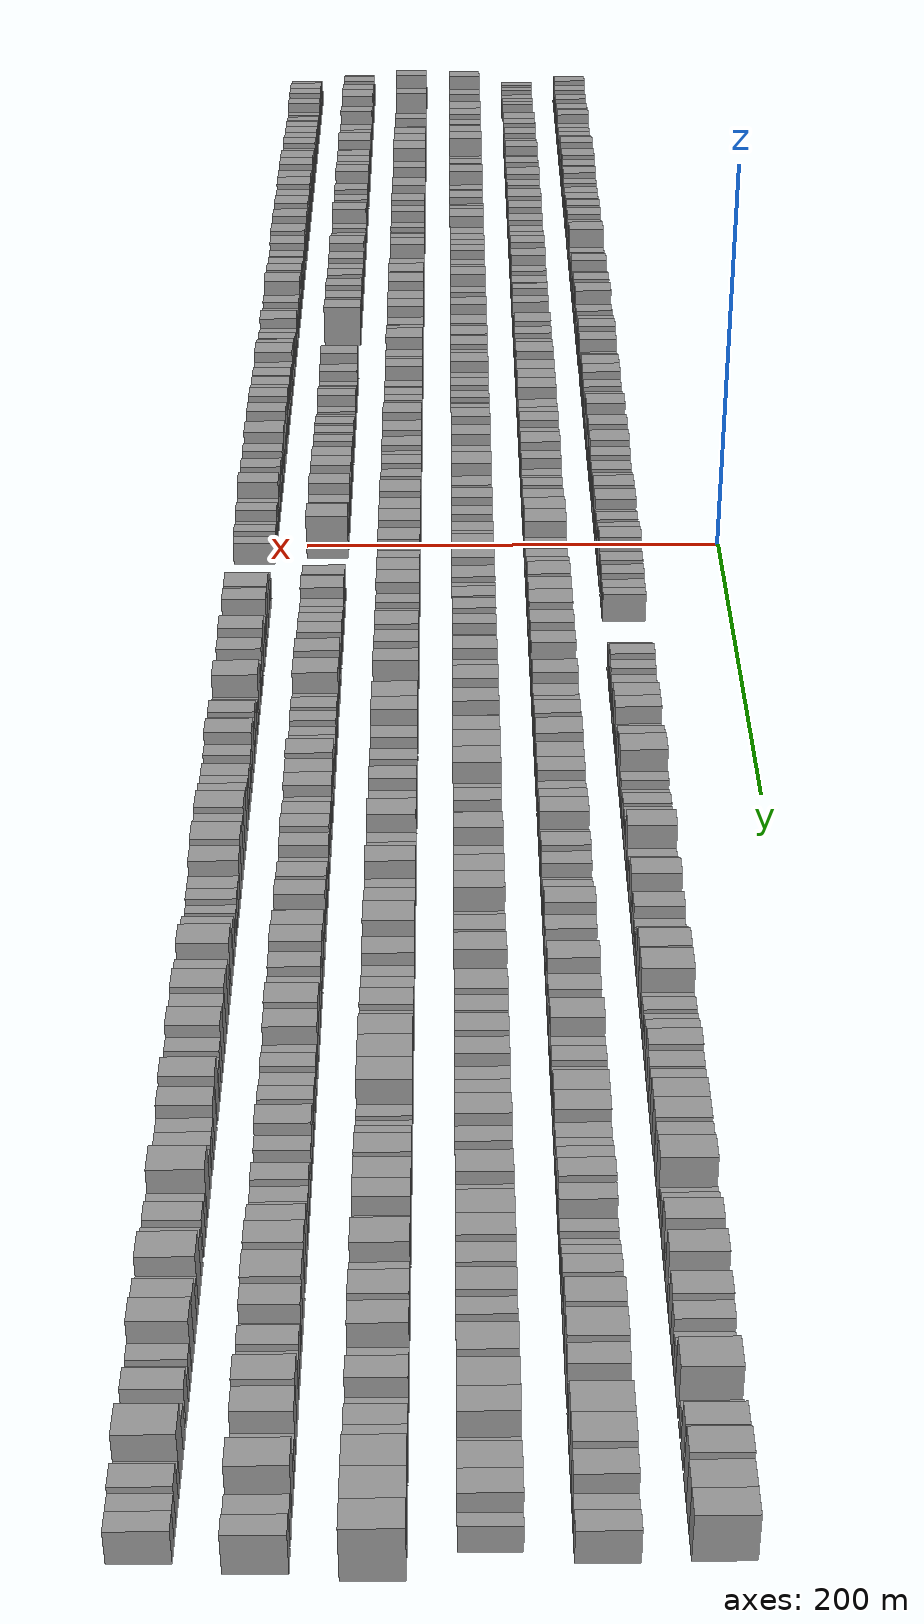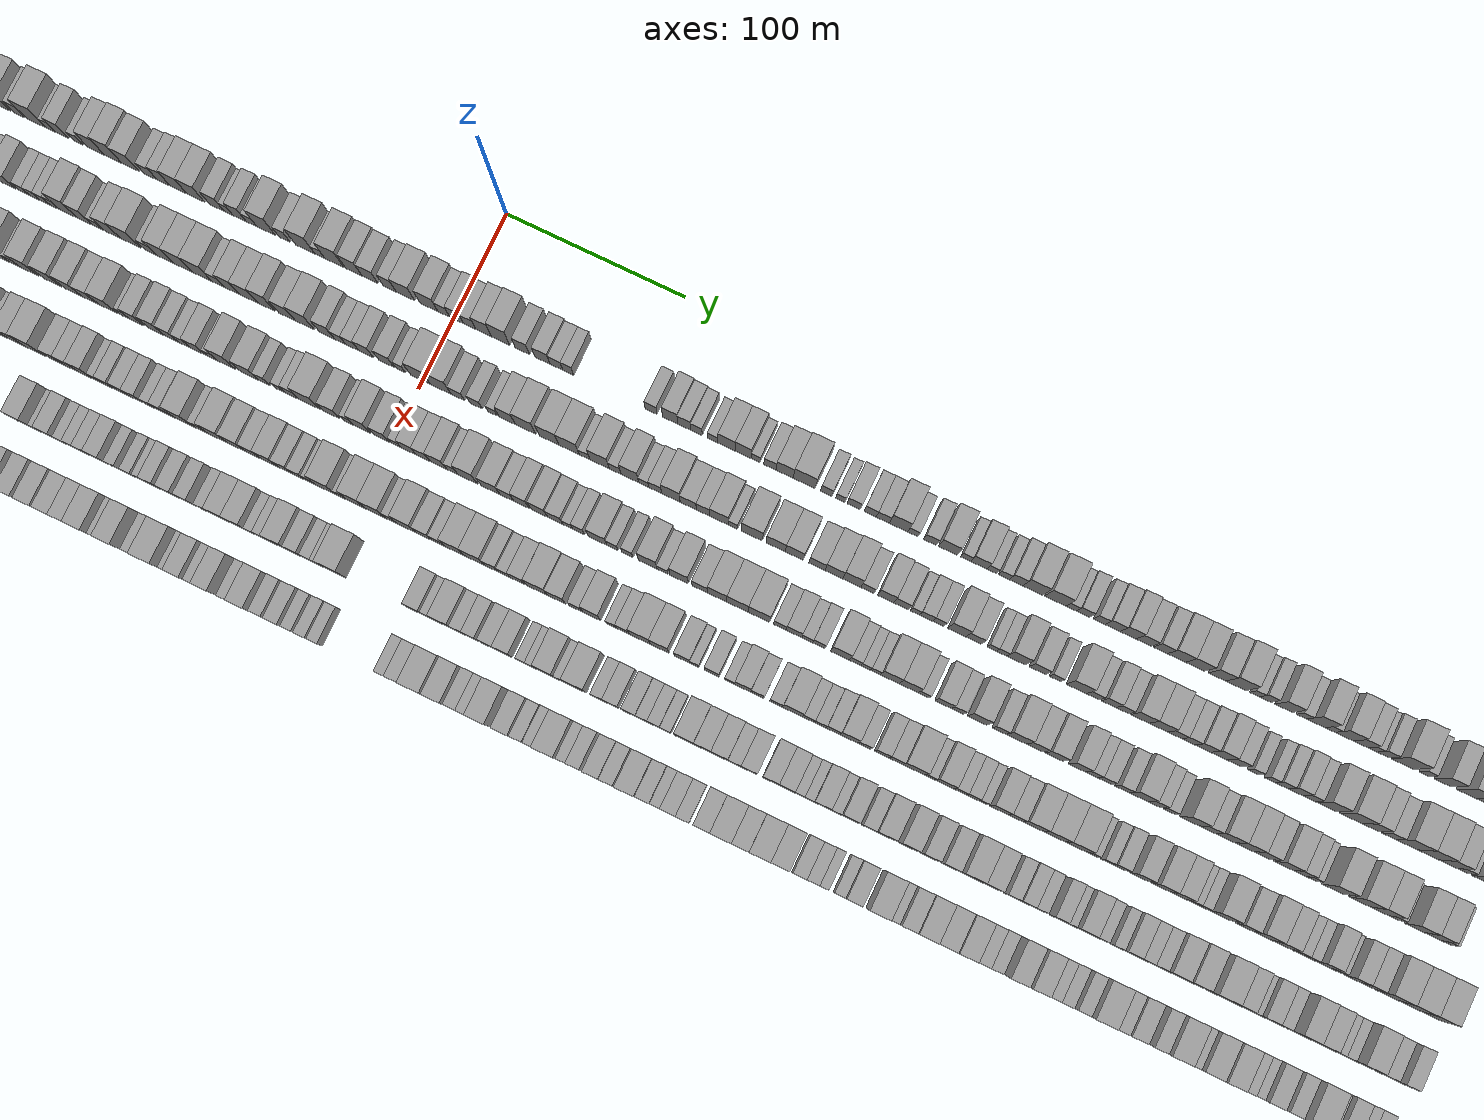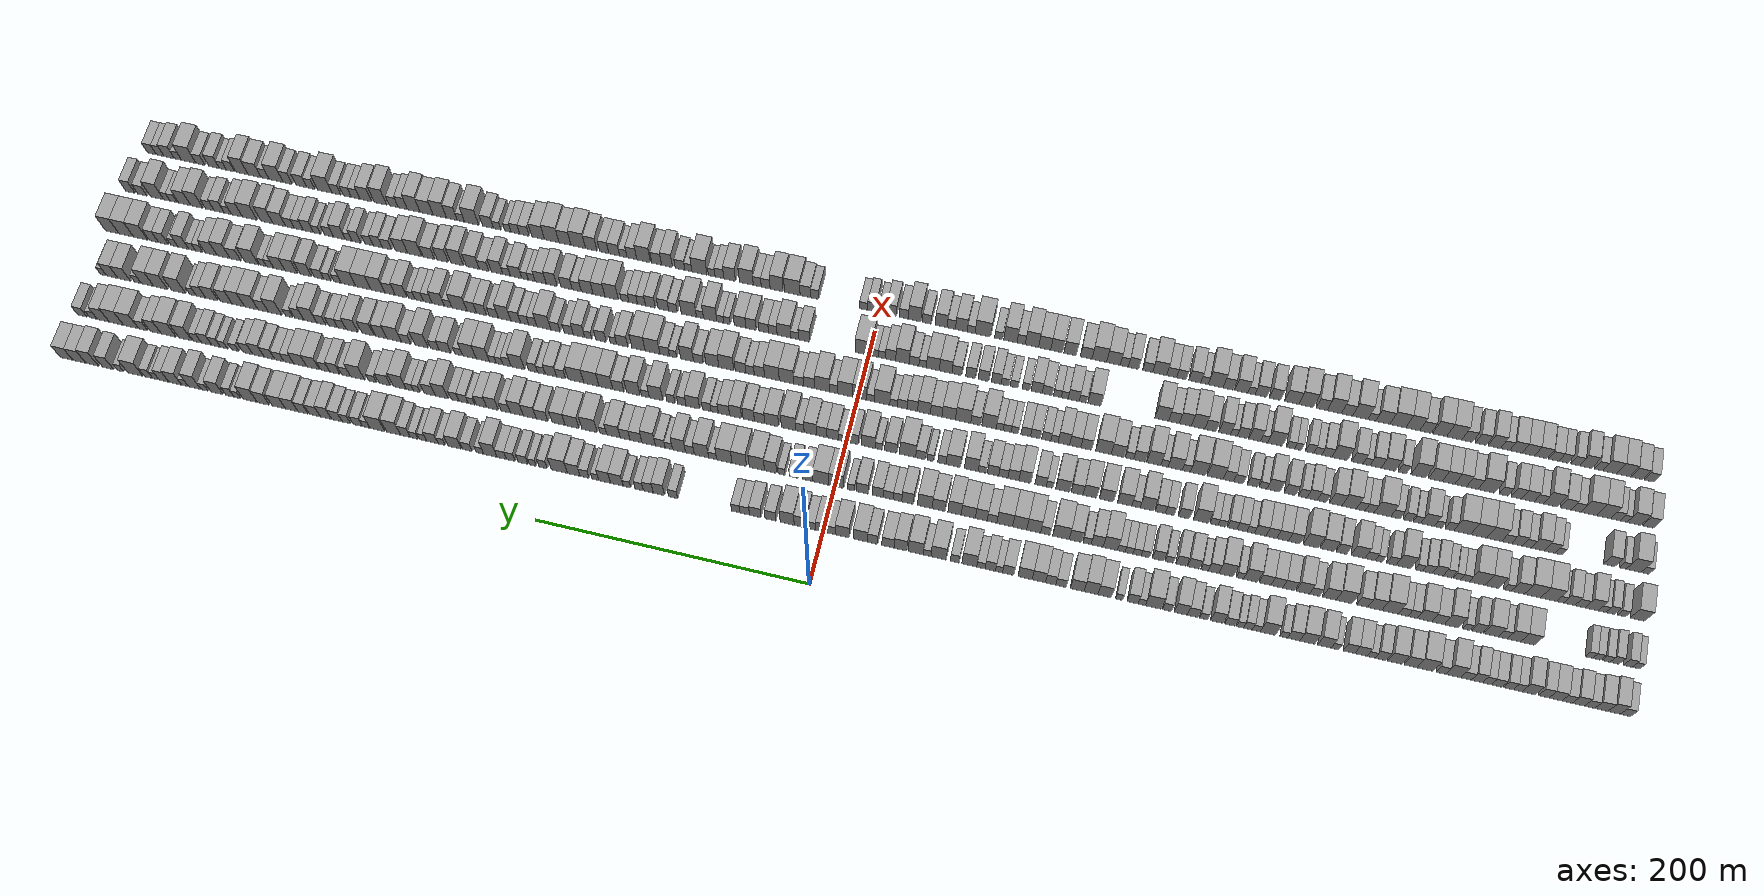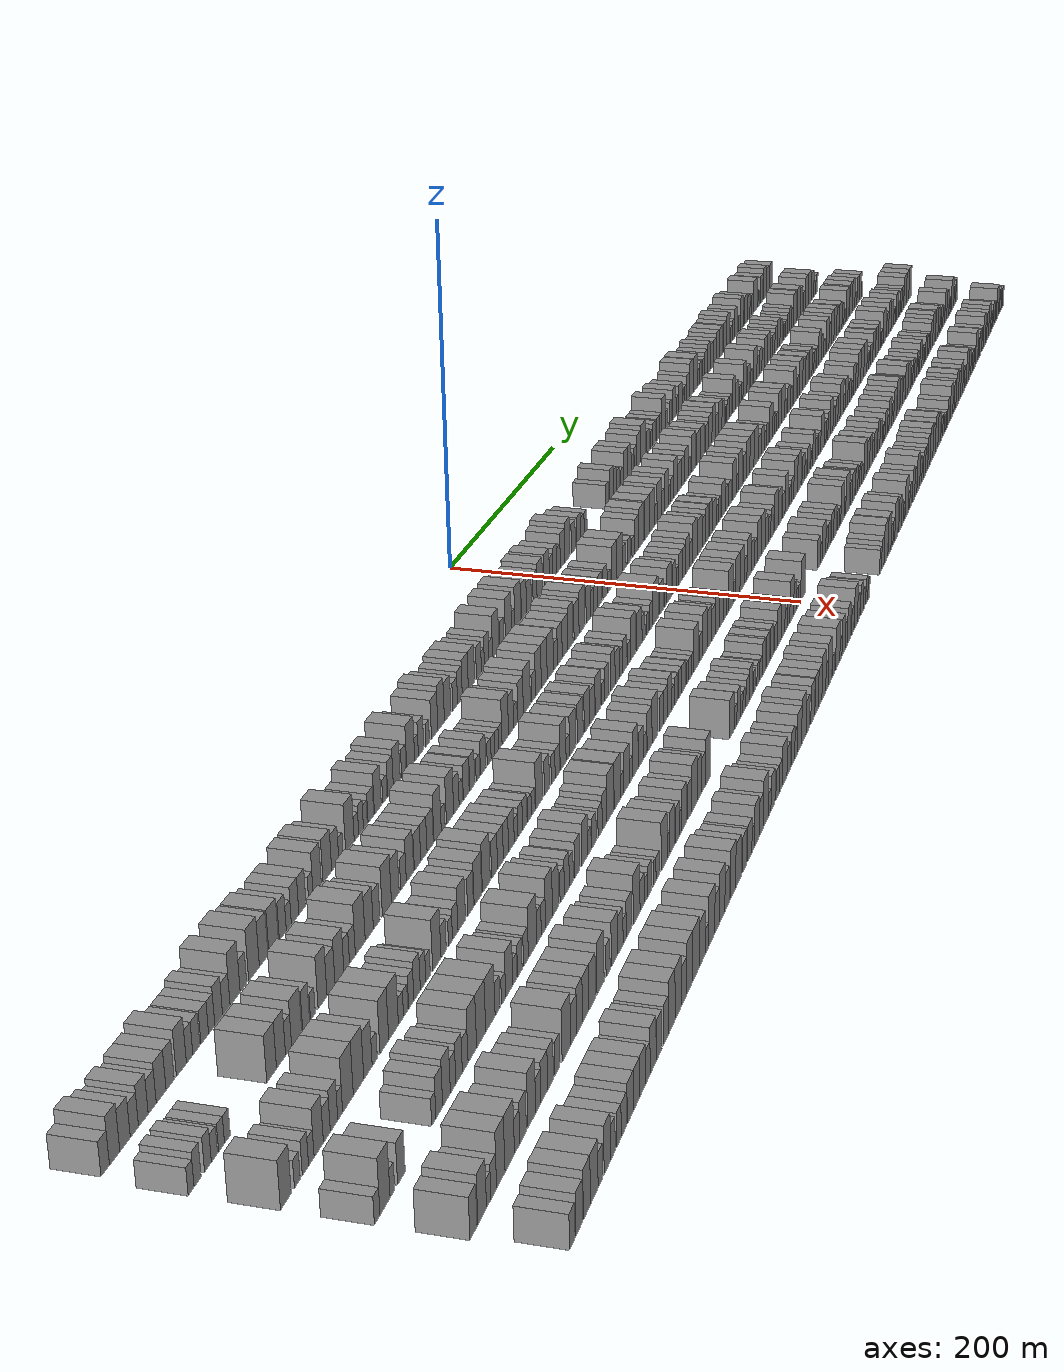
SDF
<sdf version="1.6">
 <world name="default">
  <scene>
   <sky><clouds><speed>12</speed></clouds></sky>
   <ambient>0.4 0.4 0.4 1</ambient>
   <background>0.7 0.7 0.7 1</background>
   <shadows>1</shadows>
  </scene>
  <gravity>0 0 -9.8066</gravity>
  <magnetic_field>6e-06 2.3e-05 -4.2e-05</magnetic_field>
  <physics default="0" name="default_physics" type="ode">
   <ode>
    <solver>
     <type>quick</type>
     <iters>10</iters>
     <sor>1.0</sor>
     <use_dynamic_moi_rescaling>0</use_dynamic_moi_rescaling>
    </solver>
    <constraints>
     <cfm>0</cfm>
     <erp>0.2</erp>
     <contact_max_correcting_vel>100</contact_max_correcting_vel>
     <contact_surface_layer>0.001</contact_surface_layer>
    </constraints>
   </ode>
   <max_step_size>0.004</max_step_size>
   <real_time_factor>1</real_time_factor>
   <real_time_update_rate>250</real_time_update_rate>
  </physics>
  <light name="sun" type="directional">
   <pose>0 0 10 0 0 0</pose>
   <diffuse>0.8 0.8 0.8 1</diffuse>
   <specular>0.2 0.2 0.2 1</specular>
   <attenuation>
    <range>1000</range>
    <constant>0.9</constant>
    <linear>0.01</linear>
    <quadratic>0.001</quadratic>
   </attenuation>
   <direction>-0.5 0.1 -0.9</direction>
  </light>
  <model name="building_1">
   <static>1</static>
   <pose>50.0000 -563.5539 0 0.000000 0.000000 0.000000</pose>
   <link name="link">
    <pose>0 0 7.50 0 0 0</pose>
    <collision name="collision"><geometry><box><size>20.0000 6.8922 15.0000</size></box></geometry></collision>
    <visual name="visual">
     <cast_shadows>0</cast_shadows>
     <geometry><box><size>20.0000 6.8922 15.0000</size></box></geometry>
     <material>
      <script>
       <uri>model://grey_wall/materials/scripts</uri>
       <uri>model://grey_wall/materials/textures</uri>
       <name>vrc/grey_wall</name>
      </script>
     </material>
    </visual>
   </link>
  </model>
  <model name="building_2">
   <static>1</static>
   <pose>50.0000 -555.8115 0 0.000000 0.000000 0.000000</pose>
   <link name="link">
    <pose>0 0 10.50 0 0 0</pose>
    <collision name="collision"><geometry><box><size>20.0000 8.5926 21.0000</size></box></geometry></collision>
    <visual name="visual">
     <cast_shadows>0</cast_shadows>
     <geometry><box><size>20.0000 8.5926 21.0000</size></box></geometry>
     <material>
      <script>
       <uri>model://grey_wall/materials/scripts</uri>
       <uri>model://grey_wall/materials/textures</uri>
       <name>vrc/grey_wall</name>
      </script>
     </material>
    </visual>
   </link>
  </model>
  <model name="building_3">
   <static>1</static>
   <pose>50.0000 -547.1178 0 0.000000 0.000000 0.000000</pose>
   <link name="link">
    <pose>0 0 9.00 0 0 0</pose>
    <collision name="collision"><geometry><box><size>20.0000 8.7948 18.0000</size></box></geometry></collision>
    <visual name="visual">
     <cast_shadows>0</cast_shadows>
     <geometry><box><size>20.0000 8.7948 18.0000</size></box></geometry>
     <material>
      <script>
       <uri>model://grey_wall/materials/scripts</uri>
       <uri>model://grey_wall/materials/textures</uri>
       <name>vrc/grey_wall</name>
      </script>
     </material>
    </visual>
   </link>
  </model>
  <model name="building_4">
   <static>1</static>
   <pose>50.0000 -539.2186 0 0.000000 0.000000 0.000000</pose>
   <link name="link">
    <pose>0 0 7.50 0 0 0</pose>
    <collision name="collision"><geometry><box><size>20.0000 7.0037 15.0000</size></box></geometry></collision>
    <visual name="visual">
     <cast_shadows>0</cast_shadows>
     <geometry><box><size>20.0000 7.0037 15.0000</size></box></geometry>
     <material>
      <script>
       <uri>model://grey_wall/materials/scripts</uri>
       <uri>model://grey_wall/materials/textures</uri>
       <name>vrc/grey_wall</name>
      </script>
     </material>
    </visual>
   </link>
  </model>
  <model name="building_5">
   <static>1</static>
   <pose>50.0000 -531.5585 0 0.000000 0.000000 0.000000</pose>
   <link name="link">
    <pose>0 0 9.00 0 0 0</pose>
    <collision name="collision"><geometry><box><size>20.0000 8.3165 18.0000</size></box></geometry></collision>
    <visual name="visual">
     <cast_shadows>0</cast_shadows>
     <geometry><box><size>20.0000 8.3165 18.0000</size></box></geometry>
     <material>
      <script>
       <uri>model://grey_wall/materials/scripts</uri>
       <uri>model://grey_wall/materials/textures</uri>
       <name>vrc/grey_wall</name>
      </script>
     </material>
    </visual>
   </link>
  </model>
  <model name="building_6">
   <static>1</static>
   <pose>50.0000 -523.8561 0 0.000000 0.000000 0.000000</pose>
   <link name="link">
    <pose>0 0 7.50 0 0 0</pose>
    <collision name="collision"><geometry><box><size>20.0000 7.0882 15.0000</size></box></geometry></collision>
    <visual name="visual">
     <cast_shadows>0</cast_shadows>
     <geometry><box><size>20.0000 7.0882 15.0000</size></box></geometry>
     <material>
      <script>
       <uri>model://grey_wall/materials/scripts</uri>
       <uri>model://grey_wall/materials/textures</uri>
       <name>vrc/grey_wall</name>
      </script>
     </material>
    </visual>
   </link>
  </model>
  <model name="building_7">
   <static>1</static>
   <pose>50.0000 -515.9419 0 0.000000 0.000000 0.000000</pose>
   <link name="link">
    <pose>0 0 9.00 0 0 0</pose>
    <collision name="collision"><geometry><box><size>20.0000 8.7403 18.0000</size></box></geometry></collision>
    <visual name="visual">
     <cast_shadows>0</cast_shadows>
     <geometry><box><size>20.0000 8.7403 18.0000</size></box></geometry>
     <material>
      <script>
       <uri>model://grey_wall/materials/scripts</uri>
       <uri>model://grey_wall/materials/textures</uri>
       <name>vrc/grey_wall</name>
      </script>
     </material>
    </visual>
   </link>
  </model>
  <model name="building_8">
   <static>1</static>
   <pose>50.0000 -507.8903 0 0.000000 0.000000 0.000000</pose>
   <link name="link">
    <pose>0 0 9.00 0 0 0</pose>
    <collision name="collision"><geometry><box><size>20.0000 7.3627 18.0000</size></box></geometry></collision>
    <visual name="visual">
     <cast_shadows>0</cast_shadows>
     <geometry><box><size>20.0000 7.3627 18.0000</size></box></geometry>
     <material>
      <script>
       <uri>model://grey_wall/materials/scripts</uri>
       <uri>model://grey_wall/materials/textures</uri>
       <name>vrc/grey_wall</name>
      </script>
     </material>
    </visual>
   </link>
  </model>
  <model name="building_9">
   <static>1</static>
   <pose>50.0000 -497.5966 0 0.000000 0.000000 0.000000</pose>
   <link name="link">
    <pose>0 0 10.50 0 0 0</pose>
    <collision name="collision"><geometry><box><size>20.0000 9.2247 21.0000</size></box></geometry></collision>
    <visual name="visual">
     <cast_shadows>0</cast_shadows>
     <geometry><box><size>20.0000 9.2247 21.0000</size></box></geometry>
     <material>
      <script>
       <uri>model://grey_wall/materials/scripts</uri>
       <uri>model://grey_wall/materials/textures</uri>
       <name>vrc/grey_wall</name>
      </script>
     </material>
    </visual>
   </link>
  </model>
  <model name="building_10">
   <static>1</static>
   <pose>50.0000 -489.9837 0 0.000000 0.000000 0.000000</pose>
   <link name="link">
    <pose>0 0 7.50 0 0 0</pose>
    <collision name="collision"><geometry><box><size>20.0000 6.0011 15.0000</size></box></geometry></collision>
    <visual name="visual">
     <cast_shadows>0</cast_shadows>
     <geometry><box><size>20.0000 6.0011 15.0000</size></box></geometry>
     <material>
      <script>
       <uri>model://grey_wall/materials/scripts</uri>
       <uri>model://grey_wall/materials/textures</uri>
       <name>vrc/grey_wall</name>
      </script>
     </material>
    </visual>
   </link>
  </model>
  <model name="building_11">
   <static>1</static>
   <pose>50.0000 -483.6846 0 0.000000 0.000000 0.000000</pose>
   <link name="link">
    <pose>0 0 7.50 0 0 0</pose>
    <collision name="collision"><geometry><box><size>20.0000 6.5971 15.0000</size></box></geometry></collision>
    <visual name="visual">
     <cast_shadows>0</cast_shadows>
     <geometry><box><size>20.0000 6.5971 15.0000</size></box></geometry>
     <material>
      <script>
       <uri>model://grey_wall/materials/scripts</uri>
       <uri>model://grey_wall/materials/textures</uri>
       <name>vrc/grey_wall</name>
      </script>
     </material>
    </visual>
   </link>
  </model>
  <model name="building_12">
   <static>1</static>
   <pose>50.0000 -475.7008 0 0.000000 0.000000 0.000000</pose>
   <link name="link">
    <pose>0 0 7.50 0 0 0</pose>
    <collision name="collision"><geometry><box><size>20.0000 7.3704 15.0000</size></box></geometry></collision>
    <visual name="visual">
     <cast_shadows>0</cast_shadows>
     <geometry><box><size>20.0000 7.3704 15.0000</size></box></geometry>
     <material>
      <script>
       <uri>model://grey_wall/materials/scripts</uri>
       <uri>model://grey_wall/materials/textures</uri>
       <name>vrc/grey_wall</name>
      </script>
     </material>
    </visual>
   </link>
  </model>
  <model name="building_13">
   <static>1</static>
   <pose>50.0000 -468.9971 0 0.000000 0.000000 0.000000</pose>
   <link name="link">
    <pose>0 0 7.50 0 0 0</pose>
    <collision name="collision"><geometry><box><size>20.0000 6.0371 15.0000</size></box></geometry></collision>
    <visual name="visual">
     <cast_shadows>0</cast_shadows>
     <geometry><box><size>20.0000 6.0371 15.0000</size></box></geometry>
     <material>
      <script>
       <uri>model://grey_wall/materials/scripts</uri>
       <uri>model://grey_wall/materials/textures</uri>
       <name>vrc/grey_wall</name>
      </script>
     </material>
    </visual>
   </link>
  </model>
  <model name="building_14">
   <static>1</static>
   <pose>50.0000 -462.1578 0 0.000000 0.000000 0.000000</pose>
   <link name="link">
    <pose>0 0 9.00 0 0 0</pose>
    <collision name="collision"><geometry><box><size>20.0000 7.6414 18.0000</size></box></geometry></collision>
    <visual name="visual">
     <cast_shadows>0</cast_shadows>
     <geometry><box><size>20.0000 7.6414 18.0000</size></box></geometry>
     <material>
      <script>
       <uri>model://grey_wall/materials/scripts</uri>
       <uri>model://grey_wall/materials/textures</uri>
       <name>vrc/grey_wall</name>
      </script>
     </material>
    </visual>
   </link>
  </model>
  <model name="building_15">
   <static>1</static>
   <pose>50.0000 -454.6334 0 0.000000 0.000000 0.000000</pose>
   <link name="link">
    <pose>0 0 7.50 0 0 0</pose>
    <collision name="collision"><geometry><box><size>20.0000 7.4073 15.0000</size></box></geometry></collision>
    <visual name="visual">
     <cast_shadows>0</cast_shadows>
     <geometry><box><size>20.0000 7.4073 15.0000</size></box></geometry>
     <material>
      <script>
       <uri>model://grey_wall/materials/scripts</uri>
       <uri>model://grey_wall/materials/textures</uri>
       <name>vrc/grey_wall</name>
      </script>
     </material>
    </visual>
   </link>
  </model>
  <model name="building_16">
   <static>1</static>
   <pose>50.0000 -445.8312 0 0.000000 0.000000 0.000000</pose>
   <link name="link">
    <pose>0 0 12.00 0 0 0</pose>
    <collision name="collision"><geometry><box><size>20.0000 10.1972 24.0000</size></box></geometry></collision>
    <visual name="visual">
     <cast_shadows>0</cast_shadows>
     <geometry><box><size>20.0000 10.1972 24.0000</size></box></geometry>
     <material>
      <script>
       <uri>model://grey_wall/materials/scripts</uri>
       <uri>model://grey_wall/materials/textures</uri>
       <name>vrc/grey_wall</name>
      </script>
     </material>
    </visual>
   </link>
  </model>
  <model name="building_17">
   <static>1</static>
   <pose>50.0000 -437.3728 0 0.000000 0.000000 0.000000</pose>
   <link name="link">
    <pose>0 0 7.50 0 0 0</pose>
    <collision name="collision"><geometry><box><size>20.0000 6.7195 15.0000</size></box></geometry></collision>
    <visual name="visual">
     <cast_shadows>0</cast_shadows>
     <geometry><box><size>20.0000 6.7195 15.0000</size></box></geometry>
     <material>
      <script>
       <uri>model://grey_wall/materials/scripts</uri>
       <uri>model://grey_wall/materials/textures</uri>
       <name>vrc/grey_wall</name>
      </script>
     </material>
    </visual>
   </link>
  </model>
  <model name="building_18">
   <static>1</static>
   <pose>50.0000 -426.4375 0 0.000000 0.000000 0.000000</pose>
   <link name="link">
    <pose>0 0 12.00 0 0 0</pose>
    <collision name="collision"><geometry><box><size>20.0000 11.1511 24.0000</size></box></geometry></collision>
    <visual name="visual">
     <cast_shadows>0</cast_shadows>
     <geometry><box><size>20.0000 11.1511 24.0000</size></box></geometry>
     <material>
      <script>
       <uri>model://grey_wall/materials/scripts</uri>
       <uri>model://grey_wall/materials/textures</uri>
       <name>vrc/grey_wall</name>
      </script>
     </material>
    </visual>
   </link>
  </model>
  <model name="building_19">
   <static>1</static>
   <pose>50.0000 -416.2968 0 0.000000 0.000000 0.000000</pose>
   <link name="link">
    <pose>0 0 10.50 0 0 0</pose>
    <collision name="collision"><geometry><box><size>20.0000 9.1303 21.0000</size></box></geometry></collision>
    <visual name="visual">
     <cast_shadows>0</cast_shadows>
     <geometry><box><size>20.0000 9.1303 21.0000</size></box></geometry>
     <material>
      <script>
       <uri>model://grey_wall/materials/scripts</uri>
       <uri>model://grey_wall/materials/textures</uri>
       <name>vrc/grey_wall</name>
      </script>
     </material>
    </visual>
   </link>
  </model>
  <model name="building_20">
   <static>1</static>
   <pose>50.0000 -405.5676 0 0.000000 0.000000 0.000000</pose>
   <link name="link">
    <pose>0 0 10.50 0 0 0</pose>
    <collision name="collision"><geometry><box><size>20.0000 10.3282 21.0000</size></box></geometry></collision>
    <visual name="visual">
     <cast_shadows>0</cast_shadows>
     <geometry><box><size>20.0000 10.3282 21.0000</size></box></geometry>
     <material>
      <script>
       <uri>model://grey_wall/materials/scripts</uri>
       <uri>model://grey_wall/materials/textures</uri>
       <name>vrc/grey_wall</name>
      </script>
     </material>
    </visual>
   </link>
  </model>
  <model name="building_21">
   <static>1</static>
   <pose>50.0000 -395.5879 0 0.000000 0.000000 0.000000</pose>
   <link name="link">
    <pose>0 0 9.00 0 0 0</pose>
    <collision name="collision"><geometry><box><size>20.0000 7.6313 18.0000</size></box></geometry></collision>
    <visual name="visual">
     <cast_shadows>0</cast_shadows>
     <geometry><box><size>20.0000 7.6313 18.0000</size></box></geometry>
     <material>
      <script>
       <uri>model://grey_wall/materials/scripts</uri>
       <uri>model://grey_wall/materials/textures</uri>
       <name>vrc/grey_wall</name>
      </script>
     </material>
    </visual>
   </link>
  </model>
  <model name="building_22">
   <static>1</static>
   <pose>50.0000 -388.9683 0 0.000000 0.000000 0.000000</pose>
   <link name="link">
    <pose>0 0 6.00 0 0 0</pose>
    <collision name="collision"><geometry><box><size>20.0000 5.6079 12.0000</size></box></geometry></collision>
    <visual name="visual">
     <cast_shadows>0</cast_shadows>
     <geometry><box><size>20.0000 5.6079 12.0000</size></box></geometry>
     <material>
      <script>
       <uri>model://grey_wall/materials/scripts</uri>
       <uri>model://grey_wall/materials/textures</uri>
       <name>vrc/grey_wall</name>
      </script>
     </material>
    </visual>
   </link>
  </model>
  <model name="building_23">
   <static>1</static>
   <pose>50.0000 -381.9288 0 0.000000 0.000000 0.000000</pose>
   <link name="link">
    <pose>0 0 9.00 0 0 0</pose>
    <collision name="collision"><geometry><box><size>20.0000 8.4710 18.0000</size></box></geometry></collision>
    <visual name="visual">
     <cast_shadows>0</cast_shadows>
     <geometry><box><size>20.0000 8.4710 18.0000</size></box></geometry>
     <material>
      <script>
       <uri>model://grey_wall/materials/scripts</uri>
       <uri>model://grey_wall/materials/textures</uri>
       <name>vrc/grey_wall</name>
      </script>
     </material>
    </visual>
   </link>
  </model>
  <model name="building_24">
   <static>1</static>
   <pose>50.0000 -373.6209 0 0.000000 0.000000 0.000000</pose>
   <link name="link">
    <pose>0 0 9.00 0 0 0</pose>
    <collision name="collision"><geometry><box><size>20.0000 8.1449 18.0000</size></box></geometry></collision>
    <visual name="visual">
     <cast_shadows>0</cast_shadows>
     <geometry><box><size>20.0000 8.1449 18.0000</size></box></geometry>
     <material>
      <script>
       <uri>model://grey_wall/materials/scripts</uri>
       <uri>model://grey_wall/materials/textures</uri>
       <name>vrc/grey_wall</name>
      </script>
     </material>
    </visual>
   </link>
  </model>
  <model name="building_25">
   <static>1</static>
   <pose>50.0000 -363.9228 0 0.000000 0.000000 0.000000</pose>
   <link name="link">
    <pose>0 0 6.00 0 0 0</pose>
    <collision name="collision"><geometry><box><size>20.0000 5.2513 12.0000</size></box></geometry></collision>
    <visual name="visual">
     <cast_shadows>0</cast_shadows>
     <geometry><box><size>20.0000 5.2513 12.0000</size></box></geometry>
     <material>
      <script>
       <uri>model://grey_wall/materials/scripts</uri>
       <uri>model://grey_wall/materials/textures</uri>
       <name>vrc/grey_wall</name>
      </script>
     </material>
    </visual>
   </link>
  </model>
  <model name="building_26">
   <static>1</static>
   <pose>50.0000 -356.5422 0 0.000000 0.000000 0.000000</pose>
   <link name="link">
    <pose>0 0 10.50 0 0 0</pose>
    <collision name="collision"><geometry><box><size>20.0000 9.5100 21.0000</size></box></geometry></collision>
    <visual name="visual">
     <cast_shadows>0</cast_shadows>
     <geometry><box><size>20.0000 9.5100 21.0000</size></box></geometry>
     <material>
      <script>
       <uri>model://grey_wall/materials/scripts</uri>
       <uri>model://grey_wall/materials/textures</uri>
       <name>vrc/grey_wall</name>
      </script>
     </material>
    </visual>
   </link>
  </model>
  <model name="building_27">
   <static>1</static>
   <pose>50.0000 -344.5830 0 0.000000 0.000000 0.000000</pose>
   <link name="link">
    <pose>0 0 10.50 0 0 0</pose>
    <collision name="collision"><geometry><box><size>20.0000 10.4083 21.0000</size></box></geometry></collision>
    <visual name="visual">
     <cast_shadows>0</cast_shadows>
     <geometry><box><size>20.0000 10.4083 21.0000</size></box></geometry>
     <material>
      <script>
       <uri>model://grey_wall/materials/scripts</uri>
       <uri>model://grey_wall/materials/textures</uri>
       <name>vrc/grey_wall</name>
      </script>
     </material>
    </visual>
   </link>
  </model>
  <model name="building_28">
   <static>1</static>
   <pose>50.0000 -335.0815 0 0.000000 0.000000 0.000000</pose>
   <link name="link">
    <pose>0 0 9.00 0 0 0</pose>
    <collision name="collision"><geometry><box><size>20.0000 8.5948 18.0000</size></box></geometry></collision>
    <visual name="visual">
     <cast_shadows>0</cast_shadows>
     <geometry><box><size>20.0000 8.5948 18.0000</size></box></geometry>
     <material>
      <script>
       <uri>model://grey_wall/materials/scripts</uri>
       <uri>model://grey_wall/materials/textures</uri>
       <name>vrc/grey_wall</name>
      </script>
     </material>
    </visual>
   </link>
  </model>
  <model name="building_29">
   <static>1</static>
   <pose>50.0000 -328.0749 0 0.000000 0.000000 0.000000</pose>
   <link name="link">
    <pose>0 0 6.00 0 0 0</pose>
    <collision name="collision"><geometry><box><size>20.0000 5.4185 12.0000</size></box></geometry></collision>
    <visual name="visual">
     <cast_shadows>0</cast_shadows>
     <geometry><box><size>20.0000 5.4185 12.0000</size></box></geometry>
     <material>
      <script>
       <uri>model://grey_wall/materials/scripts</uri>
       <uri>model://grey_wall/materials/textures</uri>
       <name>vrc/grey_wall</name>
      </script>
     </material>
    </visual>
   </link>
  </model>
  <model name="building_30">
   <static>1</static>
   <pose>50.0000 -317.0212 0 0.000000 0.000000 0.000000</pose>
   <link name="link">
    <pose>0 0 12.00 0 0 0</pose>
    <collision name="collision"><geometry><box><size>20.0000 10.6889 24.0000</size></box></geometry></collision>
    <visual name="visual">
     <cast_shadows>0</cast_shadows>
     <geometry><box><size>20.0000 10.6889 24.0000</size></box></geometry>
     <material>
      <script>
       <uri>model://grey_wall/materials/scripts</uri>
       <uri>model://grey_wall/materials/textures</uri>
       <name>vrc/grey_wall</name>
      </script>
     </material>
    </visual>
   </link>
  </model>
  <model name="building_31">
   <static>1</static>
   <pose>50.0000 -308.8232 0 0.000000 0.000000 0.000000</pose>
   <link name="link">
    <pose>0 0 6.00 0 0 0</pose>
    <collision name="collision"><geometry><box><size>20.0000 5.7072 12.0000</size></box></geometry></collision>
    <visual name="visual">
     <cast_shadows>0</cast_shadows>
     <geometry><box><size>20.0000 5.7072 12.0000</size></box></geometry>
     <material>
      <script>
       <uri>model://grey_wall/materials/scripts</uri>
       <uri>model://grey_wall/materials/textures</uri>
       <name>vrc/grey_wall</name>
      </script>
     </material>
    </visual>
   </link>
  </model>
  <model name="building_32">
   <static>1</static>
   <pose>50.0000 -302.9643 0 0.000000 0.000000 0.000000</pose>
   <link name="link">
    <pose>0 0 7.50 0 0 0</pose>
    <collision name="collision"><geometry><box><size>20.0000 6.0104 15.0000</size></box></geometry></collision>
    <visual name="visual">
     <cast_shadows>0</cast_shadows>
     <geometry><box><size>20.0000 6.0104 15.0000</size></box></geometry>
     <material>
      <script>
       <uri>model://grey_wall/materials/scripts</uri>
       <uri>model://grey_wall/materials/textures</uri>
       <name>vrc/grey_wall</name>
      </script>
     </material>
    </visual>
   </link>
  </model>
  <model name="building_33">
   <static>1</static>
   <pose>50.0000 -297.5027 0 0.000000 0.000000 0.000000</pose>
   <link name="link">
    <pose>0 0 6.00 0 0 0</pose>
    <collision name="collision"><geometry><box><size>20.0000 4.9128 12.0000</size></box></geometry></collision>
    <visual name="visual">
     <cast_shadows>0</cast_shadows>
     <geometry><box><size>20.0000 4.9128 12.0000</size></box></geometry>
     <material>
      <script>
       <uri>model://grey_wall/materials/scripts</uri>
       <uri>model://grey_wall/materials/textures</uri>
       <name>vrc/grey_wall</name>
      </script>
     </material>
    </visual>
   </link>
  </model>
  <model name="building_34">
   <static>1</static>
   <pose>50.0000 -290.3812 0 0.000000 0.000000 0.000000</pose>
   <link name="link">
    <pose>0 0 7.50 0 0 0</pose>
    <collision name="collision"><geometry><box><size>20.0000 7.3303 15.0000</size></box></geometry></collision>
    <visual name="visual">
     <cast_shadows>0</cast_shadows>
     <geometry><box><size>20.0000 7.3303 15.0000</size></box></geometry>
     <material>
      <script>
       <uri>model://grey_wall/materials/scripts</uri>
       <uri>model://grey_wall/materials/textures</uri>
       <name>vrc/grey_wall</name>
      </script>
     </material>
    </visual>
   </link>
  </model>
  <model name="building_35">
   <static>1</static>
   <pose>50.0000 -281.2286 0 0.000000 0.000000 0.000000</pose>
   <link name="link">
    <pose>0 0 10.50 0 0 0</pose>
    <collision name="collision"><geometry><box><size>20.0000 8.9748 21.0000</size></box></geometry></collision>
    <visual name="visual">
     <cast_shadows>0</cast_shadows>
     <geometry><box><size>20.0000 8.9748 21.0000</size></box></geometry>
     <material>
      <script>
       <uri>model://grey_wall/materials/scripts</uri>
       <uri>model://grey_wall/materials/textures</uri>
       <name>vrc/grey_wall</name>
      </script>
     </material>
    </visual>
   </link>
  </model>
  <model name="building_36">
   <static>1</static>
   <pose>50.0000 -271.9024 0 0.000000 0.000000 0.000000</pose>
   <link name="link">
    <pose>0 0 6.00 0 0 0</pose>
    <collision name="collision"><geometry><box><size>20.0000 5.6775 12.0000</size></box></geometry></collision>
    <visual name="visual">
     <cast_shadows>0</cast_shadows>
     <geometry><box><size>20.0000 5.6775 12.0000</size></box></geometry>
     <material>
      <script>
       <uri>model://grey_wall/materials/scripts</uri>
       <uri>model://grey_wall/materials/textures</uri>
       <name>vrc/grey_wall</name>
      </script>
     </material>
    </visual>
   </link>
  </model>
  <model name="building_37">
   <static>1</static>
   <pose>50.0000 -264.2198 0 0.000000 0.000000 0.000000</pose>
   <link name="link">
    <pose>0 0 9.00 0 0 0</pose>
    <collision name="collision"><geometry><box><size>20.0000 7.6877 18.0000</size></box></geometry></collision>
    <visual name="visual">
     <cast_shadows>0</cast_shadows>
     <geometry><box><size>20.0000 7.6877 18.0000</size></box></geometry>
     <material>
      <script>
       <uri>model://grey_wall/materials/scripts</uri>
       <uri>model://grey_wall/materials/textures</uri>
       <name>vrc/grey_wall</name>
      </script>
     </material>
    </visual>
   </link>
  </model>
  <model name="building_38">
   <static>1</static>
   <pose>50.0000 -255.7538 0 0.000000 0.000000 0.000000</pose>
   <link name="link">
    <pose>0 0 10.50 0 0 0</pose>
    <collision name="collision"><geometry><box><size>20.0000 9.2443 21.0000</size></box></geometry></collision>
    <visual name="visual">
     <cast_shadows>0</cast_shadows>
     <geometry><box><size>20.0000 9.2443 21.0000</size></box></geometry>
     <material>
      <script>
       <uri>model://grey_wall/materials/scripts</uri>
       <uri>model://grey_wall/materials/textures</uri>
       <name>vrc/grey_wall</name>
      </script>
     </material>
    </visual>
   </link>
  </model>
  <model name="building_39">
   <static>1</static>
   <pose>50.0000 -246.0287 0 0.000000 0.000000 0.000000</pose>
   <link name="link">
    <pose>0 0 7.50 0 0 0</pose>
    <collision name="collision"><geometry><box><size>20.0000 6.2059 15.0000</size></box></geometry></collision>
    <visual name="visual">
     <cast_shadows>0</cast_shadows>
     <geometry><box><size>20.0000 6.2059 15.0000</size></box></geometry>
     <material>
      <script>
       <uri>model://grey_wall/materials/scripts</uri>
       <uri>model://grey_wall/materials/textures</uri>
       <name>vrc/grey_wall</name>
      </script>
     </material>
    </visual>
   </link>
  </model>
  <model name="building_40">
   <static>1</static>
   <pose>50.0000 -236.3519 0 0.000000 0.000000 0.000000</pose>
   <link name="link">
    <pose>0 0 12.00 0 0 0</pose>
    <collision name="collision"><geometry><box><size>20.0000 11.1478 24.0000</size></box></geometry></collision>
    <visual name="visual">
     <cast_shadows>0</cast_shadows>
     <geometry><box><size>20.0000 11.1478 24.0000</size></box></geometry>
     <material>
      <script>
       <uri>model://grey_wall/materials/scripts</uri>
       <uri>model://grey_wall/materials/textures</uri>
       <name>vrc/grey_wall</name>
      </script>
     </material>
    </visual>
   </link>
  </model>
  <model name="building_41">
   <static>1</static>
   <pose>50.0000 -228.2079 0 0.000000 0.000000 0.000000</pose>
   <link name="link">
    <pose>0 0 6.00 0 0 0</pose>
    <collision name="collision"><geometry><box><size>20.0000 5.1401 12.0000</size></box></geometry></collision>
    <visual name="visual">
     <cast_shadows>0</cast_shadows>
     <geometry><box><size>20.0000 5.1401 12.0000</size></box></geometry>
     <material>
      <script>
       <uri>model://grey_wall/materials/scripts</uri>
       <uri>model://grey_wall/materials/textures</uri>
       <name>vrc/grey_wall</name>
      </script>
     </material>
    </visual>
   </link>
  </model>
  <model name="building_42">
   <static>1</static>
   <pose>50.0000 -221.7240 0 0.000000 0.000000 0.000000</pose>
   <link name="link">
    <pose>0 0 9.00 0 0 0</pose>
    <collision name="collision"><geometry><box><size>20.0000 7.8278 18.0000</size></box></geometry></collision>
    <visual name="visual">
     <cast_shadows>0</cast_shadows>
     <geometry><box><size>20.0000 7.8278 18.0000</size></box></geometry>
     <material>
      <script>
       <uri>model://grey_wall/materials/scripts</uri>
       <uri>model://grey_wall/materials/textures</uri>
       <name>vrc/grey_wall</name>
      </script>
     </material>
    </visual>
   </link>
  </model>
  <model name="building_43">
   <static>1</static>
   <pose>50.0000 -212.2412 0 0.000000 0.000000 0.000000</pose>
   <link name="link">
    <pose>0 0 6.00 0 0 0</pose>
    <collision name="collision"><geometry><box><size>20.0000 5.1378 12.0000</size></box></geometry></collision>
    <visual name="visual">
     <cast_shadows>0</cast_shadows>
     <geometry><box><size>20.0000 5.1378 12.0000</size></box></geometry>
     <material>
      <script>
       <uri>model://grey_wall/materials/scripts</uri>
       <uri>model://grey_wall/materials/textures</uri>
       <name>vrc/grey_wall</name>
      </script>
     </material>
    </visual>
   </link>
  </model>
  <model name="building_44">
   <static>1</static>
   <pose>50.0000 -201.8625 0 0.000000 0.000000 0.000000</pose>
   <link name="link">
    <pose>0 0 10.50 0 0 0</pose>
    <collision name="collision"><geometry><box><size>20.0000 9.6195 21.0000</size></box></geometry></collision>
    <visual name="visual">
     <cast_shadows>0</cast_shadows>
     <geometry><box><size>20.0000 9.6195 21.0000</size></box></geometry>
     <material>
      <script>
       <uri>model://grey_wall/materials/scripts</uri>
       <uri>model://grey_wall/materials/textures</uri>
       <name>vrc/grey_wall</name>
      </script>
     </material>
    </visual>
   </link>
  </model>
  <model name="building_45">
   <static>1</static>
   <pose>50.0000 -192.1746 0 0.000000 0.000000 0.000000</pose>
   <link name="link">
    <pose>0 0 12.00 0 0 0</pose>
    <collision name="collision"><geometry><box><size>20.0000 9.7564 24.0000</size></box></geometry></collision>
    <visual name="visual">
     <cast_shadows>0</cast_shadows>
     <geometry><box><size>20.0000 9.7564 24.0000</size></box></geometry>
     <material>
      <script>
       <uri>model://grey_wall/materials/scripts</uri>
       <uri>model://grey_wall/materials/textures</uri>
       <name>vrc/grey_wall</name>
      </script>
     </material>
    </visual>
   </link>
  </model>
  <model name="building_46">
   <static>1</static>
   <pose>50.0000 -182.3982 0 0.000000 0.000000 0.000000</pose>
   <link name="link">
    <pose>0 0 10.50 0 0 0</pose>
    <collision name="collision"><geometry><box><size>20.0000 9.7964 21.0000</size></box></geometry></collision>
    <visual name="visual">
     <cast_shadows>0</cast_shadows>
     <geometry><box><size>20.0000 9.7964 21.0000</size></box></geometry>
     <material>
      <script>
       <uri>model://grey_wall/materials/scripts</uri>
       <uri>model://grey_wall/materials/textures</uri>
       <name>vrc/grey_wall</name>
      </script>
     </material>
    </visual>
   </link>
  </model>
  <model name="building_47">
   <static>1</static>
   <pose>50.0000 -170.8231 0 0.000000 0.000000 0.000000</pose>
   <link name="link">
    <pose>0 0 7.50 0 0 0</pose>
    <collision name="collision"><geometry><box><size>20.0000 7.3539 15.0000</size></box></geometry></collision>
    <visual name="visual">
     <cast_shadows>0</cast_shadows>
     <geometry><box><size>20.0000 7.3539 15.0000</size></box></geometry>
     <material>
      <script>
       <uri>model://grey_wall/materials/scripts</uri>
       <uri>model://grey_wall/materials/textures</uri>
       <name>vrc/grey_wall</name>
      </script>
     </material>
    </visual>
   </link>
  </model>
  <model name="building_48">
   <static>1</static>
   <pose>50.0000 -163.4717 0 0.000000 0.000000 0.000000</pose>
   <link name="link">
    <pose>0 0 9.00 0 0 0</pose>
    <collision name="collision"><geometry><box><size>20.0000 7.3488 18.0000</size></box></geometry></collision>
    <visual name="visual">
     <cast_shadows>0</cast_shadows>
     <geometry><box><size>20.0000 7.3488 18.0000</size></box></geometry>
     <material>
      <script>
       <uri>model://grey_wall/materials/scripts</uri>
       <uri>model://grey_wall/materials/textures</uri>
       <name>vrc/grey_wall</name>
      </script>
     </material>
    </visual>
   </link>
  </model>
  <model name="building_49">
   <static>1</static>
   <pose>50.0000 -155.0345 0 0.000000 0.000000 0.000000</pose>
   <link name="link">
    <pose>0 0 10.50 0 0 0</pose>
    <collision name="collision"><geometry><box><size>20.0000 9.5256 21.0000</size></box></geometry></collision>
    <visual name="visual">
     <cast_shadows>0</cast_shadows>
     <geometry><box><size>20.0000 9.5256 21.0000</size></box></geometry>
     <material>
      <script>
       <uri>model://grey_wall/materials/scripts</uri>
       <uri>model://grey_wall/materials/textures</uri>
       <name>vrc/grey_wall</name>
      </script>
     </material>
    </visual>
   </link>
  </model>
  <model name="building_50">
   <static>1</static>
   <pose>50.0000 -145.2269 0 0.000000 0.000000 0.000000</pose>
   <link name="link">
    <pose>0 0 10.50 0 0 0</pose>
    <collision name="collision"><geometry><box><size>20.0000 10.0897 21.0000</size></box></geometry></collision>
    <visual name="visual">
     <cast_shadows>0</cast_shadows>
     <geometry><box><size>20.0000 10.0897 21.0000</size></box></geometry>
     <material>
      <script>
       <uri>model://grey_wall/materials/scripts</uri>
       <uri>model://grey_wall/materials/textures</uri>
       <name>vrc/grey_wall</name>
      </script>
     </material>
    </visual>
   </link>
  </model>
  <model name="building_51">
   <static>1</static>
   <pose>50.0000 -133.1259 0 0.000000 0.000000 0.000000</pose>
   <link name="link">
    <pose>0 0 9.00 0 0 0</pose>
    <collision name="collision"><geometry><box><size>20.0000 8.1121 18.0000</size></box></geometry></collision>
    <visual name="visual">
     <cast_shadows>0</cast_shadows>
     <geometry><box><size>20.0000 8.1121 18.0000</size></box></geometry>
     <material>
      <script>
       <uri>model://grey_wall/materials/scripts</uri>
       <uri>model://grey_wall/materials/textures</uri>
       <name>vrc/grey_wall</name>
      </script>
     </material>
    </visual>
   </link>
  </model>
  <model name="building_52">
   <static>1</static>
   <pose>50.0000 -126.5854 0 0.000000 0.000000 0.000000</pose>
   <link name="link">
    <pose>0 0 6.00 0 0 0</pose>
    <collision name="collision"><geometry><box><size>20.0000 4.9690 12.0000</size></box></geometry></collision>
    <visual name="visual">
     <cast_shadows>0</cast_shadows>
     <geometry><box><size>20.0000 4.9690 12.0000</size></box></geometry>
     <material>
      <script>
       <uri>model://grey_wall/materials/scripts</uri>
       <uri>model://grey_wall/materials/textures</uri>
       <name>vrc/grey_wall</name>
      </script>
     </material>
    </visual>
   </link>
  </model>
  <model name="building_53">
   <static>1</static>
   <pose>50.0000 -120.3051 0 0.000000 0.000000 0.000000</pose>
   <link name="link">
    <pose>0 0 9.00 0 0 0</pose>
    <collision name="collision"><geometry><box><size>20.0000 7.5916 18.0000</size></box></geometry></collision>
    <visual name="visual">
     <cast_shadows>0</cast_shadows>
     <geometry><box><size>20.0000 7.5916 18.0000</size></box></geometry>
     <material>
      <script>
       <uri>model://grey_wall/materials/scripts</uri>
       <uri>model://grey_wall/materials/textures</uri>
       <name>vrc/grey_wall</name>
      </script>
     </material>
    </visual>
   </link>
  </model>
  <model name="building_54">
   <static>1</static>
   <pose>50.0000 -113.5616 0 0.000000 0.000000 0.000000</pose>
   <link name="link">
    <pose>0 0 6.00 0 0 0</pose>
    <collision name="collision"><geometry><box><size>20.0000 5.8954 12.0000</size></box></geometry></collision>
    <visual name="visual">
     <cast_shadows>0</cast_shadows>
     <geometry><box><size>20.0000 5.8954 12.0000</size></box></geometry>
     <material>
      <script>
       <uri>model://grey_wall/materials/scripts</uri>
       <uri>model://grey_wall/materials/textures</uri>
       <name>vrc/grey_wall</name>
      </script>
     </material>
    </visual>
   </link>
  </model>
  <model name="building_55">
   <static>1</static>
   <pose>50.0000 -105.3079 0 0.000000 0.000000 0.000000</pose>
   <link name="link">
    <pose>0 0 12.00 0 0 0</pose>
    <collision name="collision"><geometry><box><size>20.0000 10.6120 24.0000</size></box></geometry></collision>
    <visual name="visual">
     <cast_shadows>0</cast_shadows>
     <geometry><box><size>20.0000 10.6120 24.0000</size></box></geometry>
     <material>
      <script>
       <uri>model://grey_wall/materials/scripts</uri>
       <uri>model://grey_wall/materials/textures</uri>
       <name>vrc/grey_wall</name>
      </script>
     </material>
    </visual>
   </link>
  </model>
  <model name="building_56">
   <static>1</static>
   <pose>50.0000 -94.8474 0 0.000000 0.000000 0.000000</pose>
   <link name="link">
    <pose>0 0 7.50 0 0 0</pose>
    <collision name="collision"><geometry><box><size>20.0000 6.3090 15.0000</size></box></geometry></collision>
    <visual name="visual">
     <cast_shadows>0</cast_shadows>
     <geometry><box><size>20.0000 6.3090 15.0000</size></box></geometry>
     <material>
      <script>
       <uri>model://grey_wall/materials/scripts</uri>
       <uri>model://grey_wall/materials/textures</uri>
       <name>vrc/grey_wall</name>
      </script>
     </material>
    </visual>
   </link>
  </model>
  <model name="building_57">
   <static>1</static>
   <pose>50.0000 -83.2250 0 0.000000 0.000000 0.000000</pose>
   <link name="link">
    <pose>0 0 12.00 0 0 0</pose>
    <collision name="collision"><geometry><box><size>20.0000 10.9358 24.0000</size></box></geometry></collision>
    <visual name="visual">
     <cast_shadows>0</cast_shadows>
     <geometry><box><size>20.0000 10.9358 24.0000</size></box></geometry>
     <material>
      <script>
       <uri>model://grey_wall/materials/scripts</uri>
       <uri>model://grey_wall/materials/textures</uri>
       <name>vrc/grey_wall</name>
      </script>
     </material>
    </visual>
   </link>
  </model>
  <model name="building_58">
   <static>1</static>
   <pose>50.0000 -74.9646 0 0.000000 0.000000 0.000000</pose>
   <link name="link">
    <pose>0 0 6.00 0 0 0</pose>
    <collision name="collision"><geometry><box><size>20.0000 5.5850 12.0000</size></box></geometry></collision>
    <visual name="visual">
     <cast_shadows>0</cast_shadows>
     <geometry><box><size>20.0000 5.5850 12.0000</size></box></geometry>
     <material>
      <script>
       <uri>model://grey_wall/materials/scripts</uri>
       <uri>model://grey_wall/materials/textures</uri>
       <name>vrc/grey_wall</name>
      </script>
     </material>
    </visual>
   </link>
  </model>
  <model name="building_59">
   <static>1</static>
   <pose>50.0000 -66.7866 0 0.000000 0.000000 0.000000</pose>
   <link name="link">
    <pose>0 0 12.00 0 0 0</pose>
    <collision name="collision"><geometry><box><size>20.0000 10.7712 24.0000</size></box></geometry></collision>
    <visual name="visual">
     <cast_shadows>0</cast_shadows>
     <geometry><box><size>20.0000 10.7712 24.0000</size></box></geometry>
     <material>
      <script>
       <uri>model://grey_wall/materials/scripts</uri>
       <uri>model://grey_wall/materials/textures</uri>
       <name>vrc/grey_wall</name>
      </script>
     </material>
    </visual>
   </link>
  </model>
  <model name="building_60">
   <static>1</static>
   <pose>50.0000 -55.7964 0 0.000000 0.000000 0.000000</pose>
   <link name="link">
    <pose>0 0 10.50 0 0 0</pose>
    <collision name="collision"><geometry><box><size>20.0000 9.2092 21.0000</size></box></geometry></collision>
    <visual name="visual">
     <cast_shadows>0</cast_shadows>
     <geometry><box><size>20.0000 9.2092 21.0000</size></box></geometry>
     <material>
      <script>
       <uri>model://grey_wall/materials/scripts</uri>
       <uri>model://grey_wall/materials/textures</uri>
       <name>vrc/grey_wall</name>
      </script>
     </material>
    </visual>
   </link>
  </model>
  <model name="building_61">
   <static>1</static>
   <pose>50.0000 -46.7368 0 0.000000 0.000000 0.000000</pose>
   <link name="link">
    <pose>0 0 9.00 0 0 0</pose>
    <collision name="collision"><geometry><box><size>20.0000 8.9100 18.0000</size></box></geometry></collision>
    <visual name="visual">
     <cast_shadows>0</cast_shadows>
     <geometry><box><size>20.0000 8.9100 18.0000</size></box></geometry>
     <material>
      <script>
       <uri>model://grey_wall/materials/scripts</uri>
       <uri>model://grey_wall/materials/textures</uri>
       <name>vrc/grey_wall</name>
      </script>
     </material>
    </visual>
   </link>
  </model>
  <model name="building_62">
   <static>1</static>
   <pose>50.0000 -35.6506 0 0.000000 0.000000 0.000000</pose>
   <link name="link">
    <pose>0 0 9.00 0 0 0</pose>
    <collision name="collision"><geometry><box><size>20.0000 7.2624 18.0000</size></box></geometry></collision>
    <visual name="visual">
     <cast_shadows>0</cast_shadows>
     <geometry><box><size>20.0000 7.2624 18.0000</size></box></geometry>
     <material>
      <script>
       <uri>model://grey_wall/materials/scripts</uri>
       <uri>model://grey_wall/materials/textures</uri>
       <name>vrc/grey_wall</name>
      </script>
     </material>
    </visual>
   </link>
  </model>
  <model name="building_63">
   <static>1</static>
   <pose>50.0000 -26.7902 0 0.000000 0.000000 0.000000</pose>
   <link name="link">
    <pose>0 0 10.50 0 0 0</pose>
    <collision name="collision"><geometry><box><size>20.0000 10.4585 21.0000</size></box></geometry></collision>
    <visual name="visual">
     <cast_shadows>0</cast_shadows>
     <geometry><box><size>20.0000 10.4585 21.0000</size></box></geometry>
     <material>
      <script>
       <uri>model://grey_wall/materials/scripts</uri>
       <uri>model://grey_wall/materials/textures</uri>
       <name>vrc/grey_wall</name>
      </script>
     </material>
    </visual>
   </link>
  </model>
  <model name="building_64">
   <static>1</static>
   <pose>50.0000 -13.5660 0 0.000000 0.000000 0.000000</pose>
   <link name="link">
    <pose>0 0 10.50 0 0 0</pose>
    <collision name="collision"><geometry><box><size>20.0000 9.9898 21.0000</size></box></geometry></collision>
    <visual name="visual">
     <cast_shadows>0</cast_shadows>
     <geometry><box><size>20.0000 9.9898 21.0000</size></box></geometry>
     <material>
      <script>
       <uri>model://grey_wall/materials/scripts</uri>
       <uri>model://grey_wall/materials/textures</uri>
       <name>vrc/grey_wall</name>
      </script>
     </material>
    </visual>
   </link>
  </model>
  <model name="building_65">
   <static>1</static>
   <pose>50.0000 -5.3005 0 0.000000 0.000000 0.000000</pose>
   <link name="link">
    <pose>0 0 7.50 0 0 0</pose>
    <collision name="collision"><geometry><box><size>20.0000 6.5413 15.0000</size></box></geometry></collision>
    <visual name="visual">
     <cast_shadows>0</cast_shadows>
     <geometry><box><size>20.0000 6.5413 15.0000</size></box></geometry>
     <material>
      <script>
       <uri>model://grey_wall/materials/scripts</uri>
       <uri>model://grey_wall/materials/textures</uri>
       <name>vrc/grey_wall</name>
      </script>
     </material>
    </visual>
   </link>
  </model>
  <model name="building_66">
   <static>1</static>
   <pose>50.0000 1.8615 0 0.000000 0.000000 0.000000</pose>
   <link name="link">
    <pose>0 0 9.00 0 0 0</pose>
    <collision name="collision"><geometry><box><size>20.0000 7.7826 18.0000</size></box></geometry></collision>
    <visual name="visual">
     <cast_shadows>0</cast_shadows>
     <geometry><box><size>20.0000 7.7826 18.0000</size></box></geometry>
     <material>
      <script>
       <uri>model://grey_wall/materials/scripts</uri>
       <uri>model://grey_wall/materials/textures</uri>
       <name>vrc/grey_wall</name>
      </script>
     </material>
    </visual>
   </link>
  </model>
  <model name="building_67">
   <static>1</static>
   <pose>50.0000 9.1710 0 0.000000 0.000000 0.000000</pose>
   <link name="link">
    <pose>0 0 7.50 0 0 0</pose>
    <collision name="collision"><geometry><box><size>20.0000 6.8363 15.0000</size></box></geometry></collision>
    <visual name="visual">
     <cast_shadows>0</cast_shadows>
     <geometry><box><size>20.0000 6.8363 15.0000</size></box></geometry>
     <material>
      <script>
       <uri>model://grey_wall/materials/scripts</uri>
       <uri>model://grey_wall/materials/textures</uri>
       <name>vrc/grey_wall</name>
      </script>
     </material>
    </visual>
   </link>
  </model>
  <model name="building_68">
   <static>1</static>
   <pose>50.0000 16.9733 0 0.000000 0.000000 0.000000</pose>
   <link name="link">
    <pose>0 0 10.50 0 0 0</pose>
    <collision name="collision"><geometry><box><size>20.0000 8.7684 21.0000</size></box></geometry></collision>
    <visual name="visual">
     <cast_shadows>0</cast_shadows>
     <geometry><box><size>20.0000 8.7684 21.0000</size></box></geometry>
     <material>
      <script>
       <uri>model://grey_wall/materials/scripts</uri>
       <uri>model://grey_wall/materials/textures</uri>
       <name>vrc/grey_wall</name>
      </script>
     </material>
    </visual>
   </link>
  </model>
  <model name="building_69">
   <static>1</static>
   <pose>50.0000 26.4883 0 0.000000 0.000000 0.000000</pose>
   <link name="link">
    <pose>0 0 12.00 0 0 0</pose>
    <collision name="collision"><geometry><box><size>20.0000 10.2615 24.0000</size></box></geometry></collision>
    <visual name="visual">
     <cast_shadows>0</cast_shadows>
     <geometry><box><size>20.0000 10.2615 24.0000</size></box></geometry>
     <material>
      <script>
       <uri>model://grey_wall/materials/scripts</uri>
       <uri>model://grey_wall/materials/textures</uri>
       <name>vrc/grey_wall</name>
      </script>
     </material>
    </visual>
   </link>
  </model>
  <model name="building_70">
   <static>1</static>
   <pose>50.0000 38.6159 0 0.000000 0.000000 0.000000</pose>
   <link name="link">
    <pose>0 0 9.00 0 0 0</pose>
    <collision name="collision"><geometry><box><size>20.0000 7.9937 18.0000</size></box></geometry></collision>
    <visual name="visual">
     <cast_shadows>0</cast_shadows>
     <geometry><box><size>20.0000 7.9937 18.0000</size></box></geometry>
     <material>
      <script>
       <uri>model://grey_wall/materials/scripts</uri>
       <uri>model://grey_wall/materials/textures</uri>
       <name>vrc/grey_wall</name>
      </script>
     </material>
    </visual>
   </link>
  </model>
  <model name="building_71">
   <static>1</static>
   <pose>50.0000 49.7891 0 0.000000 0.000000 0.000000</pose>
   <link name="link">
    <pose>0 0 9.00 0 0 0</pose>
    <collision name="collision"><geometry><box><size>20.0000 8.3528 18.0000</size></box></geometry></collision>
    <visual name="visual">
     <cast_shadows>0</cast_shadows>
     <geometry><box><size>20.0000 8.3528 18.0000</size></box></geometry>
     <material>
      <script>
       <uri>model://grey_wall/materials/scripts</uri>
       <uri>model://grey_wall/materials/textures</uri>
       <name>vrc/grey_wall</name>
      </script>
     </material>
    </visual>
   </link>
  </model>
  <model name="building_72">
   <static>1</static>
   <pose>50.0000 57.5065 0 0.000000 0.000000 0.000000</pose>
   <link name="link">
    <pose>0 0 7.50 0 0 0</pose>
    <collision name="collision"><geometry><box><size>20.0000 7.0818 15.0000</size></box></geometry></collision>
    <visual name="visual">
     <cast_shadows>0</cast_shadows>
     <geometry><box><size>20.0000 7.0818 15.0000</size></box></geometry>
     <material>
      <script>
       <uri>model://grey_wall/materials/scripts</uri>
       <uri>model://grey_wall/materials/textures</uri>
       <name>vrc/grey_wall</name>
      </script>
     </material>
    </visual>
   </link>
  </model>
  <model name="building_73">
   <static>1</static>
   <pose>50.0000 64.0945 0 0.000000 0.000000 0.000000</pose>
   <link name="link">
    <pose>0 0 7.50 0 0 0</pose>
    <collision name="collision"><geometry><box><size>20.0000 6.0943 15.0000</size></box></geometry></collision>
    <visual name="visual">
     <cast_shadows>0</cast_shadows>
     <geometry><box><size>20.0000 6.0943 15.0000</size></box></geometry>
     <material>
      <script>
       <uri>model://grey_wall/materials/scripts</uri>
       <uri>model://grey_wall/materials/textures</uri>
       <name>vrc/grey_wall</name>
      </script>
     </material>
    </visual>
   </link>
  </model>
  <model name="building_74">
   <static>1</static>
   <pose>50.0000 110.0627 0 0.000000 0.000000 0.000000</pose>
   <link name="link">
    <pose>0 0 7.50 0 0 0</pose>
    <collision name="collision"><geometry><box><size>20.0000 6.6141 15.0000</size></box></geometry></collision>
    <visual name="visual">
     <cast_shadows>0</cast_shadows>
     <geometry><box><size>20.0000 6.6141 15.0000</size></box></geometry>
     <material>
      <script>
       <uri>model://grey_wall/materials/scripts</uri>
       <uri>model://grey_wall/materials/textures</uri>
       <name>vrc/grey_wall</name>
      </script>
     </material>
    </visual>
   </link>
  </model>
  <model name="building_75">
   <static>1</static>
   <pose>50.0000 120.5780 0 0.000000 0.000000 0.000000</pose>
   <link name="link">
    <pose>0 0 10.50 0 0 0</pose>
    <collision name="collision"><geometry><box><size>20.0000 8.4164 21.0000</size></box></geometry></collision>
    <visual name="visual">
     <cast_shadows>0</cast_shadows>
     <geometry><box><size>20.0000 8.4164 21.0000</size></box></geometry>
     <material>
      <script>
       <uri>model://grey_wall/materials/scripts</uri>
       <uri>model://grey_wall/materials/textures</uri>
       <name>vrc/grey_wall</name>
      </script>
     </material>
    </visual>
   </link>
  </model>
  <model name="building_76">
   <static>1</static>
   <pose>50.0000 128.4007 0 0.000000 0.000000 0.000000</pose>
   <link name="link">
    <pose>0 0 9.00 0 0 0</pose>
    <collision name="collision"><geometry><box><size>20.0000 7.2290 18.0000</size></box></geometry></collision>
    <visual name="visual">
     <cast_shadows>0</cast_shadows>
     <geometry><box><size>20.0000 7.2290 18.0000</size></box></geometry>
     <material>
      <script>
       <uri>model://grey_wall/materials/scripts</uri>
       <uri>model://grey_wall/materials/textures</uri>
       <name>vrc/grey_wall</name>
      </script>
     </material>
    </visual>
   </link>
  </model>
  <model name="building_77">
   <static>1</static>
   <pose>50.0000 135.1161 0 0.000000 0.000000 0.000000</pose>
   <link name="link">
    <pose>0 0 7.50 0 0 0</pose>
    <collision name="collision"><geometry><box><size>20.0000 6.2019 15.0000</size></box></geometry></collision>
    <visual name="visual">
     <cast_shadows>0</cast_shadows>
     <geometry><box><size>20.0000 6.2019 15.0000</size></box></geometry>
     <material>
      <script>
       <uri>model://grey_wall/materials/scripts</uri>
       <uri>model://grey_wall/materials/textures</uri>
       <name>vrc/grey_wall</name>
      </script>
     </material>
    </visual>
   </link>
  </model>
  <model name="building_78">
   <static>1</static>
   <pose>50.0000 144.0611 0 0.000000 0.000000 0.000000</pose>
   <link name="link">
    <pose>0 0 6.00 0 0 0</pose>
    <collision name="collision"><geometry><box><size>20.0000 5.6881 12.0000</size></box></geometry></collision>
    <visual name="visual">
     <cast_shadows>0</cast_shadows>
     <geometry><box><size>20.0000 5.6881 12.0000</size></box></geometry>
     <material>
      <script>
       <uri>model://grey_wall/materials/scripts</uri>
       <uri>model://grey_wall/materials/textures</uri>
       <name>vrc/grey_wall</name>
      </script>
     </material>
    </visual>
   </link>
  </model>
  <model name="building_79">
   <static>1</static>
   <pose>50.0000 151.6084 0 0.000000 0.000000 0.000000</pose>
   <link name="link">
    <pose>0 0 10.50 0 0 0</pose>
    <collision name="collision"><geometry><box><size>20.0000 9.4064 21.0000</size></box></geometry></collision>
    <visual name="visual">
     <cast_shadows>0</cast_shadows>
     <geometry><box><size>20.0000 9.4064 21.0000</size></box></geometry>
     <material>
      <script>
       <uri>model://grey_wall/materials/scripts</uri>
       <uri>model://grey_wall/materials/textures</uri>
       <name>vrc/grey_wall</name>
      </script>
     </material>
    </visual>
   </link>
  </model>
  <model name="building_80">
   <static>1</static>
   <pose>50.0000 160.7284 0 0.000000 0.000000 0.000000</pose>
   <link name="link">
    <pose>0 0 10.50 0 0 0</pose>
    <collision name="collision"><geometry><box><size>20.0000 8.8338 21.0000</size></box></geometry></collision>
    <visual name="visual">
     <cast_shadows>0</cast_shadows>
     <geometry><box><size>20.0000 8.8338 21.0000</size></box></geometry>
     <material>
      <script>
       <uri>model://grey_wall/materials/scripts</uri>
       <uri>model://grey_wall/materials/textures</uri>
       <name>vrc/grey_wall</name>
      </script>
     </material>
    </visual>
   </link>
  </model>
  <model name="building_81">
   <static>1</static>
   <pose>50.0000 167.6186 0 0.000000 0.000000 0.000000</pose>
   <link name="link">
    <pose>0 0 6.00 0 0 0</pose>
    <collision name="collision"><geometry><box><size>20.0000 4.9465 12.0000</size></box></geometry></collision>
    <visual name="visual">
     <cast_shadows>0</cast_shadows>
     <geometry><box><size>20.0000 4.9465 12.0000</size></box></geometry>
     <material>
      <script>
       <uri>model://grey_wall/materials/scripts</uri>
       <uri>model://grey_wall/materials/textures</uri>
       <name>vrc/grey_wall</name>
      </script>
     </material>
    </visual>
   </link>
  </model>
  <model name="building_82">
   <static>1</static>
   <pose>50.0000 175.4789 0 0.000000 0.000000 0.000000</pose>
   <link name="link">
    <pose>0 0 7.50 0 0 0</pose>
    <collision name="collision"><geometry><box><size>20.0000 6.7741 15.0000</size></box></geometry></collision>
    <visual name="visual">
     <cast_shadows>0</cast_shadows>
     <geometry><box><size>20.0000 6.7741 15.0000</size></box></geometry>
     <material>
      <script>
       <uri>model://grey_wall/materials/scripts</uri>
       <uri>model://grey_wall/materials/textures</uri>
       <name>vrc/grey_wall</name>
      </script>
     </material>
    </visual>
   </link>
  </model>
  <model name="building_83">
   <static>1</static>
   <pose>50.0000 183.5598 0 0.000000 0.000000 0.000000</pose>
   <link name="link">
    <pose>0 0 10.50 0 0 0</pose>
    <collision name="collision"><geometry><box><size>20.0000 9.3877 21.0000</size></box></geometry></collision>
    <visual name="visual">
     <cast_shadows>0</cast_shadows>
     <geometry><box><size>20.0000 9.3877 21.0000</size></box></geometry>
     <material>
      <script>
       <uri>model://grey_wall/materials/scripts</uri>
       <uri>model://grey_wall/materials/textures</uri>
       <name>vrc/grey_wall</name>
      </script>
     </material>
    </visual>
   </link>
  </model>
  <model name="building_84">
   <static>1</static>
   <pose>50.0000 194.2479 0 0.000000 0.000000 0.000000</pose>
   <link name="link">
    <pose>0 0 12.00 0 0 0</pose>
    <collision name="collision"><geometry><box><size>20.0000 11.9885 24.0000</size></box></geometry></collision>
    <visual name="visual">
     <cast_shadows>0</cast_shadows>
     <geometry><box><size>20.0000 11.9885 24.0000</size></box></geometry>
     <material>
      <script>
       <uri>model://grey_wall/materials/scripts</uri>
       <uri>model://grey_wall/materials/textures</uri>
       <name>vrc/grey_wall</name>
      </script>
     </material>
    </visual>
   </link>
  </model>
  <model name="building_85">
   <static>1</static>
   <pose>50.0000 206.3884 0 0.000000 0.000000 0.000000</pose>
   <link name="link">
    <pose>0 0 7.50 0 0 0</pose>
    <collision name="collision"><geometry><box><size>20.0000 6.2926 15.0000</size></box></geometry></collision>
    <visual name="visual">
     <cast_shadows>0</cast_shadows>
     <geometry><box><size>20.0000 6.2926 15.0000</size></box></geometry>
     <material>
      <script>
       <uri>model://grey_wall/materials/scripts</uri>
       <uri>model://grey_wall/materials/textures</uri>
       <name>vrc/grey_wall</name>
      </script>
     </material>
    </visual>
   </link>
  </model>
  <model name="building_86">
   <static>1</static>
   <pose>50.0000 214.1060 0 0.000000 0.000000 0.000000</pose>
   <link name="link">
    <pose>0 0 6.00 0 0 0</pose>
    <collision name="collision"><geometry><box><size>20.0000 5.1425 12.0000</size></box></geometry></collision>
    <visual name="visual">
     <cast_shadows>0</cast_shadows>
     <geometry><box><size>20.0000 5.1425 12.0000</size></box></geometry>
     <material>
      <script>
       <uri>model://grey_wall/materials/scripts</uri>
       <uri>model://grey_wall/materials/textures</uri>
       <name>vrc/grey_wall</name>
      </script>
     </material>
    </visual>
   </link>
  </model>
  <model name="building_87">
   <static>1</static>
   <pose>50.0000 221.3671 0 0.000000 0.000000 0.000000</pose>
   <link name="link">
    <pose>0 0 7.50 0 0 0</pose>
    <collision name="collision"><geometry><box><size>20.0000 7.3797 15.0000</size></box></geometry></collision>
    <visual name="visual">
     <cast_shadows>0</cast_shadows>
     <geometry><box><size>20.0000 7.3797 15.0000</size></box></geometry>
     <material>
      <script>
       <uri>model://grey_wall/materials/scripts</uri>
       <uri>model://grey_wall/materials/textures</uri>
       <name>vrc/grey_wall</name>
      </script>
     </material>
    </visual>
   </link>
  </model>
  <model name="building_88">
   <static>1</static>
   <pose>50.0000 230.3691 0 0.000000 0.000000 0.000000</pose>
   <link name="link">
    <pose>0 0 7.50 0 0 0</pose>
    <collision name="collision"><geometry><box><size>20.0000 6.6243 15.0000</size></box></geometry></collision>
    <visual name="visual">
     <cast_shadows>0</cast_shadows>
     <geometry><box><size>20.0000 6.6243 15.0000</size></box></geometry>
     <material>
      <script>
       <uri>model://grey_wall/materials/scripts</uri>
       <uri>model://grey_wall/materials/textures</uri>
       <name>vrc/grey_wall</name>
      </script>
     </material>
    </visual>
   </link>
  </model>
  <model name="building_89">
   <static>1</static>
   <pose>50.0000 237.2116 0 0.000000 0.000000 0.000000</pose>
   <link name="link">
    <pose>0 0 7.50 0 0 0</pose>
    <collision name="collision"><geometry><box><size>20.0000 7.0607 15.0000</size></box></geometry></collision>
    <visual name="visual">
     <cast_shadows>0</cast_shadows>
     <geometry><box><size>20.0000 7.0607 15.0000</size></box></geometry>
     <material>
      <script>
       <uri>model://grey_wall/materials/scripts</uri>
       <uri>model://grey_wall/materials/textures</uri>
       <name>vrc/grey_wall</name>
      </script>
     </material>
    </visual>
   </link>
  </model>
  <model name="building_90">
   <static>1</static>
   <pose>50.0000 245.7631 0 0.000000 0.000000 0.000000</pose>
   <link name="link">
    <pose>0 0 12.00 0 0 0</pose>
    <collision name="collision"><geometry><box><size>20.0000 10.0423 24.0000</size></box></geometry></collision>
    <visual name="visual">
     <cast_shadows>0</cast_shadows>
     <geometry><box><size>20.0000 10.0423 24.0000</size></box></geometry>
     <material>
      <script>
       <uri>model://grey_wall/materials/scripts</uri>
       <uri>model://grey_wall/materials/textures</uri>
       <name>vrc/grey_wall</name>
      </script>
     </material>
    </visual>
   </link>
  </model>
  <model name="building_91">
   <static>1</static>
   <pose>50.0000 253.6132 0 0.000000 0.000000 0.000000</pose>
   <link name="link">
    <pose>0 0 6.00 0 0 0</pose>
    <collision name="collision"><geometry><box><size>20.0000 5.6579 12.0000</size></box></geometry></collision>
    <visual name="visual">
     <cast_shadows>0</cast_shadows>
     <geometry><box><size>20.0000 5.6579 12.0000</size></box></geometry>
     <material>
      <script>
       <uri>model://grey_wall/materials/scripts</uri>
       <uri>model://grey_wall/materials/textures</uri>
       <name>vrc/grey_wall</name>
      </script>
     </material>
    </visual>
   </link>
  </model>
  <model name="building_92">
   <static>1</static>
   <pose>50.0000 262.9701 0 0.000000 0.000000 0.000000</pose>
   <link name="link">
    <pose>0 0 7.50 0 0 0</pose>
    <collision name="collision"><geometry><box><size>20.0000 7.0559 15.0000</size></box></geometry></collision>
    <visual name="visual">
     <cast_shadows>0</cast_shadows>
     <geometry><box><size>20.0000 7.0559 15.0000</size></box></geometry>
     <material>
      <script>
       <uri>model://grey_wall/materials/scripts</uri>
       <uri>model://grey_wall/materials/textures</uri>
       <name>vrc/grey_wall</name>
      </script>
     </material>
    </visual>
   </link>
  </model>
  <model name="building_93">
   <static>1</static>
   <pose>50.0000 272.5630 0 0.000000 0.000000 0.000000</pose>
   <link name="link">
    <pose>0 0 10.50 0 0 0</pose>
    <collision name="collision"><geometry><box><size>20.0000 10.1299 21.0000</size></box></geometry></collision>
    <visual name="visual">
     <cast_shadows>0</cast_shadows>
     <geometry><box><size>20.0000 10.1299 21.0000</size></box></geometry>
     <material>
      <script>
       <uri>model://grey_wall/materials/scripts</uri>
       <uri>model://grey_wall/materials/textures</uri>
       <name>vrc/grey_wall</name>
      </script>
     </material>
    </visual>
   </link>
  </model>
  <model name="building_94">
   <static>1</static>
   <pose>50.0000 282.3248 0 0.000000 0.000000 0.000000</pose>
   <link name="link">
    <pose>0 0 6.00 0 0 0</pose>
    <collision name="collision"><geometry><box><size>20.0000 5.3937 12.0000</size></box></geometry></collision>
    <visual name="visual">
     <cast_shadows>0</cast_shadows>
     <geometry><box><size>20.0000 5.3937 12.0000</size></box></geometry>
     <material>
      <script>
       <uri>model://grey_wall/materials/scripts</uri>
       <uri>model://grey_wall/materials/textures</uri>
       <name>vrc/grey_wall</name>
      </script>
     </material>
    </visual>
   </link>
  </model>
  <model name="building_95">
   <static>1</static>
   <pose>50.0000 289.4388 0 0.000000 0.000000 0.000000</pose>
   <link name="link">
    <pose>0 0 9.00 0 0 0</pose>
    <collision name="collision"><geometry><box><size>20.0000 8.8343 18.0000</size></box></geometry></collision>
    <visual name="visual">
     <cast_shadows>0</cast_shadows>
     <geometry><box><size>20.0000 8.8343 18.0000</size></box></geometry>
     <material>
      <script>
       <uri>model://grey_wall/materials/scripts</uri>
       <uri>model://grey_wall/materials/textures</uri>
       <name>vrc/grey_wall</name>
      </script>
     </material>
    </visual>
   </link>
  </model>
  <model name="building_96">
   <static>1</static>
   <pose>50.0000 296.4984 0 0.000000 0.000000 0.000000</pose>
   <link name="link">
    <pose>0 0 6.00 0 0 0</pose>
    <collision name="collision"><geometry><box><size>20.0000 5.2849 12.0000</size></box></geometry></collision>
    <visual name="visual">
     <cast_shadows>0</cast_shadows>
     <geometry><box><size>20.0000 5.2849 12.0000</size></box></geometry>
     <material>
      <script>
       <uri>model://grey_wall/materials/scripts</uri>
       <uri>model://grey_wall/materials/textures</uri>
       <name>vrc/grey_wall</name>
      </script>
     </material>
    </visual>
   </link>
  </model>
  <model name="building_97">
   <static>1</static>
   <pose>50.0000 303.0328 0 0.000000 0.000000 0.000000</pose>
   <link name="link">
    <pose>0 0 6.00 0 0 0</pose>
    <collision name="collision"><geometry><box><size>20.0000 5.7839 12.0000</size></box></geometry></collision>
    <visual name="visual">
     <cast_shadows>0</cast_shadows>
     <geometry><box><size>20.0000 5.7839 12.0000</size></box></geometry>
     <material>
      <script>
       <uri>model://grey_wall/materials/scripts</uri>
       <uri>model://grey_wall/materials/textures</uri>
       <name>vrc/grey_wall</name>
      </script>
     </material>
    </visual>
   </link>
  </model>
  <model name="building_98">
   <static>1</static>
   <pose>50.0000 309.6327 0 0.000000 0.000000 0.000000</pose>
   <link name="link">
    <pose>0 0 9.00 0 0 0</pose>
    <collision name="collision"><geometry><box><size>20.0000 7.4158 18.0000</size></box></geometry></collision>
    <visual name="visual">
     <cast_shadows>0</cast_shadows>
     <geometry><box><size>20.0000 7.4158 18.0000</size></box></geometry>
     <material>
      <script>
       <uri>model://grey_wall/materials/scripts</uri>
       <uri>model://grey_wall/materials/textures</uri>
       <name>vrc/grey_wall</name>
      </script>
     </material>
    </visual>
   </link>
  </model>
  <model name="building_99">
   <static>1</static>
   <pose>50.0000 318.7072 0 0.000000 0.000000 0.000000</pose>
   <link name="link">
    <pose>0 0 12.00 0 0 0</pose>
    <collision name="collision"><geometry><box><size>20.0000 10.7334 24.0000</size></box></geometry></collision>
    <visual name="visual">
     <cast_shadows>0</cast_shadows>
     <geometry><box><size>20.0000 10.7334 24.0000</size></box></geometry>
     <material>
      <script>
       <uri>model://grey_wall/materials/scripts</uri>
       <uri>model://grey_wall/materials/textures</uri>
       <name>vrc/grey_wall</name>
      </script>
     </material>
    </visual>
   </link>
  </model>
  <model name="building_100">
   <static>1</static>
   <pose>50.0000 330.8451 0 0.000000 0.000000 0.000000</pose>
   <link name="link">
    <pose>0 0 12.00 0 0 0</pose>
    <collision name="collision"><geometry><box><size>20.0000 11.5424 24.0000</size></box></geometry></collision>
    <visual name="visual">
     <cast_shadows>0</cast_shadows>
     <geometry><box><size>20.0000 11.5424 24.0000</size></box></geometry>
     <material>
      <script>
       <uri>model://grey_wall/materials/scripts</uri>
       <uri>model://grey_wall/materials/textures</uri>
       <name>vrc/grey_wall</name>
      </script>
     </material>
    </visual>
   </link>
  </model>
  <model name="building_101">
   <static>1</static>
   <pose>50.0000 339.4170 0 0.000000 0.000000 0.000000</pose>
   <link name="link">
    <pose>0 0 6.00 0 0 0</pose>
    <collision name="collision"><geometry><box><size>20.0000 5.6013 12.0000</size></box></geometry></collision>
    <visual name="visual">
     <cast_shadows>0</cast_shadows>
     <geometry><box><size>20.0000 5.6013 12.0000</size></box></geometry>
     <material>
      <script>
       <uri>model://grey_wall/materials/scripts</uri>
       <uri>model://grey_wall/materials/textures</uri>
       <name>vrc/grey_wall</name>
      </script>
     </material>
    </visual>
   </link>
  </model>
  <model name="building_102">
   <static>1</static>
   <pose>50.0000 345.7855 0 0.000000 0.000000 0.000000</pose>
   <link name="link">
    <pose>0 0 7.50 0 0 0</pose>
    <collision name="collision"><geometry><box><size>20.0000 7.1358 15.0000</size></box></geometry></collision>
    <visual name="visual">
     <cast_shadows>0</cast_shadows>
     <geometry><box><size>20.0000 7.1358 15.0000</size></box></geometry>
     <material>
      <script>
       <uri>model://grey_wall/materials/scripts</uri>
       <uri>model://grey_wall/materials/textures</uri>
       <name>vrc/grey_wall</name>
      </script>
     </material>
    </visual>
   </link>
  </model>
  <model name="building_103">
   <static>1</static>
   <pose>50.0000 354.4414 0 0.000000 0.000000 0.000000</pose>
   <link name="link">
    <pose>0 0 7.50 0 0 0</pose>
    <collision name="collision"><geometry><box><size>20.0000 6.1759 15.0000</size></box></geometry></collision>
    <visual name="visual">
     <cast_shadows>0</cast_shadows>
     <geometry><box><size>20.0000 6.1759 15.0000</size></box></geometry>
     <material>
      <script>
       <uri>model://grey_wall/materials/scripts</uri>
       <uri>model://grey_wall/materials/textures</uri>
       <name>vrc/grey_wall</name>
      </script>
     </material>
    </visual>
   </link>
  </model>
  <model name="building_104">
   <static>1</static>
   <pose>50.0000 361.5789 0 0.000000 0.000000 0.000000</pose>
   <link name="link">
    <pose>0 0 9.00 0 0 0</pose>
    <collision name="collision"><geometry><box><size>20.0000 8.0990 18.0000</size></box></geometry></collision>
    <visual name="visual">
     <cast_shadows>0</cast_shadows>
     <geometry><box><size>20.0000 8.0990 18.0000</size></box></geometry>
     <material>
      <script>
       <uri>model://grey_wall/materials/scripts</uri>
       <uri>model://grey_wall/materials/textures</uri>
       <name>vrc/grey_wall</name>
      </script>
     </material>
    </visual>
   </link>
  </model>
  <model name="building_105">
   <static>1</static>
   <pose>50.0000 369.9335 0 0.000000 0.000000 0.000000</pose>
   <link name="link">
    <pose>0 0 10.50 0 0 0</pose>
    <collision name="collision"><geometry><box><size>20.0000 8.6102 21.0000</size></box></geometry></collision>
    <visual name="visual">
     <cast_shadows>0</cast_shadows>
     <geometry><box><size>20.0000 8.6102 21.0000</size></box></geometry>
     <material>
      <script>
       <uri>model://grey_wall/materials/scripts</uri>
       <uri>model://grey_wall/materials/textures</uri>
       <name>vrc/grey_wall</name>
      </script>
     </material>
    </visual>
   </link>
  </model>
  <model name="building_106">
   <static>1</static>
   <pose>50.0000 378.3819 0 0.000000 0.000000 0.000000</pose>
   <link name="link">
    <pose>0 0 9.00 0 0 0</pose>
    <collision name="collision"><geometry><box><size>20.0000 8.2867 18.0000</size></box></geometry></collision>
    <visual name="visual">
     <cast_shadows>0</cast_shadows>
     <geometry><box><size>20.0000 8.2867 18.0000</size></box></geometry>
     <material>
      <script>
       <uri>model://grey_wall/materials/scripts</uri>
       <uri>model://grey_wall/materials/textures</uri>
       <name>vrc/grey_wall</name>
      </script>
     </material>
    </visual>
   </link>
  </model>
  <model name="building_107">
   <static>1</static>
   <pose>50.0000 387.3120 0 0.000000 0.000000 0.000000</pose>
   <link name="link">
    <pose>0 0 9.00 0 0 0</pose>
    <collision name="collision"><geometry><box><size>20.0000 7.5735 18.0000</size></box></geometry></collision>
    <visual name="visual">
     <cast_shadows>0</cast_shadows>
     <geometry><box><size>20.0000 7.5735 18.0000</size></box></geometry>
     <material>
      <script>
       <uri>model://grey_wall/materials/scripts</uri>
       <uri>model://grey_wall/materials/textures</uri>
       <name>vrc/grey_wall</name>
      </script>
     </material>
    </visual>
   </link>
  </model>
  <model name="building_108">
   <static>1</static>
   <pose>50.0000 395.9540 0 0.000000 0.000000 0.000000</pose>
   <link name="link">
    <pose>0 0 10.50 0 0 0</pose>
    <collision name="collision"><geometry><box><size>20.0000 9.7106 21.0000</size></box></geometry></collision>
    <visual name="visual">
     <cast_shadows>0</cast_shadows>
     <geometry><box><size>20.0000 9.7106 21.0000</size></box></geometry>
     <material>
      <script>
       <uri>model://grey_wall/materials/scripts</uri>
       <uri>model://grey_wall/materials/textures</uri>
       <name>vrc/grey_wall</name>
      </script>
     </material>
    </visual>
   </link>
  </model>
  <model name="building_109">
   <static>1</static>
   <pose>50.0000 405.9166 0 0.000000 0.000000 0.000000</pose>
   <link name="link">
    <pose>0 0 10.50 0 0 0</pose>
    <collision name="collision"><geometry><box><size>20.0000 10.2146 21.0000</size></box></geometry></collision>
    <visual name="visual">
     <cast_shadows>0</cast_shadows>
     <geometry><box><size>20.0000 10.2146 21.0000</size></box></geometry>
     <material>
      <script>
       <uri>model://grey_wall/materials/scripts</uri>
       <uri>model://grey_wall/materials/textures</uri>
       <name>vrc/grey_wall</name>
      </script>
     </material>
    </visual>
   </link>
  </model>
  <model name="building_110">
   <static>1</static>
   <pose>50.0000 417.6677 0 0.000000 0.000000 0.000000</pose>
   <link name="link">
    <pose>0 0 10.50 0 0 0</pose>
    <collision name="collision"><geometry><box><size>20.0000 9.2874 21.0000</size></box></geometry></collision>
    <visual name="visual">
     <cast_shadows>0</cast_shadows>
     <geometry><box><size>20.0000 9.2874 21.0000</size></box></geometry>
     <material>
      <script>
       <uri>model://grey_wall/materials/scripts</uri>
       <uri>model://grey_wall/materials/textures</uri>
       <name>vrc/grey_wall</name>
      </script>
     </material>
    </visual>
   </link>
  </model>
  <model name="building_111">
   <static>1</static>
   <pose>50.0000 427.6856 0 0.000000 0.000000 0.000000</pose>
   <link name="link">
    <pose>0 0 12.00 0 0 0</pose>
    <collision name="collision"><geometry><box><size>20.0000 10.7485 24.0000</size></box></geometry></collision>
    <visual name="visual">
     <cast_shadows>0</cast_shadows>
     <geometry><box><size>20.0000 10.7485 24.0000</size></box></geometry>
     <material>
      <script>
       <uri>model://grey_wall/materials/scripts</uri>
       <uri>model://grey_wall/materials/textures</uri>
       <name>vrc/grey_wall</name>
      </script>
     </material>
    </visual>
   </link>
  </model>
  <model name="building_112">
   <static>1</static>
   <pose>50.0000 437.6228 0 0.000000 0.000000 0.000000</pose>
   <link name="link">
    <pose>0 0 6.00 0 0 0</pose>
    <collision name="collision"><geometry><box><size>20.0000 5.1258 12.0000</size></box></geometry></collision>
    <visual name="visual">
     <cast_shadows>0</cast_shadows>
     <geometry><box><size>20.0000 5.1258 12.0000</size></box></geometry>
     <material>
      <script>
       <uri>model://grey_wall/materials/scripts</uri>
       <uri>model://grey_wall/materials/textures</uri>
       <name>vrc/grey_wall</name>
      </script>
     </material>
    </visual>
   </link>
  </model>
  <model name="building_113">
   <static>1</static>
   <pose>50.0000 443.2947 0 0.000000 0.000000 0.000000</pose>
   <link name="link">
    <pose>0 0 7.50 0 0 0</pose>
    <collision name="collision"><geometry><box><size>20.0000 6.2182 15.0000</size></box></geometry></collision>
    <visual name="visual">
     <cast_shadows>0</cast_shadows>
     <geometry><box><size>20.0000 6.2182 15.0000</size></box></geometry>
     <material>
      <script>
       <uri>model://grey_wall/materials/scripts</uri>
       <uri>model://grey_wall/materials/textures</uri>
       <name>vrc/grey_wall</name>
      </script>
     </material>
    </visual>
   </link>
  </model>
  <model name="building_114">
   <static>1</static>
   <pose>50.0000 453.1351 0 0.000000 0.000000 0.000000</pose>
   <link name="link">
    <pose>0 0 10.50 0 0 0</pose>
    <collision name="collision"><geometry><box><size>20.0000 9.4625 21.0000</size></box></geometry></collision>
    <visual name="visual">
     <cast_shadows>0</cast_shadows>
     <geometry><box><size>20.0000 9.4625 21.0000</size></box></geometry>
     <material>
      <script>
       <uri>model://grey_wall/materials/scripts</uri>
       <uri>model://grey_wall/materials/textures</uri>
       <name>vrc/grey_wall</name>
      </script>
     </material>
    </visual>
   </link>
  </model>
  <model name="building_115">
   <static>1</static>
   <pose>50.0000 462.6185 0 0.000000 0.000000 0.000000</pose>
   <link name="link">
    <pose>0 0 6.00 0 0 0</pose>
    <collision name="collision"><geometry><box><size>20.0000 5.5043 12.0000</size></box></geometry></collision>
    <visual name="visual">
     <cast_shadows>0</cast_shadows>
     <geometry><box><size>20.0000 5.5043 12.0000</size></box></geometry>
     <material>
      <script>
       <uri>model://grey_wall/materials/scripts</uri>
       <uri>model://grey_wall/materials/textures</uri>
       <name>vrc/grey_wall</name>
      </script>
     </material>
    </visual>
   </link>
  </model>
  <model name="building_116">
   <static>1</static>
   <pose>50.0000 470.2363 0 0.000000 0.000000 0.000000</pose>
   <link name="link">
    <pose>0 0 12.00 0 0 0</pose>
    <collision name="collision"><geometry><box><size>20.0000 9.7314 24.0000</size></box></geometry></collision>
    <visual name="visual">
     <cast_shadows>0</cast_shadows>
     <geometry><box><size>20.0000 9.7314 24.0000</size></box></geometry>
     <material>
      <script>
       <uri>model://grey_wall/materials/scripts</uri>
       <uri>model://grey_wall/materials/textures</uri>
       <name>vrc/grey_wall</name>
      </script>
     </material>
    </visual>
   </link>
  </model>
  <model name="building_117">
   <static>1</static>
   <pose>50.0000 477.7690 0 0.000000 0.000000 0.000000</pose>
   <link name="link">
    <pose>0 0 6.00 0 0 0</pose>
    <collision name="collision"><geometry><box><size>20.0000 5.3340 12.0000</size></box></geometry></collision>
    <visual name="visual">
     <cast_shadows>0</cast_shadows>
     <geometry><box><size>20.0000 5.3340 12.0000</size></box></geometry>
     <material>
      <script>
       <uri>model://grey_wall/materials/scripts</uri>
       <uri>model://grey_wall/materials/textures</uri>
       <name>vrc/grey_wall</name>
      </script>
     </material>
    </visual>
   </link>
  </model>
  <model name="building_118">
   <static>1</static>
   <pose>50.0000 485.2844 0 0.000000 0.000000 0.000000</pose>
   <link name="link">
    <pose>0 0 10.50 0 0 0</pose>
    <collision name="collision"><geometry><box><size>20.0000 9.6968 21.0000</size></box></geometry></collision>
    <visual name="visual">
     <cast_shadows>0</cast_shadows>
     <geometry><box><size>20.0000 9.6968 21.0000</size></box></geometry>
     <material>
      <script>
       <uri>model://grey_wall/materials/scripts</uri>
       <uri>model://grey_wall/materials/textures</uri>
       <name>vrc/grey_wall</name>
      </script>
     </material>
    </visual>
   </link>
  </model>
  <model name="building_119">
   <static>1</static>
   <pose>50.0000 493.9871 0 0.000000 0.000000 0.000000</pose>
   <link name="link">
    <pose>0 0 9.00 0 0 0</pose>
    <collision name="collision"><geometry><box><size>20.0000 7.7086 18.0000</size></box></geometry></collision>
    <visual name="visual">
     <cast_shadows>0</cast_shadows>
     <geometry><box><size>20.0000 7.7086 18.0000</size></box></geometry>
     <material>
      <script>
       <uri>model://grey_wall/materials/scripts</uri>
       <uri>model://grey_wall/materials/textures</uri>
       <name>vrc/grey_wall</name>
      </script>
     </material>
    </visual>
   </link>
  </model>
  <model name="building_120">
   <static>1</static>
   <pose>50.0000 500.2624 0 0.000000 0.000000 0.000000</pose>
   <link name="link">
    <pose>0 0 6.00 0 0 0</pose>
    <collision name="collision"><geometry><box><size>20.0000 4.8418 12.0000</size></box></geometry></collision>
    <visual name="visual">
     <cast_shadows>0</cast_shadows>
     <geometry><box><size>20.0000 4.8418 12.0000</size></box></geometry>
     <material>
      <script>
       <uri>model://grey_wall/materials/scripts</uri>
       <uri>model://grey_wall/materials/textures</uri>
       <name>vrc/grey_wall</name>
      </script>
     </material>
    </visual>
   </link>
  </model>
  <model name="building_121">
   <static>1</static>
   <pose>50.0000 505.9023 0 0.000000 0.000000 0.000000</pose>
   <link name="link">
    <pose>0 0 7.50 0 0 0</pose>
    <collision name="collision"><geometry><box><size>20.0000 6.4379 15.0000</size></box></geometry></collision>
    <visual name="visual">
     <cast_shadows>0</cast_shadows>
     <geometry><box><size>20.0000 6.4379 15.0000</size></box></geometry>
     <material>
      <script>
       <uri>model://grey_wall/materials/scripts</uri>
       <uri>model://grey_wall/materials/textures</uri>
       <name>vrc/grey_wall</name>
      </script>
     </material>
    </visual>
   </link>
  </model>
  <model name="building_122">
   <static>1</static>
   <pose>50.0000 516.0534 0 0.000000 0.000000 0.000000</pose>
   <link name="link">
    <pose>0 0 12.00 0 0 0</pose>
    <collision name="collision"><geometry><box><size>20.0000 11.8642 24.0000</size></box></geometry></collision>
    <visual name="visual">
     <cast_shadows>0</cast_shadows>
     <geometry><box><size>20.0000 11.8642 24.0000</size></box></geometry>
     <material>
      <script>
       <uri>model://grey_wall/materials/scripts</uri>
       <uri>model://grey_wall/materials/textures</uri>
       <name>vrc/grey_wall</name>
      </script>
     </material>
    </visual>
   </link>
  </model>
  <model name="building_123">
   <static>1</static>
   <pose>50.0000 527.4428 0 0.000000 0.000000 0.000000</pose>
   <link name="link">
    <pose>0 0 6.00 0 0 0</pose>
    <collision name="collision"><geometry><box><size>20.0000 4.9146 12.0000</size></box></geometry></collision>
    <visual name="visual">
     <cast_shadows>0</cast_shadows>
     <geometry><box><size>20.0000 4.9146 12.0000</size></box></geometry>
     <material>
      <script>
       <uri>model://grey_wall/materials/scripts</uri>
       <uri>model://grey_wall/materials/textures</uri>
       <name>vrc/grey_wall</name>
      </script>
     </material>
    </visual>
   </link>
  </model>
  <model name="building_124">
   <static>1</static>
   <pose>50.0000 537.2377 0 0.000000 0.000000 0.000000</pose>
   <link name="link">
    <pose>0 0 10.50 0 0 0</pose>
    <collision name="collision"><geometry><box><size>20.0000 8.6753 21.0000</size></box></geometry></collision>
    <visual name="visual">
     <cast_shadows>0</cast_shadows>
     <geometry><box><size>20.0000 8.6753 21.0000</size></box></geometry>
     <material>
      <script>
       <uri>model://grey_wall/materials/scripts</uri>
       <uri>model://grey_wall/materials/textures</uri>
       <name>vrc/grey_wall</name>
      </script>
     </material>
    </visual>
   </link>
  </model>
  <model name="building_125">
   <static>1</static>
   <pose>50.0000 549.4506 0 0.000000 0.000000 0.000000</pose>
   <link name="link">
    <pose>0 0 12.00 0 0 0</pose>
    <collision name="collision"><geometry><box><size>20.0000 9.7505 24.0000</size></box></geometry></collision>
    <visual name="visual">
     <cast_shadows>0</cast_shadows>
     <geometry><box><size>20.0000 9.7505 24.0000</size></box></geometry>
     <material>
      <script>
       <uri>model://grey_wall/materials/scripts</uri>
       <uri>model://grey_wall/materials/textures</uri>
       <name>vrc/grey_wall</name>
      </script>
     </material>
    </visual>
   </link>
  </model>
  <model name="building_126">
   <static>1</static>
   <pose>50.0000 559.3866 0 0.000000 0.000000 0.000000</pose>
   <link name="link">
    <pose>0 0 10.50 0 0 0</pose>
    <collision name="collision"><geometry><box><size>20.0000 10.1216 21.0000</size></box></geometry></collision>
    <visual name="visual">
     <cast_shadows>0</cast_shadows>
     <geometry><box><size>20.0000 10.1216 21.0000</size></box></geometry>
     <material>
      <script>
       <uri>model://grey_wall/materials/scripts</uri>
       <uri>model://grey_wall/materials/textures</uri>
       <name>vrc/grey_wall</name>
      </script>
     </material>
    </visual>
   </link>
  </model>
  <model name="building_127">
   <static>1</static>
   <pose>50.0000 569.3760 0 0.000000 0.000000 0.000000</pose>
   <link name="link">
    <pose>0 0 10.50 0 0 0</pose>
    <collision name="collision"><geometry><box><size>20.0000 9.8572 21.0000</size></box></geometry></collision>
    <visual name="visual">
     <cast_shadows>0</cast_shadows>
     <geometry><box><size>20.0000 9.8572 21.0000</size></box></geometry>
     <material>
      <script>
       <uri>model://grey_wall/materials/scripts</uri>
       <uri>model://grey_wall/materials/textures</uri>
       <name>vrc/grey_wall</name>
      </script>
     </material>
    </visual>
   </link>
  </model>
  <model name="building_128">
   <static>1</static>
   <pose>85.0000 -567.4327 0 0.000000 0.000000 0.000000</pose>
   <link name="link">
    <pose>0 0 6.00 0 0 0</pose>
    <collision name="collision"><geometry><box><size>20.0000 5.1345 12.0000</size></box></geometry></collision>
    <visual name="visual">
     <cast_shadows>0</cast_shadows>
     <geometry><box><size>20.0000 5.1345 12.0000</size></box></geometry>
     <material>
      <script>
       <uri>model://grey_wall/materials/scripts</uri>
       <uri>model://grey_wall/materials/textures</uri>
       <name>vrc/grey_wall</name>
      </script>
     </material>
    </visual>
   </link>
  </model>
  <model name="building_129">
   <static>1</static>
   <pose>85.0000 -561.7842 0 0.000000 0.000000 0.000000</pose>
   <link name="link">
    <pose>0 0 7.50 0 0 0</pose>
    <collision name="collision"><geometry><box><size>20.0000 6.1626 15.0000</size></box></geometry></collision>
    <visual name="visual">
     <cast_shadows>0</cast_shadows>
     <geometry><box><size>20.0000 6.1626 15.0000</size></box></geometry>
     <material>
      <script>
       <uri>model://grey_wall/materials/scripts</uri>
       <uri>model://grey_wall/materials/textures</uri>
       <name>vrc/grey_wall</name>
      </script>
     </material>
    </visual>
   </link>
  </model>
  <model name="building_130">
   <static>1</static>
   <pose>85.0000 -552.6745 0 0.000000 0.000000 0.000000</pose>
   <link name="link">
    <pose>0 0 7.50 0 0 0</pose>
    <collision name="collision"><geometry><box><size>20.0000 6.0568 15.0000</size></box></geometry></collision>
    <visual name="visual">
     <cast_shadows>0</cast_shadows>
     <geometry><box><size>20.0000 6.0568 15.0000</size></box></geometry>
     <material>
      <script>
       <uri>model://grey_wall/materials/scripts</uri>
       <uri>model://grey_wall/materials/textures</uri>
       <name>vrc/grey_wall</name>
      </script>
     </material>
    </visual>
   </link>
  </model>
  <model name="building_131">
   <static>1</static>
   <pose>85.0000 -546.8908 0 0.000000 0.000000 0.000000</pose>
   <link name="link">
    <pose>0 0 6.00 0 0 0</pose>
    <collision name="collision"><geometry><box><size>20.0000 5.5106 12.0000</size></box></geometry></collision>
    <visual name="visual">
     <cast_shadows>0</cast_shadows>
     <geometry><box><size>20.0000 5.5106 12.0000</size></box></geometry>
     <material>
      <script>
       <uri>model://grey_wall/materials/scripts</uri>
       <uri>model://grey_wall/materials/textures</uri>
       <name>vrc/grey_wall</name>
      </script>
     </material>
    </visual>
   </link>
  </model>
  <model name="building_132">
   <static>1</static>
   <pose>85.0000 -540.4548 0 0.000000 0.000000 0.000000</pose>
   <link name="link">
    <pose>0 0 6.00 0 0 0</pose>
    <collision name="collision"><geometry><box><size>20.0000 5.3616 12.0000</size></box></geometry></collision>
    <visual name="visual">
     <cast_shadows>0</cast_shadows>
     <geometry><box><size>20.0000 5.3616 12.0000</size></box></geometry>
     <material>
      <script>
       <uri>model://grey_wall/materials/scripts</uri>
       <uri>model://grey_wall/materials/textures</uri>
       <name>vrc/grey_wall</name>
      </script>
     </material>
    </visual>
   </link>
  </model>
  <model name="building_133">
   <static>1</static>
   <pose>85.0000 -535.1222 0 0.000000 0.000000 0.000000</pose>
   <link name="link">
    <pose>0 0 6.00 0 0 0</pose>
    <collision name="collision"><geometry><box><size>20.0000 5.3035 12.0000</size></box></geometry></collision>
    <visual name="visual">
     <cast_shadows>0</cast_shadows>
     <geometry><box><size>20.0000 5.3035 12.0000</size></box></geometry>
     <material>
      <script>
       <uri>model://grey_wall/materials/scripts</uri>
       <uri>model://grey_wall/materials/textures</uri>
       <name>vrc/grey_wall</name>
      </script>
     </material>
    </visual>
   </link>
  </model>
  <model name="building_134">
   <static>1</static>
   <pose>85.0000 -492.9116 0 0.000000 0.000000 0.000000</pose>
   <link name="link">
    <pose>0 0 10.50 0 0 0</pose>
    <collision name="collision"><geometry><box><size>20.0000 9.7059 21.0000</size></box></geometry></collision>
    <visual name="visual">
     <cast_shadows>0</cast_shadows>
     <geometry><box><size>20.0000 9.7059 21.0000</size></box></geometry>
     <material>
      <script>
       <uri>model://grey_wall/materials/scripts</uri>
       <uri>model://grey_wall/materials/textures</uri>
       <name>vrc/grey_wall</name>
      </script>
     </material>
    </visual>
   </link>
  </model>
  <model name="building_135">
   <static>1</static>
   <pose>85.0000 -483.4902 0 0.000000 0.000000 0.000000</pose>
   <link name="link">
    <pose>0 0 10.50 0 0 0</pose>
    <collision name="collision"><geometry><box><size>20.0000 9.1370 21.0000</size></box></geometry></collision>
    <visual name="visual">
     <cast_shadows>0</cast_shadows>
     <geometry><box><size>20.0000 9.1370 21.0000</size></box></geometry>
     <material>
      <script>
       <uri>model://grey_wall/materials/scripts</uri>
       <uri>model://grey_wall/materials/textures</uri>
       <name>vrc/grey_wall</name>
      </script>
     </material>
    </visual>
   </link>
  </model>
  <model name="building_136">
   <static>1</static>
   <pose>85.0000 -475.8114 0 0.000000 0.000000 0.000000</pose>
   <link name="link">
    <pose>0 0 7.50 0 0 0</pose>
    <collision name="collision"><geometry><box><size>20.0000 6.2207 15.0000</size></box></geometry></collision>
    <visual name="visual">
     <cast_shadows>0</cast_shadows>
     <geometry><box><size>20.0000 6.2207 15.0000</size></box></geometry>
     <material>
      <script>
       <uri>model://grey_wall/materials/scripts</uri>
       <uri>model://grey_wall/materials/textures</uri>
       <name>vrc/grey_wall</name>
      </script>
     </material>
    </visual>
   </link>
  </model>
  <model name="building_137">
   <static>1</static>
   <pose>85.0000 -467.4581 0 0.000000 0.000000 0.000000</pose>
   <link name="link">
    <pose>0 0 10.50 0 0 0</pose>
    <collision name="collision"><geometry><box><size>20.0000 10.4860 21.0000</size></box></geometry></collision>
    <visual name="visual">
     <cast_shadows>0</cast_shadows>
     <geometry><box><size>20.0000 10.4860 21.0000</size></box></geometry>
     <material>
      <script>
       <uri>model://grey_wall/materials/scripts</uri>
       <uri>model://grey_wall/materials/textures</uri>
       <name>vrc/grey_wall</name>
      </script>
     </material>
    </visual>
   </link>
  </model>
  <model name="building_138">
   <static>1</static>
   <pose>85.0000 -457.6030 0 0.000000 0.000000 0.000000</pose>
   <link name="link">
    <pose>0 0 9.00 0 0 0</pose>
    <collision name="collision"><geometry><box><size>20.0000 7.2241 18.0000</size></box></geometry></collision>
    <visual name="visual">
     <cast_shadows>0</cast_shadows>
     <geometry><box><size>20.0000 7.2241 18.0000</size></box></geometry>
     <material>
      <script>
       <uri>model://grey_wall/materials/scripts</uri>
       <uri>model://grey_wall/materials/textures</uri>
       <name>vrc/grey_wall</name>
      </script>
     </material>
    </visual>
   </link>
  </model>
  <model name="building_139">
   <static>1</static>
   <pose>85.0000 -450.4035 0 0.000000 0.000000 0.000000</pose>
   <link name="link">
    <pose>0 0 6.00 0 0 0</pose>
    <collision name="collision"><geometry><box><size>20.0000 5.1749 12.0000</size></box></geometry></collision>
    <visual name="visual">
     <cast_shadows>0</cast_shadows>
     <geometry><box><size>20.0000 5.1749 12.0000</size></box></geometry>
     <material>
      <script>
       <uri>model://grey_wall/materials/scripts</uri>
       <uri>model://grey_wall/materials/textures</uri>
       <name>vrc/grey_wall</name>
      </script>
     </material>
    </visual>
   </link>
  </model>
  <model name="building_140">
   <static>1</static>
   <pose>85.0000 -439.9599 0 0.000000 0.000000 0.000000</pose>
   <link name="link">
    <pose>0 0 12.00 0 0 0</pose>
    <collision name="collision"><geometry><box><size>20.0000 9.7124 24.0000</size></box></geometry></collision>
    <visual name="visual">
     <cast_shadows>0</cast_shadows>
     <geometry><box><size>20.0000 9.7124 24.0000</size></box></geometry>
     <material>
      <script>
       <uri>model://grey_wall/materials/scripts</uri>
       <uri>model://grey_wall/materials/textures</uri>
       <name>vrc/grey_wall</name>
      </script>
     </material>
    </visual>
   </link>
  </model>
  <model name="building_141">
   <static>1</static>
   <pose>85.0000 -430.6533 0 0.000000 0.000000 0.000000</pose>
   <link name="link">
    <pose>0 0 9.00 0 0 0</pose>
    <collision name="collision"><geometry><box><size>20.0000 8.9007 18.0000</size></box></geometry></collision>
    <visual name="visual">
     <cast_shadows>0</cast_shadows>
     <geometry><box><size>20.0000 8.9007 18.0000</size></box></geometry>
     <material>
      <script>
       <uri>model://grey_wall/materials/scripts</uri>
       <uri>model://grey_wall/materials/textures</uri>
       <name>vrc/grey_wall</name>
      </script>
     </material>
    </visual>
   </link>
  </model>
  <model name="building_142">
   <static>1</static>
   <pose>85.0000 -421.2011 0 0.000000 0.000000 0.000000</pose>
   <link name="link">
    <pose>0 0 10.50 0 0 0</pose>
    <collision name="collision"><geometry><box><size>20.0000 10.0036 21.0000</size></box></geometry></collision>
    <visual name="visual">
     <cast_shadows>0</cast_shadows>
     <geometry><box><size>20.0000 10.0036 21.0000</size></box></geometry>
     <material>
      <script>
       <uri>model://grey_wall/materials/scripts</uri>
       <uri>model://grey_wall/materials/textures</uri>
       <name>vrc/grey_wall</name>
      </script>
     </material>
    </visual>
   </link>
  </model>
  <model name="building_143">
   <static>1</static>
   <pose>85.0000 -412.9813 0 0.000000 0.000000 0.000000</pose>
   <link name="link">
    <pose>0 0 7.50 0 0 0</pose>
    <collision name="collision"><geometry><box><size>20.0000 6.4360 15.0000</size></box></geometry></collision>
    <visual name="visual">
     <cast_shadows>0</cast_shadows>
     <geometry><box><size>20.0000 6.4360 15.0000</size></box></geometry>
     <material>
      <script>
       <uri>model://grey_wall/materials/scripts</uri>
       <uri>model://grey_wall/materials/textures</uri>
       <name>vrc/grey_wall</name>
      </script>
     </material>
    </visual>
   </link>
  </model>
  <model name="building_144">
   <static>1</static>
   <pose>85.0000 -406.3880 0 0.000000 0.000000 0.000000</pose>
   <link name="link">
    <pose>0 0 7.50 0 0 0</pose>
    <collision name="collision"><geometry><box><size>20.0000 6.7505 15.0000</size></box></geometry></collision>
    <visual name="visual">
     <cast_shadows>0</cast_shadows>
     <geometry><box><size>20.0000 6.7505 15.0000</size></box></geometry>
     <material>
      <script>
       <uri>model://grey_wall/materials/scripts</uri>
       <uri>model://grey_wall/materials/textures</uri>
       <name>vrc/grey_wall</name>
      </script>
     </material>
    </visual>
   </link>
  </model>
  <model name="building_145">
   <static>1</static>
   <pose>85.0000 -397.2478 0 0.000000 0.000000 0.000000</pose>
   <link name="link">
    <pose>0 0 12.00 0 0 0</pose>
    <collision name="collision"><geometry><box><size>20.0000 11.5300 24.0000</size></box></geometry></collision>
    <visual name="visual">
     <cast_shadows>0</cast_shadows>
     <geometry><box><size>20.0000 11.5300 24.0000</size></box></geometry>
     <material>
      <script>
       <uri>model://grey_wall/materials/scripts</uri>
       <uri>model://grey_wall/materials/textures</uri>
       <name>vrc/grey_wall</name>
      </script>
     </material>
    </visual>
   </link>
  </model>
  <model name="building_146">
   <static>1</static>
   <pose>85.0000 -386.6031 0 0.000000 0.000000 0.000000</pose>
   <link name="link">
    <pose>0 0 10.50 0 0 0</pose>
    <collision name="collision"><geometry><box><size>20.0000 9.7594 21.0000</size></box></geometry></collision>
    <visual name="visual">
     <cast_shadows>0</cast_shadows>
     <geometry><box><size>20.0000 9.7594 21.0000</size></box></geometry>
     <material>
      <script>
       <uri>model://grey_wall/materials/scripts</uri>
       <uri>model://grey_wall/materials/textures</uri>
       <name>vrc/grey_wall</name>
      </script>
     </material>
    </visual>
   </link>
  </model>
  <model name="building_147">
   <static>1</static>
   <pose>85.0000 -377.7714 0 0.000000 0.000000 0.000000</pose>
   <link name="link">
    <pose>0 0 9.00 0 0 0</pose>
    <collision name="collision"><geometry><box><size>20.0000 7.9040 18.0000</size></box></geometry></collision>
    <visual name="visual">
     <cast_shadows>0</cast_shadows>
     <geometry><box><size>20.0000 7.9040 18.0000</size></box></geometry>
     <material>
      <script>
       <uri>model://grey_wall/materials/scripts</uri>
       <uri>model://grey_wall/materials/textures</uri>
       <name>vrc/grey_wall</name>
      </script>
     </material>
    </visual>
   </link>
  </model>
  <model name="building_148">
   <static>1</static>
   <pose>85.0000 -365.2009 0 0.000000 0.000000 0.000000</pose>
   <link name="link">
    <pose>0 0 12.00 0 0 0</pose>
    <collision name="collision"><geometry><box><size>20.0000 11.2370 24.0000</size></box></geometry></collision>
    <visual name="visual">
     <cast_shadows>0</cast_shadows>
     <geometry><box><size>20.0000 11.2370 24.0000</size></box></geometry>
     <material>
      <script>
       <uri>model://grey_wall/materials/scripts</uri>
       <uri>model://grey_wall/materials/textures</uri>
       <name>vrc/grey_wall</name>
      </script>
     </material>
    </visual>
   </link>
  </model>
  <model name="building_149">
   <static>1</static>
   <pose>85.0000 -354.7512 0 0.000000 0.000000 0.000000</pose>
   <link name="link">
    <pose>0 0 10.50 0 0 0</pose>
    <collision name="collision"><geometry><box><size>20.0000 9.6623 21.0000</size></box></geometry></collision>
    <visual name="visual">
     <cast_shadows>0</cast_shadows>
     <geometry><box><size>20.0000 9.6623 21.0000</size></box></geometry>
     <material>
      <script>
       <uri>model://grey_wall/materials/scripts</uri>
       <uri>model://grey_wall/materials/textures</uri>
       <name>vrc/grey_wall</name>
      </script>
     </material>
    </visual>
   </link>
  </model>
  <model name="building_150">
   <static>1</static>
   <pose>85.0000 -344.3441 0 0.000000 0.000000 0.000000</pose>
   <link name="link">
    <pose>0 0 7.50 0 0 0</pose>
    <collision name="collision"><geometry><box><size>20.0000 7.1519 15.0000</size></box></geometry></collision>
    <visual name="visual">
     <cast_shadows>0</cast_shadows>
     <geometry><box><size>20.0000 7.1519 15.0000</size></box></geometry>
     <material>
      <script>
       <uri>model://grey_wall/materials/scripts</uri>
       <uri>model://grey_wall/materials/textures</uri>
       <name>vrc/grey_wall</name>
      </script>
     </material>
    </visual>
   </link>
  </model>
  <model name="building_151">
   <static>1</static>
   <pose>85.0000 -336.0399 0 0.000000 0.000000 0.000000</pose>
   <link name="link">
    <pose>0 0 10.50 0 0 0</pose>
    <collision name="collision"><geometry><box><size>20.0000 9.4566 21.0000</size></box></geometry></collision>
    <visual name="visual">
     <cast_shadows>0</cast_shadows>
     <geometry><box><size>20.0000 9.4566 21.0000</size></box></geometry>
     <material>
      <script>
       <uri>model://grey_wall/materials/scripts</uri>
       <uri>model://grey_wall/materials/textures</uri>
       <name>vrc/grey_wall</name>
      </script>
     </material>
    </visual>
   </link>
  </model>
  <model name="building_152">
   <static>1</static>
   <pose>85.0000 -326.0976 0 0.000000 0.000000 0.000000</pose>
   <link name="link">
    <pose>0 0 9.00 0 0 0</pose>
    <collision name="collision"><geometry><box><size>20.0000 8.4279 18.0000</size></box></geometry></collision>
    <visual name="visual">
     <cast_shadows>0</cast_shadows>
     <geometry><box><size>20.0000 8.4279 18.0000</size></box></geometry>
     <material>
      <script>
       <uri>model://grey_wall/materials/scripts</uri>
       <uri>model://grey_wall/materials/textures</uri>
       <name>vrc/grey_wall</name>
      </script>
     </material>
    </visual>
   </link>
  </model>
  <model name="building_153">
   <static>1</static>
   <pose>85.0000 -317.7105 0 0.000000 0.000000 0.000000</pose>
   <link name="link">
    <pose>0 0 9.00 0 0 0</pose>
    <collision name="collision"><geometry><box><size>20.0000 8.3462 18.0000</size></box></geometry></collision>
    <visual name="visual">
     <cast_shadows>0</cast_shadows>
     <geometry><box><size>20.0000 8.3462 18.0000</size></box></geometry>
     <material>
      <script>
       <uri>model://grey_wall/materials/scripts</uri>
       <uri>model://grey_wall/materials/textures</uri>
       <name>vrc/grey_wall</name>
      </script>
     </material>
    </visual>
   </link>
  </model>
  <model name="building_154">
   <static>1</static>
   <pose>85.0000 -309.3251 0 0.000000 0.000000 0.000000</pose>
   <link name="link">
    <pose>0 0 9.00 0 0 0</pose>
    <collision name="collision"><geometry><box><size>20.0000 8.4247 18.0000</size></box></geometry></collision>
    <visual name="visual">
     <cast_shadows>0</cast_shadows>
     <geometry><box><size>20.0000 8.4247 18.0000</size></box></geometry>
     <material>
      <script>
       <uri>model://grey_wall/materials/scripts</uri>
       <uri>model://grey_wall/materials/textures</uri>
       <name>vrc/grey_wall</name>
      </script>
     </material>
    </visual>
   </link>
  </model>
  <model name="building_155">
   <static>1</static>
   <pose>85.0000 -299.1536 0 0.000000 0.000000 0.000000</pose>
   <link name="link">
    <pose>0 0 12.00 0 0 0</pose>
    <collision name="collision"><geometry><box><size>20.0000 9.9182 24.0000</size></box></geometry></collision>
    <visual name="visual">
     <cast_shadows>0</cast_shadows>
     <geometry><box><size>20.0000 9.9182 24.0000</size></box></geometry>
     <material>
      <script>
       <uri>model://grey_wall/materials/scripts</uri>
       <uri>model://grey_wall/materials/textures</uri>
       <name>vrc/grey_wall</name>
      </script>
     </material>
    </visual>
   </link>
  </model>
  <model name="building_156">
   <static>1</static>
   <pose>85.0000 -291.5735 0 0.000000 0.000000 0.000000</pose>
   <link name="link">
    <pose>0 0 6.00 0 0 0</pose>
    <collision name="collision"><geometry><box><size>20.0000 5.2421 12.0000</size></box></geometry></collision>
    <visual name="visual">
     <cast_shadows>0</cast_shadows>
     <geometry><box><size>20.0000 5.2421 12.0000</size></box></geometry>
     <material>
      <script>
       <uri>model://grey_wall/materials/scripts</uri>
       <uri>model://grey_wall/materials/textures</uri>
       <name>vrc/grey_wall</name>
      </script>
     </material>
    </visual>
   </link>
  </model>
  <model name="building_157">
   <static>1</static>
   <pose>85.0000 -281.7998 0 0.000000 0.000000 0.000000</pose>
   <link name="link">
    <pose>0 0 12.00 0 0 0</pose>
    <collision name="collision"><geometry><box><size>20.0000 10.3053 24.0000</size></box></geometry></collision>
    <visual name="visual">
     <cast_shadows>0</cast_shadows>
     <geometry><box><size>20.0000 10.3053 24.0000</size></box></geometry>
     <material>
      <script>
       <uri>model://grey_wall/materials/scripts</uri>
       <uri>model://grey_wall/materials/textures</uri>
       <name>vrc/grey_wall</name>
      </script>
     </material>
    </visual>
   </link>
  </model>
  <model name="building_158">
   <static>1</static>
   <pose>85.0000 -272.7995 0 0.000000 0.000000 0.000000</pose>
   <link name="link">
    <pose>0 0 9.00 0 0 0</pose>
    <collision name="collision"><geometry><box><size>20.0000 7.6952 18.0000</size></box></geometry></collision>
    <visual name="visual">
     <cast_shadows>0</cast_shadows>
     <geometry><box><size>20.0000 7.6952 18.0000</size></box></geometry>
     <material>
      <script>
       <uri>model://grey_wall/materials/scripts</uri>
       <uri>model://grey_wall/materials/textures</uri>
       <name>vrc/grey_wall</name>
      </script>
     </material>
    </visual>
   </link>
  </model>
  <model name="building_159">
   <static>1</static>
   <pose>85.0000 -266.4081 0 0.000000 0.000000 0.000000</pose>
   <link name="link">
    <pose>0 0 6.00 0 0 0</pose>
    <collision name="collision"><geometry><box><size>20.0000 5.0877 12.0000</size></box></geometry></collision>
    <visual name="visual">
     <cast_shadows>0</cast_shadows>
     <geometry><box><size>20.0000 5.0877 12.0000</size></box></geometry>
     <material>
      <script>
       <uri>model://grey_wall/materials/scripts</uri>
       <uri>model://grey_wall/materials/textures</uri>
       <name>vrc/grey_wall</name>
      </script>
     </material>
    </visual>
   </link>
  </model>
  <model name="building_160">
   <static>1</static>
   <pose>85.0000 -258.6401 0 0.000000 0.000000 0.000000</pose>
   <link name="link">
    <pose>0 0 9.00 0 0 0</pose>
    <collision name="collision"><geometry><box><size>20.0000 8.4482 18.0000</size></box></geometry></collision>
    <visual name="visual">
     <cast_shadows>0</cast_shadows>
     <geometry><box><size>20.0000 8.4482 18.0000</size></box></geometry>
     <material>
      <script>
       <uri>model://grey_wall/materials/scripts</uri>
       <uri>model://grey_wall/materials/textures</uri>
       <name>vrc/grey_wall</name>
      </script>
     </material>
    </visual>
   </link>
  </model>
  <model name="building_161">
   <static>1</static>
   <pose>85.0000 -249.7587 0 0.000000 0.000000 0.000000</pose>
   <link name="link">
    <pose>0 0 9.00 0 0 0</pose>
    <collision name="collision"><geometry><box><size>20.0000 7.3147 18.0000</size></box></geometry></collision>
    <visual name="visual">
     <cast_shadows>0</cast_shadows>
     <geometry><box><size>20.0000 7.3147 18.0000</size></box></geometry>
     <material>
      <script>
       <uri>model://grey_wall/materials/scripts</uri>
       <uri>model://grey_wall/materials/textures</uri>
       <name>vrc/grey_wall</name>
      </script>
     </material>
    </visual>
   </link>
  </model>
  <model name="building_162">
   <static>1</static>
   <pose>85.0000 -241.3066 0 0.000000 0.000000 0.000000</pose>
   <link name="link">
    <pose>0 0 6.00 0 0 0</pose>
    <collision name="collision"><geometry><box><size>20.0000 5.5895 12.0000</size></box></geometry></collision>
    <visual name="visual">
     <cast_shadows>0</cast_shadows>
     <geometry><box><size>20.0000 5.5895 12.0000</size></box></geometry>
     <material>
      <script>
       <uri>model://grey_wall/materials/scripts</uri>
       <uri>model://grey_wall/materials/textures</uri>
       <name>vrc/grey_wall</name>
      </script>
     </material>
    </visual>
   </link>
  </model>
  <model name="building_163">
   <static>1</static>
   <pose>85.0000 -233.4143 0 0.000000 0.000000 0.000000</pose>
   <link name="link">
    <pose>0 0 9.00 0 0 0</pose>
    <collision name="collision"><geometry><box><size>20.0000 8.1952 18.0000</size></box></geometry></collision>
    <visual name="visual">
     <cast_shadows>0</cast_shadows>
     <geometry><box><size>20.0000 8.1952 18.0000</size></box></geometry>
     <material>
      <script>
       <uri>model://grey_wall/materials/scripts</uri>
       <uri>model://grey_wall/materials/textures</uri>
       <name>vrc/grey_wall</name>
      </script>
     </material>
    </visual>
   </link>
  </model>
  <model name="building_164">
   <static>1</static>
   <pose>85.0000 -224.3206 0 0.000000 0.000000 0.000000</pose>
   <link name="link">
    <pose>0 0 6.00 0 0 0</pose>
    <collision name="collision"><geometry><box><size>20.0000 5.9923 12.0000</size></box></geometry></collision>
    <visual name="visual">
     <cast_shadows>0</cast_shadows>
     <geometry><box><size>20.0000 5.9923 12.0000</size></box></geometry>
     <material>
      <script>
       <uri>model://grey_wall/materials/scripts</uri>
       <uri>model://grey_wall/materials/textures</uri>
       <name>vrc/grey_wall</name>
      </script>
     </material>
    </visual>
   </link>
  </model>
  <model name="building_165">
   <static>1</static>
   <pose>85.0000 -218.3578 0 0.000000 0.000000 0.000000</pose>
   <link name="link">
    <pose>0 0 6.00 0 0 0</pose>
    <collision name="collision"><geometry><box><size>20.0000 5.9332 12.0000</size></box></geometry></collision>
    <visual name="visual">
     <cast_shadows>0</cast_shadows>
     <geometry><box><size>20.0000 5.9332 12.0000</size></box></geometry>
     <material>
      <script>
       <uri>model://grey_wall/materials/scripts</uri>
       <uri>model://grey_wall/materials/textures</uri>
       <name>vrc/grey_wall</name>
      </script>
     </material>
    </visual>
   </link>
  </model>
  <model name="building_166">
   <static>1</static>
   <pose>85.0000 -212.5906 0 0.000000 0.000000 0.000000</pose>
   <link name="link">
    <pose>0 0 6.00 0 0 0</pose>
    <collision name="collision"><geometry><box><size>20.0000 5.6012 12.0000</size></box></geometry></collision>
    <visual name="visual">
     <cast_shadows>0</cast_shadows>
     <geometry><box><size>20.0000 5.6012 12.0000</size></box></geometry>
     <material>
      <script>
       <uri>model://grey_wall/materials/scripts</uri>
       <uri>model://grey_wall/materials/textures</uri>
       <name>vrc/grey_wall</name>
      </script>
     </material>
    </visual>
   </link>
  </model>
  <model name="building_167">
   <static>1</static>
   <pose>85.0000 -207.0705 0 0.000000 0.000000 0.000000</pose>
   <link name="link">
    <pose>0 0 6.00 0 0 0</pose>
    <collision name="collision"><geometry><box><size>20.0000 5.4391 12.0000</size></box></geometry></collision>
    <visual name="visual">
     <cast_shadows>0</cast_shadows>
     <geometry><box><size>20.0000 5.4391 12.0000</size></box></geometry>
     <material>
      <script>
       <uri>model://grey_wall/materials/scripts</uri>
       <uri>model://grey_wall/materials/textures</uri>
       <name>vrc/grey_wall</name>
      </script>
     </material>
    </visual>
   </link>
  </model>
  <model name="building_168">
   <static>1</static>
   <pose>85.0000 -199.1506 0 0.000000 0.000000 0.000000</pose>
   <link name="link">
    <pose>0 0 12.00 0 0 0</pose>
    <collision name="collision"><geometry><box><size>20.0000 10.4005 24.0000</size></box></geometry></collision>
    <visual name="visual">
     <cast_shadows>0</cast_shadows>
     <geometry><box><size>20.0000 10.4005 24.0000</size></box></geometry>
     <material>
      <script>
       <uri>model://grey_wall/materials/scripts</uri>
       <uri>model://grey_wall/materials/textures</uri>
       <name>vrc/grey_wall</name>
      </script>
     </material>
    </visual>
   </link>
  </model>
  <model name="building_169">
   <static>1</static>
   <pose>85.0000 -189.7490 0 0.000000 0.000000 0.000000</pose>
   <link name="link">
    <pose>0 0 10.50 0 0 0</pose>
    <collision name="collision"><geometry><box><size>20.0000 8.4027 21.0000</size></box></geometry></collision>
    <visual name="visual">
     <cast_shadows>0</cast_shadows>
     <geometry><box><size>20.0000 8.4027 21.0000</size></box></geometry>
     <material>
      <script>
       <uri>model://grey_wall/materials/scripts</uri>
       <uri>model://grey_wall/materials/textures</uri>
       <name>vrc/grey_wall</name>
      </script>
     </material>
    </visual>
   </link>
  </model>
  <model name="building_170">
   <static>1</static>
   <pose>85.0000 -182.6184 0 0.000000 0.000000 0.000000</pose>
   <link name="link">
    <pose>0 0 6.00 0 0 0</pose>
    <collision name="collision"><geometry><box><size>20.0000 5.8585 12.0000</size></box></geometry></collision>
    <visual name="visual">
     <cast_shadows>0</cast_shadows>
     <geometry><box><size>20.0000 5.8585 12.0000</size></box></geometry>
     <material>
      <script>
       <uri>model://grey_wall/materials/scripts</uri>
       <uri>model://grey_wall/materials/textures</uri>
       <name>vrc/grey_wall</name>
      </script>
     </material>
    </visual>
   </link>
  </model>
  <model name="building_171">
   <static>1</static>
   <pose>85.0000 -174.1883 0 0.000000 0.000000 0.000000</pose>
   <link name="link">
    <pose>0 0 10.50 0 0 0</pose>
    <collision name="collision"><geometry><box><size>20.0000 9.0017 21.0000</size></box></geometry></collision>
    <visual name="visual">
     <cast_shadows>0</cast_shadows>
     <geometry><box><size>20.0000 9.0017 21.0000</size></box></geometry>
     <material>
      <script>
       <uri>model://grey_wall/materials/scripts</uri>
       <uri>model://grey_wall/materials/textures</uri>
       <name>vrc/grey_wall</name>
      </script>
     </material>
    </visual>
   </link>
  </model>
  <model name="building_172">
   <static>1</static>
   <pose>85.0000 -163.8361 0 0.000000 0.000000 0.000000</pose>
   <link name="link">
    <pose>0 0 12.00 0 0 0</pose>
    <collision name="collision"><geometry><box><size>20.0000 11.7028 24.0000</size></box></geometry></collision>
    <visual name="visual">
     <cast_shadows>0</cast_shadows>
     <geometry><box><size>20.0000 11.7028 24.0000</size></box></geometry>
     <material>
      <script>
       <uri>model://grey_wall/materials/scripts</uri>
       <uri>model://grey_wall/materials/textures</uri>
       <name>vrc/grey_wall</name>
      </script>
     </material>
    </visual>
   </link>
  </model>
  <model name="building_173">
   <static>1</static>
   <pose>85.0000 -152.5597 0 0.000000 0.000000 0.000000</pose>
   <link name="link">
    <pose>0 0 7.50 0 0 0</pose>
    <collision name="collision"><geometry><box><size>20.0000 6.8499 15.0000</size></box></geometry></collision>
    <visual name="visual">
     <cast_shadows>0</cast_shadows>
     <geometry><box><size>20.0000 6.8499 15.0000</size></box></geometry>
     <material>
      <script>
       <uri>model://grey_wall/materials/scripts</uri>
       <uri>model://grey_wall/materials/textures</uri>
       <name>vrc/grey_wall</name>
      </script>
     </material>
    </visual>
   </link>
  </model>
  <model name="building_174">
   <static>1</static>
   <pose>85.0000 -144.1277 0 0.000000 0.000000 0.000000</pose>
   <link name="link">
    <pose>0 0 12.00 0 0 0</pose>
    <collision name="collision"><geometry><box><size>20.0000 10.0141 24.0000</size></box></geometry></collision>
    <visual name="visual">
     <cast_shadows>0</cast_shadows>
     <geometry><box><size>20.0000 10.0141 24.0000</size></box></geometry>
     <material>
      <script>
       <uri>model://grey_wall/materials/scripts</uri>
       <uri>model://grey_wall/materials/textures</uri>
       <name>vrc/grey_wall</name>
      </script>
     </material>
    </visual>
   </link>
  </model>
  <model name="building_175">
   <static>1</static>
   <pose>85.0000 -134.0422 0 0.000000 0.000000 0.000000</pose>
   <link name="link">
    <pose>0 0 12.00 0 0 0</pose>
    <collision name="collision"><geometry><box><size>20.0000 10.1569 24.0000</size></box></geometry></collision>
    <visual name="visual">
     <cast_shadows>0</cast_shadows>
     <geometry><box><size>20.0000 10.1569 24.0000</size></box></geometry>
     <material>
      <script>
       <uri>model://grey_wall/materials/scripts</uri>
       <uri>model://grey_wall/materials/textures</uri>
       <name>vrc/grey_wall</name>
      </script>
     </material>
    </visual>
   </link>
  </model>
  <model name="building_176">
   <static>1</static>
   <pose>85.0000 -123.2810 0 0.000000 0.000000 0.000000</pose>
   <link name="link">
    <pose>0 0 12.00 0 0 0</pose>
    <collision name="collision"><geometry><box><size>20.0000 11.3655 24.0000</size></box></geometry></collision>
    <visual name="visual">
     <cast_shadows>0</cast_shadows>
     <geometry><box><size>20.0000 11.3655 24.0000</size></box></geometry>
     <material>
      <script>
       <uri>model://grey_wall/materials/scripts</uri>
       <uri>model://grey_wall/materials/textures</uri>
       <name>vrc/grey_wall</name>
      </script>
     </material>
    </visual>
   </link>
  </model>
  <model name="building_177">
   <static>1</static>
   <pose>85.0000 -114.1493 0 0.000000 0.000000 0.000000</pose>
   <link name="link">
    <pose>0 0 7.50 0 0 0</pose>
    <collision name="collision"><geometry><box><size>20.0000 6.8978 15.0000</size></box></geometry></collision>
    <visual name="visual">
     <cast_shadows>0</cast_shadows>
     <geometry><box><size>20.0000 6.8978 15.0000</size></box></geometry>
     <material>
      <script>
       <uri>model://grey_wall/materials/scripts</uri>
       <uri>model://grey_wall/materials/textures</uri>
       <name>vrc/grey_wall</name>
      </script>
     </material>
    </visual>
   </link>
  </model>
  <model name="building_178">
   <static>1</static>
   <pose>85.0000 -106.3843 0 0.000000 0.000000 0.000000</pose>
   <link name="link">
    <pose>0 0 10.50 0 0 0</pose>
    <collision name="collision"><geometry><box><size>20.0000 8.6324 21.0000</size></box></geometry></collision>
    <visual name="visual">
     <cast_shadows>0</cast_shadows>
     <geometry><box><size>20.0000 8.6324 21.0000</size></box></geometry>
     <material>
      <script>
       <uri>model://grey_wall/materials/scripts</uri>
       <uri>model://grey_wall/materials/textures</uri>
       <name>vrc/grey_wall</name>
      </script>
     </material>
    </visual>
   </link>
  </model>
  <model name="building_179">
   <static>1</static>
   <pose>85.0000 -96.9571 0 0.000000 0.000000 0.000000</pose>
   <link name="link">
    <pose>0 0 10.50 0 0 0</pose>
    <collision name="collision"><geometry><box><size>20.0000 10.2219 21.0000</size></box></geometry></collision>
    <visual name="visual">
     <cast_shadows>0</cast_shadows>
     <geometry><box><size>20.0000 10.2219 21.0000</size></box></geometry>
     <material>
      <script>
       <uri>model://grey_wall/materials/scripts</uri>
       <uri>model://grey_wall/materials/textures</uri>
       <name>vrc/grey_wall</name>
      </script>
     </material>
    </visual>
   </link>
  </model>
  <model name="building_180">
   <static>1</static>
   <pose>85.0000 -87.0133 0 0.000000 0.000000 0.000000</pose>
   <link name="link">
    <pose>0 0 12.00 0 0 0</pose>
    <collision name="collision"><geometry><box><size>20.0000 9.6657 24.0000</size></box></geometry></collision>
    <visual name="visual">
     <cast_shadows>0</cast_shadows>
     <geometry><box><size>20.0000 9.6657 24.0000</size></box></geometry>
     <material>
      <script>
       <uri>model://grey_wall/materials/scripts</uri>
       <uri>model://grey_wall/materials/textures</uri>
       <name>vrc/grey_wall</name>
      </script>
     </material>
    </visual>
   </link>
  </model>
  <model name="building_181">
   <static>1</static>
   <pose>85.0000 -75.4759 0 0.000000 0.000000 0.000000</pose>
   <link name="link">
    <pose>0 0 10.50 0 0 0</pose>
    <collision name="collision"><geometry><box><size>20.0000 9.4091 21.0000</size></box></geometry></collision>
    <visual name="visual">
     <cast_shadows>0</cast_shadows>
     <geometry><box><size>20.0000 9.4091 21.0000</size></box></geometry>
     <material>
      <script>
       <uri>model://grey_wall/materials/scripts</uri>
       <uri>model://grey_wall/materials/textures</uri>
       <name>vrc/grey_wall</name>
      </script>
     </material>
    </visual>
   </link>
  </model>
  <model name="building_182">
   <static>1</static>
   <pose>85.0000 -65.4467 0 0.000000 0.000000 0.000000</pose>
   <link name="link">
    <pose>0 0 12.00 0 0 0</pose>
    <collision name="collision"><geometry><box><size>20.0000 10.6491 24.0000</size></box></geometry></collision>
    <visual name="visual">
     <cast_shadows>0</cast_shadows>
     <geometry><box><size>20.0000 10.6491 24.0000</size></box></geometry>
     <material>
      <script>
       <uri>model://grey_wall/materials/scripts</uri>
       <uri>model://grey_wall/materials/textures</uri>
       <name>vrc/grey_wall</name>
      </script>
     </material>
    </visual>
   </link>
  </model>
  <model name="building_183">
   <static>1</static>
   <pose>85.0000 -52.8776 0 0.000000 0.000000 0.000000</pose>
   <link name="link">
    <pose>0 0 10.50 0 0 0</pose>
    <collision name="collision"><geometry><box><size>20.0000 8.4892 21.0000</size></box></geometry></collision>
    <visual name="visual">
     <cast_shadows>0</cast_shadows>
     <geometry><box><size>20.0000 8.4892 21.0000</size></box></geometry>
     <material>
      <script>
       <uri>model://grey_wall/materials/scripts</uri>
       <uri>model://grey_wall/materials/textures</uri>
       <name>vrc/grey_wall</name>
      </script>
     </material>
    </visual>
   </link>
  </model>
  <model name="building_184">
   <static>1</static>
   <pose>85.0000 -45.5589 0 0.000000 0.000000 0.000000</pose>
   <link name="link">
    <pose>0 0 7.50 0 0 0</pose>
    <collision name="collision"><geometry><box><size>20.0000 6.1482 15.0000</size></box></geometry></collision>
    <visual name="visual">
     <cast_shadows>0</cast_shadows>
     <geometry><box><size>20.0000 6.1482 15.0000</size></box></geometry>
     <material>
      <script>
       <uri>model://grey_wall/materials/scripts</uri>
       <uri>model://grey_wall/materials/textures</uri>
       <name>vrc/grey_wall</name>
      </script>
     </material>
    </visual>
   </link>
  </model>
  <model name="building_185">
   <static>1</static>
   <pose>85.0000 -38.7709 0 0.000000 0.000000 0.000000</pose>
   <link name="link">
    <pose>0 0 7.50 0 0 0</pose>
    <collision name="collision"><geometry><box><size>20.0000 7.4279 15.0000</size></box></geometry></collision>
    <visual name="visual">
     <cast_shadows>0</cast_shadows>
     <geometry><box><size>20.0000 7.4279 15.0000</size></box></geometry>
     <material>
      <script>
       <uri>model://grey_wall/materials/scripts</uri>
       <uri>model://grey_wall/materials/textures</uri>
       <name>vrc/grey_wall</name>
      </script>
     </material>
    </visual>
   </link>
  </model>
  <model name="building_186">
   <static>1</static>
   <pose>85.0000 -31.0342 0 0.000000 0.000000 0.000000</pose>
   <link name="link">
    <pose>0 0 9.00 0 0 0</pose>
    <collision name="collision"><geometry><box><size>20.0000 8.0455 18.0000</size></box></geometry></collision>
    <visual name="visual">
     <cast_shadows>0</cast_shadows>
     <geometry><box><size>20.0000 8.0455 18.0000</size></box></geometry>
     <material>
      <script>
       <uri>model://grey_wall/materials/scripts</uri>
       <uri>model://grey_wall/materials/textures</uri>
       <name>vrc/grey_wall</name>
      </script>
     </material>
    </visual>
   </link>
  </model>
  <model name="building_187">
   <static>1</static>
   <pose>85.0000 -19.6444 0 0.000000 0.000000 0.000000</pose>
   <link name="link">
    <pose>0 0 9.00 0 0 0</pose>
    <collision name="collision"><geometry><box><size>20.0000 8.7340 18.0000</size></box></geometry></collision>
    <visual name="visual">
     <cast_shadows>0</cast_shadows>
     <geometry><box><size>20.0000 8.7340 18.0000</size></box></geometry>
     <material>
      <script>
       <uri>model://grey_wall/materials/scripts</uri>
       <uri>model://grey_wall/materials/textures</uri>
       <name>vrc/grey_wall</name>
      </script>
     </material>
    </visual>
   </link>
  </model>
  <model name="building_188">
   <static>1</static>
   <pose>85.0000 -11.6924 0 0.000000 0.000000 0.000000</pose>
   <link name="link">
    <pose>0 0 6.00 0 0 0</pose>
    <collision name="collision"><geometry><box><size>20.0000 5.1700 12.0000</size></box></geometry></collision>
    <visual name="visual">
     <cast_shadows>0</cast_shadows>
     <geometry><box><size>20.0000 5.1700 12.0000</size></box></geometry>
     <material>
      <script>
       <uri>model://grey_wall/materials/scripts</uri>
       <uri>model://grey_wall/materials/textures</uri>
       <name>vrc/grey_wall</name>
      </script>
     </material>
    </visual>
   </link>
  </model>
  <model name="building_189">
   <static>1</static>
   <pose>85.0000 -0.6763 0 0.000000 0.000000 0.000000</pose>
   <link name="link">
    <pose>0 0 12.00 0 0 0</pose>
    <collision name="collision"><geometry><box><size>20.0000 10.8621 24.0000</size></box></geometry></collision>
    <visual name="visual">
     <cast_shadows>0</cast_shadows>
     <geometry><box><size>20.0000 10.8621 24.0000</size></box></geometry>
     <material>
      <script>
       <uri>model://grey_wall/materials/scripts</uri>
       <uri>model://grey_wall/materials/textures</uri>
       <name>vrc/grey_wall</name>
      </script>
     </material>
    </visual>
   </link>
  </model>
  <model name="building_190">
   <static>1</static>
   <pose>85.0000 10.5556 0 0.000000 0.000000 0.000000</pose>
   <link name="link">
    <pose>0 0 12.00 0 0 0</pose>
    <collision name="collision"><geometry><box><size>20.0000 11.6018 24.0000</size></box></geometry></collision>
    <visual name="visual">
     <cast_shadows>0</cast_shadows>
     <geometry><box><size>20.0000 11.6018 24.0000</size></box></geometry>
     <material>
      <script>
       <uri>model://grey_wall/materials/scripts</uri>
       <uri>model://grey_wall/materials/textures</uri>
       <name>vrc/grey_wall</name>
      </script>
     </material>
    </visual>
   </link>
  </model>
  <model name="building_191">
   <static>1</static>
   <pose>85.0000 20.1054 0 0.000000 0.000000 0.000000</pose>
   <link name="link">
    <pose>0 0 7.50 0 0 0</pose>
    <collision name="collision"><geometry><box><size>20.0000 7.4977 15.0000</size></box></geometry></collision>
    <visual name="visual">
     <cast_shadows>0</cast_shadows>
     <geometry><box><size>20.0000 7.4977 15.0000</size></box></geometry>
     <material>
      <script>
       <uri>model://grey_wall/materials/scripts</uri>
       <uri>model://grey_wall/materials/textures</uri>
       <name>vrc/grey_wall</name>
      </script>
     </material>
    </visual>
   </link>
  </model>
  <model name="building_192">
   <static>1</static>
   <pose>85.0000 30.3245 0 0.000000 0.000000 0.000000</pose>
   <link name="link">
    <pose>0 0 7.50 0 0 0</pose>
    <collision name="collision"><geometry><box><size>20.0000 6.9406 15.0000</size></box></geometry></collision>
    <visual name="visual">
     <cast_shadows>0</cast_shadows>
     <geometry><box><size>20.0000 6.9406 15.0000</size></box></geometry>
     <material>
      <script>
       <uri>model://grey_wall/materials/scripts</uri>
       <uri>model://grey_wall/materials/textures</uri>
       <name>vrc/grey_wall</name>
      </script>
     </material>
    </visual>
   </link>
  </model>
  <model name="building_193">
   <static>1</static>
   <pose>85.0000 39.4359 0 0.000000 0.000000 0.000000</pose>
   <link name="link">
    <pose>0 0 6.00 0 0 0</pose>
    <collision name="collision"><geometry><box><size>20.0000 5.2821 12.0000</size></box></geometry></collision>
    <visual name="visual">
     <cast_shadows>0</cast_shadows>
     <geometry><box><size>20.0000 5.2821 12.0000</size></box></geometry>
     <material>
      <script>
       <uri>model://grey_wall/materials/scripts</uri>
       <uri>model://grey_wall/materials/textures</uri>
       <name>vrc/grey_wall</name>
      </script>
     </material>
    </visual>
   </link>
  </model>
  <model name="building_194">
   <static>1</static>
   <pose>85.0000 47.5501 0 0.000000 0.000000 0.000000</pose>
   <link name="link">
    <pose>0 0 10.50 0 0 0</pose>
    <collision name="collision"><geometry><box><size>20.0000 8.9465 21.0000</size></box></geometry></collision>
    <visual name="visual">
     <cast_shadows>0</cast_shadows>
     <geometry><box><size>20.0000 8.9465 21.0000</size></box></geometry>
     <material>
      <script>
       <uri>model://grey_wall/materials/scripts</uri>
       <uri>model://grey_wall/materials/textures</uri>
       <name>vrc/grey_wall</name>
      </script>
     </material>
    </visual>
   </link>
  </model>
  <model name="building_195">
   <static>1</static>
   <pose>85.0000 57.6687 0 0.000000 0.000000 0.000000</pose>
   <link name="link">
    <pose>0 0 12.00 0 0 0</pose>
    <collision name="collision"><geometry><box><size>20.0000 11.2907 24.0000</size></box></geometry></collision>
    <visual name="visual">
     <cast_shadows>0</cast_shadows>
     <geometry><box><size>20.0000 11.2907 24.0000</size></box></geometry>
     <material>
      <script>
       <uri>model://grey_wall/materials/scripts</uri>
       <uri>model://grey_wall/materials/textures</uri>
       <name>vrc/grey_wall</name>
      </script>
     </material>
    </visual>
   </link>
  </model>
  <model name="building_196">
   <static>1</static>
   <pose>85.0000 70.6860 0 0.000000 0.000000 0.000000</pose>
   <link name="link">
    <pose>0 0 12.00 0 0 0</pose>
    <collision name="collision"><geometry><box><size>20.0000 10.7438 24.0000</size></box></geometry></collision>
    <visual name="visual">
     <cast_shadows>0</cast_shadows>
     <geometry><box><size>20.0000 10.7438 24.0000</size></box></geometry>
     <material>
      <script>
       <uri>model://grey_wall/materials/scripts</uri>
       <uri>model://grey_wall/materials/textures</uri>
       <name>vrc/grey_wall</name>
      </script>
     </material>
    </visual>
   </link>
  </model>
  <model name="building_197">
   <static>1</static>
   <pose>85.0000 81.7295 0 0.000000 0.000000 0.000000</pose>
   <link name="link">
    <pose>0 0 12.00 0 0 0</pose>
    <collision name="collision"><geometry><box><size>20.0000 11.3433 24.0000</size></box></geometry></collision>
    <visual name="visual">
     <cast_shadows>0</cast_shadows>
     <geometry><box><size>20.0000 11.3433 24.0000</size></box></geometry>
     <material>
      <script>
       <uri>model://grey_wall/materials/scripts</uri>
       <uri>model://grey_wall/materials/textures</uri>
       <name>vrc/grey_wall</name>
      </script>
     </material>
    </visual>
   </link>
  </model>
  <model name="building_198">
   <static>1</static>
   <pose>85.0000 90.3667 0 0.000000 0.000000 0.000000</pose>
   <link name="link">
    <pose>0 0 6.00 0 0 0</pose>
    <collision name="collision"><geometry><box><size>20.0000 5.9310 12.0000</size></box></geometry></collision>
    <visual name="visual">
     <cast_shadows>0</cast_shadows>
     <geometry><box><size>20.0000 5.9310 12.0000</size></box></geometry>
     <material>
      <script>
       <uri>model://grey_wall/materials/scripts</uri>
       <uri>model://grey_wall/materials/textures</uri>
       <name>vrc/grey_wall</name>
      </script>
     </material>
    </visual>
   </link>
  </model>
  <model name="building_199">
   <static>1</static>
   <pose>85.0000 98.6451 0 0.000000 0.000000 0.000000</pose>
   <link name="link">
    <pose>0 0 12.00 0 0 0</pose>
    <collision name="collision"><geometry><box><size>20.0000 10.6258 24.0000</size></box></geometry></collision>
    <visual name="visual">
     <cast_shadows>0</cast_shadows>
     <geometry><box><size>20.0000 10.6258 24.0000</size></box></geometry>
     <material>
      <script>
       <uri>model://grey_wall/materials/scripts</uri>
       <uri>model://grey_wall/materials/textures</uri>
       <name>vrc/grey_wall</name>
      </script>
     </material>
    </visual>
   </link>
  </model>
  <model name="building_200">
   <static>1</static>
   <pose>85.0000 107.2318 0 0.000000 0.000000 0.000000</pose>
   <link name="link">
    <pose>0 0 7.50 0 0 0</pose>
    <collision name="collision"><geometry><box><size>20.0000 6.5476 15.0000</size></box></geometry></collision>
    <visual name="visual">
     <cast_shadows>0</cast_shadows>
     <geometry><box><size>20.0000 6.5476 15.0000</size></box></geometry>
     <material>
      <script>
       <uri>model://grey_wall/materials/scripts</uri>
       <uri>model://grey_wall/materials/textures</uri>
       <name>vrc/grey_wall</name>
      </script>
     </material>
    </visual>
   </link>
  </model>
  <model name="building_201">
   <static>1</static>
   <pose>85.0000 115.3119 0 0.000000 0.000000 0.000000</pose>
   <link name="link">
    <pose>0 0 12.00 0 0 0</pose>
    <collision name="collision"><geometry><box><size>20.0000 9.6128 24.0000</size></box></geometry></collision>
    <visual name="visual">
     <cast_shadows>0</cast_shadows>
     <geometry><box><size>20.0000 9.6128 24.0000</size></box></geometry>
     <material>
      <script>
       <uri>model://grey_wall/materials/scripts</uri>
       <uri>model://grey_wall/materials/textures</uri>
       <name>vrc/grey_wall</name>
      </script>
     </material>
    </visual>
   </link>
  </model>
  <model name="building_202">
   <static>1</static>
   <pose>85.0000 122.8950 0 0.000000 0.000000 0.000000</pose>
   <link name="link">
    <pose>0 0 6.00 0 0 0</pose>
    <collision name="collision"><geometry><box><size>20.0000 5.5534 12.0000</size></box></geometry></collision>
    <visual name="visual">
     <cast_shadows>0</cast_shadows>
     <geometry><box><size>20.0000 5.5534 12.0000</size></box></geometry>
     <material>
      <script>
       <uri>model://grey_wall/materials/scripts</uri>
       <uri>model://grey_wall/materials/textures</uri>
       <name>vrc/grey_wall</name>
      </script>
     </material>
    </visual>
   </link>
  </model>
  <model name="building_203">
   <static>1</static>
   <pose>85.0000 129.2569 0 0.000000 0.000000 0.000000</pose>
   <link name="link">
    <pose>0 0 7.50 0 0 0</pose>
    <collision name="collision"><geometry><box><size>20.0000 7.1703 15.0000</size></box></geometry></collision>
    <visual name="visual">
     <cast_shadows>0</cast_shadows>
     <geometry><box><size>20.0000 7.1703 15.0000</size></box></geometry>
     <material>
      <script>
       <uri>model://grey_wall/materials/scripts</uri>
       <uri>model://grey_wall/materials/textures</uri>
       <name>vrc/grey_wall</name>
      </script>
     </material>
    </visual>
   </link>
  </model>
  <model name="building_204">
   <static>1</static>
   <pose>85.0000 137.8879 0 0.000000 0.000000 0.000000</pose>
   <link name="link">
    <pose>0 0 12.00 0 0 0</pose>
    <collision name="collision"><geometry><box><size>20.0000 10.0917 24.0000</size></box></geometry></collision>
    <visual name="visual">
     <cast_shadows>0</cast_shadows>
     <geometry><box><size>20.0000 10.0917 24.0000</size></box></geometry>
     <material>
      <script>
       <uri>model://grey_wall/materials/scripts</uri>
       <uri>model://grey_wall/materials/textures</uri>
       <name>vrc/grey_wall</name>
      </script>
     </material>
    </visual>
   </link>
  </model>
  <model name="building_205">
   <static>1</static>
   <pose>85.0000 147.3499 0 0.000000 0.000000 0.000000</pose>
   <link name="link">
    <pose>0 0 9.00 0 0 0</pose>
    <collision name="collision"><geometry><box><size>20.0000 8.8325 18.0000</size></box></geometry></collision>
    <visual name="visual">
     <cast_shadows>0</cast_shadows>
     <geometry><box><size>20.0000 8.8325 18.0000</size></box></geometry>
     <material>
      <script>
       <uri>model://grey_wall/materials/scripts</uri>
       <uri>model://grey_wall/materials/textures</uri>
       <name>vrc/grey_wall</name>
      </script>
     </material>
    </visual>
   </link>
  </model>
  <model name="building_206">
   <static>1</static>
   <pose>85.0000 155.4518 0 0.000000 0.000000 0.000000</pose>
   <link name="link">
    <pose>0 0 9.00 0 0 0</pose>
    <collision name="collision"><geometry><box><size>20.0000 7.3713 18.0000</size></box></geometry></collision>
    <visual name="visual">
     <cast_shadows>0</cast_shadows>
     <geometry><box><size>20.0000 7.3713 18.0000</size></box></geometry>
     <material>
      <script>
       <uri>model://grey_wall/materials/scripts</uri>
       <uri>model://grey_wall/materials/textures</uri>
       <name>vrc/grey_wall</name>
      </script>
     </material>
    </visual>
   </link>
  </model>
  <model name="building_207">
   <static>1</static>
   <pose>85.0000 164.1873 0 0.000000 0.000000 0.000000</pose>
   <link name="link">
    <pose>0 0 10.50 0 0 0</pose>
    <collision name="collision"><geometry><box><size>20.0000 10.0997 21.0000</size></box></geometry></collision>
    <visual name="visual">
     <cast_shadows>0</cast_shadows>
     <geometry><box><size>20.0000 10.0997 21.0000</size></box></geometry>
     <material>
      <script>
       <uri>model://grey_wall/materials/scripts</uri>
       <uri>model://grey_wall/materials/textures</uri>
       <name>vrc/grey_wall</name>
      </script>
     </material>
    </visual>
   </link>
  </model>
  <model name="building_208">
   <static>1</static>
   <pose>85.0000 171.7800 0 0.000000 0.000000 0.000000</pose>
   <link name="link">
    <pose>0 0 6.00 0 0 0</pose>
    <collision name="collision"><geometry><box><size>20.0000 5.0857 12.0000</size></box></geometry></collision>
    <visual name="visual">
     <cast_shadows>0</cast_shadows>
     <geometry><box><size>20.0000 5.0857 12.0000</size></box></geometry>
     <material>
      <script>
       <uri>model://grey_wall/materials/scripts</uri>
       <uri>model://grey_wall/materials/textures</uri>
       <name>vrc/grey_wall</name>
      </script>
     </material>
    </visual>
   </link>
  </model>
  <model name="building_209">
   <static>1</static>
   <pose>85.0000 182.1020 0 0.000000 0.000000 0.000000</pose>
   <link name="link">
    <pose>0 0 12.00 0 0 0</pose>
    <collision name="collision"><geometry><box><size>20.0000 11.5583 24.0000</size></box></geometry></collision>
    <visual name="visual">
     <cast_shadows>0</cast_shadows>
     <geometry><box><size>20.0000 11.5583 24.0000</size></box></geometry>
     <material>
      <script>
       <uri>model://grey_wall/materials/scripts</uri>
       <uri>model://grey_wall/materials/textures</uri>
       <name>vrc/grey_wall</name>
      </script>
     </material>
    </visual>
   </link>
  </model>
  <model name="building_210">
   <static>1</static>
   <pose>85.0000 195.1112 0 0.000000 0.000000 0.000000</pose>
   <link name="link">
    <pose>0 0 10.50 0 0 0</pose>
    <collision name="collision"><geometry><box><size>20.0000 10.4601 21.0000</size></box></geometry></collision>
    <visual name="visual">
     <cast_shadows>0</cast_shadows>
     <geometry><box><size>20.0000 10.4601 21.0000</size></box></geometry>
     <material>
      <script>
       <uri>model://grey_wall/materials/scripts</uri>
       <uri>model://grey_wall/materials/textures</uri>
       <name>vrc/grey_wall</name>
      </script>
     </material>
    </visual>
   </link>
  </model>
  <model name="building_211">
   <static>1</static>
   <pose>85.0000 205.2937 0 0.000000 0.000000 0.000000</pose>
   <link name="link">
    <pose>0 0 10.50 0 0 0</pose>
    <collision name="collision"><geometry><box><size>20.0000 9.9050 21.0000</size></box></geometry></collision>
    <visual name="visual">
     <cast_shadows>0</cast_shadows>
     <geometry><box><size>20.0000 9.9050 21.0000</size></box></geometry>
     <material>
      <script>
       <uri>model://grey_wall/materials/scripts</uri>
       <uri>model://grey_wall/materials/textures</uri>
       <name>vrc/grey_wall</name>
      </script>
     </material>
    </visual>
   </link>
  </model>
  <model name="building_212">
   <static>1</static>
   <pose>85.0000 217.6470 0 0.000000 0.000000 0.000000</pose>
   <link name="link">
    <pose>0 0 9.00 0 0 0</pose>
    <collision name="collision"><geometry><box><size>20.0000 8.8016 18.0000</size></box></geometry></collision>
    <visual name="visual">
     <cast_shadows>0</cast_shadows>
     <geometry><box><size>20.0000 8.8016 18.0000</size></box></geometry>
     <material>
      <script>
       <uri>model://grey_wall/materials/scripts</uri>
       <uri>model://grey_wall/materials/textures</uri>
       <name>vrc/grey_wall</name>
      </script>
     </material>
    </visual>
   </link>
  </model>
  <model name="building_213">
   <static>1</static>
   <pose>85.0000 226.8975 0 0.000000 0.000000 0.000000</pose>
   <link name="link">
    <pose>0 0 10.50 0 0 0</pose>
    <collision name="collision"><geometry><box><size>20.0000 9.6993 21.0000</size></box></geometry></collision>
    <visual name="visual">
     <cast_shadows>0</cast_shadows>
     <geometry><box><size>20.0000 9.6993 21.0000</size></box></geometry>
     <material>
      <script>
       <uri>model://grey_wall/materials/scripts</uri>
       <uri>model://grey_wall/materials/textures</uri>
       <name>vrc/grey_wall</name>
      </script>
     </material>
    </visual>
   </link>
  </model>
  <model name="building_214">
   <static>1</static>
   <pose>85.0000 236.6710 0 0.000000 0.000000 0.000000</pose>
   <link name="link">
    <pose>0 0 12.00 0 0 0</pose>
    <collision name="collision"><geometry><box><size>20.0000 9.8477 24.0000</size></box></geometry></collision>
    <visual name="visual">
     <cast_shadows>0</cast_shadows>
     <geometry><box><size>20.0000 9.8477 24.0000</size></box></geometry>
     <material>
      <script>
       <uri>model://grey_wall/materials/scripts</uri>
       <uri>model://grey_wall/materials/textures</uri>
       <name>vrc/grey_wall</name>
      </script>
     </material>
    </visual>
   </link>
  </model>
  <model name="building_215">
   <static>1</static>
   <pose>85.0000 245.1338 0 0.000000 0.000000 0.000000</pose>
   <link name="link">
    <pose>0 0 7.50 0 0 0</pose>
    <collision name="collision"><geometry><box><size>20.0000 7.0779 15.0000</size></box></geometry></collision>
    <visual name="visual">
     <cast_shadows>0</cast_shadows>
     <geometry><box><size>20.0000 7.0779 15.0000</size></box></geometry>
     <material>
      <script>
       <uri>model://grey_wall/materials/scripts</uri>
       <uri>model://grey_wall/materials/textures</uri>
       <name>vrc/grey_wall</name>
      </script>
     </material>
    </visual>
   </link>
  </model>
  <model name="building_216">
   <static>1</static>
   <pose>85.0000 255.0376 0 0.000000 0.000000 0.000000</pose>
   <link name="link">
    <pose>0 0 10.50 0 0 0</pose>
    <collision name="collision"><geometry><box><size>20.0000 8.7296 21.0000</size></box></geometry></collision>
    <visual name="visual">
     <cast_shadows>0</cast_shadows>
     <geometry><box><size>20.0000 8.7296 21.0000</size></box></geometry>
     <material>
      <script>
       <uri>model://grey_wall/materials/scripts</uri>
       <uri>model://grey_wall/materials/textures</uri>
       <name>vrc/grey_wall</name>
      </script>
     </material>
    </visual>
   </link>
  </model>
  <model name="building_217">
   <static>1</static>
   <pose>85.0000 263.4121 0 0.000000 0.000000 0.000000</pose>
   <link name="link">
    <pose>0 0 9.00 0 0 0</pose>
    <collision name="collision"><geometry><box><size>20.0000 8.0194 18.0000</size></box></geometry></collision>
    <visual name="visual">
     <cast_shadows>0</cast_shadows>
     <geometry><box><size>20.0000 8.0194 18.0000</size></box></geometry>
     <material>
      <script>
       <uri>model://grey_wall/materials/scripts</uri>
       <uri>model://grey_wall/materials/textures</uri>
       <name>vrc/grey_wall</name>
      </script>
     </material>
    </visual>
   </link>
  </model>
  <model name="building_218">
   <static>1</static>
   <pose>85.0000 270.9491 0 0.000000 0.000000 0.000000</pose>
   <link name="link">
    <pose>0 0 6.00 0 0 0</pose>
    <collision name="collision"><geometry><box><size>20.0000 5.0546 12.0000</size></box></geometry></collision>
    <visual name="visual">
     <cast_shadows>0</cast_shadows>
     <geometry><box><size>20.0000 5.0546 12.0000</size></box></geometry>
     <material>
      <script>
       <uri>model://grey_wall/materials/scripts</uri>
       <uri>model://grey_wall/materials/textures</uri>
       <name>vrc/grey_wall</name>
      </script>
     </material>
    </visual>
   </link>
  </model>
  <model name="building_219">
   <static>1</static>
   <pose>85.0000 276.9912 0 0.000000 0.000000 0.000000</pose>
   <link name="link">
    <pose>0 0 7.50 0 0 0</pose>
    <collision name="collision"><geometry><box><size>20.0000 7.0296 15.0000</size></box></geometry></collision>
    <visual name="visual">
     <cast_shadows>0</cast_shadows>
     <geometry><box><size>20.0000 7.0296 15.0000</size></box></geometry>
     <material>
      <script>
       <uri>model://grey_wall/materials/scripts</uri>
       <uri>model://grey_wall/materials/textures</uri>
       <name>vrc/grey_wall</name>
      </script>
     </material>
    </visual>
   </link>
  </model>
  <model name="building_220">
   <static>1</static>
   <pose>85.0000 283.5441 0 0.000000 0.000000 0.000000</pose>
   <link name="link">
    <pose>0 0 7.50 0 0 0</pose>
    <collision name="collision"><geometry><box><size>20.0000 6.0762 15.0000</size></box></geometry></collision>
    <visual name="visual">
     <cast_shadows>0</cast_shadows>
     <geometry><box><size>20.0000 6.0762 15.0000</size></box></geometry>
     <material>
      <script>
       <uri>model://grey_wall/materials/scripts</uri>
       <uri>model://grey_wall/materials/textures</uri>
       <name>vrc/grey_wall</name>
      </script>
     </material>
    </visual>
   </link>
  </model>
  <model name="building_221">
   <static>1</static>
   <pose>85.0000 293.5331 0 0.000000 0.000000 0.000000</pose>
   <link name="link">
    <pose>0 0 12.00 0 0 0</pose>
    <collision name="collision"><geometry><box><size>20.0000 9.9017 24.0000</size></box></geometry></collision>
    <visual name="visual">
     <cast_shadows>0</cast_shadows>
     <geometry><box><size>20.0000 9.9017 24.0000</size></box></geometry>
     <material>
      <script>
       <uri>model://grey_wall/materials/scripts</uri>
       <uri>model://grey_wall/materials/textures</uri>
       <name>vrc/grey_wall</name>
      </script>
     </material>
    </visual>
   </link>
  </model>
  <model name="building_222">
   <static>1</static>
   <pose>85.0000 302.6558 0 0.000000 0.000000 0.000000</pose>
   <link name="link">
    <pose>0 0 9.00 0 0 0</pose>
    <collision name="collision"><geometry><box><size>20.0000 8.3438 18.0000</size></box></geometry></collision>
    <visual name="visual">
     <cast_shadows>0</cast_shadows>
     <geometry><box><size>20.0000 8.3438 18.0000</size></box></geometry>
     <material>
      <script>
       <uri>model://grey_wall/materials/scripts</uri>
       <uri>model://grey_wall/materials/textures</uri>
       <name>vrc/grey_wall</name>
      </script>
     </material>
    </visual>
   </link>
  </model>
  <model name="building_223">
   <static>1</static>
   <pose>85.0000 312.3709 0 0.000000 0.000000 0.000000</pose>
   <link name="link">
    <pose>0 0 6.00 0 0 0</pose>
    <collision name="collision"><geometry><box><size>20.0000 5.0863 12.0000</size></box></geometry></collision>
    <visual name="visual">
     <cast_shadows>0</cast_shadows>
     <geometry><box><size>20.0000 5.0863 12.0000</size></box></geometry>
     <material>
      <script>
       <uri>model://grey_wall/materials/scripts</uri>
       <uri>model://grey_wall/materials/textures</uri>
       <name>vrc/grey_wall</name>
      </script>
     </material>
    </visual>
   </link>
  </model>
  <model name="building_224">
   <static>1</static>
   <pose>85.0000 317.7336 0 0.000000 0.000000 0.000000</pose>
   <link name="link">
    <pose>0 0 6.00 0 0 0</pose>
    <collision name="collision"><geometry><box><size>20.0000 5.6390 12.0000</size></box></geometry></collision>
    <visual name="visual">
     <cast_shadows>0</cast_shadows>
     <geometry><box><size>20.0000 5.6390 12.0000</size></box></geometry>
     <material>
      <script>
       <uri>model://grey_wall/materials/scripts</uri>
       <uri>model://grey_wall/materials/textures</uri>
       <name>vrc/grey_wall</name>
      </script>
     </material>
    </visual>
   </link>
  </model>
  <model name="building_225">
   <static>1</static>
   <pose>85.0000 325.5267 0 0.000000 0.000000 0.000000</pose>
   <link name="link">
    <pose>0 0 12.00 0 0 0</pose>
    <collision name="collision"><geometry><box><size>20.0000 9.9472 24.0000</size></box></geometry></collision>
    <visual name="visual">
     <cast_shadows>0</cast_shadows>
     <geometry><box><size>20.0000 9.9472 24.0000</size></box></geometry>
     <material>
      <script>
       <uri>model://grey_wall/materials/scripts</uri>
       <uri>model://grey_wall/materials/textures</uri>
       <name>vrc/grey_wall</name>
      </script>
     </material>
    </visual>
   </link>
  </model>
  <model name="building_226">
   <static>1</static>
   <pose>85.0000 336.9498 0 0.000000 0.000000 0.000000</pose>
   <link name="link">
    <pose>0 0 9.00 0 0 0</pose>
    <collision name="collision"><geometry><box><size>20.0000 8.8991 18.0000</size></box></geometry></collision>
    <visual name="visual">
     <cast_shadows>0</cast_shadows>
     <geometry><box><size>20.0000 8.8991 18.0000</size></box></geometry>
     <material>
      <script>
       <uri>model://grey_wall/materials/scripts</uri>
       <uri>model://grey_wall/materials/textures</uri>
       <name>vrc/grey_wall</name>
      </script>
     </material>
    </visual>
   </link>
  </model>
  <model name="building_227">
   <static>1</static>
   <pose>85.0000 346.3921 0 0.000000 0.000000 0.000000</pose>
   <link name="link">
    <pose>0 0 6.00 0 0 0</pose>
    <collision name="collision"><geometry><box><size>20.0000 5.9854 12.0000</size></box></geometry></collision>
    <visual name="visual">
     <cast_shadows>0</cast_shadows>
     <geometry><box><size>20.0000 5.9854 12.0000</size></box></geometry>
     <material>
      <script>
       <uri>model://grey_wall/materials/scripts</uri>
       <uri>model://grey_wall/materials/textures</uri>
       <name>vrc/grey_wall</name>
      </script>
     </material>
    </visual>
   </link>
  </model>
  <model name="building_228">
   <static>1</static>
   <pose>85.0000 357.7683 0 0.000000 0.000000 0.000000</pose>
   <link name="link">
    <pose>0 0 12.00 0 0 0</pose>
    <collision name="collision"><geometry><box><size>20.0000 10.7670 24.0000</size></box></geometry></collision>
    <visual name="visual">
     <cast_shadows>0</cast_shadows>
     <geometry><box><size>20.0000 10.7670 24.0000</size></box></geometry>
     <material>
      <script>
       <uri>model://grey_wall/materials/scripts</uri>
       <uri>model://grey_wall/materials/textures</uri>
       <name>vrc/grey_wall</name>
      </script>
     </material>
    </visual>
   </link>
  </model>
  <model name="building_229">
   <static>1</static>
   <pose>85.0000 366.6592 0 0.000000 0.000000 0.000000</pose>
   <link name="link">
    <pose>0 0 7.50 0 0 0</pose>
    <collision name="collision"><geometry><box><size>20.0000 7.0147 15.0000</size></box></geometry></collision>
    <visual name="visual">
     <cast_shadows>0</cast_shadows>
     <geometry><box><size>20.0000 7.0147 15.0000</size></box></geometry>
     <material>
      <script>
       <uri>model://grey_wall/materials/scripts</uri>
       <uri>model://grey_wall/materials/textures</uri>
       <name>vrc/grey_wall</name>
      </script>
     </material>
    </visual>
   </link>
  </model>
  <model name="building_230">
   <static>1</static>
   <pose>85.0000 375.1000 0 0.000000 0.000000 0.000000</pose>
   <link name="link">
    <pose>0 0 9.00 0 0 0</pose>
    <collision name="collision"><geometry><box><size>20.0000 7.8671 18.0000</size></box></geometry></collision>
    <visual name="visual">
     <cast_shadows>0</cast_shadows>
     <geometry><box><size>20.0000 7.8671 18.0000</size></box></geometry>
     <material>
      <script>
       <uri>model://grey_wall/materials/scripts</uri>
       <uri>model://grey_wall/materials/textures</uri>
       <name>vrc/grey_wall</name>
      </script>
     </material>
    </visual>
   </link>
  </model>
  <model name="building_231">
   <static>1</static>
   <pose>85.0000 382.5008 0 0.000000 0.000000 0.000000</pose>
   <link name="link">
    <pose>0 0 7.50 0 0 0</pose>
    <collision name="collision"><geometry><box><size>20.0000 6.9344 15.0000</size></box></geometry></collision>
    <visual name="visual">
     <cast_shadows>0</cast_shadows>
     <geometry><box><size>20.0000 6.9344 15.0000</size></box></geometry>
     <material>
      <script>
       <uri>model://grey_wall/materials/scripts</uri>
       <uri>model://grey_wall/materials/textures</uri>
       <name>vrc/grey_wall</name>
      </script>
     </material>
    </visual>
   </link>
  </model>
  <model name="building_232">
   <static>1</static>
   <pose>85.0000 391.8613 0 0.000000 0.000000 0.000000</pose>
   <link name="link">
    <pose>0 0 10.50 0 0 0</pose>
    <collision name="collision"><geometry><box><size>20.0000 9.7867 21.0000</size></box></geometry></collision>
    <visual name="visual">
     <cast_shadows>0</cast_shadows>
     <geometry><box><size>20.0000 9.7867 21.0000</size></box></geometry>
     <material>
      <script>
       <uri>model://grey_wall/materials/scripts</uri>
       <uri>model://grey_wall/materials/textures</uri>
       <name>vrc/grey_wall</name>
      </script>
     </material>
    </visual>
   </link>
  </model>
  <model name="building_233">
   <static>1</static>
   <pose>85.0000 401.7464 0 0.000000 0.000000 0.000000</pose>
   <link name="link">
    <pose>0 0 10.50 0 0 0</pose>
    <collision name="collision"><geometry><box><size>20.0000 9.9835 21.0000</size></box></geometry></collision>
    <visual name="visual">
     <cast_shadows>0</cast_shadows>
     <geometry><box><size>20.0000 9.9835 21.0000</size></box></geometry>
     <material>
      <script>
       <uri>model://grey_wall/materials/scripts</uri>
       <uri>model://grey_wall/materials/textures</uri>
       <name>vrc/grey_wall</name>
      </script>
     </material>
    </visual>
   </link>
  </model>
  <model name="building_234">
   <static>1</static>
   <pose>85.0000 410.4864 0 0.000000 0.000000 0.000000</pose>
   <link name="link">
    <pose>0 0 7.50 0 0 0</pose>
    <collision name="collision"><geometry><box><size>20.0000 7.4966 15.0000</size></box></geometry></collision>
    <visual name="visual">
     <cast_shadows>0</cast_shadows>
     <geometry><box><size>20.0000 7.4966 15.0000</size></box></geometry>
     <material>
      <script>
       <uri>model://grey_wall/materials/scripts</uri>
       <uri>model://grey_wall/materials/textures</uri>
       <name>vrc/grey_wall</name>
      </script>
     </material>
    </visual>
   </link>
  </model>
  <model name="building_235">
   <static>1</static>
   <pose>85.0000 417.7407 0 0.000000 0.000000 0.000000</pose>
   <link name="link">
    <pose>0 0 7.50 0 0 0</pose>
    <collision name="collision"><geometry><box><size>20.0000 7.0119 15.0000</size></box></geometry></collision>
    <visual name="visual">
     <cast_shadows>0</cast_shadows>
     <geometry><box><size>20.0000 7.0119 15.0000</size></box></geometry>
     <material>
      <script>
       <uri>model://grey_wall/materials/scripts</uri>
       <uri>model://grey_wall/materials/textures</uri>
       <name>vrc/grey_wall</name>
      </script>
     </material>
    </visual>
   </link>
  </model>
  <model name="building_236">
   <static>1</static>
   <pose>85.0000 425.3712 0 0.000000 0.000000 0.000000</pose>
   <link name="link">
    <pose>0 0 9.00 0 0 0</pose>
    <collision name="collision"><geometry><box><size>20.0000 8.2490 18.0000</size></box></geometry></collision>
    <visual name="visual">
     <cast_shadows>0</cast_shadows>
     <geometry><box><size>20.0000 8.2490 18.0000</size></box></geometry>
     <material>
      <script>
       <uri>model://grey_wall/materials/scripts</uri>
       <uri>model://grey_wall/materials/textures</uri>
       <name>vrc/grey_wall</name>
      </script>
     </material>
    </visual>
   </link>
  </model>
  <model name="building_237">
   <static>1</static>
   <pose>85.0000 433.8720 0 0.000000 0.000000 0.000000</pose>
   <link name="link">
    <pose>0 0 10.50 0 0 0</pose>
    <collision name="collision"><geometry><box><size>20.0000 8.7527 21.0000</size></box></geometry></collision>
    <visual name="visual">
     <cast_shadows>0</cast_shadows>
     <geometry><box><size>20.0000 8.7527 21.0000</size></box></geometry>
     <material>
      <script>
       <uri>model://grey_wall/materials/scripts</uri>
       <uri>model://grey_wall/materials/textures</uri>
       <name>vrc/grey_wall</name>
      </script>
     </material>
    </visual>
   </link>
  </model>
  <model name="building_238">
   <static>1</static>
   <pose>85.0000 442.1000 0 0.000000 0.000000 0.000000</pose>
   <link name="link">
    <pose>0 0 9.00 0 0 0</pose>
    <collision name="collision"><geometry><box><size>20.0000 7.7033 18.0000</size></box></geometry></collision>
    <visual name="visual">
     <cast_shadows>0</cast_shadows>
     <geometry><box><size>20.0000 7.7033 18.0000</size></box></geometry>
     <material>
      <script>
       <uri>model://grey_wall/materials/scripts</uri>
       <uri>model://grey_wall/materials/textures</uri>
       <name>vrc/grey_wall</name>
      </script>
     </material>
    </visual>
   </link>
  </model>
  <model name="building_239">
   <static>1</static>
   <pose>85.0000 451.9021 0 0.000000 0.000000 0.000000</pose>
   <link name="link">
    <pose>0 0 6.00 0 0 0</pose>
    <collision name="collision"><geometry><box><size>20.0000 5.9009 12.0000</size></box></geometry></collision>
    <visual name="visual">
     <cast_shadows>0</cast_shadows>
     <geometry><box><size>20.0000 5.9009 12.0000</size></box></geometry>
     <material>
      <script>
       <uri>model://grey_wall/materials/scripts</uri>
       <uri>model://grey_wall/materials/textures</uri>
       <name>vrc/grey_wall</name>
      </script>
     </material>
    </visual>
   </link>
  </model>
  <model name="building_240">
   <static>1</static>
   <pose>85.0000 460.5835 0 0.000000 0.000000 0.000000</pose>
   <link name="link">
    <pose>0 0 6.00 0 0 0</pose>
    <collision name="collision"><geometry><box><size>20.0000 5.4618 12.0000</size></box></geometry></collision>
    <visual name="visual">
     <cast_shadows>0</cast_shadows>
     <geometry><box><size>20.0000 5.4618 12.0000</size></box></geometry>
     <material>
      <script>
       <uri>model://grey_wall/materials/scripts</uri>
       <uri>model://grey_wall/materials/textures</uri>
       <name>vrc/grey_wall</name>
      </script>
     </material>
    </visual>
   </link>
  </model>
  <model name="building_241">
   <static>1</static>
   <pose>85.0000 466.6958 0 0.000000 0.000000 0.000000</pose>
   <link name="link">
    <pose>0 0 7.50 0 0 0</pose>
    <collision name="collision"><geometry><box><size>20.0000 6.7629 15.0000</size></box></geometry></collision>
    <visual name="visual">
     <cast_shadows>0</cast_shadows>
     <geometry><box><size>20.0000 6.7629 15.0000</size></box></geometry>
     <material>
      <script>
       <uri>model://grey_wall/materials/scripts</uri>
       <uri>model://grey_wall/materials/textures</uri>
       <name>vrc/grey_wall</name>
      </script>
     </material>
    </visual>
   </link>
  </model>
  <model name="building_242">
   <static>1</static>
   <pose>85.0000 474.0602 0 0.000000 0.000000 0.000000</pose>
   <link name="link">
    <pose>0 0 9.00 0 0 0</pose>
    <collision name="collision"><geometry><box><size>20.0000 7.9659 18.0000</size></box></geometry></collision>
    <visual name="visual">
     <cast_shadows>0</cast_shadows>
     <geometry><box><size>20.0000 7.9659 18.0000</size></box></geometry>
     <material>
      <script>
       <uri>model://grey_wall/materials/scripts</uri>
       <uri>model://grey_wall/materials/textures</uri>
       <name>vrc/grey_wall</name>
      </script>
     </material>
    </visual>
   </link>
  </model>
  <model name="building_243">
   <static>1</static>
   <pose>85.0000 481.2057 0 0.000000 0.000000 0.000000</pose>
   <link name="link">
    <pose>0 0 7.50 0 0 0</pose>
    <collision name="collision"><geometry><box><size>20.0000 6.3249 15.0000</size></box></geometry></collision>
    <visual name="visual">
     <cast_shadows>0</cast_shadows>
     <geometry><box><size>20.0000 6.3249 15.0000</size></box></geometry>
     <material>
      <script>
       <uri>model://grey_wall/materials/scripts</uri>
       <uri>model://grey_wall/materials/textures</uri>
       <name>vrc/grey_wall</name>
      </script>
     </material>
    </visual>
   </link>
  </model>
  <model name="building_244">
   <static>1</static>
   <pose>85.0000 490.5192 0 0.000000 0.000000 0.000000</pose>
   <link name="link">
    <pose>0 0 12.00 0 0 0</pose>
    <collision name="collision"><geometry><box><size>20.0000 10.3022 24.0000</size></box></geometry></collision>
    <visual name="visual">
     <cast_shadows>0</cast_shadows>
     <geometry><box><size>20.0000 10.3022 24.0000</size></box></geometry>
     <material>
      <script>
       <uri>model://grey_wall/materials/scripts</uri>
       <uri>model://grey_wall/materials/textures</uri>
       <name>vrc/grey_wall</name>
      </script>
     </material>
    </visual>
   </link>
  </model>
  <model name="building_245">
   <static>1</static>
   <pose>85.0000 503.5632 0 0.000000 0.000000 0.000000</pose>
   <link name="link">
    <pose>0 0 12.00 0 0 0</pose>
    <collision name="collision"><geometry><box><size>20.0000 11.7857 24.0000</size></box></geometry></collision>
    <visual name="visual">
     <cast_shadows>0</cast_shadows>
     <geometry><box><size>20.0000 11.7857 24.0000</size></box></geometry>
     <material>
      <script>
       <uri>model://grey_wall/materials/scripts</uri>
       <uri>model://grey_wall/materials/textures</uri>
       <name>vrc/grey_wall</name>
      </script>
     </material>
    </visual>
   </link>
  </model>
  <model name="building_246">
   <static>1</static>
   <pose>85.0000 513.6970 0 0.000000 0.000000 0.000000</pose>
   <link name="link">
    <pose>0 0 10.50 0 0 0</pose>
    <collision name="collision"><geometry><box><size>20.0000 8.4819 21.0000</size></box></geometry></collision>
    <visual name="visual">
     <cast_shadows>0</cast_shadows>
     <geometry><box><size>20.0000 8.4819 21.0000</size></box></geometry>
     <material>
      <script>
       <uri>model://grey_wall/materials/scripts</uri>
       <uri>model://grey_wall/materials/textures</uri>
       <name>vrc/grey_wall</name>
      </script>
     </material>
    </visual>
   </link>
  </model>
  <model name="building_247">
   <static>1</static>
   <pose>85.0000 523.4920 0 0.000000 0.000000 0.000000</pose>
   <link name="link">
    <pose>0 0 7.50 0 0 0</pose>
    <collision name="collision"><geometry><box><size>20.0000 7.1080 15.0000</size></box></geometry></collision>
    <visual name="visual">
     <cast_shadows>0</cast_shadows>
     <geometry><box><size>20.0000 7.1080 15.0000</size></box></geometry>
     <material>
      <script>
       <uri>model://grey_wall/materials/scripts</uri>
       <uri>model://grey_wall/materials/textures</uri>
       <name>vrc/grey_wall</name>
      </script>
     </material>
    </visual>
   </link>
  </model>
  <model name="building_248">
   <static>1</static>
   <pose>85.0000 532.9352 0 0.000000 0.000000 0.000000</pose>
   <link name="link">
    <pose>0 0 12.00 0 0 0</pose>
    <collision name="collision"><geometry><box><size>20.0000 11.7782 24.0000</size></box></geometry></collision>
    <visual name="visual">
     <cast_shadows>0</cast_shadows>
     <geometry><box><size>20.0000 11.7782 24.0000</size></box></geometry>
     <material>
      <script>
       <uri>model://grey_wall/materials/scripts</uri>
       <uri>model://grey_wall/materials/textures</uri>
       <name>vrc/grey_wall</name>
      </script>
     </material>
    </visual>
   </link>
  </model>
  <model name="building_249">
   <static>1</static>
   <pose>85.0000 544.4195 0 0.000000 0.000000 0.000000</pose>
   <link name="link">
    <pose>0 0 12.00 0 0 0</pose>
    <collision name="collision"><geometry><box><size>20.0000 11.1904 24.0000</size></box></geometry></collision>
    <visual name="visual">
     <cast_shadows>0</cast_shadows>
     <geometry><box><size>20.0000 11.1904 24.0000</size></box></geometry>
     <material>
      <script>
       <uri>model://grey_wall/materials/scripts</uri>
       <uri>model://grey_wall/materials/textures</uri>
       <name>vrc/grey_wall</name>
      </script>
     </material>
    </visual>
   </link>
  </model>
  <model name="building_250">
   <static>1</static>
   <pose>85.0000 554.6979 0 0.000000 0.000000 0.000000</pose>
   <link name="link">
    <pose>0 0 10.50 0 0 0</pose>
    <collision name="collision"><geometry><box><size>20.0000 9.3665 21.0000</size></box></geometry></collision>
    <visual name="visual">
     <cast_shadows>0</cast_shadows>
     <geometry><box><size>20.0000 9.3665 21.0000</size></box></geometry>
     <material>
      <script>
       <uri>model://grey_wall/materials/scripts</uri>
       <uri>model://grey_wall/materials/textures</uri>
       <name>vrc/grey_wall</name>
      </script>
     </material>
    </visual>
   </link>
  </model>
  <model name="building_251">
   <static>1</static>
   <pose>85.0000 562.3517 0 0.000000 0.000000 0.000000</pose>
   <link name="link">
    <pose>0 0 6.00 0 0 0</pose>
    <collision name="collision"><geometry><box><size>20.0000 5.9411 12.0000</size></box></geometry></collision>
    <visual name="visual">
     <cast_shadows>0</cast_shadows>
     <geometry><box><size>20.0000 5.9411 12.0000</size></box></geometry>
     <material>
      <script>
       <uri>model://grey_wall/materials/scripts</uri>
       <uri>model://grey_wall/materials/textures</uri>
       <name>vrc/grey_wall</name>
      </script>
     </material>
    </visual>
   </link>
  </model>
  <model name="building_252">
   <static>1</static>
   <pose>85.0000 571.0603 0 0.000000 0.000000 0.000000</pose>
   <link name="link">
    <pose>0 0 7.50 0 0 0</pose>
    <collision name="collision"><geometry><box><size>20.0000 7.4762 15.0000</size></box></geometry></collision>
    <visual name="visual">
     <cast_shadows>0</cast_shadows>
     <geometry><box><size>20.0000 7.4762 15.0000</size></box></geometry>
     <material>
      <script>
       <uri>model://grey_wall/materials/scripts</uri>
       <uri>model://grey_wall/materials/textures</uri>
       <name>vrc/grey_wall</name>
      </script>
     </material>
    </visual>
   </link>
  </model>
  <model name="building_253">
   <static>1</static>
   <pose>120.0000 -564.9891 0 0.000000 0.000000 0.000000</pose>
   <link name="link">
    <pose>0 0 10.50 0 0 0</pose>
    <collision name="collision"><geometry><box><size>20.0000 10.0218 21.0000</size></box></geometry></collision>
    <visual name="visual">
     <cast_shadows>0</cast_shadows>
     <geometry><box><size>20.0000 10.0218 21.0000</size></box></geometry>
     <material>
      <script>
       <uri>model://grey_wall/materials/scripts</uri>
       <uri>model://grey_wall/materials/textures</uri>
       <name>vrc/grey_wall</name>
      </script>
     </material>
    </visual>
   </link>
  </model>
  <model name="building_254">
   <static>1</static>
   <pose>120.0000 -554.2039 0 0.000000 0.000000 0.000000</pose>
   <link name="link">
    <pose>0 0 6.00 0 0 0</pose>
    <collision name="collision"><geometry><box><size>20.0000 5.5486 12.0000</size></box></geometry></collision>
    <visual name="visual">
     <cast_shadows>0</cast_shadows>
     <geometry><box><size>20.0000 5.5486 12.0000</size></box></geometry>
     <material>
      <script>
       <uri>model://grey_wall/materials/scripts</uri>
       <uri>model://grey_wall/materials/textures</uri>
       <name>vrc/grey_wall</name>
      </script>
     </material>
    </visual>
   </link>
  </model>
  <model name="building_255">
   <static>1</static>
   <pose>120.0000 -546.4027 0 0.000000 0.000000 0.000000</pose>
   <link name="link">
    <pose>0 0 7.50 0 0 0</pose>
    <collision name="collision"><geometry><box><size>20.0000 6.0539 15.0000</size></box></geometry></collision>
    <visual name="visual">
     <cast_shadows>0</cast_shadows>
     <geometry><box><size>20.0000 6.0539 15.0000</size></box></geometry>
     <material>
      <script>
       <uri>model://grey_wall/materials/scripts</uri>
       <uri>model://grey_wall/materials/textures</uri>
       <name>vrc/grey_wall</name>
      </script>
     </material>
    </visual>
   </link>
  </model>
  <model name="building_256">
   <static>1</static>
   <pose>120.0000 -540.6783 0 0.000000 0.000000 0.000000</pose>
   <link name="link">
    <pose>0 0 6.00 0 0 0</pose>
    <collision name="collision"><geometry><box><size>20.0000 5.3947 12.0000</size></box></geometry></collision>
    <visual name="visual">
     <cast_shadows>0</cast_shadows>
     <geometry><box><size>20.0000 5.3947 12.0000</size></box></geometry>
     <material>
      <script>
       <uri>model://grey_wall/materials/scripts</uri>
       <uri>model://grey_wall/materials/textures</uri>
       <name>vrc/grey_wall</name>
      </script>
     </material>
    </visual>
   </link>
  </model>
  <model name="building_257">
   <static>1</static>
   <pose>120.0000 -533.3863 0 0.000000 0.000000 0.000000</pose>
   <link name="link">
    <pose>0 0 10.50 0 0 0</pose>
    <collision name="collision"><geometry><box><size>20.0000 9.1894 21.0000</size></box></geometry></collision>
    <visual name="visual">
     <cast_shadows>0</cast_shadows>
     <geometry><box><size>20.0000 9.1894 21.0000</size></box></geometry>
     <material>
      <script>
       <uri>model://grey_wall/materials/scripts</uri>
       <uri>model://grey_wall/materials/textures</uri>
       <name>vrc/grey_wall</name>
      </script>
     </material>
    </visual>
   </link>
  </model>
  <model name="building_258">
   <static>1</static>
   <pose>120.0000 -525.2947 0 0.000000 0.000000 0.000000</pose>
   <link name="link">
    <pose>0 0 7.50 0 0 0</pose>
    <collision name="collision"><geometry><box><size>20.0000 6.9936 15.0000</size></box></geometry></collision>
    <visual name="visual">
     <cast_shadows>0</cast_shadows>
     <geometry><box><size>20.0000 6.9936 15.0000</size></box></geometry>
     <material>
      <script>
       <uri>model://grey_wall/materials/scripts</uri>
       <uri>model://grey_wall/materials/textures</uri>
       <name>vrc/grey_wall</name>
      </script>
     </material>
    </visual>
   </link>
  </model>
  <model name="building_259">
   <static>1</static>
   <pose>120.0000 -517.9921 0 0.000000 0.000000 0.000000</pose>
   <link name="link">
    <pose>0 0 9.00 0 0 0</pose>
    <collision name="collision"><geometry><box><size>20.0000 7.6116 18.0000</size></box></geometry></collision>
    <visual name="visual">
     <cast_shadows>0</cast_shadows>
     <geometry><box><size>20.0000 7.6116 18.0000</size></box></geometry>
     <material>
      <script>
       <uri>model://grey_wall/materials/scripts</uri>
       <uri>model://grey_wall/materials/textures</uri>
       <name>vrc/grey_wall</name>
      </script>
     </material>
    </visual>
   </link>
  </model>
  <model name="building_260">
   <static>1</static>
   <pose>120.0000 -511.6902 0 0.000000 0.000000 0.000000</pose>
   <link name="link">
    <pose>0 0 6.00 0 0 0</pose>
    <collision name="collision"><geometry><box><size>20.0000 4.9923 12.0000</size></box></geometry></collision>
    <visual name="visual">
     <cast_shadows>0</cast_shadows>
     <geometry><box><size>20.0000 4.9923 12.0000</size></box></geometry>
     <material>
      <script>
       <uri>model://grey_wall/materials/scripts</uri>
       <uri>model://grey_wall/materials/textures</uri>
       <name>vrc/grey_wall</name>
      </script>
     </material>
    </visual>
   </link>
  </model>
  <model name="building_261">
   <static>1</static>
   <pose>120.0000 -503.5977 0 0.000000 0.000000 0.000000</pose>
   <link name="link">
    <pose>0 0 12.00 0 0 0</pose>
    <collision name="collision"><geometry><box><size>20.0000 11.1926 24.0000</size></box></geometry></collision>
    <visual name="visual">
     <cast_shadows>0</cast_shadows>
     <geometry><box><size>20.0000 11.1926 24.0000</size></box></geometry>
     <material>
      <script>
       <uri>model://grey_wall/materials/scripts</uri>
       <uri>model://grey_wall/materials/textures</uri>
       <name>vrc/grey_wall</name>
      </script>
     </material>
    </visual>
   </link>
  </model>
  <model name="building_262">
   <static>1</static>
   <pose>120.0000 -492.3823 0 0.000000 0.000000 0.000000</pose>
   <link name="link">
    <pose>0 0 12.00 0 0 0</pose>
    <collision name="collision"><geometry><box><size>20.0000 11.2381 24.0000</size></box></geometry></collision>
    <visual name="visual">
     <cast_shadows>0</cast_shadows>
     <geometry><box><size>20.0000 11.2381 24.0000</size></box></geometry>
     <material>
      <script>
       <uri>model://grey_wall/materials/scripts</uri>
       <uri>model://grey_wall/materials/textures</uri>
       <name>vrc/grey_wall</name>
      </script>
     </material>
    </visual>
   </link>
  </model>
  <model name="building_263">
   <static>1</static>
   <pose>120.0000 -482.2195 0 0.000000 0.000000 0.000000</pose>
   <link name="link">
    <pose>0 0 10.50 0 0 0</pose>
    <collision name="collision"><geometry><box><size>20.0000 9.0875 21.0000</size></box></geometry></collision>
    <visual name="visual">
     <cast_shadows>0</cast_shadows>
     <geometry><box><size>20.0000 9.0875 21.0000</size></box></geometry>
     <material>
      <script>
       <uri>model://grey_wall/materials/scripts</uri>
       <uri>model://grey_wall/materials/textures</uri>
       <name>vrc/grey_wall</name>
      </script>
     </material>
    </visual>
   </link>
  </model>
  <model name="building_264">
   <static>1</static>
   <pose>120.0000 -474.8644 0 0.000000 0.000000 0.000000</pose>
   <link name="link">
    <pose>0 0 6.00 0 0 0</pose>
    <collision name="collision"><geometry><box><size>20.0000 5.6228 12.0000</size></box></geometry></collision>
    <visual name="visual">
     <cast_shadows>0</cast_shadows>
     <geometry><box><size>20.0000 5.6228 12.0000</size></box></geometry>
     <material>
      <script>
       <uri>model://grey_wall/materials/scripts</uri>
       <uri>model://grey_wall/materials/textures</uri>
       <name>vrc/grey_wall</name>
      </script>
     </material>
    </visual>
   </link>
  </model>
  <model name="building_265">
   <static>1</static>
   <pose>120.0000 -464.1289 0 0.000000 0.000000 0.000000</pose>
   <link name="link">
    <pose>0 0 12.00 0 0 0</pose>
    <collision name="collision"><geometry><box><size>20.0000 9.8482 24.0000</size></box></geometry></collision>
    <visual name="visual">
     <cast_shadows>0</cast_shadows>
     <geometry><box><size>20.0000 9.8482 24.0000</size></box></geometry>
     <material>
      <script>
       <uri>model://grey_wall/materials/scripts</uri>
       <uri>model://grey_wall/materials/textures</uri>
       <name>vrc/grey_wall</name>
      </script>
     </material>
    </visual>
   </link>
  </model>
  <model name="building_266">
   <static>1</static>
   <pose>120.0000 -453.6575 0 0.000000 0.000000 0.000000</pose>
   <link name="link">
    <pose>0 0 12.00 0 0 0</pose>
    <collision name="collision"><geometry><box><size>20.0000 11.0947 24.0000</size></box></geometry></collision>
    <visual name="visual">
     <cast_shadows>0</cast_shadows>
     <geometry><box><size>20.0000 11.0947 24.0000</size></box></geometry>
     <material>
      <script>
       <uri>model://grey_wall/materials/scripts</uri>
       <uri>model://grey_wall/materials/textures</uri>
       <name>vrc/grey_wall</name>
      </script>
     </material>
    </visual>
   </link>
  </model>
  <model name="building_267">
   <static>1</static>
   <pose>120.0000 -445.1340 0 0.000000 0.000000 0.000000</pose>
   <link name="link">
    <pose>0 0 6.00 0 0 0</pose>
    <collision name="collision"><geometry><box><size>20.0000 5.9522 12.0000</size></box></geometry></collision>
    <visual name="visual">
     <cast_shadows>0</cast_shadows>
     <geometry><box><size>20.0000 5.9522 12.0000</size></box></geometry>
     <material>
      <script>
       <uri>model://grey_wall/materials/scripts</uri>
       <uri>model://grey_wall/materials/textures</uri>
       <name>vrc/grey_wall</name>
      </script>
     </material>
    </visual>
   </link>
  </model>
  <model name="building_268">
   <static>1</static>
   <pose>120.0000 -439.6301 0 0.000000 0.000000 0.000000</pose>
   <link name="link">
    <pose>0 0 6.00 0 0 0</pose>
    <collision name="collision"><geometry><box><size>20.0000 5.0557 12.0000</size></box></geometry></collision>
    <visual name="visual">
     <cast_shadows>0</cast_shadows>
     <geometry><box><size>20.0000 5.0557 12.0000</size></box></geometry>
     <material>
      <script>
       <uri>model://grey_wall/materials/scripts</uri>
       <uri>model://grey_wall/materials/textures</uri>
       <name>vrc/grey_wall</name>
      </script>
     </material>
    </visual>
   </link>
  </model>
  <model name="building_269">
   <static>1</static>
   <pose>120.0000 -432.9744 0 0.000000 0.000000 0.000000</pose>
   <link name="link">
    <pose>0 0 7.50 0 0 0</pose>
    <collision name="collision"><geometry><box><size>20.0000 6.2556 15.0000</size></box></geometry></collision>
    <visual name="visual">
     <cast_shadows>0</cast_shadows>
     <geometry><box><size>20.0000 6.2556 15.0000</size></box></geometry>
     <material>
      <script>
       <uri>model://grey_wall/materials/scripts</uri>
       <uri>model://grey_wall/materials/textures</uri>
       <name>vrc/grey_wall</name>
      </script>
     </material>
    </visual>
   </link>
  </model>
  <model name="building_270">
   <static>1</static>
   <pose>120.0000 -425.9820 0 0.000000 0.000000 0.000000</pose>
   <link name="link">
    <pose>0 0 9.00 0 0 0</pose>
    <collision name="collision"><geometry><box><size>20.0000 7.7292 18.0000</size></box></geometry></collision>
    <visual name="visual">
     <cast_shadows>0</cast_shadows>
     <geometry><box><size>20.0000 7.7292 18.0000</size></box></geometry>
     <material>
      <script>
       <uri>model://grey_wall/materials/scripts</uri>
       <uri>model://grey_wall/materials/textures</uri>
       <name>vrc/grey_wall</name>
      </script>
     </material>
    </visual>
   </link>
  </model>
  <model name="building_271">
   <static>1</static>
   <pose>120.0000 -418.7403 0 0.000000 0.000000 0.000000</pose>
   <link name="link">
    <pose>0 0 7.50 0 0 0</pose>
    <collision name="collision"><geometry><box><size>20.0000 6.7542 15.0000</size></box></geometry></collision>
    <visual name="visual">
     <cast_shadows>0</cast_shadows>
     <geometry><box><size>20.0000 6.7542 15.0000</size></box></geometry>
     <material>
      <script>
       <uri>model://grey_wall/materials/scripts</uri>
       <uri>model://grey_wall/materials/textures</uri>
       <name>vrc/grey_wall</name>
      </script>
     </material>
    </visual>
   </link>
  </model>
  <model name="building_272">
   <static>1</static>
   <pose>120.0000 -412.6711 0 0.000000 0.000000 0.000000</pose>
   <link name="link">
    <pose>0 0 6.00 0 0 0</pose>
    <collision name="collision"><geometry><box><size>20.0000 5.3841 12.0000</size></box></geometry></collision>
    <visual name="visual">
     <cast_shadows>0</cast_shadows>
     <geometry><box><size>20.0000 5.3841 12.0000</size></box></geometry>
     <material>
      <script>
       <uri>model://grey_wall/materials/scripts</uri>
       <uri>model://grey_wall/materials/textures</uri>
       <name>vrc/grey_wall</name>
      </script>
     </material>
    </visual>
   </link>
  </model>
  <model name="building_273">
   <static>1</static>
   <pose>120.0000 -401.7876 0 0.000000 0.000000 0.000000</pose>
   <link name="link">
    <pose>0 0 12.00 0 0 0</pose>
    <collision name="collision"><geometry><box><size>20.0000 10.3829 24.0000</size></box></geometry></collision>
    <visual name="visual">
     <cast_shadows>0</cast_shadows>
     <geometry><box><size>20.0000 10.3829 24.0000</size></box></geometry>
     <material>
      <script>
       <uri>model://grey_wall/materials/scripts</uri>
       <uri>model://grey_wall/materials/textures</uri>
       <name>vrc/grey_wall</name>
      </script>
     </material>
    </visual>
   </link>
  </model>
  <model name="building_274">
   <static>1</static>
   <pose>120.0000 -393.2822 0 0.000000 0.000000 0.000000</pose>
   <link name="link">
    <pose>0 0 7.50 0 0 0</pose>
    <collision name="collision"><geometry><box><size>20.0000 6.6279 15.0000</size></box></geometry></collision>
    <visual name="visual">
     <cast_shadows>0</cast_shadows>
     <geometry><box><size>20.0000 6.6279 15.0000</size></box></geometry>
     <material>
      <script>
       <uri>model://grey_wall/materials/scripts</uri>
       <uri>model://grey_wall/materials/textures</uri>
       <name>vrc/grey_wall</name>
      </script>
     </material>
    </visual>
   </link>
  </model>
  <model name="building_275">
   <static>1</static>
   <pose>120.0000 -384.4343 0 0.000000 0.000000 0.000000</pose>
   <link name="link">
    <pose>0 0 6.00 0 0 0</pose>
    <collision name="collision"><geometry><box><size>20.0000 5.0679 12.0000</size></box></geometry></collision>
    <visual name="visual">
     <cast_shadows>0</cast_shadows>
     <geometry><box><size>20.0000 5.0679 12.0000</size></box></geometry>
     <material>
      <script>
       <uri>model://grey_wall/materials/scripts</uri>
       <uri>model://grey_wall/materials/textures</uri>
       <name>vrc/grey_wall</name>
      </script>
     </material>
    </visual>
   </link>
  </model>
  <model name="building_276">
   <static>1</static>
   <pose>120.0000 -378.3133 0 0.000000 0.000000 0.000000</pose>
   <link name="link">
    <pose>0 0 7.50 0 0 0</pose>
    <collision name="collision"><geometry><box><size>20.0000 7.1740 15.0000</size></box></geometry></collision>
    <visual name="visual">
     <cast_shadows>0</cast_shadows>
     <geometry><box><size>20.0000 7.1740 15.0000</size></box></geometry>
     <material>
      <script>
       <uri>model://grey_wall/materials/scripts</uri>
       <uri>model://grey_wall/materials/textures</uri>
       <name>vrc/grey_wall</name>
      </script>
     </material>
    </visual>
   </link>
  </model>
  <model name="building_277">
   <static>1</static>
   <pose>120.0000 -369.7561 0 0.000000 0.000000 0.000000</pose>
   <link name="link">
    <pose>0 0 10.50 0 0 0</pose>
    <collision name="collision"><geometry><box><size>20.0000 9.9404 21.0000</size></box></geometry></collision>
    <visual name="visual">
     <cast_shadows>0</cast_shadows>
     <geometry><box><size>20.0000 9.9404 21.0000</size></box></geometry>
     <material>
      <script>
       <uri>model://grey_wall/materials/scripts</uri>
       <uri>model://grey_wall/materials/textures</uri>
       <name>vrc/grey_wall</name>
      </script>
     </material>
    </visual>
   </link>
  </model>
  <model name="building_278">
   <static>1</static>
   <pose>120.0000 -357.9527 0 0.000000 0.000000 0.000000</pose>
   <link name="link">
    <pose>0 0 9.00 0 0 0</pose>
    <collision name="collision"><geometry><box><size>20.0000 7.6664 18.0000</size></box></geometry></collision>
    <visual name="visual">
     <cast_shadows>0</cast_shadows>
     <geometry><box><size>20.0000 7.6664 18.0000</size></box></geometry>
     <material>
      <script>
       <uri>model://grey_wall/materials/scripts</uri>
       <uri>model://grey_wall/materials/textures</uri>
       <name>vrc/grey_wall</name>
      </script>
     </material>
    </visual>
   </link>
  </model>
  <model name="building_279">
   <static>1</static>
   <pose>120.0000 -347.9741 0 0.000000 0.000000 0.000000</pose>
   <link name="link">
    <pose>0 0 10.50 0 0 0</pose>
    <collision name="collision"><geometry><box><size>20.0000 10.2909 21.0000</size></box></geometry></collision>
    <visual name="visual">
     <cast_shadows>0</cast_shadows>
     <geometry><box><size>20.0000 10.2909 21.0000</size></box></geometry>
     <material>
      <script>
       <uri>model://grey_wall/materials/scripts</uri>
       <uri>model://grey_wall/materials/textures</uri>
       <name>vrc/grey_wall</name>
      </script>
     </material>
    </visual>
   </link>
  </model>
  <model name="building_280">
   <static>1</static>
   <pose>120.0000 -336.3413 0 0.000000 0.000000 0.000000</pose>
   <link name="link">
    <pose>0 0 12.00 0 0 0</pose>
    <collision name="collision"><geometry><box><size>20.0000 10.9747 24.0000</size></box></geometry></collision>
    <visual name="visual">
     <cast_shadows>0</cast_shadows>
     <geometry><box><size>20.0000 10.9747 24.0000</size></box></geometry>
     <material>
      <script>
       <uri>model://grey_wall/materials/scripts</uri>
       <uri>model://grey_wall/materials/textures</uri>
       <name>vrc/grey_wall</name>
      </script>
     </material>
    </visual>
   </link>
  </model>
  <model name="building_281">
   <static>1</static>
   <pose>120.0000 -324.6284 0 0.000000 0.000000 0.000000</pose>
   <link name="link">
    <pose>0 0 9.00 0 0 0</pose>
    <collision name="collision"><geometry><box><size>20.0000 8.4511 18.0000</size></box></geometry></collision>
    <visual name="visual">
     <cast_shadows>0</cast_shadows>
     <geometry><box><size>20.0000 8.4511 18.0000</size></box></geometry>
     <material>
      <script>
       <uri>model://grey_wall/materials/scripts</uri>
       <uri>model://grey_wall/materials/textures</uri>
       <name>vrc/grey_wall</name>
      </script>
     </material>
    </visual>
   </link>
  </model>
  <model name="building_282">
   <static>1</static>
   <pose>120.0000 -316.2403 0 0.000000 0.000000 0.000000</pose>
   <link name="link">
    <pose>0 0 9.00 0 0 0</pose>
    <collision name="collision"><geometry><box><size>20.0000 8.3251 18.0000</size></box></geometry></collision>
    <visual name="visual">
     <cast_shadows>0</cast_shadows>
     <geometry><box><size>20.0000 8.3251 18.0000</size></box></geometry>
     <material>
      <script>
       <uri>model://grey_wall/materials/scripts</uri>
       <uri>model://grey_wall/materials/textures</uri>
       <name>vrc/grey_wall</name>
      </script>
     </material>
    </visual>
   </link>
  </model>
  <model name="building_283">
   <static>1</static>
   <pose>120.0000 -308.2414 0 0.000000 0.000000 0.000000</pose>
   <link name="link">
    <pose>0 0 9.00 0 0 0</pose>
    <collision name="collision"><geometry><box><size>20.0000 7.6728 18.0000</size></box></geometry></collision>
    <visual name="visual">
     <cast_shadows>0</cast_shadows>
     <geometry><box><size>20.0000 7.6728 18.0000</size></box></geometry>
     <material>
      <script>
       <uri>model://grey_wall/materials/scripts</uri>
       <uri>model://grey_wall/materials/textures</uri>
       <name>vrc/grey_wall</name>
      </script>
     </material>
    </visual>
   </link>
  </model>
  <model name="building_284">
   <static>1</static>
   <pose>120.0000 -300.2578 0 0.000000 0.000000 0.000000</pose>
   <link name="link">
    <pose>0 0 9.00 0 0 0</pose>
    <collision name="collision"><geometry><box><size>20.0000 8.2945 18.0000</size></box></geometry></collision>
    <visual name="visual">
     <cast_shadows>0</cast_shadows>
     <geometry><box><size>20.0000 8.2945 18.0000</size></box></geometry>
     <material>
      <script>
       <uri>model://grey_wall/materials/scripts</uri>
       <uri>model://grey_wall/materials/textures</uri>
       <name>vrc/grey_wall</name>
      </script>
     </material>
    </visual>
   </link>
  </model>
  <model name="building_285">
   <static>1</static>
   <pose>120.0000 -293.3405 0 0.000000 0.000000 0.000000</pose>
   <link name="link">
    <pose>0 0 6.00 0 0 0</pose>
    <collision name="collision"><geometry><box><size>20.0000 5.5401 12.0000</size></box></geometry></collision>
    <visual name="visual">
     <cast_shadows>0</cast_shadows>
     <geometry><box><size>20.0000 5.5401 12.0000</size></box></geometry>
     <material>
      <script>
       <uri>model://grey_wall/materials/scripts</uri>
       <uri>model://grey_wall/materials/textures</uri>
       <name>vrc/grey_wall</name>
      </script>
     </material>
    </visual>
   </link>
  </model>
  <model name="building_286">
   <static>1</static>
   <pose>120.0000 -287.0924 0 0.000000 0.000000 0.000000</pose>
   <link name="link">
    <pose>0 0 7.50 0 0 0</pose>
    <collision name="collision"><geometry><box><size>20.0000 6.9560 15.0000</size></box></geometry></collision>
    <visual name="visual">
     <cast_shadows>0</cast_shadows>
     <geometry><box><size>20.0000 6.9560 15.0000</size></box></geometry>
     <material>
      <script>
       <uri>model://grey_wall/materials/scripts</uri>
       <uri>model://grey_wall/materials/textures</uri>
       <name>vrc/grey_wall</name>
      </script>
     </material>
    </visual>
   </link>
  </model>
  <model name="building_287">
   <static>1</static>
   <pose>120.0000 -280.1640 0 0.000000 0.000000 0.000000</pose>
   <link name="link">
    <pose>0 0 7.50 0 0 0</pose>
    <collision name="collision"><geometry><box><size>20.0000 6.9010 15.0000</size></box></geometry></collision>
    <visual name="visual">
     <cast_shadows>0</cast_shadows>
     <geometry><box><size>20.0000 6.9010 15.0000</size></box></geometry>
     <material>
      <script>
       <uri>model://grey_wall/materials/scripts</uri>
       <uri>model://grey_wall/materials/textures</uri>
       <name>vrc/grey_wall</name>
      </script>
     </material>
    </visual>
   </link>
  </model>
  <model name="building_288">
   <static>1</static>
   <pose>120.0000 -272.8723 0 0.000000 0.000000 0.000000</pose>
   <link name="link">
    <pose>0 0 6.00 0 0 0</pose>
    <collision name="collision"><geometry><box><size>20.0000 5.6824 12.0000</size></box></geometry></collision>
    <visual name="visual">
     <cast_shadows>0</cast_shadows>
     <geometry><box><size>20.0000 5.6824 12.0000</size></box></geometry>
     <material>
      <script>
       <uri>model://grey_wall/materials/scripts</uri>
       <uri>model://grey_wall/materials/textures</uri>
       <name>vrc/grey_wall</name>
      </script>
     </material>
    </visual>
   </link>
  </model>
  <model name="building_289">
   <static>1</static>
   <pose>120.0000 -267.1996 0 0.000000 0.000000 0.000000</pose>
   <link name="link">
    <pose>0 0 6.00 0 0 0</pose>
    <collision name="collision"><geometry><box><size>20.0000 5.6628 12.0000</size></box></geometry></collision>
    <visual name="visual">
     <cast_shadows>0</cast_shadows>
     <geometry><box><size>20.0000 5.6628 12.0000</size></box></geometry>
     <material>
      <script>
       <uri>model://grey_wall/materials/scripts</uri>
       <uri>model://grey_wall/materials/textures</uri>
       <name>vrc/grey_wall</name>
      </script>
     </material>
    </visual>
   </link>
  </model>
  <model name="building_290">
   <static>1</static>
   <pose>120.0000 -257.9618 0 0.000000 0.000000 0.000000</pose>
   <link name="link">
    <pose>0 0 12.00 0 0 0</pose>
    <collision name="collision"><geometry><box><size>20.0000 10.8128 24.0000</size></box></geometry></collision>
    <visual name="visual">
     <cast_shadows>0</cast_shadows>
     <geometry><box><size>20.0000 10.8128 24.0000</size></box></geometry>
     <material>
      <script>
       <uri>model://grey_wall/materials/scripts</uri>
       <uri>model://grey_wall/materials/textures</uri>
       <name>vrc/grey_wall</name>
      </script>
     </material>
    </visual>
   </link>
  </model>
  <model name="building_291">
   <static>1</static>
   <pose>120.0000 -245.5370 0 0.000000 0.000000 0.000000</pose>
   <link name="link">
    <pose>0 0 9.00 0 0 0</pose>
    <collision name="collision"><geometry><box><size>20.0000 8.0367 18.0000</size></box></geometry></collision>
    <visual name="visual">
     <cast_shadows>0</cast_shadows>
     <geometry><box><size>20.0000 8.0367 18.0000</size></box></geometry>
     <material>
      <script>
       <uri>model://grey_wall/materials/scripts</uri>
       <uri>model://grey_wall/materials/textures</uri>
       <name>vrc/grey_wall</name>
      </script>
     </material>
    </visual>
   </link>
  </model>
  <model name="building_292">
   <static>1</static>
   <pose>120.0000 -235.3541 0 0.000000 0.000000 0.000000</pose>
   <link name="link">
    <pose>0 0 7.50 0 0 0</pose>
    <collision name="collision"><geometry><box><size>20.0000 6.3292 15.0000</size></box></geometry></collision>
    <visual name="visual">
     <cast_shadows>0</cast_shadows>
     <geometry><box><size>20.0000 6.3292 15.0000</size></box></geometry>
     <material>
      <script>
       <uri>model://grey_wall/materials/scripts</uri>
       <uri>model://grey_wall/materials/textures</uri>
       <name>vrc/grey_wall</name>
      </script>
     </material>
    </visual>
   </link>
  </model>
  <model name="building_293">
   <static>1</static>
   <pose>120.0000 -228.5569 0 0.000000 0.000000 0.000000</pose>
   <link name="link">
    <pose>0 0 7.50 0 0 0</pose>
    <collision name="collision"><geometry><box><size>20.0000 7.2651 15.0000</size></box></geometry></collision>
    <visual name="visual">
     <cast_shadows>0</cast_shadows>
     <geometry><box><size>20.0000 7.2651 15.0000</size></box></geometry>
     <material>
      <script>
       <uri>model://grey_wall/materials/scripts</uri>
       <uri>model://grey_wall/materials/textures</uri>
       <name>vrc/grey_wall</name>
      </script>
     </material>
    </visual>
   </link>
  </model>
  <model name="building_294">
   <static>1</static>
   <pose>120.0000 -219.0122 0 0.000000 0.000000 0.000000</pose>
   <link name="link">
    <pose>0 0 12.00 0 0 0</pose>
    <collision name="collision"><geometry><box><size>20.0000 9.8243 24.0000</size></box></geometry></collision>
    <visual name="visual">
     <cast_shadows>0</cast_shadows>
     <geometry><box><size>20.0000 9.8243 24.0000</size></box></geometry>
     <material>
      <script>
       <uri>model://grey_wall/materials/scripts</uri>
       <uri>model://grey_wall/materials/textures</uri>
       <name>vrc/grey_wall</name>
      </script>
     </material>
    </visual>
   </link>
  </model>
  <model name="building_295">
   <static>1</static>
   <pose>120.0000 -211.1218 0 0.000000 0.000000 0.000000</pose>
   <link name="link">
    <pose>0 0 6.00 0 0 0</pose>
    <collision name="collision"><geometry><box><size>20.0000 5.9565 12.0000</size></box></geometry></collision>
    <visual name="visual">
     <cast_shadows>0</cast_shadows>
     <geometry><box><size>20.0000 5.9565 12.0000</size></box></geometry>
     <material>
      <script>
       <uri>model://grey_wall/materials/scripts</uri>
       <uri>model://grey_wall/materials/textures</uri>
       <name>vrc/grey_wall</name>
      </script>
     </material>
    </visual>
   </link>
  </model>
  <model name="building_296">
   <static>1</static>
   <pose>120.0000 -202.9803 0 0.000000 0.000000 0.000000</pose>
   <link name="link">
    <pose>0 0 10.50 0 0 0</pose>
    <collision name="collision"><geometry><box><size>20.0000 10.3265 21.0000</size></box></geometry></collision>
    <visual name="visual">
     <cast_shadows>0</cast_shadows>
     <geometry><box><size>20.0000 10.3265 21.0000</size></box></geometry>
     <material>
      <script>
       <uri>model://grey_wall/materials/scripts</uri>
       <uri>model://grey_wall/materials/textures</uri>
       <name>vrc/grey_wall</name>
      </script>
     </material>
    </visual>
   </link>
  </model>
  <model name="building_297">
   <static>1</static>
   <pose>120.0000 -189.7660 0 0.000000 0.000000 0.000000</pose>
   <link name="link">
    <pose>0 0 10.50 0 0 0</pose>
    <collision name="collision"><geometry><box><size>20.0000 10.1021 21.0000</size></box></geometry></collision>
    <visual name="visual">
     <cast_shadows>0</cast_shadows>
     <geometry><box><size>20.0000 10.1021 21.0000</size></box></geometry>
     <material>
      <script>
       <uri>model://grey_wall/materials/scripts</uri>
       <uri>model://grey_wall/materials/textures</uri>
       <name>vrc/grey_wall</name>
      </script>
     </material>
    </visual>
   </link>
  </model>
  <model name="building_298">
   <static>1</static>
   <pose>120.0000 -177.7416 0 0.000000 0.000000 0.000000</pose>
   <link name="link">
    <pose>0 0 10.50 0 0 0</pose>
    <collision name="collision"><geometry><box><size>20.0000 9.9468 21.0000</size></box></geometry></collision>
    <visual name="visual">
     <cast_shadows>0</cast_shadows>
     <geometry><box><size>20.0000 9.9468 21.0000</size></box></geometry>
     <material>
      <script>
       <uri>model://grey_wall/materials/scripts</uri>
       <uri>model://grey_wall/materials/textures</uri>
       <name>vrc/grey_wall</name>
      </script>
     </material>
    </visual>
   </link>
  </model>
  <model name="building_299">
   <static>1</static>
   <pose>120.0000 -168.5127 0 0.000000 0.000000 0.000000</pose>
   <link name="link">
    <pose>0 0 9.00 0 0 0</pose>
    <collision name="collision"><geometry><box><size>20.0000 8.5108 18.0000</size></box></geometry></collision>
    <visual name="visual">
     <cast_shadows>0</cast_shadows>
     <geometry><box><size>20.0000 8.5108 18.0000</size></box></geometry>
     <material>
      <script>
       <uri>model://grey_wall/materials/scripts</uri>
       <uri>model://grey_wall/materials/textures</uri>
       <name>vrc/grey_wall</name>
      </script>
     </material>
    </visual>
   </link>
  </model>
  <model name="building_300">
   <static>1</static>
   <pose>120.0000 -158.1487 0 0.000000 0.000000 0.000000</pose>
   <link name="link">
    <pose>0 0 10.50 0 0 0</pose>
    <collision name="collision"><geometry><box><size>20.0000 10.2173 21.0000</size></box></geometry></collision>
    <visual name="visual">
     <cast_shadows>0</cast_shadows>
     <geometry><box><size>20.0000 10.2173 21.0000</size></box></geometry>
     <material>
      <script>
       <uri>model://grey_wall/materials/scripts</uri>
       <uri>model://grey_wall/materials/textures</uri>
       <name>vrc/grey_wall</name>
      </script>
     </material>
    </visual>
   </link>
  </model>
  <model name="building_301">
   <static>1</static>
   <pose>120.0000 -148.5666 0 0.000000 0.000000 0.000000</pose>
   <link name="link">
    <pose>0 0 6.00 0 0 0</pose>
    <collision name="collision"><geometry><box><size>20.0000 4.9468 12.0000</size></box></geometry></collision>
    <visual name="visual">
     <cast_shadows>0</cast_shadows>
     <geometry><box><size>20.0000 4.9468 12.0000</size></box></geometry>
     <material>
      <script>
       <uri>model://grey_wall/materials/scripts</uri>
       <uri>model://grey_wall/materials/textures</uri>
       <name>vrc/grey_wall</name>
      </script>
     </material>
    </visual>
   </link>
  </model>
  <model name="building_302">
   <static>1</static>
   <pose>120.0000 -142.0210 0 0.000000 0.000000 0.000000</pose>
   <link name="link">
    <pose>0 0 9.00 0 0 0</pose>
    <collision name="collision"><geometry><box><size>20.0000 8.1444 18.0000</size></box></geometry></collision>
    <visual name="visual">
     <cast_shadows>0</cast_shadows>
     <geometry><box><size>20.0000 8.1444 18.0000</size></box></geometry>
     <material>
      <script>
       <uri>model://grey_wall/materials/scripts</uri>
       <uri>model://grey_wall/materials/textures</uri>
       <name>vrc/grey_wall</name>
      </script>
     </material>
    </visual>
   </link>
  </model>
  <model name="building_303">
   <static>1</static>
   <pose>120.0000 -130.5805 0 0.000000 0.000000 0.000000</pose>
   <link name="link">
    <pose>0 0 10.50 0 0 0</pose>
    <collision name="collision"><geometry><box><size>20.0000 8.7367 21.0000</size></box></geometry></collision>
    <visual name="visual">
     <cast_shadows>0</cast_shadows>
     <geometry><box><size>20.0000 8.7367 21.0000</size></box></geometry>
     <material>
      <script>
       <uri>model://grey_wall/materials/scripts</uri>
       <uri>model://grey_wall/materials/textures</uri>
       <name>vrc/grey_wall</name>
      </script>
     </material>
    </visual>
   </link>
  </model>
  <model name="building_304">
   <static>1</static>
   <pose>120.0000 -122.2394 0 0.000000 0.000000 0.000000</pose>
   <link name="link">
    <pose>0 0 9.00 0 0 0</pose>
    <collision name="collision"><geometry><box><size>20.0000 7.9455 18.0000</size></box></geometry></collision>
    <visual name="visual">
     <cast_shadows>0</cast_shadows>
     <geometry><box><size>20.0000 7.9455 18.0000</size></box></geometry>
     <material>
      <script>
       <uri>model://grey_wall/materials/scripts</uri>
       <uri>model://grey_wall/materials/textures</uri>
       <name>vrc/grey_wall</name>
      </script>
     </material>
    </visual>
   </link>
  </model>
  <model name="building_305">
   <static>1</static>
   <pose>120.0000 -114.8902 0 0.000000 0.000000 0.000000</pose>
   <link name="link">
    <pose>0 0 7.50 0 0 0</pose>
    <collision name="collision"><geometry><box><size>20.0000 6.7528 15.0000</size></box></geometry></collision>
    <visual name="visual">
     <cast_shadows>0</cast_shadows>
     <geometry><box><size>20.0000 6.7528 15.0000</size></box></geometry>
     <material>
      <script>
       <uri>model://grey_wall/materials/scripts</uri>
       <uri>model://grey_wall/materials/textures</uri>
       <name>vrc/grey_wall</name>
      </script>
     </material>
    </visual>
   </link>
  </model>
  <model name="building_306">
   <static>1</static>
   <pose>120.0000 -107.3835 0 0.000000 0.000000 0.000000</pose>
   <link name="link">
    <pose>0 0 9.00 0 0 0</pose>
    <collision name="collision"><geometry><box><size>20.0000 8.2606 18.0000</size></box></geometry></collision>
    <visual name="visual">
     <cast_shadows>0</cast_shadows>
     <geometry><box><size>20.0000 8.2606 18.0000</size></box></geometry>
     <material>
      <script>
       <uri>model://grey_wall/materials/scripts</uri>
       <uri>model://grey_wall/materials/textures</uri>
       <name>vrc/grey_wall</name>
      </script>
     </material>
    </visual>
   </link>
  </model>
  <model name="building_307">
   <static>1</static>
   <pose>120.0000 -99.3893 0 0.000000 0.000000 0.000000</pose>
   <link name="link">
    <pose>0 0 6.00 0 0 0</pose>
    <collision name="collision"><geometry><box><size>20.0000 5.7278 12.0000</size></box></geometry></collision>
    <visual name="visual">
     <cast_shadows>0</cast_shadows>
     <geometry><box><size>20.0000 5.7278 12.0000</size></box></geometry>
     <material>
      <script>
       <uri>model://grey_wall/materials/scripts</uri>
       <uri>model://grey_wall/materials/textures</uri>
       <name>vrc/grey_wall</name>
      </script>
     </material>
    </visual>
   </link>
  </model>
  <model name="building_308">
   <static>1</static>
   <pose>120.0000 -91.5436 0 0.000000 0.000000 0.000000</pose>
   <link name="link">
    <pose>0 0 12.00 0 0 0</pose>
    <collision name="collision"><geometry><box><size>20.0000 9.9637 24.0000</size></box></geometry></collision>
    <visual name="visual">
     <cast_shadows>0</cast_shadows>
     <geometry><box><size>20.0000 9.9637 24.0000</size></box></geometry>
     <material>
      <script>
       <uri>model://grey_wall/materials/scripts</uri>
       <uri>model://grey_wall/materials/textures</uri>
       <name>vrc/grey_wall</name>
      </script>
     </material>
    </visual>
   </link>
  </model>
  <model name="building_309">
   <static>1</static>
   <pose>120.0000 -78.3502 0 0.000000 0.000000 0.000000</pose>
   <link name="link">
    <pose>0 0 10.50 0 0 0</pose>
    <collision name="collision"><geometry><box><size>20.0000 10.4231 21.0000</size></box></geometry></collision>
    <visual name="visual">
     <cast_shadows>0</cast_shadows>
     <geometry><box><size>20.0000 10.4231 21.0000</size></box></geometry>
     <material>
      <script>
       <uri>model://grey_wall/materials/scripts</uri>
       <uri>model://grey_wall/materials/textures</uri>
       <name>vrc/grey_wall</name>
      </script>
     </material>
    </visual>
   </link>
  </model>
  <model name="building_310">
   <static>1</static>
   <pose>120.0000 -70.0606 0 0.000000 0.000000 0.000000</pose>
   <link name="link">
    <pose>0 0 7.50 0 0 0</pose>
    <collision name="collision"><geometry><box><size>20.0000 6.1561 15.0000</size></box></geometry></collision>
    <visual name="visual">
     <cast_shadows>0</cast_shadows>
     <geometry><box><size>20.0000 6.1561 15.0000</size></box></geometry>
     <material>
      <script>
       <uri>model://grey_wall/materials/scripts</uri>
       <uri>model://grey_wall/materials/textures</uri>
       <name>vrc/grey_wall</name>
      </script>
     </material>
    </visual>
   </link>
  </model>
  <model name="building_311">
   <static>1</static>
   <pose>120.0000 -61.5559 0 0.000000 0.000000 0.000000</pose>
   <link name="link">
    <pose>0 0 6.00 0 0 0</pose>
    <collision name="collision"><geometry><box><size>20.0000 4.8532 12.0000</size></box></geometry></collision>
    <visual name="visual">
     <cast_shadows>0</cast_shadows>
     <geometry><box><size>20.0000 4.8532 12.0000</size></box></geometry>
     <material>
      <script>
       <uri>model://grey_wall/materials/scripts</uri>
       <uri>model://grey_wall/materials/textures</uri>
       <name>vrc/grey_wall</name>
      </script>
     </material>
    </visual>
   </link>
  </model>
  <model name="building_312">
   <static>1</static>
   <pose>120.0000 -54.4725 0 0.000000 0.000000 0.000000</pose>
   <link name="link">
    <pose>0 0 7.50 0 0 0</pose>
    <collision name="collision"><geometry><box><size>20.0000 7.3135 15.0000</size></box></geometry></collision>
    <visual name="visual">
     <cast_shadows>0</cast_shadows>
     <geometry><box><size>20.0000 7.3135 15.0000</size></box></geometry>
     <material>
      <script>
       <uri>model://grey_wall/materials/scripts</uri>
       <uri>model://grey_wall/materials/textures</uri>
       <name>vrc/grey_wall</name>
      </script>
     </material>
    </visual>
   </link>
  </model>
  <model name="building_313">
   <static>1</static>
   <pose>120.0000 -44.8770 0 0.000000 0.000000 0.000000</pose>
   <link name="link">
    <pose>0 0 12.00 0 0 0</pose>
    <collision name="collision"><geometry><box><size>20.0000 11.8777 24.0000</size></box></geometry></collision>
    <visual name="visual">
     <cast_shadows>0</cast_shadows>
     <geometry><box><size>20.0000 11.8777 24.0000</size></box></geometry>
     <material>
      <script>
       <uri>model://grey_wall/materials/scripts</uri>
       <uri>model://grey_wall/materials/textures</uri>
       <name>vrc/grey_wall</name>
      </script>
     </material>
    </visual>
   </link>
  </model>
  <model name="building_314">
   <static>1</static>
   <pose>120.0000 -32.4775 0 0.000000 0.000000 0.000000</pose>
   <link name="link">
    <pose>0 0 9.00 0 0 0</pose>
    <collision name="collision"><geometry><box><size>20.0000 8.9213 18.0000</size></box></geometry></collision>
    <visual name="visual">
     <cast_shadows>0</cast_shadows>
     <geometry><box><size>20.0000 8.9213 18.0000</size></box></geometry>
     <material>
      <script>
       <uri>model://grey_wall/materials/scripts</uri>
       <uri>model://grey_wall/materials/textures</uri>
       <name>vrc/grey_wall</name>
      </script>
     </material>
    </visual>
   </link>
  </model>
  <model name="building_315">
   <static>1</static>
   <pose>120.0000 -23.4645 0 0.000000 0.000000 0.000000</pose>
   <link name="link">
    <pose>0 0 6.00 0 0 0</pose>
    <collision name="collision"><geometry><box><size>20.0000 5.1047 12.0000</size></box></geometry></collision>
    <visual name="visual">
     <cast_shadows>0</cast_shadows>
     <geometry><box><size>20.0000 5.1047 12.0000</size></box></geometry>
     <material>
      <script>
       <uri>model://grey_wall/materials/scripts</uri>
       <uri>model://grey_wall/materials/textures</uri>
       <name>vrc/grey_wall</name>
      </script>
     </material>
    </visual>
   </link>
  </model>
  <model name="building_316">
   <static>1</static>
   <pose>120.0000 -15.8586 0 0.000000 0.000000 0.000000</pose>
   <link name="link">
    <pose>0 0 10.50 0 0 0</pose>
    <collision name="collision"><geometry><box><size>20.0000 10.1072 21.0000</size></box></geometry></collision>
    <visual name="visual">
     <cast_shadows>0</cast_shadows>
     <geometry><box><size>20.0000 10.1072 21.0000</size></box></geometry>
     <material>
      <script>
       <uri>model://grey_wall/materials/scripts</uri>
       <uri>model://grey_wall/materials/textures</uri>
       <name>vrc/grey_wall</name>
      </script>
     </material>
    </visual>
   </link>
  </model>
  <model name="building_317">
   <static>1</static>
   <pose>120.0000 -4.5445 0 0.000000 0.000000 0.000000</pose>
   <link name="link">
    <pose>0 0 9.00 0 0 0</pose>
    <collision name="collision"><geometry><box><size>20.0000 8.5210 18.0000</size></box></geometry></collision>
    <visual name="visual">
     <cast_shadows>0</cast_shadows>
     <geometry><box><size>20.0000 8.5210 18.0000</size></box></geometry>
     <material>
      <script>
       <uri>model://grey_wall/materials/scripts</uri>
       <uri>model://grey_wall/materials/textures</uri>
       <name>vrc/grey_wall</name>
      </script>
     </material>
    </visual>
   </link>
  </model>
  <model name="building_318">
   <static>1</static>
   <pose>120.0000 3.4917 0 0.000000 0.000000 0.000000</pose>
   <link name="link">
    <pose>0 0 6.00 0 0 0</pose>
    <collision name="collision"><geometry><box><size>20.0000 5.5514 12.0000</size></box></geometry></collision>
    <visual name="visual">
     <cast_shadows>0</cast_shadows>
     <geometry><box><size>20.0000 5.5514 12.0000</size></box></geometry>
     <material>
      <script>
       <uri>model://grey_wall/materials/scripts</uri>
       <uri>model://grey_wall/materials/textures</uri>
       <name>vrc/grey_wall</name>
      </script>
     </material>
    </visual>
   </link>
  </model>
  <model name="building_319">
   <static>1</static>
   <pose>120.0000 10.4540 0 0.000000 0.000000 0.000000</pose>
   <link name="link">
    <pose>0 0 9.00 0 0 0</pose>
    <collision name="collision"><geometry><box><size>20.0000 8.3732 18.0000</size></box></geometry></collision>
    <visual name="visual">
     <cast_shadows>0</cast_shadows>
     <geometry><box><size>20.0000 8.3732 18.0000</size></box></geometry>
     <material>
      <script>
       <uri>model://grey_wall/materials/scripts</uri>
       <uri>model://grey_wall/materials/textures</uri>
       <name>vrc/grey_wall</name>
      </script>
     </material>
    </visual>
   </link>
  </model>
  <model name="building_320">
   <static>1</static>
   <pose>120.0000 18.5164 0 0.000000 0.000000 0.000000</pose>
   <link name="link">
    <pose>0 0 9.00 0 0 0</pose>
    <collision name="collision"><geometry><box><size>20.0000 7.7517 18.0000</size></box></geometry></collision>
    <visual name="visual">
     <cast_shadows>0</cast_shadows>
     <geometry><box><size>20.0000 7.7517 18.0000</size></box></geometry>
     <material>
      <script>
       <uri>model://grey_wall/materials/scripts</uri>
       <uri>model://grey_wall/materials/textures</uri>
       <name>vrc/grey_wall</name>
      </script>
     </material>
    </visual>
   </link>
  </model>
  <model name="building_321">
   <static>1</static>
   <pose>120.0000 27.0061 0 0.000000 0.000000 0.000000</pose>
   <link name="link">
    <pose>0 0 10.50 0 0 0</pose>
    <collision name="collision"><geometry><box><size>20.0000 9.2277 21.0000</size></box></geometry></collision>
    <visual name="visual">
     <cast_shadows>0</cast_shadows>
     <geometry><box><size>20.0000 9.2277 21.0000</size></box></geometry>
     <material>
      <script>
       <uri>model://grey_wall/materials/scripts</uri>
       <uri>model://grey_wall/materials/textures</uri>
       <name>vrc/grey_wall</name>
      </script>
     </material>
    </visual>
   </link>
  </model>
  <model name="building_322">
   <static>1</static>
   <pose>120.0000 34.6685 0 0.000000 0.000000 0.000000</pose>
   <link name="link">
    <pose>0 0 7.50 0 0 0</pose>
    <collision name="collision"><geometry><box><size>20.0000 6.0973 15.0000</size></box></geometry></collision>
    <visual name="visual">
     <cast_shadows>0</cast_shadows>
     <geometry><box><size>20.0000 6.0973 15.0000</size></box></geometry>
     <material>
      <script>
       <uri>model://grey_wall/materials/scripts</uri>
       <uri>model://grey_wall/materials/textures</uri>
       <name>vrc/grey_wall</name>
      </script>
     </material>
    </visual>
   </link>
  </model>
  <model name="building_323">
   <static>1</static>
   <pose>120.0000 43.1300 0 0.000000 0.000000 0.000000</pose>
   <link name="link">
    <pose>0 0 12.00 0 0 0</pose>
    <collision name="collision"><geometry><box><size>20.0000 10.8257 24.0000</size></box></geometry></collision>
    <visual name="visual">
     <cast_shadows>0</cast_shadows>
     <geometry><box><size>20.0000 10.8257 24.0000</size></box></geometry>
     <material>
      <script>
       <uri>model://grey_wall/materials/scripts</uri>
       <uri>model://grey_wall/materials/textures</uri>
       <name>vrc/grey_wall</name>
      </script>
     </material>
    </visual>
   </link>
  </model>
  <model name="building_324">
   <static>1</static>
   <pose>120.0000 55.7097 0 0.000000 0.000000 0.000000</pose>
   <link name="link">
    <pose>0 0 10.50 0 0 0</pose>
    <collision name="collision"><geometry><box><size>20.0000 10.3336 21.0000</size></box></geometry></collision>
    <visual name="visual">
     <cast_shadows>0</cast_shadows>
     <geometry><box><size>20.0000 10.3336 21.0000</size></box></geometry>
     <material>
      <script>
       <uri>model://grey_wall/materials/scripts</uri>
       <uri>model://grey_wall/materials/textures</uri>
       <name>vrc/grey_wall</name>
      </script>
     </material>
    </visual>
   </link>
  </model>
  <model name="building_325">
   <static>1</static>
   <pose>120.0000 64.7126 0 0.000000 0.000000 0.000000</pose>
   <link name="link">
    <pose>0 0 9.00 0 0 0</pose>
    <collision name="collision"><geometry><box><size>20.0000 7.6723 18.0000</size></box></geometry></collision>
    <visual name="visual">
     <cast_shadows>0</cast_shadows>
     <geometry><box><size>20.0000 7.6723 18.0000</size></box></geometry>
     <material>
      <script>
       <uri>model://grey_wall/materials/scripts</uri>
       <uri>model://grey_wall/materials/textures</uri>
       <name>vrc/grey_wall</name>
      </script>
     </material>
    </visual>
   </link>
  </model>
  <model name="building_326">
   <static>1</static>
   <pose>120.0000 72.7932 0 0.000000 0.000000 0.000000</pose>
   <link name="link">
    <pose>0 0 10.50 0 0 0</pose>
    <collision name="collision"><geometry><box><size>20.0000 8.4887 21.0000</size></box></geometry></collision>
    <visual name="visual">
     <cast_shadows>0</cast_shadows>
     <geometry><box><size>20.0000 8.4887 21.0000</size></box></geometry>
     <material>
      <script>
       <uri>model://grey_wall/materials/scripts</uri>
       <uri>model://grey_wall/materials/textures</uri>
       <name>vrc/grey_wall</name>
      </script>
     </material>
    </visual>
   </link>
  </model>
  <model name="building_327">
   <static>1</static>
   <pose>120.0000 82.5521 0 0.000000 0.000000 0.000000</pose>
   <link name="link">
    <pose>0 0 10.50 0 0 0</pose>
    <collision name="collision"><geometry><box><size>20.0000 9.0291 21.0000</size></box></geometry></collision>
    <visual name="visual">
     <cast_shadows>0</cast_shadows>
     <geometry><box><size>20.0000 9.0291 21.0000</size></box></geometry>
     <material>
      <script>
       <uri>model://grey_wall/materials/scripts</uri>
       <uri>model://grey_wall/materials/textures</uri>
       <name>vrc/grey_wall</name>
      </script>
     </material>
    </visual>
   </link>
  </model>
  <model name="building_328">
   <static>1</static>
   <pose>120.0000 91.2820 0 0.000000 0.000000 0.000000</pose>
   <link name="link">
    <pose>0 0 9.00 0 0 0</pose>
    <collision name="collision"><geometry><box><size>20.0000 8.4308 18.0000</size></box></geometry></collision>
    <visual name="visual">
     <cast_shadows>0</cast_shadows>
     <geometry><box><size>20.0000 8.4308 18.0000</size></box></geometry>
     <material>
      <script>
       <uri>model://grey_wall/materials/scripts</uri>
       <uri>model://grey_wall/materials/textures</uri>
       <name>vrc/grey_wall</name>
      </script>
     </material>
    </visual>
   </link>
  </model>
  <model name="building_329">
   <static>1</static>
   <pose>120.0000 98.1889 0 0.000000 0.000000 0.000000</pose>
   <link name="link">
    <pose>0 0 6.00 0 0 0</pose>
    <collision name="collision"><geometry><box><size>20.0000 5.3831 12.0000</size></box></geometry></collision>
    <visual name="visual">
     <cast_shadows>0</cast_shadows>
     <geometry><box><size>20.0000 5.3831 12.0000</size></box></geometry>
     <material>
      <script>
       <uri>model://grey_wall/materials/scripts</uri>
       <uri>model://grey_wall/materials/textures</uri>
       <name>vrc/grey_wall</name>
      </script>
     </material>
    </visual>
   </link>
  </model>
  <model name="building_330">
   <static>1</static>
   <pose>120.0000 104.1466 0 0.000000 0.000000 0.000000</pose>
   <link name="link">
    <pose>0 0 7.50 0 0 0</pose>
    <collision name="collision"><geometry><box><size>20.0000 6.5323 15.0000</size></box></geometry></collision>
    <visual name="visual">
     <cast_shadows>0</cast_shadows>
     <geometry><box><size>20.0000 6.5323 15.0000</size></box></geometry>
     <material>
      <script>
       <uri>model://grey_wall/materials/scripts</uri>
       <uri>model://grey_wall/materials/textures</uri>
       <name>vrc/grey_wall</name>
      </script>
     </material>
    </visual>
   </link>
  </model>
  <model name="building_331">
   <static>1</static>
   <pose>120.0000 114.5435 0 0.000000 0.000000 0.000000</pose>
   <link name="link">
    <pose>0 0 10.50 0 0 0</pose>
    <collision name="collision"><geometry><box><size>20.0000 10.2615 21.0000</size></box></geometry></collision>
    <visual name="visual">
     <cast_shadows>0</cast_shadows>
     <geometry><box><size>20.0000 10.2615 21.0000</size></box></geometry>
     <material>
      <script>
       <uri>model://grey_wall/materials/scripts</uri>
       <uri>model://grey_wall/materials/textures</uri>
       <name>vrc/grey_wall</name>
      </script>
     </material>
    </visual>
   </link>
  </model>
  <model name="building_332">
   <static>1</static>
   <pose>120.0000 122.7810 0 0.000000 0.000000 0.000000</pose>
   <link name="link">
    <pose>0 0 7.50 0 0 0</pose>
    <collision name="collision"><geometry><box><size>20.0000 6.2135 15.0000</size></box></geometry></collision>
    <visual name="visual">
     <cast_shadows>0</cast_shadows>
     <geometry><box><size>20.0000 6.2135 15.0000</size></box></geometry>
     <material>
      <script>
       <uri>model://grey_wall/materials/scripts</uri>
       <uri>model://grey_wall/materials/textures</uri>
       <name>vrc/grey_wall</name>
      </script>
     </material>
    </visual>
   </link>
  </model>
  <model name="building_333">
   <static>1</static>
   <pose>120.0000 130.9473 0 0.000000 0.000000 0.000000</pose>
   <link name="link">
    <pose>0 0 7.50 0 0 0</pose>
    <collision name="collision"><geometry><box><size>20.0000 6.1190 15.0000</size></box></geometry></collision>
    <visual name="visual">
     <cast_shadows>0</cast_shadows>
     <geometry><box><size>20.0000 6.1190 15.0000</size></box></geometry>
     <material>
      <script>
       <uri>model://grey_wall/materials/scripts</uri>
       <uri>model://grey_wall/materials/textures</uri>
       <name>vrc/grey_wall</name>
      </script>
     </material>
    </visual>
   </link>
  </model>
  <model name="building_334">
   <static>1</static>
   <pose>120.0000 142.0840 0 0.000000 0.000000 0.000000</pose>
   <link name="link">
    <pose>0 0 12.00 0 0 0</pose>
    <collision name="collision"><geometry><box><size>20.0000 10.1546 24.0000</size></box></geometry></collision>
    <visual name="visual">
     <cast_shadows>0</cast_shadows>
     <geometry><box><size>20.0000 10.1546 24.0000</size></box></geometry>
     <material>
      <script>
       <uri>model://grey_wall/materials/scripts</uri>
       <uri>model://grey_wall/materials/textures</uri>
       <name>vrc/grey_wall</name>
      </script>
     </material>
    </visual>
   </link>
  </model>
  <model name="building_335">
   <static>1</static>
   <pose>120.0000 150.1508 0 0.000000 0.000000 0.000000</pose>
   <link name="link">
    <pose>0 0 6.00 0 0 0</pose>
    <collision name="collision"><geometry><box><size>20.0000 5.9790 12.0000</size></box></geometry></collision>
    <visual name="visual">
     <cast_shadows>0</cast_shadows>
     <geometry><box><size>20.0000 5.9790 12.0000</size></box></geometry>
     <material>
      <script>
       <uri>model://grey_wall/materials/scripts</uri>
       <uri>model://grey_wall/materials/textures</uri>
       <name>vrc/grey_wall</name>
      </script>
     </material>
    </visual>
   </link>
  </model>
  <model name="building_336">
   <static>1</static>
   <pose>120.0000 159.1899 0 0.000000 0.000000 0.000000</pose>
   <link name="link">
    <pose>0 0 12.00 0 0 0</pose>
    <collision name="collision"><geometry><box><size>20.0000 10.0991 24.0000</size></box></geometry></collision>
    <visual name="visual">
     <cast_shadows>0</cast_shadows>
     <geometry><box><size>20.0000 10.0991 24.0000</size></box></geometry>
     <material>
      <script>
       <uri>model://grey_wall/materials/scripts</uri>
       <uri>model://grey_wall/materials/textures</uri>
       <name>vrc/grey_wall</name>
      </script>
     </material>
    </visual>
   </link>
  </model>
  <model name="building_337">
   <static>1</static>
   <pose>120.0000 170.4683 0 0.000000 0.000000 0.000000</pose>
   <link name="link">
    <pose>0 0 9.00 0 0 0</pose>
    <collision name="collision"><geometry><box><size>20.0000 8.4578 18.0000</size></box></geometry></collision>
    <visual name="visual">
     <cast_shadows>0</cast_shadows>
     <geometry><box><size>20.0000 8.4578 18.0000</size></box></geometry>
     <material>
      <script>
       <uri>model://grey_wall/materials/scripts</uri>
       <uri>model://grey_wall/materials/textures</uri>
       <name>vrc/grey_wall</name>
      </script>
     </material>
    </visual>
   </link>
  </model>
  <model name="building_338">
   <static>1</static>
   <pose>120.0000 179.9146 0 0.000000 0.000000 0.000000</pose>
   <link name="link">
    <pose>0 0 12.00 0 0 0</pose>
    <collision name="collision"><geometry><box><size>20.0000 10.4348 24.0000</size></box></geometry></collision>
    <visual name="visual">
     <cast_shadows>0</cast_shadows>
     <geometry><box><size>20.0000 10.4348 24.0000</size></box></geometry>
     <material>
      <script>
       <uri>model://grey_wall/materials/scripts</uri>
       <uri>model://grey_wall/materials/textures</uri>
       <name>vrc/grey_wall</name>
      </script>
     </material>
    </visual>
   </link>
  </model>
  <model name="building_339">
   <static>1</static>
   <pose>120.0000 190.9061 0 0.000000 0.000000 0.000000</pose>
   <link name="link">
    <pose>0 0 12.00 0 0 0</pose>
    <collision name="collision"><geometry><box><size>20.0000 11.5480 24.0000</size></box></geometry></collision>
    <visual name="visual">
     <cast_shadows>0</cast_shadows>
     <geometry><box><size>20.0000 11.5480 24.0000</size></box></geometry>
     <material>
      <script>
       <uri>model://grey_wall/materials/scripts</uri>
       <uri>model://grey_wall/materials/textures</uri>
       <name>vrc/grey_wall</name>
      </script>
     </material>
    </visual>
   </link>
  </model>
  <model name="building_340">
   <static>1</static>
   <pose>120.0000 202.5790 0 0.000000 0.000000 0.000000</pose>
   <link name="link">
    <pose>0 0 12.00 0 0 0</pose>
    <collision name="collision"><geometry><box><size>20.0000 11.7979 24.0000</size></box></geometry></collision>
    <visual name="visual">
     <cast_shadows>0</cast_shadows>
     <geometry><box><size>20.0000 11.7979 24.0000</size></box></geometry>
     <material>
      <script>
       <uri>model://grey_wall/materials/scripts</uri>
       <uri>model://grey_wall/materials/textures</uri>
       <name>vrc/grey_wall</name>
      </script>
     </material>
    </visual>
   </link>
  </model>
  <model name="building_341">
   <static>1</static>
   <pose>120.0000 213.9292 0 0.000000 0.000000 0.000000</pose>
   <link name="link">
    <pose>0 0 7.50 0 0 0</pose>
    <collision name="collision"><geometry><box><size>20.0000 6.9023 15.0000</size></box></geometry></collision>
    <visual name="visual">
     <cast_shadows>0</cast_shadows>
     <geometry><box><size>20.0000 6.9023 15.0000</size></box></geometry>
     <material>
      <script>
       <uri>model://grey_wall/materials/scripts</uri>
       <uri>model://grey_wall/materials/textures</uri>
       <name>vrc/grey_wall</name>
      </script>
     </material>
    </visual>
   </link>
  </model>
  <model name="building_342">
   <static>1</static>
   <pose>120.0000 221.6189 0 0.000000 0.000000 0.000000</pose>
   <link name="link">
    <pose>0 0 9.00 0 0 0</pose>
    <collision name="collision"><geometry><box><size>20.0000 8.4772 18.0000</size></box></geometry></collision>
    <visual name="visual">
     <cast_shadows>0</cast_shadows>
     <geometry><box><size>20.0000 8.4772 18.0000</size></box></geometry>
     <material>
      <script>
       <uri>model://grey_wall/materials/scripts</uri>
       <uri>model://grey_wall/materials/textures</uri>
       <name>vrc/grey_wall</name>
      </script>
     </material>
    </visual>
   </link>
  </model>
  <model name="building_343">
   <static>1</static>
   <pose>120.0000 228.8431 0 0.000000 0.000000 0.000000</pose>
   <link name="link">
    <pose>0 0 6.00 0 0 0</pose>
    <collision name="collision"><geometry><box><size>20.0000 5.9711 12.0000</size></box></geometry></collision>
    <visual name="visual">
     <cast_shadows>0</cast_shadows>
     <geometry><box><size>20.0000 5.9711 12.0000</size></box></geometry>
     <material>
      <script>
       <uri>model://grey_wall/materials/scripts</uri>
       <uri>model://grey_wall/materials/textures</uri>
       <name>vrc/grey_wall</name>
      </script>
     </material>
    </visual>
   </link>
  </model>
  <model name="building_344">
   <static>1</static>
   <pose>120.0000 235.1442 0 0.000000 0.000000 0.000000</pose>
   <link name="link">
    <pose>0 0 7.50 0 0 0</pose>
    <collision name="collision"><geometry><box><size>20.0000 6.6312 15.0000</size></box></geometry></collision>
    <visual name="visual">
     <cast_shadows>0</cast_shadows>
     <geometry><box><size>20.0000 6.6312 15.0000</size></box></geometry>
     <material>
      <script>
       <uri>model://grey_wall/materials/scripts</uri>
       <uri>model://grey_wall/materials/textures</uri>
       <name>vrc/grey_wall</name>
      </script>
     </material>
    </visual>
   </link>
  </model>
  <model name="building_345">
   <static>1</static>
   <pose>120.0000 246.6301 0 0.000000 0.000000 0.000000</pose>
   <link name="link">
    <pose>0 0 12.00 0 0 0</pose>
    <collision name="collision"><geometry><box><size>20.0000 10.3406 24.0000</size></box></geometry></collision>
    <visual name="visual">
     <cast_shadows>0</cast_shadows>
     <geometry><box><size>20.0000 10.3406 24.0000</size></box></geometry>
     <material>
      <script>
       <uri>model://grey_wall/materials/scripts</uri>
       <uri>model://grey_wall/materials/textures</uri>
       <name>vrc/grey_wall</name>
      </script>
     </material>
    </visual>
   </link>
  </model>
  <model name="building_346">
   <static>1</static>
   <pose>120.0000 254.9028 0 0.000000 0.000000 0.000000</pose>
   <link name="link">
    <pose>0 0 7.50 0 0 0</pose>
    <collision name="collision"><geometry><box><size>20.0000 6.2047 15.0000</size></box></geometry></collision>
    <visual name="visual">
     <cast_shadows>0</cast_shadows>
     <geometry><box><size>20.0000 6.2047 15.0000</size></box></geometry>
     <material>
      <script>
       <uri>model://grey_wall/materials/scripts</uri>
       <uri>model://grey_wall/materials/textures</uri>
       <name>vrc/grey_wall</name>
      </script>
     </material>
    </visual>
   </link>
  </model>
  <model name="building_347">
   <static>1</static>
   <pose>120.0000 260.5776 0 0.000000 0.000000 0.000000</pose>
   <link name="link">
    <pose>0 0 6.00 0 0 0</pose>
    <collision name="collision"><geometry><box><size>20.0000 5.1450 12.0000</size></box></geometry></collision>
    <visual name="visual">
     <cast_shadows>0</cast_shadows>
     <geometry><box><size>20.0000 5.1450 12.0000</size></box></geometry>
     <material>
      <script>
       <uri>model://grey_wall/materials/scripts</uri>
       <uri>model://grey_wall/materials/textures</uri>
       <name>vrc/grey_wall</name>
      </script>
     </material>
    </visual>
   </link>
  </model>
  <model name="building_348">
   <static>1</static>
   <pose>120.0000 265.7799 0 0.000000 0.000000 0.000000</pose>
   <link name="link">
    <pose>0 0 6.00 0 0 0</pose>
    <collision name="collision"><geometry><box><size>20.0000 5.2596 12.0000</size></box></geometry></collision>
    <visual name="visual">
     <cast_shadows>0</cast_shadows>
     <geometry><box><size>20.0000 5.2596 12.0000</size></box></geometry>
     <material>
      <script>
       <uri>model://grey_wall/materials/scripts</uri>
       <uri>model://grey_wall/materials/textures</uri>
       <name>vrc/grey_wall</name>
      </script>
     </material>
    </visual>
   </link>
  </model>
  <model name="building_349">
   <static>1</static>
   <pose>120.0000 273.4617 0 0.000000 0.000000 0.000000</pose>
   <link name="link">
    <pose>0 0 12.00 0 0 0</pose>
    <collision name="collision"><geometry><box><size>20.0000 10.1039 24.0000</size></box></geometry></collision>
    <visual name="visual">
     <cast_shadows>0</cast_shadows>
     <geometry><box><size>20.0000 10.1039 24.0000</size></box></geometry>
     <material>
      <script>
       <uri>model://grey_wall/materials/scripts</uri>
       <uri>model://grey_wall/materials/textures</uri>
       <name>vrc/grey_wall</name>
      </script>
     </material>
    </visual>
   </link>
  </model>
  <model name="building_350">
   <static>1</static>
   <pose>120.0000 283.6607 0 0.000000 0.000000 0.000000</pose>
   <link name="link">
    <pose>0 0 12.00 0 0 0</pose>
    <collision name="collision"><geometry><box><size>20.0000 10.2941 24.0000</size></box></geometry></collision>
    <visual name="visual">
     <cast_shadows>0</cast_shadows>
     <geometry><box><size>20.0000 10.2941 24.0000</size></box></geometry>
     <material>
      <script>
       <uri>model://grey_wall/materials/scripts</uri>
       <uri>model://grey_wall/materials/textures</uri>
       <name>vrc/grey_wall</name>
      </script>
     </material>
    </visual>
   </link>
  </model>
  <model name="building_351">
   <static>1</static>
   <pose>120.0000 291.7783 0 0.000000 0.000000 0.000000</pose>
   <link name="link">
    <pose>0 0 6.00 0 0 0</pose>
    <collision name="collision"><geometry><box><size>20.0000 5.9409 12.0000</size></box></geometry></collision>
    <visual name="visual">
     <cast_shadows>0</cast_shadows>
     <geometry><box><size>20.0000 5.9409 12.0000</size></box></geometry>
     <material>
      <script>
       <uri>model://grey_wall/materials/scripts</uri>
       <uri>model://grey_wall/materials/textures</uri>
       <name>vrc/grey_wall</name>
      </script>
     </material>
    </visual>
   </link>
  </model>
  <model name="building_352">
   <static>1</static>
   <pose>120.0000 302.2097 0 0.000000 0.000000 0.000000</pose>
   <link name="link">
    <pose>0 0 9.00 0 0 0</pose>
    <collision name="collision"><geometry><box><size>20.0000 8.9220 18.0000</size></box></geometry></collision>
    <visual name="visual">
     <cast_shadows>0</cast_shadows>
     <geometry><box><size>20.0000 8.9220 18.0000</size></box></geometry>
     <material>
      <script>
       <uri>model://grey_wall/materials/scripts</uri>
       <uri>model://grey_wall/materials/textures</uri>
       <name>vrc/grey_wall</name>
      </script>
     </material>
    </visual>
   </link>
  </model>
  <model name="building_353">
   <static>1</static>
   <pose>120.0000 309.9529 0 0.000000 0.000000 0.000000</pose>
   <link name="link">
    <pose>0 0 7.50 0 0 0</pose>
    <collision name="collision"><geometry><box><size>20.0000 6.5644 15.0000</size></box></geometry></collision>
    <visual name="visual">
     <cast_shadows>0</cast_shadows>
     <geometry><box><size>20.0000 6.5644 15.0000</size></box></geometry>
     <material>
      <script>
       <uri>model://grey_wall/materials/scripts</uri>
       <uri>model://grey_wall/materials/textures</uri>
       <name>vrc/grey_wall</name>
      </script>
     </material>
    </visual>
   </link>
  </model>
  <model name="building_354">
   <static>1</static>
   <pose>120.0000 320.3714 0 0.000000 0.000000 0.000000</pose>
   <link name="link">
    <pose>0 0 12.00 0 0 0</pose>
    <collision name="collision"><geometry><box><size>20.0000 10.2726 24.0000</size></box></geometry></collision>
    <visual name="visual">
     <cast_shadows>0</cast_shadows>
     <geometry><box><size>20.0000 10.2726 24.0000</size></box></geometry>
     <material>
      <script>
       <uri>model://grey_wall/materials/scripts</uri>
       <uri>model://grey_wall/materials/textures</uri>
       <name>vrc/grey_wall</name>
      </script>
     </material>
    </visual>
   </link>
  </model>
  <model name="building_355">
   <static>1</static>
   <pose>120.0000 332.2340 0 0.000000 0.000000 0.000000</pose>
   <link name="link">
    <pose>0 0 7.50 0 0 0</pose>
    <collision name="collision"><geometry><box><size>20.0000 7.4526 15.0000</size></box></geometry></collision>
    <visual name="visual">
     <cast_shadows>0</cast_shadows>
     <geometry><box><size>20.0000 7.4526 15.0000</size></box></geometry>
     <material>
      <script>
       <uri>model://grey_wall/materials/scripts</uri>
       <uri>model://grey_wall/materials/textures</uri>
       <name>vrc/grey_wall</name>
      </script>
     </material>
    </visual>
   </link>
  </model>
  <model name="building_356">
   <static>1</static>
   <pose>120.0000 341.4421 0 0.000000 0.000000 0.000000</pose>
   <link name="link">
    <pose>0 0 12.00 0 0 0</pose>
    <collision name="collision"><geometry><box><size>20.0000 10.9636 24.0000</size></box></geometry></collision>
    <visual name="visual">
     <cast_shadows>0</cast_shadows>
     <geometry><box><size>20.0000 10.9636 24.0000</size></box></geometry>
     <material>
      <script>
       <uri>model://grey_wall/materials/scripts</uri>
       <uri>model://grey_wall/materials/textures</uri>
       <name>vrc/grey_wall</name>
      </script>
     </material>
    </visual>
   </link>
  </model>
  <model name="building_357">
   <static>1</static>
   <pose>120.0000 351.2970 0 0.000000 0.000000 0.000000</pose>
   <link name="link">
    <pose>0 0 10.50 0 0 0</pose>
    <collision name="collision"><geometry><box><size>20.0000 8.7463 21.0000</size></box></geometry></collision>
    <visual name="visual">
     <cast_shadows>0</cast_shadows>
     <geometry><box><size>20.0000 8.7463 21.0000</size></box></geometry>
     <material>
      <script>
       <uri>model://grey_wall/materials/scripts</uri>
       <uri>model://grey_wall/materials/textures</uri>
       <name>vrc/grey_wall</name>
      </script>
     </material>
    </visual>
   </link>
  </model>
  <model name="building_358">
   <static>1</static>
   <pose>120.0000 361.4625 0 0.000000 0.000000 0.000000</pose>
   <link name="link">
    <pose>0 0 10.50 0 0 0</pose>
    <collision name="collision"><geometry><box><size>20.0000 9.5847 21.0000</size></box></geometry></collision>
    <visual name="visual">
     <cast_shadows>0</cast_shadows>
     <geometry><box><size>20.0000 9.5847 21.0000</size></box></geometry>
     <material>
      <script>
       <uri>model://grey_wall/materials/scripts</uri>
       <uri>model://grey_wall/materials/textures</uri>
       <name>vrc/grey_wall</name>
      </script>
     </material>
    </visual>
   </link>
  </model>
  <model name="building_359">
   <static>1</static>
   <pose>120.0000 373.8123 0 0.000000 0.000000 0.000000</pose>
   <link name="link">
    <pose>0 0 10.50 0 0 0</pose>
    <collision name="collision"><geometry><box><size>20.0000 9.1150 21.0000</size></box></geometry></collision>
    <visual name="visual">
     <cast_shadows>0</cast_shadows>
     <geometry><box><size>20.0000 9.1150 21.0000</size></box></geometry>
     <material>
      <script>
       <uri>model://grey_wall/materials/scripts</uri>
       <uri>model://grey_wall/materials/textures</uri>
       <name>vrc/grey_wall</name>
      </script>
     </material>
    </visual>
   </link>
  </model>
  <model name="building_360">
   <static>1</static>
   <pose>120.0000 381.6951 0 0.000000 0.000000 0.000000</pose>
   <link name="link">
    <pose>0 0 7.50 0 0 0</pose>
    <collision name="collision"><geometry><box><size>20.0000 6.6507 15.0000</size></box></geometry></collision>
    <visual name="visual">
     <cast_shadows>0</cast_shadows>
     <geometry><box><size>20.0000 6.6507 15.0000</size></box></geometry>
     <material>
      <script>
       <uri>model://grey_wall/materials/scripts</uri>
       <uri>model://grey_wall/materials/textures</uri>
       <name>vrc/grey_wall</name>
      </script>
     </material>
    </visual>
   </link>
  </model>
  <model name="building_361">
   <static>1</static>
   <pose>120.0000 388.5197 0 0.000000 0.000000 0.000000</pose>
   <link name="link">
    <pose>0 0 7.50 0 0 0</pose>
    <collision name="collision"><geometry><box><size>20.0000 6.9985 15.0000</size></box></geometry></collision>
    <visual name="visual">
     <cast_shadows>0</cast_shadows>
     <geometry><box><size>20.0000 6.9985 15.0000</size></box></geometry>
     <material>
      <script>
       <uri>model://grey_wall/materials/scripts</uri>
       <uri>model://grey_wall/materials/textures</uri>
       <name>vrc/grey_wall</name>
      </script>
     </material>
    </visual>
   </link>
  </model>
  <model name="building_362">
   <static>1</static>
   <pose>120.0000 397.5666 0 0.000000 0.000000 0.000000</pose>
   <link name="link">
    <pose>0 0 7.50 0 0 0</pose>
    <collision name="collision"><geometry><box><size>20.0000 7.0953 15.0000</size></box></geometry></collision>
    <visual name="visual">
     <cast_shadows>0</cast_shadows>
     <geometry><box><size>20.0000 7.0953 15.0000</size></box></geometry>
     <material>
      <script>
       <uri>model://grey_wall/materials/scripts</uri>
       <uri>model://grey_wall/materials/textures</uri>
       <name>vrc/grey_wall</name>
      </script>
     </material>
    </visual>
   </link>
  </model>
  <model name="building_363">
   <static>1</static>
   <pose>120.0000 406.1942 0 0.000000 0.000000 0.000000</pose>
   <link name="link">
    <pose>0 0 12.00 0 0 0</pose>
    <collision name="collision"><geometry><box><size>20.0000 10.1600 24.0000</size></box></geometry></collision>
    <visual name="visual">
     <cast_shadows>0</cast_shadows>
     <geometry><box><size>20.0000 10.1600 24.0000</size></box></geometry>
     <material>
      <script>
       <uri>model://grey_wall/materials/scripts</uri>
       <uri>model://grey_wall/materials/textures</uri>
       <name>vrc/grey_wall</name>
      </script>
     </material>
    </visual>
   </link>
  </model>
  <model name="building_364">
   <static>1</static>
   <pose>120.0000 414.9389 0 0.000000 0.000000 0.000000</pose>
   <link name="link">
    <pose>0 0 9.00 0 0 0</pose>
    <collision name="collision"><geometry><box><size>20.0000 7.3293 18.0000</size></box></geometry></collision>
    <visual name="visual">
     <cast_shadows>0</cast_shadows>
     <geometry><box><size>20.0000 7.3293 18.0000</size></box></geometry>
     <material>
      <script>
       <uri>model://grey_wall/materials/scripts</uri>
       <uri>model://grey_wall/materials/textures</uri>
       <name>vrc/grey_wall</name>
      </script>
     </material>
    </visual>
   </link>
  </model>
  <model name="building_365">
   <static>1</static>
   <pose>120.0000 422.5329 0 0.000000 0.000000 0.000000</pose>
   <link name="link">
    <pose>0 0 6.00 0 0 0</pose>
    <collision name="collision"><geometry><box><size>20.0000 5.8589 12.0000</size></box></geometry></collision>
    <visual name="visual">
     <cast_shadows>0</cast_shadows>
     <geometry><box><size>20.0000 5.8589 12.0000</size></box></geometry>
     <material>
      <script>
       <uri>model://grey_wall/materials/scripts</uri>
       <uri>model://grey_wall/materials/textures</uri>
       <name>vrc/grey_wall</name>
      </script>
     </material>
    </visual>
   </link>
  </model>
  <model name="building_366">
   <static>1</static>
   <pose>120.0000 433.6218 0 0.000000 0.000000 0.000000</pose>
   <link name="link">
    <pose>0 0 12.00 0 0 0</pose>
    <collision name="collision"><geometry><box><size>20.0000 10.3188 24.0000</size></box></geometry></collision>
    <visual name="visual">
     <cast_shadows>0</cast_shadows>
     <geometry><box><size>20.0000 10.3188 24.0000</size></box></geometry>
     <material>
      <script>
       <uri>model://grey_wall/materials/scripts</uri>
       <uri>model://grey_wall/materials/textures</uri>
       <name>vrc/grey_wall</name>
      </script>
     </material>
    </visual>
   </link>
  </model>
  <model name="building_367">
   <static>1</static>
   <pose>120.0000 442.7735 0 0.000000 0.000000 0.000000</pose>
   <link name="link">
    <pose>0 0 9.00 0 0 0</pose>
    <collision name="collision"><geometry><box><size>20.0000 7.9846 18.0000</size></box></geometry></collision>
    <visual name="visual">
     <cast_shadows>0</cast_shadows>
     <geometry><box><size>20.0000 7.9846 18.0000</size></box></geometry>
     <material>
      <script>
       <uri>model://grey_wall/materials/scripts</uri>
       <uri>model://grey_wall/materials/textures</uri>
       <name>vrc/grey_wall</name>
      </script>
     </material>
    </visual>
   </link>
  </model>
  <model name="building_368">
   <static>1</static>
   <pose>120.0000 452.0443 0 0.000000 0.000000 0.000000</pose>
   <link name="link">
    <pose>0 0 12.00 0 0 0</pose>
    <collision name="collision"><geometry><box><size>20.0000 10.5570 24.0000</size></box></geometry></collision>
    <visual name="visual">
     <cast_shadows>0</cast_shadows>
     <geometry><box><size>20.0000 10.5570 24.0000</size></box></geometry>
     <material>
      <script>
       <uri>model://grey_wall/materials/scripts</uri>
       <uri>model://grey_wall/materials/textures</uri>
       <name>vrc/grey_wall</name>
      </script>
     </material>
    </visual>
   </link>
  </model>
  <model name="building_369">
   <static>1</static>
   <pose>120.0000 462.2452 0 0.000000 0.000000 0.000000</pose>
   <link name="link">
    <pose>0 0 12.00 0 0 0</pose>
    <collision name="collision"><geometry><box><size>20.0000 9.8447 24.0000</size></box></geometry></collision>
    <visual name="visual">
     <cast_shadows>0</cast_shadows>
     <geometry><box><size>20.0000 9.8447 24.0000</size></box></geometry>
     <material>
      <script>
       <uri>model://grey_wall/materials/scripts</uri>
       <uri>model://grey_wall/materials/textures</uri>
       <name>vrc/grey_wall</name>
      </script>
     </material>
    </visual>
   </link>
  </model>
  <model name="building_370">
   <static>1</static>
   <pose>120.0000 471.6100 0 0.000000 0.000000 0.000000</pose>
   <link name="link">
    <pose>0 0 10.50 0 0 0</pose>
    <collision name="collision"><geometry><box><size>20.0000 8.8849 21.0000</size></box></geometry></collision>
    <visual name="visual">
     <cast_shadows>0</cast_shadows>
     <geometry><box><size>20.0000 8.8849 21.0000</size></box></geometry>
     <material>
      <script>
       <uri>model://grey_wall/materials/scripts</uri>
       <uri>model://grey_wall/materials/textures</uri>
       <name>vrc/grey_wall</name>
      </script>
     </material>
    </visual>
   </link>
  </model>
  <model name="building_371">
   <static>1</static>
   <pose>120.0000 482.9219 0 0.000000 0.000000 0.000000</pose>
   <link name="link">
    <pose>0 0 10.50 0 0 0</pose>
    <collision name="collision"><geometry><box><size>20.0000 9.7390 21.0000</size></box></geometry></collision>
    <visual name="visual">
     <cast_shadows>0</cast_shadows>
     <geometry><box><size>20.0000 9.7390 21.0000</size></box></geometry>
     <material>
      <script>
       <uri>model://grey_wall/materials/scripts</uri>
       <uri>model://grey_wall/materials/textures</uri>
       <name>vrc/grey_wall</name>
      </script>
     </material>
    </visual>
   </link>
  </model>
  <model name="building_372">
   <static>1</static>
   <pose>120.0000 491.4858 0 0.000000 0.000000 0.000000</pose>
   <link name="link">
    <pose>0 0 9.00 0 0 0</pose>
    <collision name="collision"><geometry><box><size>20.0000 7.3886 18.0000</size></box></geometry></collision>
    <visual name="visual">
     <cast_shadows>0</cast_shadows>
     <geometry><box><size>20.0000 7.3886 18.0000</size></box></geometry>
     <material>
      <script>
       <uri>model://grey_wall/materials/scripts</uri>
       <uri>model://grey_wall/materials/textures</uri>
       <name>vrc/grey_wall</name>
      </script>
     </material>
    </visual>
   </link>
  </model>
  <model name="building_373">
   <static>1</static>
   <pose>120.0000 497.8209 0 0.000000 0.000000 0.000000</pose>
   <link name="link">
    <pose>0 0 6.00 0 0 0</pose>
    <collision name="collision"><geometry><box><size>20.0000 5.2816 12.0000</size></box></geometry></collision>
    <visual name="visual">
     <cast_shadows>0</cast_shadows>
     <geometry><box><size>20.0000 5.2816 12.0000</size></box></geometry>
     <material>
      <script>
       <uri>model://grey_wall/materials/scripts</uri>
       <uri>model://grey_wall/materials/textures</uri>
       <name>vrc/grey_wall</name>
      </script>
     </material>
    </visual>
   </link>
  </model>
  <model name="building_374">
   <static>1</static>
   <pose>120.0000 508.9760 0 0.000000 0.000000 0.000000</pose>
   <link name="link">
    <pose>0 0 12.00 0 0 0</pose>
    <collision name="collision"><geometry><box><size>20.0000 11.0288 24.0000</size></box></geometry></collision>
    <visual name="visual">
     <cast_shadows>0</cast_shadows>
     <geometry><box><size>20.0000 11.0288 24.0000</size></box></geometry>
     <material>
      <script>
       <uri>model://grey_wall/materials/scripts</uri>
       <uri>model://grey_wall/materials/textures</uri>
       <name>vrc/grey_wall</name>
      </script>
     </material>
    </visual>
   </link>
  </model>
  <model name="building_375">
   <static>1</static>
   <pose>120.0000 523.0236 0 0.000000 0.000000 0.000000</pose>
   <link name="link">
    <pose>0 0 12.00 0 0 0</pose>
    <collision name="collision"><geometry><box><size>20.0000 11.0663 24.0000</size></box></geometry></collision>
    <visual name="visual">
     <cast_shadows>0</cast_shadows>
     <geometry><box><size>20.0000 11.0663 24.0000</size></box></geometry>
     <material>
      <script>
       <uri>model://grey_wall/materials/scripts</uri>
       <uri>model://grey_wall/materials/textures</uri>
       <name>vrc/grey_wall</name>
      </script>
     </material>
    </visual>
   </link>
  </model>
  <model name="building_376">
   <static>1</static>
   <pose>120.0000 533.4493 0 0.000000 0.000000 0.000000</pose>
   <link name="link">
    <pose>0 0 12.00 0 0 0</pose>
    <collision name="collision"><geometry><box><size>20.0000 9.7852 24.0000</size></box></geometry></collision>
    <visual name="visual">
     <cast_shadows>0</cast_shadows>
     <geometry><box><size>20.0000 9.7852 24.0000</size></box></geometry>
     <material>
      <script>
       <uri>model://grey_wall/materials/scripts</uri>
       <uri>model://grey_wall/materials/textures</uri>
       <name>vrc/grey_wall</name>
      </script>
     </material>
    </visual>
   </link>
  </model>
  <model name="building_377">
   <static>1</static>
   <pose>120.0000 541.0842 0 0.000000 0.000000 0.000000</pose>
   <link name="link">
    <pose>0 0 6.00 0 0 0</pose>
    <collision name="collision"><geometry><box><size>20.0000 5.4846 12.0000</size></box></geometry></collision>
    <visual name="visual">
     <cast_shadows>0</cast_shadows>
     <geometry><box><size>20.0000 5.4846 12.0000</size></box></geometry>
     <material>
      <script>
       <uri>model://grey_wall/materials/scripts</uri>
       <uri>model://grey_wall/materials/textures</uri>
       <name>vrc/grey_wall</name>
      </script>
     </material>
    </visual>
   </link>
  </model>
  <model name="building_378">
   <static>1</static>
   <pose>120.0000 551.8128 0 0.000000 0.000000 0.000000</pose>
   <link name="link">
    <pose>0 0 10.50 0 0 0</pose>
    <collision name="collision"><geometry><box><size>20.0000 9.9726 21.0000</size></box></geometry></collision>
    <visual name="visual">
     <cast_shadows>0</cast_shadows>
     <geometry><box><size>20.0000 9.9726 21.0000</size></box></geometry>
     <material>
      <script>
       <uri>model://grey_wall/materials/scripts</uri>
       <uri>model://grey_wall/materials/textures</uri>
       <name>vrc/grey_wall</name>
      </script>
     </material>
    </visual>
   </link>
  </model>
  <model name="building_379">
   <static>1</static>
   <pose>120.0000 561.2743 0 0.000000 0.000000 0.000000</pose>
   <link name="link">
    <pose>0 0 10.50 0 0 0</pose>
    <collision name="collision"><geometry><box><size>20.0000 8.9505 21.0000</size></box></geometry></collision>
    <visual name="visual">
     <cast_shadows>0</cast_shadows>
     <geometry><box><size>20.0000 8.9505 21.0000</size></box></geometry>
     <material>
      <script>
       <uri>model://grey_wall/materials/scripts</uri>
       <uri>model://grey_wall/materials/textures</uri>
       <name>vrc/grey_wall</name>
      </script>
     </material>
    </visual>
   </link>
  </model>
  <model name="building_380">
   <static>1</static>
   <pose>120.0000 568.1670 0 0.000000 0.000000 0.000000</pose>
   <link name="link">
    <pose>0 0 6.00 0 0 0</pose>
    <collision name="collision"><geometry><box><size>20.0000 4.8349 12.0000</size></box></geometry></collision>
    <visual name="visual">
     <cast_shadows>0</cast_shadows>
     <geometry><box><size>20.0000 4.8349 12.0000</size></box></geometry>
     <material>
      <script>
       <uri>model://grey_wall/materials/scripts</uri>
       <uri>model://grey_wall/materials/textures</uri>
       <name>vrc/grey_wall</name>
      </script>
     </material>
    </visual>
   </link>
  </model>
  <model name="building_381">
   <static>1</static>
   <pose>155.0000 -567.1833 0 0.000000 0.000000 0.000000</pose>
   <link name="link">
    <pose>0 0 6.00 0 0 0</pose>
    <collision name="collision"><geometry><box><size>20.0000 5.6335 12.0000</size></box></geometry></collision>
    <visual name="visual">
     <cast_shadows>0</cast_shadows>
     <geometry><box><size>20.0000 5.6335 12.0000</size></box></geometry>
     <material>
      <script>
       <uri>model://grey_wall/materials/scripts</uri>
       <uri>model://grey_wall/materials/textures</uri>
       <name>vrc/grey_wall</name>
      </script>
     </material>
    </visual>
   </link>
  </model>
  <model name="building_382">
   <static>1</static>
   <pose>155.0000 -559.2075 0 0.000000 0.000000 0.000000</pose>
   <link name="link">
    <pose>0 0 12.00 0 0 0</pose>
    <collision name="collision"><geometry><box><size>20.0000 10.3181 24.0000</size></box></geometry></collision>
    <visual name="visual">
     <cast_shadows>0</cast_shadows>
     <geometry><box><size>20.0000 10.3181 24.0000</size></box></geometry>
     <material>
      <script>
       <uri>model://grey_wall/materials/scripts</uri>
       <uri>model://grey_wall/materials/textures</uri>
       <name>vrc/grey_wall</name>
      </script>
     </material>
    </visual>
   </link>
  </model>
  <model name="building_383">
   <static>1</static>
   <pose>155.0000 -551.6420 0 0.000000 0.000000 0.000000</pose>
   <link name="link">
    <pose>0 0 6.00 0 0 0</pose>
    <collision name="collision"><geometry><box><size>20.0000 4.8128 12.0000</size></box></geometry></collision>
    <visual name="visual">
     <cast_shadows>0</cast_shadows>
     <geometry><box><size>20.0000 4.8128 12.0000</size></box></geometry>
     <material>
      <script>
       <uri>model://grey_wall/materials/scripts</uri>
       <uri>model://grey_wall/materials/textures</uri>
       <name>vrc/grey_wall</name>
      </script>
     </material>
    </visual>
   </link>
  </model>
  <model name="building_384">
   <static>1</static>
   <pose>155.0000 -542.2023 0 0.000000 0.000000 0.000000</pose>
   <link name="link">
    <pose>0 0 9.00 0 0 0</pose>
    <collision name="collision"><geometry><box><size>20.0000 8.0666 18.0000</size></box></geometry></collision>
    <visual name="visual">
     <cast_shadows>0</cast_shadows>
     <geometry><box><size>20.0000 8.0666 18.0000</size></box></geometry>
     <material>
      <script>
       <uri>model://grey_wall/materials/scripts</uri>
       <uri>model://grey_wall/materials/textures</uri>
       <name>vrc/grey_wall</name>
      </script>
     </material>
    </visual>
   </link>
  </model>
  <model name="building_385">
   <static>1</static>
   <pose>155.0000 -506.8592 0 0.000000 0.000000 0.000000</pose>
   <link name="link">
    <pose>0 0 6.00 0 0 0</pose>
    <collision name="collision"><geometry><box><size>20.0000 4.8732 12.0000</size></box></geometry></collision>
    <visual name="visual">
     <cast_shadows>0</cast_shadows>
     <geometry><box><size>20.0000 4.8732 12.0000</size></box></geometry>
     <material>
      <script>
       <uri>model://grey_wall/materials/scripts</uri>
       <uri>model://grey_wall/materials/textures</uri>
       <name>vrc/grey_wall</name>
      </script>
     </material>
    </visual>
   </link>
  </model>
  <model name="building_386">
   <static>1</static>
   <pose>155.0000 -500.5598 0 0.000000 0.000000 0.000000</pose>
   <link name="link">
    <pose>0 0 9.00 0 0 0</pose>
    <collision name="collision"><geometry><box><size>20.0000 7.7255 18.0000</size></box></geometry></collision>
    <visual name="visual">
     <cast_shadows>0</cast_shadows>
     <geometry><box><size>20.0000 7.7255 18.0000</size></box></geometry>
     <material>
      <script>
       <uri>model://grey_wall/materials/scripts</uri>
       <uri>model://grey_wall/materials/textures</uri>
       <name>vrc/grey_wall</name>
      </script>
     </material>
    </visual>
   </link>
  </model>
  <model name="building_387">
   <static>1</static>
   <pose>155.0000 -492.2378 0 0.000000 0.000000 0.000000</pose>
   <link name="link">
    <pose>0 0 10.50 0 0 0</pose>
    <collision name="collision"><geometry><box><size>20.0000 8.9184 21.0000</size></box></geometry></collision>
    <visual name="visual">
     <cast_shadows>0</cast_shadows>
     <geometry><box><size>20.0000 8.9184 21.0000</size></box></geometry>
     <material>
      <script>
       <uri>model://grey_wall/materials/scripts</uri>
       <uri>model://grey_wall/materials/textures</uri>
       <name>vrc/grey_wall</name>
      </script>
     </material>
    </visual>
   </link>
  </model>
  <model name="building_388">
   <static>1</static>
   <pose>155.0000 -484.5359 0 0.000000 0.000000 0.000000</pose>
   <link name="link">
    <pose>0 0 7.50 0 0 0</pose>
    <collision name="collision"><geometry><box><size>20.0000 6.4855 15.0000</size></box></geometry></collision>
    <visual name="visual">
     <cast_shadows>0</cast_shadows>
     <geometry><box><size>20.0000 6.4855 15.0000</size></box></geometry>
     <material>
      <script>
       <uri>model://grey_wall/materials/scripts</uri>
       <uri>model://grey_wall/materials/textures</uri>
       <name>vrc/grey_wall</name>
      </script>
     </material>
    </visual>
   </link>
  </model>
  <model name="building_389">
   <static>1</static>
   <pose>155.0000 -477.4391 0 0.000000 0.000000 0.000000</pose>
   <link name="link">
    <pose>0 0 9.00 0 0 0</pose>
    <collision name="collision"><geometry><box><size>20.0000 7.7079 18.0000</size></box></geometry></collision>
    <visual name="visual">
     <cast_shadows>0</cast_shadows>
     <geometry><box><size>20.0000 7.7079 18.0000</size></box></geometry>
     <material>
      <script>
       <uri>model://grey_wall/materials/scripts</uri>
       <uri>model://grey_wall/materials/textures</uri>
       <name>vrc/grey_wall</name>
      </script>
     </material>
    </visual>
   </link>
  </model>
  <model name="building_390">
   <static>1</static>
   <pose>155.0000 -470.1486 0 0.000000 0.000000 0.000000</pose>
   <link name="link">
    <pose>0 0 7.50 0 0 0</pose>
    <collision name="collision"><geometry><box><size>20.0000 6.8732 15.0000</size></box></geometry></collision>
    <visual name="visual">
     <cast_shadows>0</cast_shadows>
     <geometry><box><size>20.0000 6.8732 15.0000</size></box></geometry>
     <material>
      <script>
       <uri>model://grey_wall/materials/scripts</uri>
       <uri>model://grey_wall/materials/textures</uri>
       <name>vrc/grey_wall</name>
      </script>
     </material>
    </visual>
   </link>
  </model>
  <model name="building_391">
   <static>1</static>
   <pose>155.0000 -461.4558 0 0.000000 0.000000 0.000000</pose>
   <link name="link">
    <pose>0 0 12.00 0 0 0</pose>
    <collision name="collision"><geometry><box><size>20.0000 10.5124 24.0000</size></box></geometry></collision>
    <visual name="visual">
     <cast_shadows>0</cast_shadows>
     <geometry><box><size>20.0000 10.5124 24.0000</size></box></geometry>
     <material>
      <script>
       <uri>model://grey_wall/materials/scripts</uri>
       <uri>model://grey_wall/materials/textures</uri>
       <name>vrc/grey_wall</name>
      </script>
     </material>
    </visual>
   </link>
  </model>
  <model name="building_392">
   <static>1</static>
   <pose>155.0000 -450.4864 0 0.000000 0.000000 0.000000</pose>
   <link name="link">
    <pose>0 0 12.00 0 0 0</pose>
    <collision name="collision"><geometry><box><size>20.0000 11.4264 24.0000</size></box></geometry></collision>
    <visual name="visual">
     <cast_shadows>0</cast_shadows>
     <geometry><box><size>20.0000 11.4264 24.0000</size></box></geometry>
     <material>
      <script>
       <uri>model://grey_wall/materials/scripts</uri>
       <uri>model://grey_wall/materials/textures</uri>
       <name>vrc/grey_wall</name>
      </script>
     </material>
    </visual>
   </link>
  </model>
  <model name="building_393">
   <static>1</static>
   <pose>155.0000 -438.8093 0 0.000000 0.000000 0.000000</pose>
   <link name="link">
    <pose>0 0 12.00 0 0 0</pose>
    <collision name="collision"><geometry><box><size>20.0000 11.9278 24.0000</size></box></geometry></collision>
    <visual name="visual">
     <cast_shadows>0</cast_shadows>
     <geometry><box><size>20.0000 11.9278 24.0000</size></box></geometry>
     <material>
      <script>
       <uri>model://grey_wall/materials/scripts</uri>
       <uri>model://grey_wall/materials/textures</uri>
       <name>vrc/grey_wall</name>
      </script>
     </material>
    </visual>
   </link>
  </model>
  <model name="building_394">
   <static>1</static>
   <pose>155.0000 -429.6800 0 0.000000 0.000000 0.000000</pose>
   <link name="link">
    <pose>0 0 7.50 0 0 0</pose>
    <collision name="collision"><geometry><box><size>20.0000 6.3308 15.0000</size></box></geometry></collision>
    <visual name="visual">
     <cast_shadows>0</cast_shadows>
     <geometry><box><size>20.0000 6.3308 15.0000</size></box></geometry>
     <material>
      <script>
       <uri>model://grey_wall/materials/scripts</uri>
       <uri>model://grey_wall/materials/textures</uri>
       <name>vrc/grey_wall</name>
      </script>
     </material>
    </visual>
   </link>
  </model>
  <model name="building_395">
   <static>1</static>
   <pose>155.0000 -421.7460 0 0.000000 0.000000 0.000000</pose>
   <link name="link">
    <pose>0 0 6.00 0 0 0</pose>
    <collision name="collision"><geometry><box><size>20.0000 5.5372 12.0000</size></box></geometry></collision>
    <visual name="visual">
     <cast_shadows>0</cast_shadows>
     <geometry><box><size>20.0000 5.5372 12.0000</size></box></geometry>
     <material>
      <script>
       <uri>model://grey_wall/materials/scripts</uri>
       <uri>model://grey_wall/materials/textures</uri>
       <name>vrc/grey_wall</name>
      </script>
     </material>
    </visual>
   </link>
  </model>
  <model name="building_396">
   <static>1</static>
   <pose>155.0000 -414.1706 0 0.000000 0.000000 0.000000</pose>
   <link name="link">
    <pose>0 0 10.50 0 0 0</pose>
    <collision name="collision"><geometry><box><size>20.0000 9.6136 21.0000</size></box></geometry></collision>
    <visual name="visual">
     <cast_shadows>0</cast_shadows>
     <geometry><box><size>20.0000 9.6136 21.0000</size></box></geometry>
     <material>
      <script>
       <uri>model://grey_wall/materials/scripts</uri>
       <uri>model://grey_wall/materials/textures</uri>
       <name>vrc/grey_wall</name>
      </script>
     </material>
    </visual>
   </link>
  </model>
  <model name="building_397">
   <static>1</static>
   <pose>155.0000 -406.6958 0 0.000000 0.000000 0.000000</pose>
   <link name="link">
    <pose>0 0 6.00 0 0 0</pose>
    <collision name="collision"><geometry><box><size>20.0000 5.3359 12.0000</size></box></geometry></collision>
    <visual name="visual">
     <cast_shadows>0</cast_shadows>
     <geometry><box><size>20.0000 5.3359 12.0000</size></box></geometry>
     <material>
      <script>
       <uri>model://grey_wall/materials/scripts</uri>
       <uri>model://grey_wall/materials/textures</uri>
       <name>vrc/grey_wall</name>
      </script>
     </material>
    </visual>
   </link>
  </model>
  <model name="building_398">
   <static>1</static>
   <pose>155.0000 -399.9539 0 0.000000 0.000000 0.000000</pose>
   <link name="link">
    <pose>0 0 7.50 0 0 0</pose>
    <collision name="collision"><geometry><box><size>20.0000 6.1478 15.0000</size></box></geometry></collision>
    <visual name="visual">
     <cast_shadows>0</cast_shadows>
     <geometry><box><size>20.0000 6.1478 15.0000</size></box></geometry>
     <material>
      <script>
       <uri>model://grey_wall/materials/scripts</uri>
       <uri>model://grey_wall/materials/textures</uri>
       <name>vrc/grey_wall</name>
      </script>
     </material>
    </visual>
   </link>
  </model>
  <model name="building_399">
   <static>1</static>
   <pose>155.0000 -391.5040 0 0.000000 0.000000 0.000000</pose>
   <link name="link">
    <pose>0 0 7.50 0 0 0</pose>
    <collision name="collision"><geometry><box><size>20.0000 6.7520 15.0000</size></box></geometry></collision>
    <visual name="visual">
     <cast_shadows>0</cast_shadows>
     <geometry><box><size>20.0000 6.7520 15.0000</size></box></geometry>
     <material>
      <script>
       <uri>model://grey_wall/materials/scripts</uri>
       <uri>model://grey_wall/materials/textures</uri>
       <name>vrc/grey_wall</name>
      </script>
     </material>
    </visual>
   </link>
  </model>
  <model name="building_400">
   <static>1</static>
   <pose>155.0000 -382.1593 0 0.000000 0.000000 0.000000</pose>
   <link name="link">
    <pose>0 0 12.00 0 0 0</pose>
    <collision name="collision"><geometry><box><size>20.0000 11.9374 24.0000</size></box></geometry></collision>
    <visual name="visual">
     <cast_shadows>0</cast_shadows>
     <geometry><box><size>20.0000 11.9374 24.0000</size></box></geometry>
     <material>
      <script>
       <uri>model://grey_wall/materials/scripts</uri>
       <uri>model://grey_wall/materials/textures</uri>
       <name>vrc/grey_wall</name>
      </script>
     </material>
    </visual>
   </link>
  </model>
  <model name="building_401">
   <static>1</static>
   <pose>155.0000 -373.0130 0 0.000000 0.000000 0.000000</pose>
   <link name="link">
    <pose>0 0 7.50 0 0 0</pose>
    <collision name="collision"><geometry><box><size>20.0000 6.3552 15.0000</size></box></geometry></collision>
    <visual name="visual">
     <cast_shadows>0</cast_shadows>
     <geometry><box><size>20.0000 6.3552 15.0000</size></box></geometry>
     <material>
      <script>
       <uri>model://grey_wall/materials/scripts</uri>
       <uri>model://grey_wall/materials/textures</uri>
       <name>vrc/grey_wall</name>
      </script>
     </material>
    </visual>
   </link>
  </model>
  <model name="building_402">
   <static>1</static>
   <pose>155.0000 -366.7232 0 0.000000 0.000000 0.000000</pose>
   <link name="link">
    <pose>0 0 7.50 0 0 0</pose>
    <collision name="collision"><geometry><box><size>20.0000 6.2244 15.0000</size></box></geometry></collision>
    <visual name="visual">
     <cast_shadows>0</cast_shadows>
     <geometry><box><size>20.0000 6.2244 15.0000</size></box></geometry>
     <material>
      <script>
       <uri>model://grey_wall/materials/scripts</uri>
       <uri>model://grey_wall/materials/textures</uri>
       <name>vrc/grey_wall</name>
      </script>
     </material>
    </visual>
   </link>
  </model>
  <model name="building_403">
   <static>1</static>
   <pose>155.0000 -358.5116 0 0.000000 0.000000 0.000000</pose>
   <link name="link">
    <pose>0 0 12.00 0 0 0</pose>
    <collision name="collision"><geometry><box><size>20.0000 10.1989 24.0000</size></box></geometry></collision>
    <visual name="visual">
     <cast_shadows>0</cast_shadows>
     <geometry><box><size>20.0000 10.1989 24.0000</size></box></geometry>
     <material>
      <script>
       <uri>model://grey_wall/materials/scripts</uri>
       <uri>model://grey_wall/materials/textures</uri>
       <name>vrc/grey_wall</name>
      </script>
     </material>
    </visual>
   </link>
  </model>
  <model name="building_404">
   <static>1</static>
   <pose>155.0000 -348.8406 0 0.000000 0.000000 0.000000</pose>
   <link name="link">
    <pose>0 0 10.50 0 0 0</pose>
    <collision name="collision"><geometry><box><size>20.0000 9.1431 21.0000</size></box></geometry></collision>
    <visual name="visual">
     <cast_shadows>0</cast_shadows>
     <geometry><box><size>20.0000 9.1431 21.0000</size></box></geometry>
     <material>
      <script>
       <uri>model://grey_wall/materials/scripts</uri>
       <uri>model://grey_wall/materials/textures</uri>
       <name>vrc/grey_wall</name>
      </script>
     </material>
    </visual>
   </link>
  </model>
  <model name="building_405">
   <static>1</static>
   <pose>155.0000 -338.9535 0 0.000000 0.000000 0.000000</pose>
   <link name="link">
    <pose>0 0 7.50 0 0 0</pose>
    <collision name="collision"><geometry><box><size>20.0000 6.6310 15.0000</size></box></geometry></collision>
    <visual name="visual">
     <cast_shadows>0</cast_shadows>
     <geometry><box><size>20.0000 6.6310 15.0000</size></box></geometry>
     <material>
      <script>
       <uri>model://grey_wall/materials/scripts</uri>
       <uri>model://grey_wall/materials/textures</uri>
       <name>vrc/grey_wall</name>
      </script>
     </material>
    </visual>
   </link>
  </model>
  <model name="building_406">
   <static>1</static>
   <pose>155.0000 -331.8794 0 0.000000 0.000000 0.000000</pose>
   <link name="link">
    <pose>0 0 9.00 0 0 0</pose>
    <collision name="collision"><geometry><box><size>20.0000 7.5173 18.0000</size></box></geometry></collision>
    <visual name="visual">
     <cast_shadows>0</cast_shadows>
     <geometry><box><size>20.0000 7.5173 18.0000</size></box></geometry>
     <material>
      <script>
       <uri>model://grey_wall/materials/scripts</uri>
       <uri>model://grey_wall/materials/textures</uri>
       <name>vrc/grey_wall</name>
      </script>
     </material>
    </visual>
   </link>
  </model>
  <model name="building_407">
   <static>1</static>
   <pose>155.0000 -325.0801 0 0.000000 0.000000 0.000000</pose>
   <link name="link">
    <pose>0 0 7.50 0 0 0</pose>
    <collision name="collision"><geometry><box><size>20.0000 6.0812 15.0000</size></box></geometry></collision>
    <visual name="visual">
     <cast_shadows>0</cast_shadows>
     <geometry><box><size>20.0000 6.0812 15.0000</size></box></geometry>
     <material>
      <script>
       <uri>model://grey_wall/materials/scripts</uri>
       <uri>model://grey_wall/materials/textures</uri>
       <name>vrc/grey_wall</name>
      </script>
     </material>
    </visual>
   </link>
  </model>
  <model name="building_408">
   <static>1</static>
   <pose>155.0000 -315.8828 0 0.000000 0.000000 0.000000</pose>
   <link name="link">
    <pose>0 0 9.00 0 0 0</pose>
    <collision name="collision"><geometry><box><size>20.0000 8.3134 18.0000</size></box></geometry></collision>
    <visual name="visual">
     <cast_shadows>0</cast_shadows>
     <geometry><box><size>20.0000 8.3134 18.0000</size></box></geometry>
     <material>
      <script>
       <uri>model://grey_wall/materials/scripts</uri>
       <uri>model://grey_wall/materials/textures</uri>
       <name>vrc/grey_wall</name>
      </script>
     </material>
    </visual>
   </link>
  </model>
  <model name="building_409">
   <static>1</static>
   <pose>155.0000 -304.0315 0 0.000000 0.000000 0.000000</pose>
   <link name="link">
    <pose>0 0 10.50 0 0 0</pose>
    <collision name="collision"><geometry><box><size>20.0000 9.3893 21.0000</size></box></geometry></collision>
    <visual name="visual">
     <cast_shadows>0</cast_shadows>
     <geometry><box><size>20.0000 9.3893 21.0000</size></box></geometry>
     <material>
      <script>
       <uri>model://grey_wall/materials/scripts</uri>
       <uri>model://grey_wall/materials/textures</uri>
       <name>vrc/grey_wall</name>
      </script>
     </material>
    </visual>
   </link>
  </model>
  <model name="building_410">
   <static>1</static>
   <pose>155.0000 -296.5074 0 0.000000 0.000000 0.000000</pose>
   <link name="link">
    <pose>0 0 6.00 0 0 0</pose>
    <collision name="collision"><geometry><box><size>20.0000 5.6588 12.0000</size></box></geometry></collision>
    <visual name="visual">
     <cast_shadows>0</cast_shadows>
     <geometry><box><size>20.0000 5.6588 12.0000</size></box></geometry>
     <material>
      <script>
       <uri>model://grey_wall/materials/scripts</uri>
       <uri>model://grey_wall/materials/textures</uri>
       <name>vrc/grey_wall</name>
      </script>
     </material>
    </visual>
   </link>
  </model>
  <model name="building_411">
   <static>1</static>
   <pose>155.0000 -289.0182 0 0.000000 0.000000 0.000000</pose>
   <link name="link">
    <pose>0 0 7.50 0 0 0</pose>
    <collision name="collision"><geometry><box><size>20.0000 7.3196 15.0000</size></box></geometry></collision>
    <visual name="visual">
     <cast_shadows>0</cast_shadows>
     <geometry><box><size>20.0000 7.3196 15.0000</size></box></geometry>
     <material>
      <script>
       <uri>model://grey_wall/materials/scripts</uri>
       <uri>model://grey_wall/materials/textures</uri>
       <name>vrc/grey_wall</name>
      </script>
     </material>
    </visual>
   </link>
  </model>
  <model name="building_412">
   <static>1</static>
   <pose>155.0000 -278.8722 0 0.000000 0.000000 0.000000</pose>
   <link name="link">
    <pose>0 0 7.50 0 0 0</pose>
    <collision name="collision"><geometry><box><size>20.0000 6.9723 15.0000</size></box></geometry></collision>
    <visual name="visual">
     <cast_shadows>0</cast_shadows>
     <geometry><box><size>20.0000 6.9723 15.0000</size></box></geometry>
     <material>
      <script>
       <uri>model://grey_wall/materials/scripts</uri>
       <uri>model://grey_wall/materials/textures</uri>
       <name>vrc/grey_wall</name>
      </script>
     </material>
    </visual>
   </link>
  </model>
  <model name="building_413">
   <static>1</static>
   <pose>155.0000 -271.5606 0 0.000000 0.000000 0.000000</pose>
   <link name="link">
    <pose>0 0 9.00 0 0 0</pose>
    <collision name="collision"><geometry><box><size>20.0000 7.6511 18.0000</size></box></geometry></collision>
    <visual name="visual">
     <cast_shadows>0</cast_shadows>
     <geometry><box><size>20.0000 7.6511 18.0000</size></box></geometry>
     <material>
      <script>
       <uri>model://grey_wall/materials/scripts</uri>
       <uri>model://grey_wall/materials/textures</uri>
       <name>vrc/grey_wall</name>
      </script>
     </material>
    </visual>
   </link>
  </model>
  <model name="building_414">
   <static>1</static>
   <pose>155.0000 -261.9403 0 0.000000 0.000000 0.000000</pose>
   <link name="link">
    <pose>0 0 12.00 0 0 0</pose>
    <collision name="collision"><geometry><box><size>20.0000 11.5896 24.0000</size></box></geometry></collision>
    <visual name="visual">
     <cast_shadows>0</cast_shadows>
     <geometry><box><size>20.0000 11.5896 24.0000</size></box></geometry>
     <material>
      <script>
       <uri>model://grey_wall/materials/scripts</uri>
       <uri>model://grey_wall/materials/textures</uri>
       <name>vrc/grey_wall</name>
      </script>
     </material>
    </visual>
   </link>
  </model>
  <model name="building_415">
   <static>1</static>
   <pose>155.0000 -249.6423 0 0.000000 0.000000 0.000000</pose>
   <link name="link">
    <pose>0 0 12.00 0 0 0</pose>
    <collision name="collision"><geometry><box><size>20.0000 11.0063 24.0000</size></box></geometry></collision>
    <visual name="visual">
     <cast_shadows>0</cast_shadows>
     <geometry><box><size>20.0000 11.0063 24.0000</size></box></geometry>
     <material>
      <script>
       <uri>model://grey_wall/materials/scripts</uri>
       <uri>model://grey_wall/materials/textures</uri>
       <name>vrc/grey_wall</name>
      </script>
     </material>
    </visual>
   </link>
  </model>
  <model name="building_416">
   <static>1</static>
   <pose>155.0000 -241.1599 0 0.000000 0.000000 0.000000</pose>
   <link name="link">
    <pose>0 0 6.00 0 0 0</pose>
    <collision name="collision"><geometry><box><size>20.0000 5.9587 12.0000</size></box></geometry></collision>
    <visual name="visual">
     <cast_shadows>0</cast_shadows>
     <geometry><box><size>20.0000 5.9587 12.0000</size></box></geometry>
     <material>
      <script>
       <uri>model://grey_wall/materials/scripts</uri>
       <uri>model://grey_wall/materials/textures</uri>
       <name>vrc/grey_wall</name>
      </script>
     </material>
    </visual>
   </link>
  </model>
  <model name="building_417">
   <static>1</static>
   <pose>155.0000 -233.0388 0 0.000000 0.000000 0.000000</pose>
   <link name="link">
    <pose>0 0 10.50 0 0 0</pose>
    <collision name="collision"><geometry><box><size>20.0000 10.2834 21.0000</size></box></geometry></collision>
    <visual name="visual">
     <cast_shadows>0</cast_shadows>
     <geometry><box><size>20.0000 10.2834 21.0000</size></box></geometry>
     <material>
      <script>
       <uri>model://grey_wall/materials/scripts</uri>
       <uri>model://grey_wall/materials/textures</uri>
       <name>vrc/grey_wall</name>
      </script>
     </material>
    </visual>
   </link>
  </model>
  <model name="building_418">
   <static>1</static>
   <pose>155.0000 -225.2523 0 0.000000 0.000000 0.000000</pose>
   <link name="link">
    <pose>0 0 6.00 0 0 0</pose>
    <collision name="collision"><geometry><box><size>20.0000 5.2898 12.0000</size></box></geometry></collision>
    <visual name="visual">
     <cast_shadows>0</cast_shadows>
     <geometry><box><size>20.0000 5.2898 12.0000</size></box></geometry>
     <material>
      <script>
       <uri>model://grey_wall/materials/scripts</uri>
       <uri>model://grey_wall/materials/textures</uri>
       <name>vrc/grey_wall</name>
      </script>
     </material>
    </visual>
   </link>
  </model>
  <model name="building_419">
   <static>1</static>
   <pose>155.0000 -217.5268 0 0.000000 0.000000 0.000000</pose>
   <link name="link">
    <pose>0 0 12.00 0 0 0</pose>
    <collision name="collision"><geometry><box><size>20.0000 10.1612 24.0000</size></box></geometry></collision>
    <visual name="visual">
     <cast_shadows>0</cast_shadows>
     <geometry><box><size>20.0000 10.1612 24.0000</size></box></geometry>
     <material>
      <script>
       <uri>model://grey_wall/materials/scripts</uri>
       <uri>model://grey_wall/materials/textures</uri>
       <name>vrc/grey_wall</name>
      </script>
     </material>
    </visual>
   </link>
  </model>
  <model name="building_420">
   <static>1</static>
   <pose>155.0000 -207.1357 0 0.000000 0.000000 0.000000</pose>
   <link name="link">
    <pose>0 0 9.00 0 0 0</pose>
    <collision name="collision"><geometry><box><size>20.0000 8.6210 18.0000</size></box></geometry></collision>
    <visual name="visual">
     <cast_shadows>0</cast_shadows>
     <geometry><box><size>20.0000 8.6210 18.0000</size></box></geometry>
     <material>
      <script>
       <uri>model://grey_wall/materials/scripts</uri>
       <uri>model://grey_wall/materials/textures</uri>
       <name>vrc/grey_wall</name>
      </script>
     </material>
    </visual>
   </link>
  </model>
  <model name="building_421">
   <static>1</static>
   <pose>155.0000 -199.8843 0 0.000000 0.000000 0.000000</pose>
   <link name="link">
    <pose>0 0 6.00 0 0 0</pose>
    <collision name="collision"><geometry><box><size>20.0000 5.8816 12.0000</size></box></geometry></collision>
    <visual name="visual">
     <cast_shadows>0</cast_shadows>
     <geometry><box><size>20.0000 5.8816 12.0000</size></box></geometry>
     <material>
      <script>
       <uri>model://grey_wall/materials/scripts</uri>
       <uri>model://grey_wall/materials/textures</uri>
       <name>vrc/grey_wall</name>
      </script>
     </material>
    </visual>
   </link>
  </model>
  <model name="building_422">
   <static>1</static>
   <pose>155.0000 -191.2168 0 0.000000 0.000000 0.000000</pose>
   <link name="link">
    <pose>0 0 10.50 0 0 0</pose>
    <collision name="collision"><geometry><box><size>20.0000 9.4535 21.0000</size></box></geometry></collision>
    <visual name="visual">
     <cast_shadows>0</cast_shadows>
     <geometry><box><size>20.0000 9.4535 21.0000</size></box></geometry>
     <material>
      <script>
       <uri>model://grey_wall/materials/scripts</uri>
       <uri>model://grey_wall/materials/textures</uri>
       <name>vrc/grey_wall</name>
      </script>
     </material>
    </visual>
   </link>
  </model>
  <model name="building_423">
   <static>1</static>
   <pose>155.0000 -180.8516 0 0.000000 0.000000 0.000000</pose>
   <link name="link">
    <pose>0 0 12.00 0 0 0</pose>
    <collision name="collision"><geometry><box><size>20.0000 11.2770 24.0000</size></box></geometry></collision>
    <visual name="visual">
     <cast_shadows>0</cast_shadows>
     <geometry><box><size>20.0000 11.2770 24.0000</size></box></geometry>
     <material>
      <script>
       <uri>model://grey_wall/materials/scripts</uri>
       <uri>model://grey_wall/materials/textures</uri>
       <name>vrc/grey_wall</name>
      </script>
     </material>
    </visual>
   </link>
  </model>
  <model name="building_424">
   <static>1</static>
   <pose>155.0000 -168.2864 0 0.000000 0.000000 0.000000</pose>
   <link name="link">
    <pose>0 0 9.00 0 0 0</pose>
    <collision name="collision"><geometry><box><size>20.0000 7.8534 18.0000</size></box></geometry></collision>
    <visual name="visual">
     <cast_shadows>0</cast_shadows>
     <geometry><box><size>20.0000 7.8534 18.0000</size></box></geometry>
     <material>
      <script>
       <uri>model://grey_wall/materials/scripts</uri>
       <uri>model://grey_wall/materials/textures</uri>
       <name>vrc/grey_wall</name>
      </script>
     </material>
    </visual>
   </link>
  </model>
  <model name="building_425">
   <static>1</static>
   <pose>155.0000 -160.2643 0 0.000000 0.000000 0.000000</pose>
   <link name="link">
    <pose>0 0 9.00 0 0 0</pose>
    <collision name="collision"><geometry><box><size>20.0000 8.1907 18.0000</size></box></geometry></collision>
    <visual name="visual">
     <cast_shadows>0</cast_shadows>
     <geometry><box><size>20.0000 8.1907 18.0000</size></box></geometry>
     <material>
      <script>
       <uri>model://grey_wall/materials/scripts</uri>
       <uri>model://grey_wall/materials/textures</uri>
       <name>vrc/grey_wall</name>
      </script>
     </material>
    </visual>
   </link>
  </model>
  <model name="building_426">
   <static>1</static>
   <pose>155.0000 -151.9284 0 0.000000 0.000000 0.000000</pose>
   <link name="link">
    <pose>0 0 10.50 0 0 0</pose>
    <collision name="collision"><geometry><box><size>20.0000 8.4810 21.0000</size></box></geometry></collision>
    <visual name="visual">
     <cast_shadows>0</cast_shadows>
     <geometry><box><size>20.0000 8.4810 21.0000</size></box></geometry>
     <material>
      <script>
       <uri>model://grey_wall/materials/scripts</uri>
       <uri>model://grey_wall/materials/textures</uri>
       <name>vrc/grey_wall</name>
      </script>
     </material>
    </visual>
   </link>
  </model>
  <model name="building_427">
   <static>1</static>
   <pose>155.0000 -145.0652 0 0.000000 0.000000 0.000000</pose>
   <link name="link">
    <pose>0 0 6.00 0 0 0</pose>
    <collision name="collision"><geometry><box><size>20.0000 5.2454 12.0000</size></box></geometry></collision>
    <visual name="visual">
     <cast_shadows>0</cast_shadows>
     <geometry><box><size>20.0000 5.2454 12.0000</size></box></geometry>
     <material>
      <script>
       <uri>model://grey_wall/materials/scripts</uri>
       <uri>model://grey_wall/materials/textures</uri>
       <name>vrc/grey_wall</name>
      </script>
     </material>
    </visual>
   </link>
  </model>
  <model name="building_428">
   <static>1</static>
   <pose>155.0000 -139.1017 0 0.000000 0.000000 0.000000</pose>
   <link name="link">
    <pose>0 0 7.50 0 0 0</pose>
    <collision name="collision"><geometry><box><size>20.0000 6.6816 15.0000</size></box></geometry></collision>
    <visual name="visual">
     <cast_shadows>0</cast_shadows>
     <geometry><box><size>20.0000 6.6816 15.0000</size></box></geometry>
     <material>
      <script>
       <uri>model://grey_wall/materials/scripts</uri>
       <uri>model://grey_wall/materials/textures</uri>
       <name>vrc/grey_wall</name>
      </script>
     </material>
    </visual>
   </link>
  </model>
  <model name="building_429">
   <static>1</static>
   <pose>155.0000 -131.1375 0 0.000000 0.000000 0.000000</pose>
   <link name="link">
    <pose>0 0 7.50 0 0 0</pose>
    <collision name="collision"><geometry><box><size>20.0000 7.2468 15.0000</size></box></geometry></collision>
    <visual name="visual">
     <cast_shadows>0</cast_shadows>
     <geometry><box><size>20.0000 7.2468 15.0000</size></box></geometry>
     <material>
      <script>
       <uri>model://grey_wall/materials/scripts</uri>
       <uri>model://grey_wall/materials/textures</uri>
       <name>vrc/grey_wall</name>
      </script>
     </material>
    </visual>
   </link>
  </model>
  <model name="building_430">
   <static>1</static>
   <pose>155.0000 -123.9995 0 0.000000 0.000000 0.000000</pose>
   <link name="link">
    <pose>0 0 7.50 0 0 0</pose>
    <collision name="collision"><geometry><box><size>20.0000 7.0292 15.0000</size></box></geometry></collision>
    <visual name="visual">
     <cast_shadows>0</cast_shadows>
     <geometry><box><size>20.0000 7.0292 15.0000</size></box></geometry>
     <material>
      <script>
       <uri>model://grey_wall/materials/scripts</uri>
       <uri>model://grey_wall/materials/textures</uri>
       <name>vrc/grey_wall</name>
      </script>
     </material>
    </visual>
   </link>
  </model>
  <model name="building_431">
   <static>1</static>
   <pose>155.0000 -115.9286 0 0.000000 0.000000 0.000000</pose>
   <link name="link">
    <pose>0 0 6.00 0 0 0</pose>
    <collision name="collision"><geometry><box><size>20.0000 5.1125 12.0000</size></box></geometry></collision>
    <visual name="visual">
     <cast_shadows>0</cast_shadows>
     <geometry><box><size>20.0000 5.1125 12.0000</size></box></geometry>
     <material>
      <script>
       <uri>model://grey_wall/materials/scripts</uri>
       <uri>model://grey_wall/materials/textures</uri>
       <name>vrc/grey_wall</name>
      </script>
     </material>
    </visual>
   </link>
  </model>
  <model name="building_432">
   <static>1</static>
   <pose>155.0000 -110.4306 0 0.000000 0.000000 0.000000</pose>
   <link name="link">
    <pose>0 0 6.00 0 0 0</pose>
    <collision name="collision"><geometry><box><size>20.0000 5.8835 12.0000</size></box></geometry></collision>
    <visual name="visual">
     <cast_shadows>0</cast_shadows>
     <geometry><box><size>20.0000 5.8835 12.0000</size></box></geometry>
     <material>
      <script>
       <uri>model://grey_wall/materials/scripts</uri>
       <uri>model://grey_wall/materials/textures</uri>
       <name>vrc/grey_wall</name>
      </script>
     </material>
    </visual>
   </link>
  </model>
  <model name="building_433">
   <static>1</static>
   <pose>155.0000 -104.9142 0 0.000000 0.000000 0.000000</pose>
   <link name="link">
    <pose>0 0 6.00 0 0 0</pose>
    <collision name="collision"><geometry><box><size>20.0000 5.1493 12.0000</size></box></geometry></collision>
    <visual name="visual">
     <cast_shadows>0</cast_shadows>
     <geometry><box><size>20.0000 5.1493 12.0000</size></box></geometry>
     <material>
      <script>
       <uri>model://grey_wall/materials/scripts</uri>
       <uri>model://grey_wall/materials/textures</uri>
       <name>vrc/grey_wall</name>
      </script>
     </material>
    </visual>
   </link>
  </model>
  <model name="building_434">
   <static>1</static>
   <pose>155.0000 -97.0307 0 0.000000 0.000000 0.000000</pose>
   <link name="link">
    <pose>0 0 12.00 0 0 0</pose>
    <collision name="collision"><geometry><box><size>20.0000 10.6175 24.0000</size></box></geometry></collision>
    <visual name="visual">
     <cast_shadows>0</cast_shadows>
     <geometry><box><size>20.0000 10.6175 24.0000</size></box></geometry>
     <material>
      <script>
       <uri>model://grey_wall/materials/scripts</uri>
       <uri>model://grey_wall/materials/textures</uri>
       <name>vrc/grey_wall</name>
      </script>
     </material>
    </visual>
   </link>
  </model>
  <model name="building_435">
   <static>1</static>
   <pose>155.0000 -87.1105 0 0.000000 0.000000 0.000000</pose>
   <link name="link">
    <pose>0 0 7.50 0 0 0</pose>
    <collision name="collision"><geometry><box><size>20.0000 7.2230 15.0000</size></box></geometry></collision>
    <visual name="visual">
     <cast_shadows>0</cast_shadows>
     <geometry><box><size>20.0000 7.2230 15.0000</size></box></geometry>
     <material>
      <script>
       <uri>model://grey_wall/materials/scripts</uri>
       <uri>model://grey_wall/materials/textures</uri>
       <name>vrc/grey_wall</name>
      </script>
     </material>
    </visual>
   </link>
  </model>
  <model name="building_436">
   <static>1</static>
   <pose>155.0000 -77.8862 0 0.000000 0.000000 0.000000</pose>
   <link name="link">
    <pose>0 0 12.00 0 0 0</pose>
    <collision name="collision"><geometry><box><size>20.0000 11.2255 24.0000</size></box></geometry></collision>
    <visual name="visual">
     <cast_shadows>0</cast_shadows>
     <geometry><box><size>20.0000 11.2255 24.0000</size></box></geometry>
     <material>
      <script>
       <uri>model://grey_wall/materials/scripts</uri>
       <uri>model://grey_wall/materials/textures</uri>
       <name>vrc/grey_wall</name>
      </script>
     </material>
    </visual>
   </link>
  </model>
  <model name="building_437">
   <static>1</static>
   <pose>155.0000 -67.2602 0 0.000000 0.000000 0.000000</pose>
   <link name="link">
    <pose>0 0 10.50 0 0 0</pose>
    <collision name="collision"><geometry><box><size>20.0000 10.0267 21.0000</size></box></geometry></collision>
    <visual name="visual">
     <cast_shadows>0</cast_shadows>
     <geometry><box><size>20.0000 10.0267 21.0000</size></box></geometry>
     <material>
      <script>
       <uri>model://grey_wall/materials/scripts</uri>
       <uri>model://grey_wall/materials/textures</uri>
       <name>vrc/grey_wall</name>
      </script>
     </material>
    </visual>
   </link>
  </model>
  <model name="building_438">
   <static>1</static>
   <pose>155.0000 -57.9717 0 0.000000 0.000000 0.000000</pose>
   <link name="link">
    <pose>0 0 9.00 0 0 0</pose>
    <collision name="collision"><geometry><box><size>20.0000 8.5504 18.0000</size></box></geometry></collision>
    <visual name="visual">
     <cast_shadows>0</cast_shadows>
     <geometry><box><size>20.0000 8.5504 18.0000</size></box></geometry>
     <material>
      <script>
       <uri>model://grey_wall/materials/scripts</uri>
       <uri>model://grey_wall/materials/textures</uri>
       <name>vrc/grey_wall</name>
      </script>
     </material>
    </visual>
   </link>
  </model>
  <model name="building_439">
   <static>1</static>
   <pose>155.0000 -48.9598 0 0.000000 0.000000 0.000000</pose>
   <link name="link">
    <pose>0 0 10.50 0 0 0</pose>
    <collision name="collision"><geometry><box><size>20.0000 9.4734 21.0000</size></box></geometry></collision>
    <visual name="visual">
     <cast_shadows>0</cast_shadows>
     <geometry><box><size>20.0000 9.4734 21.0000</size></box></geometry>
     <material>
      <script>
       <uri>model://grey_wall/materials/scripts</uri>
       <uri>model://grey_wall/materials/textures</uri>
       <name>vrc/grey_wall</name>
      </script>
     </material>
    </visual>
   </link>
  </model>
  <model name="building_440">
   <static>1</static>
   <pose>155.0000 -40.2973 0 0.000000 0.000000 0.000000</pose>
   <link name="link">
    <pose>0 0 9.00 0 0 0</pose>
    <collision name="collision"><geometry><box><size>20.0000 7.8516 18.0000</size></box></geometry></collision>
    <visual name="visual">
     <cast_shadows>0</cast_shadows>
     <geometry><box><size>20.0000 7.8516 18.0000</size></box></geometry>
     <material>
      <script>
       <uri>model://grey_wall/materials/scripts</uri>
       <uri>model://grey_wall/materials/textures</uri>
       <name>vrc/grey_wall</name>
      </script>
     </material>
    </visual>
   </link>
  </model>
  <model name="building_441">
   <static>1</static>
   <pose>155.0000 -32.8342 0 0.000000 0.000000 0.000000</pose>
   <link name="link">
    <pose>0 0 7.50 0 0 0</pose>
    <collision name="collision"><geometry><box><size>20.0000 7.0745 15.0000</size></box></geometry></collision>
    <visual name="visual">
     <cast_shadows>0</cast_shadows>
     <geometry><box><size>20.0000 7.0745 15.0000</size></box></geometry>
     <material>
      <script>
       <uri>model://grey_wall/materials/scripts</uri>
       <uri>model://grey_wall/materials/textures</uri>
       <name>vrc/grey_wall</name>
      </script>
     </material>
    </visual>
   </link>
  </model>
  <model name="building_442">
   <static>1</static>
   <pose>155.0000 -26.4592 0 0.000000 0.000000 0.000000</pose>
   <link name="link">
    <pose>0 0 6.00 0 0 0</pose>
    <collision name="collision"><geometry><box><size>20.0000 5.6754 12.0000</size></box></geometry></collision>
    <visual name="visual">
     <cast_shadows>0</cast_shadows>
     <geometry><box><size>20.0000 5.6754 12.0000</size></box></geometry>
     <material>
      <script>
       <uri>model://grey_wall/materials/scripts</uri>
       <uri>model://grey_wall/materials/textures</uri>
       <name>vrc/grey_wall</name>
      </script>
     </material>
    </visual>
   </link>
  </model>
  <model name="building_443">
   <static>1</static>
   <pose>155.0000 -17.8222 0 0.000000 0.000000 0.000000</pose>
   <link name="link">
    <pose>0 0 12.00 0 0 0</pose>
    <collision name="collision"><geometry><box><size>20.0000 11.5986 24.0000</size></box></geometry></collision>
    <visual name="visual">
     <cast_shadows>0</cast_shadows>
     <geometry><box><size>20.0000 11.5986 24.0000</size></box></geometry>
     <material>
      <script>
       <uri>model://grey_wall/materials/scripts</uri>
       <uri>model://grey_wall/materials/textures</uri>
       <name>vrc/grey_wall</name>
      </script>
     </material>
    </visual>
   </link>
  </model>
  <model name="building_444">
   <static>1</static>
   <pose>155.0000 -9.2327 0 0.000000 0.000000 0.000000</pose>
   <link name="link">
    <pose>0 0 6.00 0 0 0</pose>
    <collision name="collision"><geometry><box><size>20.0000 5.5805 12.0000</size></box></geometry></collision>
    <visual name="visual">
     <cast_shadows>0</cast_shadows>
     <geometry><box><size>20.0000 5.5805 12.0000</size></box></geometry>
     <material>
      <script>
       <uri>model://grey_wall/materials/scripts</uri>
       <uri>model://grey_wall/materials/textures</uri>
       <name>vrc/grey_wall</name>
      </script>
     </material>
    </visual>
   </link>
  </model>
  <model name="building_445">
   <static>1</static>
   <pose>155.0000 -1.1675 0 0.000000 0.000000 0.000000</pose>
   <link name="link">
    <pose>0 0 12.00 0 0 0</pose>
    <collision name="collision"><geometry><box><size>20.0000 10.5499 24.0000</size></box></geometry></collision>
    <visual name="visual">
     <cast_shadows>0</cast_shadows>
     <geometry><box><size>20.0000 10.5499 24.0000</size></box></geometry>
     <material>
      <script>
       <uri>model://grey_wall/materials/scripts</uri>
       <uri>model://grey_wall/materials/textures</uri>
       <name>vrc/grey_wall</name>
      </script>
     </material>
    </visual>
   </link>
  </model>
  <model name="building_446">
   <static>1</static>
   <pose>155.0000 9.7048 0 0.000000 0.000000 0.000000</pose>
   <link name="link">
    <pose>0 0 12.00 0 0 0</pose>
    <collision name="collision"><geometry><box><size>20.0000 11.1948 24.0000</size></box></geometry></collision>
    <visual name="visual">
     <cast_shadows>0</cast_shadows>
     <geometry><box><size>20.0000 11.1948 24.0000</size></box></geometry>
     <material>
      <script>
       <uri>model://grey_wall/materials/scripts</uri>
       <uri>model://grey_wall/materials/textures</uri>
       <name>vrc/grey_wall</name>
      </script>
     </material>
    </visual>
   </link>
  </model>
  <model name="building_447">
   <static>1</static>
   <pose>155.0000 18.4071 0 0.000000 0.000000 0.000000</pose>
   <link name="link">
    <pose>0 0 7.50 0 0 0</pose>
    <collision name="collision"><geometry><box><size>20.0000 6.2098 15.0000</size></box></geometry></collision>
    <visual name="visual">
     <cast_shadows>0</cast_shadows>
     <geometry><box><size>20.0000 6.2098 15.0000</size></box></geometry>
     <material>
      <script>
       <uri>model://grey_wall/materials/scripts</uri>
       <uri>model://grey_wall/materials/textures</uri>
       <name>vrc/grey_wall</name>
      </script>
     </material>
    </visual>
   </link>
  </model>
  <model name="building_448">
   <static>1</static>
   <pose>155.0000 26.9451 0 0.000000 0.000000 0.000000</pose>
   <link name="link">
    <pose>0 0 12.00 0 0 0</pose>
    <collision name="collision"><geometry><box><size>20.0000 10.8661 24.0000</size></box></geometry></collision>
    <visual name="visual">
     <cast_shadows>0</cast_shadows>
     <geometry><box><size>20.0000 10.8661 24.0000</size></box></geometry>
     <material>
      <script>
       <uri>model://grey_wall/materials/scripts</uri>
       <uri>model://grey_wall/materials/textures</uri>
       <name>vrc/grey_wall</name>
      </script>
     </material>
    </visual>
   </link>
  </model>
  <model name="building_449">
   <static>1</static>
   <pose>155.0000 36.5959 0 0.000000 0.000000 0.000000</pose>
   <link name="link">
    <pose>0 0 9.00 0 0 0</pose>
    <collision name="collision"><geometry><box><size>20.0000 8.4355 18.0000</size></box></geometry></collision>
    <visual name="visual">
     <cast_shadows>0</cast_shadows>
     <geometry><box><size>20.0000 8.4355 18.0000</size></box></geometry>
     <material>
      <script>
       <uri>model://grey_wall/materials/scripts</uri>
       <uri>model://grey_wall/materials/textures</uri>
       <name>vrc/grey_wall</name>
      </script>
     </material>
    </visual>
   </link>
  </model>
  <model name="building_450">
   <static>1</static>
   <pose>155.0000 44.4743 0 0.000000 0.000000 0.000000</pose>
   <link name="link">
    <pose>0 0 7.50 0 0 0</pose>
    <collision name="collision"><geometry><box><size>20.0000 7.3212 15.0000</size></box></geometry></collision>
    <visual name="visual">
     <cast_shadows>0</cast_shadows>
     <geometry><box><size>20.0000 7.3212 15.0000</size></box></geometry>
     <material>
      <script>
       <uri>model://grey_wall/materials/scripts</uri>
       <uri>model://grey_wall/materials/textures</uri>
       <name>vrc/grey_wall</name>
      </script>
     </material>
    </visual>
   </link>
  </model>
  <model name="building_451">
   <static>1</static>
   <pose>155.0000 53.5416 0 0.000000 0.000000 0.000000</pose>
   <link name="link">
    <pose>0 0 12.00 0 0 0</pose>
    <collision name="collision"><geometry><box><size>20.0000 10.8135 24.0000</size></box></geometry></collision>
    <visual name="visual">
     <cast_shadows>0</cast_shadows>
     <geometry><box><size>20.0000 10.8135 24.0000</size></box></geometry>
     <material>
      <script>
       <uri>model://grey_wall/materials/scripts</uri>
       <uri>model://grey_wall/materials/textures</uri>
       <name>vrc/grey_wall</name>
      </script>
     </material>
    </visual>
   </link>
  </model>
  <model name="building_452">
   <static>1</static>
   <pose>155.0000 64.4602 0 0.000000 0.000000 0.000000</pose>
   <link name="link">
    <pose>0 0 12.00 0 0 0</pose>
    <collision name="collision"><geometry><box><size>20.0000 11.0237 24.0000</size></box></geometry></collision>
    <visual name="visual">
     <cast_shadows>0</cast_shadows>
     <geometry><box><size>20.0000 11.0237 24.0000</size></box></geometry>
     <material>
      <script>
       <uri>model://grey_wall/materials/scripts</uri>
       <uri>model://grey_wall/materials/textures</uri>
       <name>vrc/grey_wall</name>
      </script>
     </material>
    </visual>
   </link>
  </model>
  <model name="building_453">
   <static>1</static>
   <pose>155.0000 73.8370 0 0.000000 0.000000 0.000000</pose>
   <link name="link">
    <pose>0 0 9.00 0 0 0</pose>
    <collision name="collision"><geometry><box><size>20.0000 7.7299 18.0000</size></box></geometry></collision>
    <visual name="visual">
     <cast_shadows>0</cast_shadows>
     <geometry><box><size>20.0000 7.7299 18.0000</size></box></geometry>
     <material>
      <script>
       <uri>model://grey_wall/materials/scripts</uri>
       <uri>model://grey_wall/materials/textures</uri>
       <name>vrc/grey_wall</name>
      </script>
     </material>
    </visual>
   </link>
  </model>
  <model name="building_454">
   <static>1</static>
   <pose>155.0000 80.8518 0 0.000000 0.000000 0.000000</pose>
   <link name="link">
    <pose>0 0 7.50 0 0 0</pose>
    <collision name="collision"><geometry><box><size>20.0000 6.2996 15.0000</size></box></geometry></collision>
    <visual name="visual">
     <cast_shadows>0</cast_shadows>
     <geometry><box><size>20.0000 6.2996 15.0000</size></box></geometry>
     <material>
      <script>
       <uri>model://grey_wall/materials/scripts</uri>
       <uri>model://grey_wall/materials/textures</uri>
       <name>vrc/grey_wall</name>
      </script>
     </material>
    </visual>
   </link>
  </model>
  <model name="building_455">
   <static>1</static>
   <pose>155.0000 88.0606 0 0.000000 0.000000 0.000000</pose>
   <link name="link">
    <pose>0 0 9.00 0 0 0</pose>
    <collision name="collision"><geometry><box><size>20.0000 8.1180 18.0000</size></box></geometry></collision>
    <visual name="visual">
     <cast_shadows>0</cast_shadows>
     <geometry><box><size>20.0000 8.1180 18.0000</size></box></geometry>
     <material>
      <script>
       <uri>model://grey_wall/materials/scripts</uri>
       <uri>model://grey_wall/materials/textures</uri>
       <name>vrc/grey_wall</name>
      </script>
     </material>
    </visual>
   </link>
  </model>
  <model name="building_456">
   <static>1</static>
   <pose>155.0000 98.7654 0 0.000000 0.000000 0.000000</pose>
   <link name="link">
    <pose>0 0 12.00 0 0 0</pose>
    <collision name="collision"><geometry><box><size>20.0000 11.2916 24.0000</size></box></geometry></collision>
    <visual name="visual">
     <cast_shadows>0</cast_shadows>
     <geometry><box><size>20.0000 11.2916 24.0000</size></box></geometry>
     <material>
      <script>
       <uri>model://grey_wall/materials/scripts</uri>
       <uri>model://grey_wall/materials/textures</uri>
       <name>vrc/grey_wall</name>
      </script>
     </material>
    </visual>
   </link>
  </model>
  <model name="building_457">
   <static>1</static>
   <pose>155.0000 109.2866 0 0.000000 0.000000 0.000000</pose>
   <link name="link">
    <pose>0 0 10.50 0 0 0</pose>
    <collision name="collision"><geometry><box><size>20.0000 9.7509 21.0000</size></box></geometry></collision>
    <visual name="visual">
     <cast_shadows>0</cast_shadows>
     <geometry><box><size>20.0000 9.7509 21.0000</size></box></geometry>
     <material>
      <script>
       <uri>model://grey_wall/materials/scripts</uri>
       <uri>model://grey_wall/materials/textures</uri>
       <name>vrc/grey_wall</name>
      </script>
     </material>
    </visual>
   </link>
  </model>
  <model name="building_458">
   <static>1</static>
   <pose>155.0000 119.8624 0 0.000000 0.000000 0.000000</pose>
   <link name="link">
    <pose>0 0 7.50 0 0 0</pose>
    <collision name="collision"><geometry><box><size>20.0000 7.4007 15.0000</size></box></geometry></collision>
    <visual name="visual">
     <cast_shadows>0</cast_shadows>
     <geometry><box><size>20.0000 7.4007 15.0000</size></box></geometry>
     <material>
      <script>
       <uri>model://grey_wall/materials/scripts</uri>
       <uri>model://grey_wall/materials/textures</uri>
       <name>vrc/grey_wall</name>
      </script>
     </material>
    </visual>
   </link>
  </model>
  <model name="building_459">
   <static>1</static>
   <pose>155.0000 128.4207 0 0.000000 0.000000 0.000000</pose>
   <link name="link">
    <pose>0 0 12.00 0 0 0</pose>
    <collision name="collision"><geometry><box><size>20.0000 9.7159 24.0000</size></box></geometry></collision>
    <visual name="visual">
     <cast_shadows>0</cast_shadows>
     <geometry><box><size>20.0000 9.7159 24.0000</size></box></geometry>
     <material>
      <script>
       <uri>model://grey_wall/materials/scripts</uri>
       <uri>model://grey_wall/materials/textures</uri>
       <name>vrc/grey_wall</name>
      </script>
     </material>
    </visual>
   </link>
  </model>
  <model name="building_460">
   <static>1</static>
   <pose>155.0000 139.0124 0 0.000000 0.000000 0.000000</pose>
   <link name="link">
    <pose>0 0 6.00 0 0 0</pose>
    <collision name="collision"><geometry><box><size>20.0000 5.4675 12.0000</size></box></geometry></collision>
    <visual name="visual">
     <cast_shadows>0</cast_shadows>
     <geometry><box><size>20.0000 5.4675 12.0000</size></box></geometry>
     <material>
      <script>
       <uri>model://grey_wall/materials/scripts</uri>
       <uri>model://grey_wall/materials/textures</uri>
       <name>vrc/grey_wall</name>
      </script>
     </material>
    </visual>
   </link>
  </model>
  <model name="building_461">
   <static>1</static>
   <pose>155.0000 145.3416 0 0.000000 0.000000 0.000000</pose>
   <link name="link">
    <pose>0 0 7.50 0 0 0</pose>
    <collision name="collision"><geometry><box><size>20.0000 7.1909 15.0000</size></box></geometry></collision>
    <visual name="visual">
     <cast_shadows>0</cast_shadows>
     <geometry><box><size>20.0000 7.1909 15.0000</size></box></geometry>
     <material>
      <script>
       <uri>model://grey_wall/materials/scripts</uri>
       <uri>model://grey_wall/materials/textures</uri>
       <name>vrc/grey_wall</name>
      </script>
     </material>
    </visual>
   </link>
  </model>
  <model name="building_462">
   <static>1</static>
   <pose>155.0000 154.5885 0 0.000000 0.000000 0.000000</pose>
   <link name="link">
    <pose>0 0 12.00 0 0 0</pose>
    <collision name="collision"><geometry><box><size>20.0000 11.3027 24.0000</size></box></geometry></collision>
    <visual name="visual">
     <cast_shadows>0</cast_shadows>
     <geometry><box><size>20.0000 11.3027 24.0000</size></box></geometry>
     <material>
      <script>
       <uri>model://grey_wall/materials/scripts</uri>
       <uri>model://grey_wall/materials/textures</uri>
       <name>vrc/grey_wall</name>
      </script>
     </material>
    </visual>
   </link>
  </model>
  <model name="building_463">
   <static>1</static>
   <pose>155.0000 165.2993 0 0.000000 0.000000 0.000000</pose>
   <link name="link">
    <pose>0 0 12.00 0 0 0</pose>
    <collision name="collision"><geometry><box><size>20.0000 10.1190 24.0000</size></box></geometry></collision>
    <visual name="visual">
     <cast_shadows>0</cast_shadows>
     <geometry><box><size>20.0000 10.1190 24.0000</size></box></geometry>
     <material>
      <script>
       <uri>model://grey_wall/materials/scripts</uri>
       <uri>model://grey_wall/materials/textures</uri>
       <name>vrc/grey_wall</name>
      </script>
     </material>
    </visual>
   </link>
  </model>
  <model name="building_464">
   <static>1</static>
   <pose>155.0000 177.6605 0 0.000000 0.000000 0.000000</pose>
   <link name="link">
    <pose>0 0 9.00 0 0 0</pose>
    <collision name="collision"><geometry><box><size>20.0000 8.6033 18.0000</size></box></geometry></collision>
    <visual name="visual">
     <cast_shadows>0</cast_shadows>
     <geometry><box><size>20.0000 8.6033 18.0000</size></box></geometry>
     <material>
      <script>
       <uri>model://grey_wall/materials/scripts</uri>
       <uri>model://grey_wall/materials/textures</uri>
       <name>vrc/grey_wall</name>
      </script>
     </material>
    </visual>
   </link>
  </model>
  <model name="building_465">
   <static>1</static>
   <pose>155.0000 184.3651 0 0.000000 0.000000 0.000000</pose>
   <link name="link">
    <pose>0 0 6.00 0 0 0</pose>
    <collision name="collision"><geometry><box><size>20.0000 4.8060 12.0000</size></box></geometry></collision>
    <visual name="visual">
     <cast_shadows>0</cast_shadows>
     <geometry><box><size>20.0000 4.8060 12.0000</size></box></geometry>
     <material>
      <script>
       <uri>model://grey_wall/materials/scripts</uri>
       <uri>model://grey_wall/materials/textures</uri>
       <name>vrc/grey_wall</name>
      </script>
     </material>
    </visual>
   </link>
  </model>
  <model name="building_466">
   <static>1</static>
   <pose>155.0000 193.7380 0 0.000000 0.000000 0.000000</pose>
   <link name="link">
    <pose>0 0 9.00 0 0 0</pose>
    <collision name="collision"><geometry><box><size>20.0000 7.9397 18.0000</size></box></geometry></collision>
    <visual name="visual">
     <cast_shadows>0</cast_shadows>
     <geometry><box><size>20.0000 7.9397 18.0000</size></box></geometry>
     <material>
      <script>
       <uri>model://grey_wall/materials/scripts</uri>
       <uri>model://grey_wall/materials/textures</uri>
       <name>vrc/grey_wall</name>
      </script>
     </material>
    </visual>
   </link>
  </model>
  <model name="building_467">
   <static>1</static>
   <pose>155.0000 203.4567 0 0.000000 0.000000 0.000000</pose>
   <link name="link">
    <pose>0 0 6.00 0 0 0</pose>
    <collision name="collision"><geometry><box><size>20.0000 5.4976 12.0000</size></box></geometry></collision>
    <visual name="visual">
     <cast_shadows>0</cast_shadows>
     <geometry><box><size>20.0000 5.4976 12.0000</size></box></geometry>
     <material>
      <script>
       <uri>model://grey_wall/materials/scripts</uri>
       <uri>model://grey_wall/materials/textures</uri>
       <name>vrc/grey_wall</name>
      </script>
     </material>
    </visual>
   </link>
  </model>
  <model name="building_468">
   <static>1</static>
   <pose>155.0000 210.5504 0 0.000000 0.000000 0.000000</pose>
   <link name="link">
    <pose>0 0 10.50 0 0 0</pose>
    <collision name="collision"><geometry><box><size>20.0000 8.6898 21.0000</size></box></geometry></collision>
    <visual name="visual">
     <cast_shadows>0</cast_shadows>
     <geometry><box><size>20.0000 8.6898 21.0000</size></box></geometry>
     <material>
      <script>
       <uri>model://grey_wall/materials/scripts</uri>
       <uri>model://grey_wall/materials/textures</uri>
       <name>vrc/grey_wall</name>
      </script>
     </material>
    </visual>
   </link>
  </model>
  <model name="building_469">
   <static>1</static>
   <pose>155.0000 218.4419 0 0.000000 0.000000 0.000000</pose>
   <link name="link">
    <pose>0 0 7.50 0 0 0</pose>
    <collision name="collision"><geometry><box><size>20.0000 7.0932 15.0000</size></box></geometry></collision>
    <visual name="visual">
     <cast_shadows>0</cast_shadows>
     <geometry><box><size>20.0000 7.0932 15.0000</size></box></geometry>
     <material>
      <script>
       <uri>model://grey_wall/materials/scripts</uri>
       <uri>model://grey_wall/materials/textures</uri>
       <name>vrc/grey_wall</name>
      </script>
     </material>
    </visual>
   </link>
  </model>
  <model name="building_470">
   <static>1</static>
   <pose>155.0000 228.4949 0 0.000000 0.000000 0.000000</pose>
   <link name="link">
    <pose>0 0 7.50 0 0 0</pose>
    <collision name="collision"><geometry><box><size>20.0000 7.0127 15.0000</size></box></geometry></collision>
    <visual name="visual">
     <cast_shadows>0</cast_shadows>
     <geometry><box><size>20.0000 7.0127 15.0000</size></box></geometry>
     <material>
      <script>
       <uri>model://grey_wall/materials/scripts</uri>
       <uri>model://grey_wall/materials/textures</uri>
       <name>vrc/grey_wall</name>
      </script>
     </material>
    </visual>
   </link>
  </model>
  <model name="building_471">
   <static>1</static>
   <pose>155.0000 237.4145 0 0.000000 0.000000 0.000000</pose>
   <link name="link">
    <pose>0 0 12.00 0 0 0</pose>
    <collision name="collision"><geometry><box><size>20.0000 10.8266 24.0000</size></box></geometry></collision>
    <visual name="visual">
     <cast_shadows>0</cast_shadows>
     <geometry><box><size>20.0000 10.8266 24.0000</size></box></geometry>
     <material>
      <script>
       <uri>model://grey_wall/materials/scripts</uri>
       <uri>model://grey_wall/materials/textures</uri>
       <name>vrc/grey_wall</name>
      </script>
     </material>
    </visual>
   </link>
  </model>
  <model name="building_472">
   <static>1</static>
   <pose>155.0000 245.9853 0 0.000000 0.000000 0.000000</pose>
   <link name="link">
    <pose>0 0 7.50 0 0 0</pose>
    <collision name="collision"><geometry><box><size>20.0000 6.3149 15.0000</size></box></geometry></collision>
    <visual name="visual">
     <cast_shadows>0</cast_shadows>
     <geometry><box><size>20.0000 6.3149 15.0000</size></box></geometry>
     <material>
      <script>
       <uri>model://grey_wall/materials/scripts</uri>
       <uri>model://grey_wall/materials/textures</uri>
       <name>vrc/grey_wall</name>
      </script>
     </material>
    </visual>
   </link>
  </model>
  <model name="building_473">
   <static>1</static>
   <pose>155.0000 252.2484 0 0.000000 0.000000 0.000000</pose>
   <link name="link">
    <pose>0 0 7.50 0 0 0</pose>
    <collision name="collision"><geometry><box><size>20.0000 6.2112 15.0000</size></box></geometry></collision>
    <visual name="visual">
     <cast_shadows>0</cast_shadows>
     <geometry><box><size>20.0000 6.2112 15.0000</size></box></geometry>
     <material>
      <script>
       <uri>model://grey_wall/materials/scripts</uri>
       <uri>model://grey_wall/materials/textures</uri>
       <name>vrc/grey_wall</name>
      </script>
     </material>
    </visual>
   </link>
  </model>
  <model name="building_474">
   <static>1</static>
   <pose>155.0000 259.0670 0 0.000000 0.000000 0.000000</pose>
   <link name="link">
    <pose>0 0 9.00 0 0 0</pose>
    <collision name="collision"><geometry><box><size>20.0000 7.4260 18.0000</size></box></geometry></collision>
    <visual name="visual">
     <cast_shadows>0</cast_shadows>
     <geometry><box><size>20.0000 7.4260 18.0000</size></box></geometry>
     <material>
      <script>
       <uri>model://grey_wall/materials/scripts</uri>
       <uri>model://grey_wall/materials/textures</uri>
       <name>vrc/grey_wall</name>
      </script>
     </material>
    </visual>
   </link>
  </model>
  <model name="building_475">
   <static>1</static>
   <pose>155.0000 267.5952 0 0.000000 0.000000 0.000000</pose>
   <link name="link">
    <pose>0 0 12.00 0 0 0</pose>
    <collision name="collision"><geometry><box><size>20.0000 9.6305 24.0000</size></box></geometry></collision>
    <visual name="visual">
     <cast_shadows>0</cast_shadows>
     <geometry><box><size>20.0000 9.6305 24.0000</size></box></geometry>
     <material>
      <script>
       <uri>model://grey_wall/materials/scripts</uri>
       <uri>model://grey_wall/materials/textures</uri>
       <name>vrc/grey_wall</name>
      </script>
     </material>
    </visual>
   </link>
  </model>
  <model name="building_476">
   <static>1</static>
   <pose>155.0000 275.9416 0 0.000000 0.000000 0.000000</pose>
   <link name="link">
    <pose>0 0 7.50 0 0 0</pose>
    <collision name="collision"><geometry><box><size>20.0000 7.0623 15.0000</size></box></geometry></collision>
    <visual name="visual">
     <cast_shadows>0</cast_shadows>
     <geometry><box><size>20.0000 7.0623 15.0000</size></box></geometry>
     <material>
      <script>
       <uri>model://grey_wall/materials/scripts</uri>
       <uri>model://grey_wall/materials/textures</uri>
       <name>vrc/grey_wall</name>
      </script>
     </material>
    </visual>
   </link>
  </model>
  <model name="building_477">
   <static>1</static>
   <pose>155.0000 285.3230 0 0.000000 0.000000 0.000000</pose>
   <link name="link">
    <pose>0 0 9.00 0 0 0</pose>
    <collision name="collision"><geometry><box><size>20.0000 7.7006 18.0000</size></box></geometry></collision>
    <visual name="visual">
     <cast_shadows>0</cast_shadows>
     <geometry><box><size>20.0000 7.7006 18.0000</size></box></geometry>
     <material>
      <script>
       <uri>model://grey_wall/materials/scripts</uri>
       <uri>model://grey_wall/materials/textures</uri>
       <name>vrc/grey_wall</name>
      </script>
     </material>
    </visual>
   </link>
  </model>
  <model name="building_478">
   <static>1</static>
   <pose>155.0000 292.8248 0 0.000000 0.000000 0.000000</pose>
   <link name="link">
    <pose>0 0 9.00 0 0 0</pose>
    <collision name="collision"><geometry><box><size>20.0000 7.3030 18.0000</size></box></geometry></collision>
    <visual name="visual">
     <cast_shadows>0</cast_shadows>
     <geometry><box><size>20.0000 7.3030 18.0000</size></box></geometry>
     <material>
      <script>
       <uri>model://grey_wall/materials/scripts</uri>
       <uri>model://grey_wall/materials/textures</uri>
       <name>vrc/grey_wall</name>
      </script>
     </material>
    </visual>
   </link>
  </model>
  <model name="building_479">
   <static>1</static>
   <pose>155.0000 302.3941 0 0.000000 0.000000 0.000000</pose>
   <link name="link">
    <pose>0 0 12.00 0 0 0</pose>
    <collision name="collision"><geometry><box><size>20.0000 11.8357 24.0000</size></box></geometry></collision>
    <visual name="visual">
     <cast_shadows>0</cast_shadows>
     <geometry><box><size>20.0000 11.8357 24.0000</size></box></geometry>
     <material>
      <script>
       <uri>model://grey_wall/materials/scripts</uri>
       <uri>model://grey_wall/materials/textures</uri>
       <name>vrc/grey_wall</name>
      </script>
     </material>
    </visual>
   </link>
  </model>
  <model name="building_480">
   <static>1</static>
   <pose>155.0000 311.1823 0 0.000000 0.000000 0.000000</pose>
   <link name="link">
    <pose>0 0 6.00 0 0 0</pose>
    <collision name="collision"><geometry><box><size>20.0000 5.7406 12.0000</size></box></geometry></collision>
    <visual name="visual">
     <cast_shadows>0</cast_shadows>
     <geometry><box><size>20.0000 5.7406 12.0000</size></box></geometry>
     <material>
      <script>
       <uri>model://grey_wall/materials/scripts</uri>
       <uri>model://grey_wall/materials/textures</uri>
       <name>vrc/grey_wall</name>
      </script>
     </material>
    </visual>
   </link>
  </model>
  <model name="building_481">
   <static>1</static>
   <pose>155.0000 318.7968 0 0.000000 0.000000 0.000000</pose>
   <link name="link">
    <pose>0 0 10.50 0 0 0</pose>
    <collision name="collision"><geometry><box><size>20.0000 9.4885 21.0000</size></box></geometry></collision>
    <visual name="visual">
     <cast_shadows>0</cast_shadows>
     <geometry><box><size>20.0000 9.4885 21.0000</size></box></geometry>
     <material>
      <script>
       <uri>model://grey_wall/materials/scripts</uri>
       <uri>model://grey_wall/materials/textures</uri>
       <name>vrc/grey_wall</name>
      </script>
     </material>
    </visual>
   </link>
  </model>
  <model name="building_482">
   <static>1</static>
   <pose>155.0000 326.8079 0 0.000000 0.000000 0.000000</pose>
   <link name="link">
    <pose>0 0 7.50 0 0 0</pose>
    <collision name="collision"><geometry><box><size>20.0000 6.5336 15.0000</size></box></geometry></collision>
    <visual name="visual">
     <cast_shadows>0</cast_shadows>
     <geometry><box><size>20.0000 6.5336 15.0000</size></box></geometry>
     <material>
      <script>
       <uri>model://grey_wall/materials/scripts</uri>
       <uri>model://grey_wall/materials/textures</uri>
       <name>vrc/grey_wall</name>
      </script>
     </material>
    </visual>
   </link>
  </model>
  <model name="building_483">
   <static>1</static>
   <pose>155.0000 333.4215 0 0.000000 0.000000 0.000000</pose>
   <link name="link">
    <pose>0 0 7.50 0 0 0</pose>
    <collision name="collision"><geometry><box><size>20.0000 6.6936 15.0000</size></box></geometry></collision>
    <visual name="visual">
     <cast_shadows>0</cast_shadows>
     <geometry><box><size>20.0000 6.6936 15.0000</size></box></geometry>
     <material>
      <script>
       <uri>model://grey_wall/materials/scripts</uri>
       <uri>model://grey_wall/materials/textures</uri>
       <name>vrc/grey_wall</name>
      </script>
     </material>
    </visual>
   </link>
  </model>
  <model name="building_484">
   <static>1</static>
   <pose>155.0000 339.3226 0 0.000000 0.000000 0.000000</pose>
   <link name="link">
    <pose>0 0 6.00 0 0 0</pose>
    <collision name="collision"><geometry><box><size>20.0000 5.1086 12.0000</size></box></geometry></collision>
    <visual name="visual">
     <cast_shadows>0</cast_shadows>
     <geometry><box><size>20.0000 5.1086 12.0000</size></box></geometry>
     <material>
      <script>
       <uri>model://grey_wall/materials/scripts</uri>
       <uri>model://grey_wall/materials/textures</uri>
       <name>vrc/grey_wall</name>
      </script>
     </material>
    </visual>
   </link>
  </model>
  <model name="building_485">
   <static>1</static>
   <pose>155.0000 347.5024 0 0.000000 0.000000 0.000000</pose>
   <link name="link">
    <pose>0 0 10.50 0 0 0</pose>
    <collision name="collision"><geometry><box><size>20.0000 9.2510 21.0000</size></box></geometry></collision>
    <visual name="visual">
     <cast_shadows>0</cast_shadows>
     <geometry><box><size>20.0000 9.2510 21.0000</size></box></geometry>
     <material>
      <script>
       <uri>model://grey_wall/materials/scripts</uri>
       <uri>model://grey_wall/materials/textures</uri>
       <name>vrc/grey_wall</name>
      </script>
     </material>
    </visual>
   </link>
  </model>
  <model name="building_486">
   <static>1</static>
   <pose>155.0000 356.1687 0 0.000000 0.000000 0.000000</pose>
   <link name="link">
    <pose>0 0 9.00 0 0 0</pose>
    <collision name="collision"><geometry><box><size>20.0000 8.0815 18.0000</size></box></geometry></collision>
    <visual name="visual">
     <cast_shadows>0</cast_shadows>
     <geometry><box><size>20.0000 8.0815 18.0000</size></box></geometry>
     <material>
      <script>
       <uri>model://grey_wall/materials/scripts</uri>
       <uri>model://grey_wall/materials/textures</uri>
       <name>vrc/grey_wall</name>
      </script>
     </material>
    </visual>
   </link>
  </model>
  <model name="building_487">
   <static>1</static>
   <pose>155.0000 365.5808 0 0.000000 0.000000 0.000000</pose>
   <link name="link">
    <pose>0 0 12.00 0 0 0</pose>
    <collision name="collision"><geometry><box><size>20.0000 10.7426 24.0000</size></box></geometry></collision>
    <visual name="visual">
     <cast_shadows>0</cast_shadows>
     <geometry><box><size>20.0000 10.7426 24.0000</size></box></geometry>
     <material>
      <script>
       <uri>model://grey_wall/materials/scripts</uri>
       <uri>model://grey_wall/materials/textures</uri>
       <name>vrc/grey_wall</name>
      </script>
     </material>
    </visual>
   </link>
  </model>
  <model name="building_488">
   <static>1</static>
   <pose>155.0000 376.8413 0 0.000000 0.000000 0.000000</pose>
   <link name="link">
    <pose>0 0 12.00 0 0 0</pose>
    <collision name="collision"><geometry><box><size>20.0000 11.7785 24.0000</size></box></geometry></collision>
    <visual name="visual">
     <cast_shadows>0</cast_shadows>
     <geometry><box><size>20.0000 11.7785 24.0000</size></box></geometry>
     <material>
      <script>
       <uri>model://grey_wall/materials/scripts</uri>
       <uri>model://grey_wall/materials/textures</uri>
       <name>vrc/grey_wall</name>
      </script>
     </material>
    </visual>
   </link>
  </model>
  <model name="building_489">
   <static>1</static>
   <pose>155.0000 388.5009 0 0.000000 0.000000 0.000000</pose>
   <link name="link">
    <pose>0 0 12.00 0 0 0</pose>
    <collision name="collision"><geometry><box><size>20.0000 11.5407 24.0000</size></box></geometry></collision>
    <visual name="visual">
     <cast_shadows>0</cast_shadows>
     <geometry><box><size>20.0000 11.5407 24.0000</size></box></geometry>
     <material>
      <script>
       <uri>model://grey_wall/materials/scripts</uri>
       <uri>model://grey_wall/materials/textures</uri>
       <name>vrc/grey_wall</name>
      </script>
     </material>
    </visual>
   </link>
  </model>
  <model name="building_490">
   <static>1</static>
   <pose>155.0000 397.1699 0 0.000000 0.000000 0.000000</pose>
   <link name="link">
    <pose>0 0 6.00 0 0 0</pose>
    <collision name="collision"><geometry><box><size>20.0000 5.7972 12.0000</size></box></geometry></collision>
    <visual name="visual">
     <cast_shadows>0</cast_shadows>
     <geometry><box><size>20.0000 5.7972 12.0000</size></box></geometry>
     <material>
      <script>
       <uri>model://grey_wall/materials/scripts</uri>
       <uri>model://grey_wall/materials/textures</uri>
       <name>vrc/grey_wall</name>
      </script>
     </material>
    </visual>
   </link>
  </model>
  <model name="building_491">
   <static>1</static>
   <pose>155.0000 404.9587 0 0.000000 0.000000 0.000000</pose>
   <link name="link">
    <pose>0 0 6.00 0 0 0</pose>
    <collision name="collision"><geometry><box><size>20.0000 5.7803 12.0000</size></box></geometry></collision>
    <visual name="visual">
     <cast_shadows>0</cast_shadows>
     <geometry><box><size>20.0000 5.7803 12.0000</size></box></geometry>
     <material>
      <script>
       <uri>model://grey_wall/materials/scripts</uri>
       <uri>model://grey_wall/materials/textures</uri>
       <name>vrc/grey_wall</name>
      </script>
     </material>
    </visual>
   </link>
  </model>
  <model name="building_492">
   <static>1</static>
   <pose>155.0000 411.5589 0 0.000000 0.000000 0.000000</pose>
   <link name="link">
    <pose>0 0 7.50 0 0 0</pose>
    <collision name="collision"><geometry><box><size>20.0000 7.4202 15.0000</size></box></geometry></collision>
    <visual name="visual">
     <cast_shadows>0</cast_shadows>
     <geometry><box><size>20.0000 7.4202 15.0000</size></box></geometry>
     <material>
      <script>
       <uri>model://grey_wall/materials/scripts</uri>
       <uri>model://grey_wall/materials/textures</uri>
       <name>vrc/grey_wall</name>
      </script>
     </material>
    </visual>
   </link>
  </model>
  <model name="building_493">
   <static>1</static>
   <pose>155.0000 421.8836 0 0.000000 0.000000 0.000000</pose>
   <link name="link">
    <pose>0 0 10.50 0 0 0</pose>
    <collision name="collision"><geometry><box><size>20.0000 9.2291 21.0000</size></box></geometry></collision>
    <visual name="visual">
     <cast_shadows>0</cast_shadows>
     <geometry><box><size>20.0000 9.2291 21.0000</size></box></geometry>
     <material>
      <script>
       <uri>model://grey_wall/materials/scripts</uri>
       <uri>model://grey_wall/materials/textures</uri>
       <name>vrc/grey_wall</name>
      </script>
     </material>
    </visual>
   </link>
  </model>
  <model name="building_494">
   <static>1</static>
   <pose>155.0000 433.3982 0 0.000000 0.000000 0.000000</pose>
   <link name="link">
    <pose>0 0 10.50 0 0 0</pose>
    <collision name="collision"><geometry><box><size>20.0000 9.8001 21.0000</size></box></geometry></collision>
    <visual name="visual">
     <cast_shadows>0</cast_shadows>
     <geometry><box><size>20.0000 9.8001 21.0000</size></box></geometry>
     <material>
      <script>
       <uri>model://grey_wall/materials/scripts</uri>
       <uri>model://grey_wall/materials/textures</uri>
       <name>vrc/grey_wall</name>
      </script>
     </material>
    </visual>
   </link>
  </model>
  <model name="building_495">
   <static>1</static>
   <pose>155.0000 442.6768 0 0.000000 0.000000 0.000000</pose>
   <link name="link">
    <pose>0 0 10.50 0 0 0</pose>
    <collision name="collision"><geometry><box><size>20.0000 8.7570 21.0000</size></box></geometry></collision>
    <visual name="visual">
     <cast_shadows>0</cast_shadows>
     <geometry><box><size>20.0000 8.7570 21.0000</size></box></geometry>
     <material>
      <script>
       <uri>model://grey_wall/materials/scripts</uri>
       <uri>model://grey_wall/materials/textures</uri>
       <name>vrc/grey_wall</name>
      </script>
     </material>
    </visual>
   </link>
  </model>
  <model name="building_496">
   <static>1</static>
   <pose>155.0000 449.9372 0 0.000000 0.000000 0.000000</pose>
   <link name="link">
    <pose>0 0 6.00 0 0 0</pose>
    <collision name="collision"><geometry><box><size>20.0000 5.7638 12.0000</size></box></geometry></collision>
    <visual name="visual">
     <cast_shadows>0</cast_shadows>
     <geometry><box><size>20.0000 5.7638 12.0000</size></box></geometry>
     <material>
      <script>
       <uri>model://grey_wall/materials/scripts</uri>
       <uri>model://grey_wall/materials/textures</uri>
       <name>vrc/grey_wall</name>
      </script>
     </material>
    </visual>
   </link>
  </model>
  <model name="building_497">
   <static>1</static>
   <pose>155.0000 455.3977 0 0.000000 0.000000 0.000000</pose>
   <link name="link">
    <pose>0 0 6.00 0 0 0</pose>
    <collision name="collision"><geometry><box><size>20.0000 5.1572 12.0000</size></box></geometry></collision>
    <visual name="visual">
     <cast_shadows>0</cast_shadows>
     <geometry><box><size>20.0000 5.1572 12.0000</size></box></geometry>
     <material>
      <script>
       <uri>model://grey_wall/materials/scripts</uri>
       <uri>model://grey_wall/materials/textures</uri>
       <name>vrc/grey_wall</name>
      </script>
     </material>
    </visual>
   </link>
  </model>
  <model name="building_498">
   <static>1</static>
   <pose>155.0000 464.4772 0 0.000000 0.000000 0.000000</pose>
   <link name="link">
    <pose>0 0 12.00 0 0 0</pose>
    <collision name="collision"><geometry><box><size>20.0000 11.0017 24.0000</size></box></geometry></collision>
    <visual name="visual">
     <cast_shadows>0</cast_shadows>
     <geometry><box><size>20.0000 11.0017 24.0000</size></box></geometry>
     <material>
      <script>
       <uri>model://grey_wall/materials/scripts</uri>
       <uri>model://grey_wall/materials/textures</uri>
       <name>vrc/grey_wall</name>
      </script>
     </material>
    </visual>
   </link>
  </model>
  <model name="building_499">
   <static>1</static>
   <pose>155.0000 477.2338 0 0.000000 0.000000 0.000000</pose>
   <link name="link">
    <pose>0 0 9.00 0 0 0</pose>
    <collision name="collision"><geometry><box><size>20.0000 8.5115 18.0000</size></box></geometry></collision>
    <visual name="visual">
     <cast_shadows>0</cast_shadows>
     <geometry><box><size>20.0000 8.5115 18.0000</size></box></geometry>
     <material>
      <script>
       <uri>model://grey_wall/materials/scripts</uri>
       <uri>model://grey_wall/materials/textures</uri>
       <name>vrc/grey_wall</name>
      </script>
     </material>
    </visual>
   </link>
  </model>
  <model name="building_500">
   <static>1</static>
   <pose>155.0000 486.5743 0 0.000000 0.000000 0.000000</pose>
   <link name="link">
    <pose>0 0 12.00 0 0 0</pose>
    <collision name="collision"><geometry><box><size>20.0000 10.1696 24.0000</size></box></geometry></collision>
    <visual name="visual">
     <cast_shadows>0</cast_shadows>
     <geometry><box><size>20.0000 10.1696 24.0000</size></box></geometry>
     <material>
      <script>
       <uri>model://grey_wall/materials/scripts</uri>
       <uri>model://grey_wall/materials/textures</uri>
       <name>vrc/grey_wall</name>
      </script>
     </material>
    </visual>
   </link>
  </model>
  <model name="building_501">
   <static>1</static>
   <pose>155.0000 496.3923 0 0.000000 0.000000 0.000000</pose>
   <link name="link">
    <pose>0 0 10.50 0 0 0</pose>
    <collision name="collision"><geometry><box><size>20.0000 9.4664 21.0000</size></box></geometry></collision>
    <visual name="visual">
     <cast_shadows>0</cast_shadows>
     <geometry><box><size>20.0000 9.4664 21.0000</size></box></geometry>
     <material>
      <script>
       <uri>model://grey_wall/materials/scripts</uri>
       <uri>model://grey_wall/materials/textures</uri>
       <name>vrc/grey_wall</name>
      </script>
     </material>
    </visual>
   </link>
  </model>
  <model name="building_502">
   <static>1</static>
   <pose>155.0000 506.0268 0 0.000000 0.000000 0.000000</pose>
   <link name="link">
    <pose>0 0 6.00 0 0 0</pose>
    <collision name="collision"><geometry><box><size>20.0000 5.8025 12.0000</size></box></geometry></collision>
    <visual name="visual">
     <cast_shadows>0</cast_shadows>
     <geometry><box><size>20.0000 5.8025 12.0000</size></box></geometry>
     <material>
      <script>
       <uri>model://grey_wall/materials/scripts</uri>
       <uri>model://grey_wall/materials/textures</uri>
       <name>vrc/grey_wall</name>
      </script>
     </material>
    </visual>
   </link>
  </model>
  <model name="building_503">
   <static>1</static>
   <pose>155.0000 511.4563 0 0.000000 0.000000 0.000000</pose>
   <link name="link">
    <pose>0 0 6.00 0 0 0</pose>
    <collision name="collision"><geometry><box><size>20.0000 5.0566 12.0000</size></box></geometry></collision>
    <visual name="visual">
     <cast_shadows>0</cast_shadows>
     <geometry><box><size>20.0000 5.0566 12.0000</size></box></geometry>
     <material>
      <script>
       <uri>model://grey_wall/materials/scripts</uri>
       <uri>model://grey_wall/materials/textures</uri>
       <name>vrc/grey_wall</name>
      </script>
     </material>
    </visual>
   </link>
  </model>
  <model name="building_504">
   <static>1</static>
   <pose>155.0000 518.3938 0 0.000000 0.000000 0.000000</pose>
   <link name="link">
    <pose>0 0 10.50 0 0 0</pose>
    <collision name="collision"><geometry><box><size>20.0000 8.8184 21.0000</size></box></geometry></collision>
    <visual name="visual">
     <cast_shadows>0</cast_shadows>
     <geometry><box><size>20.0000 8.8184 21.0000</size></box></geometry>
     <material>
      <script>
       <uri>model://grey_wall/materials/scripts</uri>
       <uri>model://grey_wall/materials/textures</uri>
       <name>vrc/grey_wall</name>
      </script>
     </material>
    </visual>
   </link>
  </model>
  <model name="building_505">
   <static>1</static>
   <pose>155.0000 525.5357 0 0.000000 0.000000 0.000000</pose>
   <link name="link">
    <pose>0 0 6.00 0 0 0</pose>
    <collision name="collision"><geometry><box><size>20.0000 5.4654 12.0000</size></box></geometry></collision>
    <visual name="visual">
     <cast_shadows>0</cast_shadows>
     <geometry><box><size>20.0000 5.4654 12.0000</size></box></geometry>
     <material>
      <script>
       <uri>model://grey_wall/materials/scripts</uri>
       <uri>model://grey_wall/materials/textures</uri>
       <name>vrc/grey_wall</name>
      </script>
     </material>
    </visual>
   </link>
  </model>
  <model name="building_506">
   <static>1</static>
   <pose>155.0000 534.1446 0 0.000000 0.000000 0.000000</pose>
   <link name="link">
    <pose>0 0 9.00 0 0 0</pose>
    <collision name="collision"><geometry><box><size>20.0000 7.7524 18.0000</size></box></geometry></collision>
    <visual name="visual">
     <cast_shadows>0</cast_shadows>
     <geometry><box><size>20.0000 7.7524 18.0000</size></box></geometry>
     <material>
      <script>
       <uri>model://grey_wall/materials/scripts</uri>
       <uri>model://grey_wall/materials/textures</uri>
       <name>vrc/grey_wall</name>
      </script>
     </material>
    </visual>
   </link>
  </model>
  <model name="building_507">
   <static>1</static>
   <pose>155.0000 541.7945 0 0.000000 0.000000 0.000000</pose>
   <link name="link">
    <pose>0 0 9.00 0 0 0</pose>
    <collision name="collision"><geometry><box><size>20.0000 7.5474 18.0000</size></box></geometry></collision>
    <visual name="visual">
     <cast_shadows>0</cast_shadows>
     <geometry><box><size>20.0000 7.5474 18.0000</size></box></geometry>
     <material>
      <script>
       <uri>model://grey_wall/materials/scripts</uri>
       <uri>model://grey_wall/materials/textures</uri>
       <name>vrc/grey_wall</name>
      </script>
     </material>
    </visual>
   </link>
  </model>
  <model name="building_508">
   <static>1</static>
   <pose>155.0000 552.2539 0 0.000000 0.000000 0.000000</pose>
   <link name="link">
    <pose>0 0 12.00 0 0 0</pose>
    <collision name="collision"><geometry><box><size>20.0000 11.3714 24.0000</size></box></geometry></collision>
    <visual name="visual">
     <cast_shadows>0</cast_shadows>
     <geometry><box><size>20.0000 11.3714 24.0000</size></box></geometry>
     <material>
      <script>
       <uri>model://grey_wall/materials/scripts</uri>
       <uri>model://grey_wall/materials/textures</uri>
       <name>vrc/grey_wall</name>
      </script>
     </material>
    </visual>
   </link>
  </model>
  <model name="building_509">
   <static>1</static>
   <pose>155.0000 563.7401 0 0.000000 0.000000 0.000000</pose>
   <link name="link">
    <pose>0 0 12.00 0 0 0</pose>
    <collision name="collision"><geometry><box><size>20.0000 11.6010 24.0000</size></box></geometry></collision>
    <visual name="visual">
     <cast_shadows>0</cast_shadows>
     <geometry><box><size>20.0000 11.6010 24.0000</size></box></geometry>
     <material>
      <script>
       <uri>model://grey_wall/materials/scripts</uri>
       <uri>model://grey_wall/materials/textures</uri>
       <name>vrc/grey_wall</name>
      </script>
     </material>
    </visual>
   </link>
  </model>
  <model name="building_510">
   <static>1</static>
   <pose>155.0000 574.9056 0 0.000000 0.000000 0.000000</pose>
   <link name="link">
    <pose>0 0 12.00 0 0 0</pose>
    <collision name="collision"><geometry><box><size>20.0000 10.7301 24.0000</size></box></geometry></collision>
    <visual name="visual">
     <cast_shadows>0</cast_shadows>
     <geometry><box><size>20.0000 10.7301 24.0000</size></box></geometry>
     <material>
      <script>
       <uri>model://grey_wall/materials/scripts</uri>
       <uri>model://grey_wall/materials/textures</uri>
       <name>vrc/grey_wall</name>
      </script>
     </material>
    </visual>
   </link>
  </model>
  <model name="building_511">
   <static>1</static>
   <pose>190.0000 -566.0804 0 0.000000 0.000000 0.000000</pose>
   <link name="link">
    <pose>0 0 9.00 0 0 0</pose>
    <collision name="collision"><geometry><box><size>20.0000 7.8393 18.0000</size></box></geometry></collision>
    <visual name="visual">
     <cast_shadows>0</cast_shadows>
     <geometry><box><size>20.0000 7.8393 18.0000</size></box></geometry>
     <material>
      <script>
       <uri>model://grey_wall/materials/scripts</uri>
       <uri>model://grey_wall/materials/textures</uri>
       <name>vrc/grey_wall</name>
      </script>
     </material>
    </visual>
   </link>
  </model>
  <model name="building_512">
   <static>1</static>
   <pose>190.0000 -556.3156 0 0.000000 0.000000 0.000000</pose>
   <link name="link">
    <pose>0 0 10.50 0 0 0</pose>
    <collision name="collision"><geometry><box><size>20.0000 9.6903 21.0000</size></box></geometry></collision>
    <visual name="visual">
     <cast_shadows>0</cast_shadows>
     <geometry><box><size>20.0000 9.6903 21.0000</size></box></geometry>
     <material>
      <script>
       <uri>model://grey_wall/materials/scripts</uri>
       <uri>model://grey_wall/materials/textures</uri>
       <name>vrc/grey_wall</name>
      </script>
     </material>
    </visual>
   </link>
  </model>
  <model name="building_513">
   <static>1</static>
   <pose>190.0000 -548.9545 0 0.000000 0.000000 0.000000</pose>
   <link name="link">
    <pose>0 0 6.00 0 0 0</pose>
    <collision name="collision"><geometry><box><size>20.0000 5.0317 12.0000</size></box></geometry></collision>
    <visual name="visual">
     <cast_shadows>0</cast_shadows>
     <geometry><box><size>20.0000 5.0317 12.0000</size></box></geometry>
     <material>
      <script>
       <uri>model://grey_wall/materials/scripts</uri>
       <uri>model://grey_wall/materials/textures</uri>
       <name>vrc/grey_wall</name>
      </script>
     </material>
    </visual>
   </link>
  </model>
  <model name="building_514">
   <static>1</static>
   <pose>190.0000 -543.1517 0 0.000000 0.000000 0.000000</pose>
   <link name="link">
    <pose>0 0 7.50 0 0 0</pose>
    <collision name="collision"><geometry><box><size>20.0000 6.5740 15.0000</size></box></geometry></collision>
    <visual name="visual">
     <cast_shadows>0</cast_shadows>
     <geometry><box><size>20.0000 6.5740 15.0000</size></box></geometry>
     <material>
      <script>
       <uri>model://grey_wall/materials/scripts</uri>
       <uri>model://grey_wall/materials/textures</uri>
       <name>vrc/grey_wall</name>
      </script>
     </material>
    </visual>
   </link>
  </model>
  <model name="building_515">
   <static>1</static>
   <pose>190.0000 -534.9247 0 0.000000 0.000000 0.000000</pose>
   <link name="link">
    <pose>0 0 12.00 0 0 0</pose>
    <collision name="collision"><geometry><box><size>20.0000 9.8799 24.0000</size></box></geometry></collision>
    <visual name="visual">
     <cast_shadows>0</cast_shadows>
     <geometry><box><size>20.0000 9.8799 24.0000</size></box></geometry>
     <material>
      <script>
       <uri>model://grey_wall/materials/scripts</uri>
       <uri>model://grey_wall/materials/textures</uri>
       <name>vrc/grey_wall</name>
      </script>
     </material>
    </visual>
   </link>
  </model>
  <model name="building_516">
   <static>1</static>
   <pose>190.0000 -524.3284 0 0.000000 0.000000 0.000000</pose>
   <link name="link">
    <pose>0 0 12.00 0 0 0</pose>
    <collision name="collision"><geometry><box><size>20.0000 11.3127 24.0000</size></box></geometry></collision>
    <visual name="visual">
     <cast_shadows>0</cast_shadows>
     <geometry><box><size>20.0000 11.3127 24.0000</size></box></geometry>
     <material>
      <script>
       <uri>model://grey_wall/materials/scripts</uri>
       <uri>model://grey_wall/materials/textures</uri>
       <name>vrc/grey_wall</name>
      </script>
     </material>
    </visual>
   </link>
  </model>
  <model name="building_517">
   <static>1</static>
   <pose>190.0000 -515.3746 0 0.000000 0.000000 0.000000</pose>
   <link name="link">
    <pose>0 0 7.50 0 0 0</pose>
    <collision name="collision"><geometry><box><size>20.0000 6.5949 15.0000</size></box></geometry></collision>
    <visual name="visual">
     <cast_shadows>0</cast_shadows>
     <geometry><box><size>20.0000 6.5949 15.0000</size></box></geometry>
     <material>
      <script>
       <uri>model://grey_wall/materials/scripts</uri>
       <uri>model://grey_wall/materials/textures</uri>
       <name>vrc/grey_wall</name>
      </script>
     </material>
    </visual>
   </link>
  </model>
  <model name="building_518">
   <static>1</static>
   <pose>190.0000 -508.0679 0 0.000000 0.000000 0.000000</pose>
   <link name="link">
    <pose>0 0 9.00 0 0 0</pose>
    <collision name="collision"><geometry><box><size>20.0000 8.0184 18.0000</size></box></geometry></collision>
    <visual name="visual">
     <cast_shadows>0</cast_shadows>
     <geometry><box><size>20.0000 8.0184 18.0000</size></box></geometry>
     <material>
      <script>
       <uri>model://grey_wall/materials/scripts</uri>
       <uri>model://grey_wall/materials/textures</uri>
       <name>vrc/grey_wall</name>
      </script>
     </material>
    </visual>
   </link>
  </model>
  <model name="building_519">
   <static>1</static>
   <pose>190.0000 -497.1338 0 0.000000 0.000000 0.000000</pose>
   <link name="link">
    <pose>0 0 12.00 0 0 0</pose>
    <collision name="collision"><geometry><box><size>20.0000 9.8498 24.0000</size></box></geometry></collision>
    <visual name="visual">
     <cast_shadows>0</cast_shadows>
     <geometry><box><size>20.0000 9.8498 24.0000</size></box></geometry>
     <material>
      <script>
       <uri>model://grey_wall/materials/scripts</uri>
       <uri>model://grey_wall/materials/textures</uri>
       <name>vrc/grey_wall</name>
      </script>
     </material>
    </visual>
   </link>
  </model>
  <model name="building_520">
   <static>1</static>
   <pose>190.0000 -488.9374 0 0.000000 0.000000 0.000000</pose>
   <link name="link">
    <pose>0 0 7.50 0 0 0</pose>
    <collision name="collision"><geometry><box><size>20.0000 6.5431 15.0000</size></box></geometry></collision>
    <visual name="visual">
     <cast_shadows>0</cast_shadows>
     <geometry><box><size>20.0000 6.5431 15.0000</size></box></geometry>
     <material>
      <script>
       <uri>model://grey_wall/materials/scripts</uri>
       <uri>model://grey_wall/materials/textures</uri>
       <name>vrc/grey_wall</name>
      </script>
     </material>
    </visual>
   </link>
  </model>
  <model name="building_521">
   <static>1</static>
   <pose>190.0000 -481.1881 0 0.000000 0.000000 0.000000</pose>
   <link name="link">
    <pose>0 0 9.00 0 0 0</pose>
    <collision name="collision"><geometry><box><size>20.0000 8.9554 18.0000</size></box></geometry></collision>
    <visual name="visual">
     <cast_shadows>0</cast_shadows>
     <geometry><box><size>20.0000 8.9554 18.0000</size></box></geometry>
     <material>
      <script>
       <uri>model://grey_wall/materials/scripts</uri>
       <uri>model://grey_wall/materials/textures</uri>
       <name>vrc/grey_wall</name>
      </script>
     </material>
    </visual>
   </link>
  </model>
  <model name="building_522">
   <static>1</static>
   <pose>190.0000 -472.9707 0 0.000000 0.000000 0.000000</pose>
   <link name="link">
    <pose>0 0 9.00 0 0 0</pose>
    <collision name="collision"><geometry><box><size>20.0000 7.4794 18.0000</size></box></geometry></collision>
    <visual name="visual">
     <cast_shadows>0</cast_shadows>
     <geometry><box><size>20.0000 7.4794 18.0000</size></box></geometry>
     <material>
      <script>
       <uri>model://grey_wall/materials/scripts</uri>
       <uri>model://grey_wall/materials/textures</uri>
       <name>vrc/grey_wall</name>
      </script>
     </material>
    </visual>
   </link>
  </model>
  <model name="building_523">
   <static>1</static>
   <pose>190.0000 -463.9323 0 0.000000 0.000000 0.000000</pose>
   <link name="link">
    <pose>0 0 7.50 0 0 0</pose>
    <collision name="collision"><geometry><box><size>20.0000 6.5974 15.0000</size></box></geometry></collision>
    <visual name="visual">
     <cast_shadows>0</cast_shadows>
     <geometry><box><size>20.0000 6.5974 15.0000</size></box></geometry>
     <material>
      <script>
       <uri>model://grey_wall/materials/scripts</uri>
       <uri>model://grey_wall/materials/textures</uri>
       <name>vrc/grey_wall</name>
      </script>
     </material>
    </visual>
   </link>
  </model>
  <model name="building_524">
   <static>1</static>
   <pose>190.0000 -451.6617 0 0.000000 0.000000 0.000000</pose>
   <link name="link">
    <pose>0 0 12.00 0 0 0</pose>
    <collision name="collision"><geometry><box><size>20.0000 11.9437 24.0000</size></box></geometry></collision>
    <visual name="visual">
     <cast_shadows>0</cast_shadows>
     <geometry><box><size>20.0000 11.9437 24.0000</size></box></geometry>
     <material>
      <script>
       <uri>model://grey_wall/materials/scripts</uri>
       <uri>model://grey_wall/materials/textures</uri>
       <name>vrc/grey_wall</name>
      </script>
     </material>
    </visual>
   </link>
  </model>
  <model name="building_525">
   <static>1</static>
   <pose>190.0000 -441.5719 0 0.000000 0.000000 0.000000</pose>
   <link name="link">
    <pose>0 0 9.00 0 0 0</pose>
    <collision name="collision"><geometry><box><size>20.0000 8.2359 18.0000</size></box></geometry></collision>
    <visual name="visual">
     <cast_shadows>0</cast_shadows>
     <geometry><box><size>20.0000 8.2359 18.0000</size></box></geometry>
     <material>
      <script>
       <uri>model://grey_wall/materials/scripts</uri>
       <uri>model://grey_wall/materials/textures</uri>
       <name>vrc/grey_wall</name>
      </script>
     </material>
    </visual>
   </link>
  </model>
  <model name="building_526">
   <static>1</static>
   <pose>190.0000 -433.2486 0 0.000000 0.000000 0.000000</pose>
   <link name="link">
    <pose>0 0 10.50 0 0 0</pose>
    <collision name="collision"><geometry><box><size>20.0000 8.4108 21.0000</size></box></geometry></collision>
    <visual name="visual">
     <cast_shadows>0</cast_shadows>
     <geometry><box><size>20.0000 8.4108 21.0000</size></box></geometry>
     <material>
      <script>
       <uri>model://grey_wall/materials/scripts</uri>
       <uri>model://grey_wall/materials/textures</uri>
       <name>vrc/grey_wall</name>
      </script>
     </material>
    </visual>
   </link>
  </model>
  <model name="building_527">
   <static>1</static>
   <pose>190.0000 -424.5678 0 0.000000 0.000000 0.000000</pose>
   <link name="link">
    <pose>0 0 10.50 0 0 0</pose>
    <collision name="collision"><geometry><box><size>20.0000 8.9508 21.0000</size></box></geometry></collision>
    <visual name="visual">
     <cast_shadows>0</cast_shadows>
     <geometry><box><size>20.0000 8.9508 21.0000</size></box></geometry>
     <material>
      <script>
       <uri>model://grey_wall/materials/scripts</uri>
       <uri>model://grey_wall/materials/textures</uri>
       <name>vrc/grey_wall</name>
      </script>
     </material>
    </visual>
   </link>
  </model>
  <model name="building_528">
   <static>1</static>
   <pose>190.0000 -415.1696 0 0.000000 0.000000 0.000000</pose>
   <link name="link">
    <pose>0 0 10.50 0 0 0</pose>
    <collision name="collision"><geometry><box><size>20.0000 9.8456 21.0000</size></box></geometry></collision>
    <visual name="visual">
     <cast_shadows>0</cast_shadows>
     <geometry><box><size>20.0000 9.8456 21.0000</size></box></geometry>
     <material>
      <script>
       <uri>model://grey_wall/materials/scripts</uri>
       <uri>model://grey_wall/materials/textures</uri>
       <name>vrc/grey_wall</name>
      </script>
     </material>
    </visual>
   </link>
  </model>
  <model name="building_529">
   <static>1</static>
   <pose>190.0000 -402.9540 0 0.000000 0.000000 0.000000</pose>
   <link name="link">
    <pose>0 0 12.00 0 0 0</pose>
    <collision name="collision"><geometry><box><size>20.0000 10.5856 24.0000</size></box></geometry></collision>
    <visual name="visual">
     <cast_shadows>0</cast_shadows>
     <geometry><box><size>20.0000 10.5856 24.0000</size></box></geometry>
     <material>
      <script>
       <uri>model://grey_wall/materials/scripts</uri>
       <uri>model://grey_wall/materials/textures</uri>
       <name>vrc/grey_wall</name>
      </script>
     </material>
    </visual>
   </link>
  </model>
  <model name="building_530">
   <static>1</static>
   <pose>190.0000 -391.5841 0 0.000000 0.000000 0.000000</pose>
   <link name="link">
    <pose>0 0 7.50 0 0 0</pose>
    <collision name="collision"><geometry><box><size>20.0000 6.1542 15.0000</size></box></geometry></collision>
    <visual name="visual">
     <cast_shadows>0</cast_shadows>
     <geometry><box><size>20.0000 6.1542 15.0000</size></box></geometry>
     <material>
      <script>
       <uri>model://grey_wall/materials/scripts</uri>
       <uri>model://grey_wall/materials/textures</uri>
       <name>vrc/grey_wall</name>
      </script>
     </material>
    </visual>
   </link>
  </model>
  <model name="building_531">
   <static>1</static>
   <pose>190.0000 -381.4448 0 0.000000 0.000000 0.000000</pose>
   <link name="link">
    <pose>0 0 10.50 0 0 0</pose>
    <collision name="collision"><geometry><box><size>20.0000 10.1244 21.0000</size></box></geometry></collision>
    <visual name="visual">
     <cast_shadows>0</cast_shadows>
     <geometry><box><size>20.0000 10.1244 21.0000</size></box></geometry>
     <material>
      <script>
       <uri>model://grey_wall/materials/scripts</uri>
       <uri>model://grey_wall/materials/textures</uri>
       <name>vrc/grey_wall</name>
      </script>
     </material>
    </visual>
   </link>
  </model>
  <model name="building_532">
   <static>1</static>
   <pose>190.0000 -372.3256 0 0.000000 0.000000 0.000000</pose>
   <link name="link">
    <pose>0 0 9.00 0 0 0</pose>
    <collision name="collision"><geometry><box><size>20.0000 8.1141 18.0000</size></box></geometry></collision>
    <visual name="visual">
     <cast_shadows>0</cast_shadows>
     <geometry><box><size>20.0000 8.1141 18.0000</size></box></geometry>
     <material>
      <script>
       <uri>model://grey_wall/materials/scripts</uri>
       <uri>model://grey_wall/materials/textures</uri>
       <name>vrc/grey_wall</name>
      </script>
     </material>
    </visual>
   </link>
  </model>
  <model name="building_533">
   <static>1</static>
   <pose>190.0000 -365.7773 0 0.000000 0.000000 0.000000</pose>
   <link name="link">
    <pose>0 0 6.00 0 0 0</pose>
    <collision name="collision"><geometry><box><size>20.0000 4.9826 12.0000</size></box></geometry></collision>
    <visual name="visual">
     <cast_shadows>0</cast_shadows>
     <geometry><box><size>20.0000 4.9826 12.0000</size></box></geometry>
     <material>
      <script>
       <uri>model://grey_wall/materials/scripts</uri>
       <uri>model://grey_wall/materials/textures</uri>
       <name>vrc/grey_wall</name>
      </script>
     </material>
    </visual>
   </link>
  </model>
  <model name="building_534">
   <static>1</static>
   <pose>190.0000 -359.1353 0 0.000000 0.000000 0.000000</pose>
   <link name="link">
    <pose>0 0 9.00 0 0 0</pose>
    <collision name="collision"><geometry><box><size>20.0000 8.3015 18.0000</size></box></geometry></collision>
    <visual name="visual">
     <cast_shadows>0</cast_shadows>
     <geometry><box><size>20.0000 8.3015 18.0000</size></box></geometry>
     <material>
      <script>
       <uri>model://grey_wall/materials/scripts</uri>
       <uri>model://grey_wall/materials/textures</uri>
       <name>vrc/grey_wall</name>
      </script>
     </material>
    </visual>
   </link>
  </model>
  <model name="building_535">
   <static>1</static>
   <pose>190.0000 -346.4287 0 0.000000 0.000000 0.000000</pose>
   <link name="link">
    <pose>0 0 12.00 0 0 0</pose>
    <collision name="collision"><geometry><box><size>20.0000 11.1116 24.0000</size></box></geometry></collision>
    <visual name="visual">
     <cast_shadows>0</cast_shadows>
     <geometry><box><size>20.0000 11.1116 24.0000</size></box></geometry>
     <material>
      <script>
       <uri>model://grey_wall/materials/scripts</uri>
       <uri>model://grey_wall/materials/textures</uri>
       <name>vrc/grey_wall</name>
      </script>
     </material>
    </visual>
   </link>
  </model>
  <model name="building_536">
   <static>1</static>
   <pose>190.0000 -337.2230 0 0.000000 0.000000 0.000000</pose>
   <link name="link">
    <pose>0 0 7.50 0 0 0</pose>
    <collision name="collision"><geometry><box><size>20.0000 7.2998 15.0000</size></box></geometry></collision>
    <visual name="visual">
     <cast_shadows>0</cast_shadows>
     <geometry><box><size>20.0000 7.2998 15.0000</size></box></geometry>
     <material>
      <script>
       <uri>model://grey_wall/materials/scripts</uri>
       <uri>model://grey_wall/materials/textures</uri>
       <name>vrc/grey_wall</name>
      </script>
     </material>
    </visual>
   </link>
  </model>
  <model name="building_537">
   <static>1</static>
   <pose>190.0000 -330.7055 0 0.000000 0.000000 0.000000</pose>
   <link name="link">
    <pose>0 0 6.00 0 0 0</pose>
    <collision name="collision"><geometry><box><size>20.0000 5.7354 12.0000</size></box></geometry></collision>
    <visual name="visual">
     <cast_shadows>0</cast_shadows>
     <geometry><box><size>20.0000 5.7354 12.0000</size></box></geometry>
     <material>
      <script>
       <uri>model://grey_wall/materials/scripts</uri>
       <uri>model://grey_wall/materials/textures</uri>
       <name>vrc/grey_wall</name>
      </script>
     </material>
    </visual>
   </link>
  </model>
  <model name="building_538">
   <static>1</static>
   <pose>190.0000 -324.8027 0 0.000000 0.000000 0.000000</pose>
   <link name="link">
    <pose>0 0 7.50 0 0 0</pose>
    <collision name="collision"><geometry><box><size>20.0000 6.0702 15.0000</size></box></geometry></collision>
    <visual name="visual">
     <cast_shadows>0</cast_shadows>
     <geometry><box><size>20.0000 6.0702 15.0000</size></box></geometry>
     <material>
      <script>
       <uri>model://grey_wall/materials/scripts</uri>
       <uri>model://grey_wall/materials/textures</uri>
       <name>vrc/grey_wall</name>
      </script>
     </material>
    </visual>
   </link>
  </model>
  <model name="building_539">
   <static>1</static>
   <pose>190.0000 -316.2924 0 0.000000 0.000000 0.000000</pose>
   <link name="link">
    <pose>0 0 6.00 0 0 0</pose>
    <collision name="collision"><geometry><box><size>20.0000 4.9504 12.0000</size></box></geometry></collision>
    <visual name="visual">
     <cast_shadows>0</cast_shadows>
     <geometry><box><size>20.0000 4.9504 12.0000</size></box></geometry>
     <material>
      <script>
       <uri>model://grey_wall/materials/scripts</uri>
       <uri>model://grey_wall/materials/textures</uri>
       <name>vrc/grey_wall</name>
      </script>
     </material>
    </visual>
   </link>
  </model>
  <model name="building_540">
   <static>1</static>
   <pose>190.0000 -310.8480 0 0.000000 0.000000 0.000000</pose>
   <link name="link">
    <pose>0 0 6.00 0 0 0</pose>
    <collision name="collision"><geometry><box><size>20.0000 5.9384 12.0000</size></box></geometry></collision>
    <visual name="visual">
     <cast_shadows>0</cast_shadows>
     <geometry><box><size>20.0000 5.9384 12.0000</size></box></geometry>
     <material>
      <script>
       <uri>model://grey_wall/materials/scripts</uri>
       <uri>model://grey_wall/materials/textures</uri>
       <name>vrc/grey_wall</name>
      </script>
     </material>
    </visual>
   </link>
  </model>
  <model name="building_541">
   <static>1</static>
   <pose>190.0000 -299.5676 0 0.000000 0.000000 0.000000</pose>
   <link name="link">
    <pose>0 0 12.00 0 0 0</pose>
    <collision name="collision"><geometry><box><size>20.0000 10.6223 24.0000</size></box></geometry></collision>
    <visual name="visual">
     <cast_shadows>0</cast_shadows>
     <geometry><box><size>20.0000 10.6223 24.0000</size></box></geometry>
     <material>
      <script>
       <uri>model://grey_wall/materials/scripts</uri>
       <uri>model://grey_wall/materials/textures</uri>
       <name>vrc/grey_wall</name>
      </script>
     </material>
    </visual>
   </link>
  </model>
  <model name="building_542">
   <static>1</static>
   <pose>190.0000 -291.7260 0 0.000000 0.000000 0.000000</pose>
   <link name="link">
    <pose>0 0 6.00 0 0 0</pose>
    <collision name="collision"><geometry><box><size>20.0000 5.0610 12.0000</size></box></geometry></collision>
    <visual name="visual">
     <cast_shadows>0</cast_shadows>
     <geometry><box><size>20.0000 5.0610 12.0000</size></box></geometry>
     <material>
      <script>
       <uri>model://grey_wall/materials/scripts</uri>
       <uri>model://grey_wall/materials/textures</uri>
       <name>vrc/grey_wall</name>
      </script>
     </material>
    </visual>
   </link>
  </model>
  <model name="building_543">
   <static>1</static>
   <pose>190.0000 -284.8534 0 0.000000 0.000000 0.000000</pose>
   <link name="link">
    <pose>0 0 10.50 0 0 0</pose>
    <collision name="collision"><geometry><box><size>20.0000 8.6843 21.0000</size></box></geometry></collision>
    <visual name="visual">
     <cast_shadows>0</cast_shadows>
     <geometry><box><size>20.0000 8.6843 21.0000</size></box></geometry>
     <material>
      <script>
       <uri>model://grey_wall/materials/scripts</uri>
       <uri>model://grey_wall/materials/textures</uri>
       <name>vrc/grey_wall</name>
      </script>
     </material>
    </visual>
   </link>
  </model>
  <model name="building_544">
   <static>1</static>
   <pose>190.0000 -275.7793 0 0.000000 0.000000 0.000000</pose>
   <link name="link">
    <pose>0 0 9.00 0 0 0</pose>
    <collision name="collision"><geometry><box><size>20.0000 7.4639 18.0000</size></box></geometry></collision>
    <visual name="visual">
     <cast_shadows>0</cast_shadows>
     <geometry><box><size>20.0000 7.4639 18.0000</size></box></geometry>
     <material>
      <script>
       <uri>model://grey_wall/materials/scripts</uri>
       <uri>model://grey_wall/materials/textures</uri>
       <name>vrc/grey_wall</name>
      </script>
     </material>
    </visual>
   </link>
  </model>
  <model name="building_545">
   <static>1</static>
   <pose>190.0000 -269.6471 0 0.000000 0.000000 0.000000</pose>
   <link name="link">
    <pose>0 0 6.00 0 0 0</pose>
    <collision name="collision"><geometry><box><size>20.0000 4.8006 12.0000</size></box></geometry></collision>
    <visual name="visual">
     <cast_shadows>0</cast_shadows>
     <geometry><box><size>20.0000 4.8006 12.0000</size></box></geometry>
     <material>
      <script>
       <uri>model://grey_wall/materials/scripts</uri>
       <uri>model://grey_wall/materials/textures</uri>
       <name>vrc/grey_wall</name>
      </script>
     </material>
    </visual>
   </link>
  </model>
  <model name="building_546">
   <static>1</static>
   <pose>190.0000 -262.9827 0 0.000000 0.000000 0.000000</pose>
   <link name="link">
    <pose>0 0 10.50 0 0 0</pose>
    <collision name="collision"><geometry><box><size>20.0000 8.5282 21.0000</size></box></geometry></collision>
    <visual name="visual">
     <cast_shadows>0</cast_shadows>
     <geometry><box><size>20.0000 8.5282 21.0000</size></box></geometry>
     <material>
      <script>
       <uri>model://grey_wall/materials/scripts</uri>
       <uri>model://grey_wall/materials/textures</uri>
       <name>vrc/grey_wall</name>
      </script>
     </material>
    </visual>
   </link>
  </model>
  <model name="building_547">
   <static>1</static>
   <pose>190.0000 -252.6480 0 0.000000 0.000000 0.000000</pose>
   <link name="link">
    <pose>0 0 9.00 0 0 0</pose>
    <collision name="collision"><geometry><box><size>20.0000 8.1412 18.0000</size></box></geometry></collision>
    <visual name="visual">
     <cast_shadows>0</cast_shadows>
     <geometry><box><size>20.0000 8.1412 18.0000</size></box></geometry>
     <material>
      <script>
       <uri>model://grey_wall/materials/scripts</uri>
       <uri>model://grey_wall/materials/textures</uri>
       <name>vrc/grey_wall</name>
      </script>
     </material>
    </visual>
   </link>
  </model>
  <model name="building_548">
   <static>1</static>
   <pose>190.0000 -243.6127 0 0.000000 0.000000 0.000000</pose>
   <link name="link">
    <pose>0 0 12.00 0 0 0</pose>
    <collision name="collision"><geometry><box><size>20.0000 9.9295 24.0000</size></box></geometry></collision>
    <visual name="visual">
     <cast_shadows>0</cast_shadows>
     <geometry><box><size>20.0000 9.9295 24.0000</size></box></geometry>
     <material>
      <script>
       <uri>model://grey_wall/materials/scripts</uri>
       <uri>model://grey_wall/materials/textures</uri>
       <name>vrc/grey_wall</name>
      </script>
     </material>
    </visual>
   </link>
  </model>
  <model name="building_549">
   <static>1</static>
   <pose>190.0000 -234.2569 0 0.000000 0.000000 0.000000</pose>
   <link name="link">
    <pose>0 0 10.50 0 0 0</pose>
    <collision name="collision"><geometry><box><size>20.0000 8.7820 21.0000</size></box></geometry></collision>
    <visual name="visual">
     <cast_shadows>0</cast_shadows>
     <geometry><box><size>20.0000 8.7820 21.0000</size></box></geometry>
     <material>
      <script>
       <uri>model://grey_wall/materials/scripts</uri>
       <uri>model://grey_wall/materials/textures</uri>
       <name>vrc/grey_wall</name>
      </script>
     </material>
    </visual>
   </link>
  </model>
  <model name="building_550">
   <static>1</static>
   <pose>190.0000 -225.9483 0 0.000000 0.000000 0.000000</pose>
   <link name="link">
    <pose>0 0 9.00 0 0 0</pose>
    <collision name="collision"><geometry><box><size>20.0000 7.8352 18.0000</size></box></geometry></collision>
    <visual name="visual">
     <cast_shadows>0</cast_shadows>
     <geometry><box><size>20.0000 7.8352 18.0000</size></box></geometry>
     <material>
      <script>
       <uri>model://grey_wall/materials/scripts</uri>
       <uri>model://grey_wall/materials/textures</uri>
       <name>vrc/grey_wall</name>
      </script>
     </material>
    </visual>
   </link>
  </model>
  <model name="building_551">
   <static>1</static>
   <pose>190.0000 -217.0057 0 0.000000 0.000000 0.000000</pose>
   <link name="link">
    <pose>0 0 12.00 0 0 0</pose>
    <collision name="collision"><geometry><box><size>20.0000 10.0501 24.0000</size></box></geometry></collision>
    <visual name="visual">
     <cast_shadows>0</cast_shadows>
     <geometry><box><size>20.0000 10.0501 24.0000</size></box></geometry>
     <material>
      <script>
       <uri>model://grey_wall/materials/scripts</uri>
       <uri>model://grey_wall/materials/textures</uri>
       <name>vrc/grey_wall</name>
      </script>
     </material>
    </visual>
   </link>
  </model>
  <model name="building_552">
   <static>1</static>
   <pose>190.0000 -167.4910 0 0.000000 0.000000 0.000000</pose>
   <link name="link">
    <pose>0 0 10.50 0 0 0</pose>
    <collision name="collision"><geometry><box><size>20.0000 9.6597 21.0000</size></box></geometry></collision>
    <visual name="visual">
     <cast_shadows>0</cast_shadows>
     <geometry><box><size>20.0000 9.6597 21.0000</size></box></geometry>
     <material>
      <script>
       <uri>model://grey_wall/materials/scripts</uri>
       <uri>model://grey_wall/materials/textures</uri>
       <name>vrc/grey_wall</name>
      </script>
     </material>
    </visual>
   </link>
  </model>
  <model name="building_553">
   <static>1</static>
   <pose>190.0000 -158.9826 0 0.000000 0.000000 0.000000</pose>
   <link name="link">
    <pose>0 0 6.00 0 0 0</pose>
    <collision name="collision"><geometry><box><size>20.0000 5.3572 12.0000</size></box></geometry></collision>
    <visual name="visual">
     <cast_shadows>0</cast_shadows>
     <geometry><box><size>20.0000 5.3572 12.0000</size></box></geometry>
     <material>
      <script>
       <uri>model://grey_wall/materials/scripts</uri>
       <uri>model://grey_wall/materials/textures</uri>
       <name>vrc/grey_wall</name>
      </script>
     </material>
    </visual>
   </link>
  </model>
  <model name="building_554">
   <static>1</static>
   <pose>190.0000 -152.2055 0 0.000000 0.000000 0.000000</pose>
   <link name="link">
    <pose>0 0 9.00 0 0 0</pose>
    <collision name="collision"><geometry><box><size>20.0000 8.1970 18.0000</size></box></geometry></collision>
    <visual name="visual">
     <cast_shadows>0</cast_shadows>
     <geometry><box><size>20.0000 8.1970 18.0000</size></box></geometry>
     <material>
      <script>
       <uri>model://grey_wall/materials/scripts</uri>
       <uri>model://grey_wall/materials/textures</uri>
       <name>vrc/grey_wall</name>
      </script>
     </material>
    </visual>
   </link>
  </model>
  <model name="building_555">
   <static>1</static>
   <pose>190.0000 -145.5889 0 0.000000 0.000000 0.000000</pose>
   <link name="link">
    <pose>0 0 6.00 0 0 0</pose>
    <collision name="collision"><geometry><box><size>20.0000 5.0362 12.0000</size></box></geometry></collision>
    <visual name="visual">
     <cast_shadows>0</cast_shadows>
     <geometry><box><size>20.0000 5.0362 12.0000</size></box></geometry>
     <material>
      <script>
       <uri>model://grey_wall/materials/scripts</uri>
       <uri>model://grey_wall/materials/textures</uri>
       <name>vrc/grey_wall</name>
      </script>
     </material>
    </visual>
   </link>
  </model>
  <model name="building_556">
   <static>1</static>
   <pose>190.0000 -140.1961 0 0.000000 0.000000 0.000000</pose>
   <link name="link">
    <pose>0 0 6.00 0 0 0</pose>
    <collision name="collision"><geometry><box><size>20.0000 5.7494 12.0000</size></box></geometry></collision>
    <visual name="visual">
     <cast_shadows>0</cast_shadows>
     <geometry><box><size>20.0000 5.7494 12.0000</size></box></geometry>
     <material>
      <script>
       <uri>model://grey_wall/materials/scripts</uri>
       <uri>model://grey_wall/materials/textures</uri>
       <name>vrc/grey_wall</name>
      </script>
     </material>
    </visual>
   </link>
  </model>
  <model name="building_557">
   <static>1</static>
   <pose>190.0000 -132.6513 0 0.000000 0.000000 0.000000</pose>
   <link name="link">
    <pose>0 0 7.50 0 0 0</pose>
    <collision name="collision"><geometry><box><size>20.0000 7.3403 15.0000</size></box></geometry></collision>
    <visual name="visual">
     <cast_shadows>0</cast_shadows>
     <geometry><box><size>20.0000 7.3403 15.0000</size></box></geometry>
     <material>
      <script>
       <uri>model://grey_wall/materials/scripts</uri>
       <uri>model://grey_wall/materials/textures</uri>
       <name>vrc/grey_wall</name>
      </script>
     </material>
    </visual>
   </link>
  </model>
  <model name="building_558">
   <static>1</static>
   <pose>190.0000 -124.8842 0 0.000000 0.000000 0.000000</pose>
   <link name="link">
    <pose>0 0 9.00 0 0 0</pose>
    <collision name="collision"><geometry><box><size>20.0000 8.1941 18.0000</size></box></geometry></collision>
    <visual name="visual">
     <cast_shadows>0</cast_shadows>
     <geometry><box><size>20.0000 8.1941 18.0000</size></box></geometry>
     <material>
      <script>
       <uri>model://grey_wall/materials/scripts</uri>
       <uri>model://grey_wall/materials/textures</uri>
       <name>vrc/grey_wall</name>
      </script>
     </material>
    </visual>
   </link>
  </model>
  <model name="building_559">
   <static>1</static>
   <pose>190.0000 -116.9172 0 0.000000 0.000000 0.000000</pose>
   <link name="link">
    <pose>0 0 6.00 0 0 0</pose>
    <collision name="collision"><geometry><box><size>20.0000 5.7399 12.0000</size></box></geometry></collision>
    <visual name="visual">
     <cast_shadows>0</cast_shadows>
     <geometry><box><size>20.0000 5.7399 12.0000</size></box></geometry>
     <material>
      <script>
       <uri>model://grey_wall/materials/scripts</uri>
       <uri>model://grey_wall/materials/textures</uri>
       <name>vrc/grey_wall</name>
      </script>
     </material>
    </visual>
   </link>
  </model>
  <model name="building_560">
   <static>1</static>
   <pose>190.0000 -108.1594 0 0.000000 0.000000 0.000000</pose>
   <link name="link">
    <pose>0 0 6.00 0 0 0</pose>
    <collision name="collision"><geometry><box><size>20.0000 5.7757 12.0000</size></box></geometry></collision>
    <visual name="visual">
     <cast_shadows>0</cast_shadows>
     <geometry><box><size>20.0000 5.7757 12.0000</size></box></geometry>
     <material>
      <script>
       <uri>model://grey_wall/materials/scripts</uri>
       <uri>model://grey_wall/materials/textures</uri>
       <name>vrc/grey_wall</name>
      </script>
     </material>
    </visual>
   </link>
  </model>
  <model name="building_561">
   <static>1</static>
   <pose>190.0000 -101.4158 0 0.000000 0.000000 0.000000</pose>
   <link name="link">
    <pose>0 0 6.00 0 0 0</pose>
    <collision name="collision"><geometry><box><size>20.0000 5.7114 12.0000</size></box></geometry></collision>
    <visual name="visual">
     <cast_shadows>0</cast_shadows>
     <geometry><box><size>20.0000 5.7114 12.0000</size></box></geometry>
     <material>
      <script>
       <uri>model://grey_wall/materials/scripts</uri>
       <uri>model://grey_wall/materials/textures</uri>
       <name>vrc/grey_wall</name>
      </script>
     </material>
    </visual>
   </link>
  </model>
  <model name="building_562">
   <static>1</static>
   <pose>190.0000 -94.9399 0 0.000000 0.000000 0.000000</pose>
   <link name="link">
    <pose>0 0 9.00 0 0 0</pose>
    <collision name="collision"><geometry><box><size>20.0000 7.2405 18.0000</size></box></geometry></collision>
    <visual name="visual">
     <cast_shadows>0</cast_shadows>
     <geometry><box><size>20.0000 7.2405 18.0000</size></box></geometry>
     <material>
      <script>
       <uri>model://grey_wall/materials/scripts</uri>
       <uri>model://grey_wall/materials/textures</uri>
       <name>vrc/grey_wall</name>
      </script>
     </material>
    </visual>
   </link>
  </model>
  <model name="building_563">
   <static>1</static>
   <pose>190.0000 -85.3856 0 0.000000 0.000000 0.000000</pose>
   <link name="link">
    <pose>0 0 9.00 0 0 0</pose>
    <collision name="collision"><geometry><box><size>20.0000 7.8682 18.0000</size></box></geometry></collision>
    <visual name="visual">
     <cast_shadows>0</cast_shadows>
     <geometry><box><size>20.0000 7.8682 18.0000</size></box></geometry>
     <material>
      <script>
       <uri>model://grey_wall/materials/scripts</uri>
       <uri>model://grey_wall/materials/textures</uri>
       <name>vrc/grey_wall</name>
      </script>
     </material>
    </visual>
   </link>
  </model>
  <model name="building_564">
   <static>1</static>
   <pose>190.0000 -75.8311 0 0.000000 0.000000 0.000000</pose>
   <link name="link">
    <pose>0 0 9.00 0 0 0</pose>
    <collision name="collision"><geometry><box><size>20.0000 7.2407 18.0000</size></box></geometry></collision>
    <visual name="visual">
     <cast_shadows>0</cast_shadows>
     <geometry><box><size>20.0000 7.2407 18.0000</size></box></geometry>
     <material>
      <script>
       <uri>model://grey_wall/materials/scripts</uri>
       <uri>model://grey_wall/materials/textures</uri>
       <name>vrc/grey_wall</name>
      </script>
     </material>
    </visual>
   </link>
  </model>
  <model name="building_565">
   <static>1</static>
   <pose>190.0000 -65.5764 0 0.000000 0.000000 0.000000</pose>
   <link name="link">
    <pose>0 0 7.50 0 0 0</pose>
    <collision name="collision"><geometry><box><size>20.0000 7.2688 15.0000</size></box></geometry></collision>
    <visual name="visual">
     <cast_shadows>0</cast_shadows>
     <geometry><box><size>20.0000 7.2688 15.0000</size></box></geometry>
     <material>
      <script>
       <uri>model://grey_wall/materials/scripts</uri>
       <uri>model://grey_wall/materials/textures</uri>
       <name>vrc/grey_wall</name>
      </script>
     </material>
    </visual>
   </link>
  </model>
  <model name="building_566">
   <static>1</static>
   <pose>190.0000 -57.2176 0 0.000000 0.000000 0.000000</pose>
   <link name="link">
    <pose>0 0 10.50 0 0 0</pose>
    <collision name="collision"><geometry><box><size>20.0000 9.4487 21.0000</size></box></geometry></collision>
    <visual name="visual">
     <cast_shadows>0</cast_shadows>
     <geometry><box><size>20.0000 9.4487 21.0000</size></box></geometry>
     <material>
      <script>
       <uri>model://grey_wall/materials/scripts</uri>
       <uri>model://grey_wall/materials/textures</uri>
       <name>vrc/grey_wall</name>
      </script>
     </material>
    </visual>
   </link>
  </model>
  <model name="building_567">
   <static>1</static>
   <pose>190.0000 -47.6617 0 0.000000 0.000000 0.000000</pose>
   <link name="link">
    <pose>0 0 10.50 0 0 0</pose>
    <collision name="collision"><geometry><box><size>20.0000 9.6631 21.0000</size></box></geometry></collision>
    <visual name="visual">
     <cast_shadows>0</cast_shadows>
     <geometry><box><size>20.0000 9.6631 21.0000</size></box></geometry>
     <material>
      <script>
       <uri>model://grey_wall/materials/scripts</uri>
       <uri>model://grey_wall/materials/textures</uri>
       <name>vrc/grey_wall</name>
      </script>
     </material>
    </visual>
   </link>
  </model>
  <model name="building_568">
   <static>1</static>
   <pose>190.0000 -40.0124 0 0.000000 0.000000 0.000000</pose>
   <link name="link">
    <pose>0 0 6.00 0 0 0</pose>
    <collision name="collision"><geometry><box><size>20.0000 5.6356 12.0000</size></box></geometry></collision>
    <visual name="visual">
     <cast_shadows>0</cast_shadows>
     <geometry><box><size>20.0000 5.6356 12.0000</size></box></geometry>
     <material>
      <script>
       <uri>model://grey_wall/materials/scripts</uri>
       <uri>model://grey_wall/materials/textures</uri>
       <name>vrc/grey_wall</name>
      </script>
     </material>
    </visual>
   </link>
  </model>
  <model name="building_569">
   <static>1</static>
   <pose>190.0000 -33.6142 0 0.000000 0.000000 0.000000</pose>
   <link name="link">
    <pose>0 0 7.50 0 0 0</pose>
    <collision name="collision"><geometry><box><size>20.0000 7.1607 15.0000</size></box></geometry></collision>
    <visual name="visual">
     <cast_shadows>0</cast_shadows>
     <geometry><box><size>20.0000 7.1607 15.0000</size></box></geometry>
     <material>
      <script>
       <uri>model://grey_wall/materials/scripts</uri>
       <uri>model://grey_wall/materials/textures</uri>
       <name>vrc/grey_wall</name>
      </script>
     </material>
    </visual>
   </link>
  </model>
  <model name="building_570">
   <static>1</static>
   <pose>190.0000 -24.9408 0 0.000000 0.000000 0.000000</pose>
   <link name="link">
    <pose>0 0 12.00 0 0 0</pose>
    <collision name="collision"><geometry><box><size>20.0000 10.1862 24.0000</size></box></geometry></collision>
    <visual name="visual">
     <cast_shadows>0</cast_shadows>
     <geometry><box><size>20.0000 10.1862 24.0000</size></box></geometry>
     <material>
      <script>
       <uri>model://grey_wall/materials/scripts</uri>
       <uri>model://grey_wall/materials/textures</uri>
       <name>vrc/grey_wall</name>
      </script>
     </material>
    </visual>
   </link>
  </model>
  <model name="building_571">
   <static>1</static>
   <pose>190.0000 -16.0635 0 0.000000 0.000000 0.000000</pose>
   <link name="link">
    <pose>0 0 9.00 0 0 0</pose>
    <collision name="collision"><geometry><box><size>20.0000 7.5685 18.0000</size></box></geometry></collision>
    <visual name="visual">
     <cast_shadows>0</cast_shadows>
     <geometry><box><size>20.0000 7.5685 18.0000</size></box></geometry>
     <material>
      <script>
       <uri>model://grey_wall/materials/scripts</uri>
       <uri>model://grey_wall/materials/textures</uri>
       <name>vrc/grey_wall</name>
      </script>
     </material>
    </visual>
   </link>
  </model>
  <model name="building_572">
   <static>1</static>
   <pose>190.0000 -9.4741 0 0.000000 0.000000 0.000000</pose>
   <link name="link">
    <pose>0 0 6.00 0 0 0</pose>
    <collision name="collision"><geometry><box><size>20.0000 5.6102 12.0000</size></box></geometry></collision>
    <visual name="visual">
     <cast_shadows>0</cast_shadows>
     <geometry><box><size>20.0000 5.6102 12.0000</size></box></geometry>
     <material>
      <script>
       <uri>model://grey_wall/materials/scripts</uri>
       <uri>model://grey_wall/materials/textures</uri>
       <name>vrc/grey_wall</name>
      </script>
     </material>
    </visual>
   </link>
  </model>
  <model name="building_573">
   <static>1</static>
   <pose>190.0000 -3.9643 0 0.000000 0.000000 0.000000</pose>
   <link name="link">
    <pose>0 0 6.00 0 0 0</pose>
    <collision name="collision"><geometry><box><size>20.0000 5.4094 12.0000</size></box></geometry></collision>
    <visual name="visual">
     <cast_shadows>0</cast_shadows>
     <geometry><box><size>20.0000 5.4094 12.0000</size></box></geometry>
     <material>
      <script>
       <uri>model://grey_wall/materials/scripts</uri>
       <uri>model://grey_wall/materials/textures</uri>
       <name>vrc/grey_wall</name>
      </script>
     </material>
    </visual>
   </link>
  </model>
  <model name="building_574">
   <static>1</static>
   <pose>190.0000 4.7322 0 0.000000 0.000000 0.000000</pose>
   <link name="link">
    <pose>0 0 12.00 0 0 0</pose>
    <collision name="collision"><geometry><box><size>20.0000 11.9837 24.0000</size></box></geometry></collision>
    <visual name="visual">
     <cast_shadows>0</cast_shadows>
     <geometry><box><size>20.0000 11.9837 24.0000</size></box></geometry>
     <material>
      <script>
       <uri>model://grey_wall/materials/scripts</uri>
       <uri>model://grey_wall/materials/textures</uri>
       <name>vrc/grey_wall</name>
      </script>
     </material>
    </visual>
   </link>
  </model>
  <model name="building_575">
   <static>1</static>
   <pose>190.0000 49.1987 0 0.000000 0.000000 0.000000</pose>
   <link name="link">
    <pose>0 0 9.00 0 0 0</pose>
    <collision name="collision"><geometry><box><size>20.0000 8.3164 18.0000</size></box></geometry></collision>
    <visual name="visual">
     <cast_shadows>0</cast_shadows>
     <geometry><box><size>20.0000 8.3164 18.0000</size></box></geometry>
     <material>
      <script>
       <uri>model://grey_wall/materials/scripts</uri>
       <uri>model://grey_wall/materials/textures</uri>
       <name>vrc/grey_wall</name>
      </script>
     </material>
    </visual>
   </link>
  </model>
  <model name="building_576">
   <static>1</static>
   <pose>190.0000 56.2021 0 0.000000 0.000000 0.000000</pose>
   <link name="link">
    <pose>0 0 6.00 0 0 0</pose>
    <collision name="collision"><geometry><box><size>20.0000 5.6904 12.0000</size></box></geometry></collision>
    <visual name="visual">
     <cast_shadows>0</cast_shadows>
     <geometry><box><size>20.0000 5.6904 12.0000</size></box></geometry>
     <material>
      <script>
       <uri>model://grey_wall/materials/scripts</uri>
       <uri>model://grey_wall/materials/textures</uri>
       <name>vrc/grey_wall</name>
      </script>
     </material>
    </visual>
   </link>
  </model>
  <model name="building_577">
   <static>1</static>
   <pose>190.0000 64.2897 0 0.000000 0.000000 0.000000</pose>
   <link name="link">
    <pose>0 0 10.50 0 0 0</pose>
    <collision name="collision"><geometry><box><size>20.0000 10.4849 21.0000</size></box></geometry></collision>
    <visual name="visual">
     <cast_shadows>0</cast_shadows>
     <geometry><box><size>20.0000 10.4849 21.0000</size></box></geometry>
     <material>
      <script>
       <uri>model://grey_wall/materials/scripts</uri>
       <uri>model://grey_wall/materials/textures</uri>
       <name>vrc/grey_wall</name>
      </script>
     </material>
    </visual>
   </link>
  </model>
  <model name="building_578">
   <static>1</static>
   <pose>190.0000 72.7814 0 0.000000 0.000000 0.000000</pose>
   <link name="link">
    <pose>0 0 7.50 0 0 0</pose>
    <collision name="collision"><geometry><box><size>20.0000 6.4983 15.0000</size></box></geometry></collision>
    <visual name="visual">
     <cast_shadows>0</cast_shadows>
     <geometry><box><size>20.0000 6.4983 15.0000</size></box></geometry>
     <material>
      <script>
       <uri>model://grey_wall/materials/scripts</uri>
       <uri>model://grey_wall/materials/textures</uri>
       <name>vrc/grey_wall</name>
      </script>
     </material>
    </visual>
   </link>
  </model>
  <model name="building_579">
   <static>1</static>
   <pose>190.0000 79.6654 0 0.000000 0.000000 0.000000</pose>
   <link name="link">
    <pose>0 0 7.50 0 0 0</pose>
    <collision name="collision"><geometry><box><size>20.0000 7.2698 15.0000</size></box></geometry></collision>
    <visual name="visual">
     <cast_shadows>0</cast_shadows>
     <geometry><box><size>20.0000 7.2698 15.0000</size></box></geometry>
     <material>
      <script>
       <uri>model://grey_wall/materials/scripts</uri>
       <uri>model://grey_wall/materials/textures</uri>
       <name>vrc/grey_wall</name>
      </script>
     </material>
    </visual>
   </link>
  </model>
  <model name="building_580">
   <static>1</static>
   <pose>190.0000 89.2399 0 0.000000 0.000000 0.000000</pose>
   <link name="link">
    <pose>0 0 9.00 0 0 0</pose>
    <collision name="collision"><geometry><box><size>20.0000 7.8791 18.0000</size></box></geometry></collision>
    <visual name="visual">
     <cast_shadows>0</cast_shadows>
     <geometry><box><size>20.0000 7.8791 18.0000</size></box></geometry>
     <material>
      <script>
       <uri>model://grey_wall/materials/scripts</uri>
       <uri>model://grey_wall/materials/textures</uri>
       <name>vrc/grey_wall</name>
      </script>
     </material>
    </visual>
   </link>
  </model>
  <model name="building_581">
   <static>1</static>
   <pose>190.0000 97.6151 0 0.000000 0.000000 0.000000</pose>
   <link name="link">
    <pose>0 0 9.00 0 0 0</pose>
    <collision name="collision"><geometry><box><size>20.0000 8.8714 18.0000</size></box></geometry></collision>
    <visual name="visual">
     <cast_shadows>0</cast_shadows>
     <geometry><box><size>20.0000 8.8714 18.0000</size></box></geometry>
     <material>
      <script>
       <uri>model://grey_wall/materials/scripts</uri>
       <uri>model://grey_wall/materials/textures</uri>
       <name>vrc/grey_wall</name>
      </script>
     </material>
    </visual>
   </link>
  </model>
  <model name="building_582">
   <static>1</static>
   <pose>190.0000 107.5536 0 0.000000 0.000000 0.000000</pose>
   <link name="link">
    <pose>0 0 6.00 0 0 0</pose>
    <collision name="collision"><geometry><box><size>20.0000 5.0058 12.0000</size></box></geometry></collision>
    <visual name="visual">
     <cast_shadows>0</cast_shadows>
     <geometry><box><size>20.0000 5.0058 12.0000</size></box></geometry>
     <material>
      <script>
       <uri>model://grey_wall/materials/scripts</uri>
       <uri>model://grey_wall/materials/textures</uri>
       <name>vrc/grey_wall</name>
      </script>
     </material>
    </visual>
   </link>
  </model>
  <model name="building_583">
   <static>1</static>
   <pose>190.0000 112.6607 0 0.000000 0.000000 0.000000</pose>
   <link name="link">
    <pose>0 0 6.00 0 0 0</pose>
    <collision name="collision"><geometry><box><size>20.0000 5.2084 12.0000</size></box></geometry></collision>
    <visual name="visual">
     <cast_shadows>0</cast_shadows>
     <geometry><box><size>20.0000 5.2084 12.0000</size></box></geometry>
     <material>
      <script>
       <uri>model://grey_wall/materials/scripts</uri>
       <uri>model://grey_wall/materials/textures</uri>
       <name>vrc/grey_wall</name>
      </script>
     </material>
    </visual>
   </link>
  </model>
  <model name="building_584">
   <static>1</static>
   <pose>190.0000 120.3631 0 0.000000 0.000000 0.000000</pose>
   <link name="link">
    <pose>0 0 12.00 0 0 0</pose>
    <collision name="collision"><geometry><box><size>20.0000 10.1964 24.0000</size></box></geometry></collision>
    <visual name="visual">
     <cast_shadows>0</cast_shadows>
     <geometry><box><size>20.0000 10.1964 24.0000</size></box></geometry>
     <material>
      <script>
       <uri>model://grey_wall/materials/scripts</uri>
       <uri>model://grey_wall/materials/textures</uri>
       <name>vrc/grey_wall</name>
      </script>
     </material>
    </visual>
   </link>
  </model>
  <model name="building_585">
   <static>1</static>
   <pose>190.0000 128.1050 0 0.000000 0.000000 0.000000</pose>
   <link name="link">
    <pose>0 0 6.00 0 0 0</pose>
    <collision name="collision"><geometry><box><size>20.0000 5.2873 12.0000</size></box></geometry></collision>
    <visual name="visual">
     <cast_shadows>0</cast_shadows>
     <geometry><box><size>20.0000 5.2873 12.0000</size></box></geometry>
     <material>
      <script>
       <uri>model://grey_wall/materials/scripts</uri>
       <uri>model://grey_wall/materials/textures</uri>
       <name>vrc/grey_wall</name>
      </script>
     </material>
    </visual>
   </link>
  </model>
  <model name="building_586">
   <static>1</static>
   <pose>190.0000 136.6140 0 0.000000 0.000000 0.000000</pose>
   <link name="link">
    <pose>0 0 12.00 0 0 0</pose>
    <collision name="collision"><geometry><box><size>20.0000 11.7307 24.0000</size></box></geometry></collision>
    <visual name="visual">
     <cast_shadows>0</cast_shadows>
     <geometry><box><size>20.0000 11.7307 24.0000</size></box></geometry>
     <material>
      <script>
       <uri>model://grey_wall/materials/scripts</uri>
       <uri>model://grey_wall/materials/textures</uri>
       <name>vrc/grey_wall</name>
      </script>
     </material>
    </visual>
   </link>
  </model>
  <model name="building_587">
   <static>1</static>
   <pose>190.0000 148.7653 0 0.000000 0.000000 0.000000</pose>
   <link name="link">
    <pose>0 0 7.50 0 0 0</pose>
    <collision name="collision"><geometry><box><size>20.0000 6.5719 15.0000</size></box></geometry></collision>
    <visual name="visual">
     <cast_shadows>0</cast_shadows>
     <geometry><box><size>20.0000 6.5719 15.0000</size></box></geometry>
     <material>
      <script>
       <uri>model://grey_wall/materials/scripts</uri>
       <uri>model://grey_wall/materials/textures</uri>
       <name>vrc/grey_wall</name>
      </script>
     </material>
    </visual>
   </link>
  </model>
  <model name="building_588">
   <static>1</static>
   <pose>190.0000 156.1184 0 0.000000 0.000000 0.000000</pose>
   <link name="link">
    <pose>0 0 9.00 0 0 0</pose>
    <collision name="collision"><geometry><box><size>20.0000 8.1342 18.0000</size></box></geometry></collision>
    <visual name="visual">
     <cast_shadows>0</cast_shadows>
     <geometry><box><size>20.0000 8.1342 18.0000</size></box></geometry>
     <material>
      <script>
       <uri>model://grey_wall/materials/scripts</uri>
       <uri>model://grey_wall/materials/textures</uri>
       <name>vrc/grey_wall</name>
      </script>
     </material>
    </visual>
   </link>
  </model>
  <model name="building_589">
   <static>1</static>
   <pose>190.0000 165.9881 0 0.000000 0.000000 0.000000</pose>
   <link name="link">
    <pose>0 0 9.00 0 0 0</pose>
    <collision name="collision"><geometry><box><size>20.0000 7.6053 18.0000</size></box></geometry></collision>
    <visual name="visual">
     <cast_shadows>0</cast_shadows>
     <geometry><box><size>20.0000 7.6053 18.0000</size></box></geometry>
     <material>
      <script>
       <uri>model://grey_wall/materials/scripts</uri>
       <uri>model://grey_wall/materials/textures</uri>
       <name>vrc/grey_wall</name>
      </script>
     </material>
    </visual>
   </link>
  </model>
  <model name="building_590">
   <static>1</static>
   <pose>190.0000 172.8587 0 0.000000 0.000000 0.000000</pose>
   <link name="link">
    <pose>0 0 7.50 0 0 0</pose>
    <collision name="collision"><geometry><box><size>20.0000 6.1359 15.0000</size></box></geometry></collision>
    <visual name="visual">
     <cast_shadows>0</cast_shadows>
     <geometry><box><size>20.0000 6.1359 15.0000</size></box></geometry>
     <material>
      <script>
       <uri>model://grey_wall/materials/scripts</uri>
       <uri>model://grey_wall/materials/textures</uri>
       <name>vrc/grey_wall</name>
      </script>
     </material>
    </visual>
   </link>
  </model>
  <model name="building_591">
   <static>1</static>
   <pose>190.0000 179.2404 0 0.000000 0.000000 0.000000</pose>
   <link name="link">
    <pose>0 0 7.50 0 0 0</pose>
    <collision name="collision"><geometry><box><size>20.0000 6.6275 15.0000</size></box></geometry></collision>
    <visual name="visual">
     <cast_shadows>0</cast_shadows>
     <geometry><box><size>20.0000 6.6275 15.0000</size></box></geometry>
     <material>
      <script>
       <uri>model://grey_wall/materials/scripts</uri>
       <uri>model://grey_wall/materials/textures</uri>
       <name>vrc/grey_wall</name>
      </script>
     </material>
    </visual>
   </link>
  </model>
  <model name="building_592">
   <static>1</static>
   <pose>190.0000 185.5254 0 0.000000 0.000000 0.000000</pose>
   <link name="link">
    <pose>0 0 6.00 0 0 0</pose>
    <collision name="collision"><geometry><box><size>20.0000 5.9426 12.0000</size></box></geometry></collision>
    <visual name="visual">
     <cast_shadows>0</cast_shadows>
     <geometry><box><size>20.0000 5.9426 12.0000</size></box></geometry>
     <material>
      <script>
       <uri>model://grey_wall/materials/scripts</uri>
       <uri>model://grey_wall/materials/textures</uri>
       <name>vrc/grey_wall</name>
      </script>
     </material>
    </visual>
   </link>
  </model>
  <model name="building_593">
   <static>1</static>
   <pose>190.0000 195.7266 0 0.000000 0.000000 0.000000</pose>
   <link name="link">
    <pose>0 0 12.00 0 0 0</pose>
    <collision name="collision"><geometry><box><size>20.0000 10.4598 24.0000</size></box></geometry></collision>
    <visual name="visual">
     <cast_shadows>0</cast_shadows>
     <geometry><box><size>20.0000 10.4598 24.0000</size></box></geometry>
     <material>
      <script>
       <uri>model://grey_wall/materials/scripts</uri>
       <uri>model://grey_wall/materials/textures</uri>
       <name>vrc/grey_wall</name>
      </script>
     </material>
    </visual>
   </link>
  </model>
  <model name="building_594">
   <static>1</static>
   <pose>190.0000 205.4909 0 0.000000 0.000000 0.000000</pose>
   <link name="link">
    <pose>0 0 10.50 0 0 0</pose>
    <collision name="collision"><geometry><box><size>20.0000 9.0687 21.0000</size></box></geometry></collision>
    <visual name="visual">
     <cast_shadows>0</cast_shadows>
     <geometry><box><size>20.0000 9.0687 21.0000</size></box></geometry>
     <material>
      <script>
       <uri>model://grey_wall/materials/scripts</uri>
       <uri>model://grey_wall/materials/textures</uri>
       <name>vrc/grey_wall</name>
      </script>
     </material>
    </visual>
   </link>
  </model>
  <model name="building_595">
   <static>1</static>
   <pose>190.0000 214.5672 0 0.000000 0.000000 0.000000</pose>
   <link name="link">
    <pose>0 0 10.50 0 0 0</pose>
    <collision name="collision"><geometry><box><size>20.0000 9.0838 21.0000</size></box></geometry></collision>
    <visual name="visual">
     <cast_shadows>0</cast_shadows>
     <geometry><box><size>20.0000 9.0838 21.0000</size></box></geometry>
     <material>
      <script>
       <uri>model://grey_wall/materials/scripts</uri>
       <uri>model://grey_wall/materials/textures</uri>
       <name>vrc/grey_wall</name>
      </script>
     </material>
    </visual>
   </link>
  </model>
  <model name="building_596">
   <static>1</static>
   <pose>190.0000 222.5846 0 0.000000 0.000000 0.000000</pose>
   <link name="link">
    <pose>0 0 7.50 0 0 0</pose>
    <collision name="collision"><geometry><box><size>20.0000 6.9511 15.0000</size></box></geometry></collision>
    <visual name="visual">
     <cast_shadows>0</cast_shadows>
     <geometry><box><size>20.0000 6.9511 15.0000</size></box></geometry>
     <material>
      <script>
       <uri>model://grey_wall/materials/scripts</uri>
       <uri>model://grey_wall/materials/textures</uri>
       <name>vrc/grey_wall</name>
      </script>
     </material>
    </visual>
   </link>
  </model>
  <model name="building_597">
   <static>1</static>
   <pose>190.0000 230.3904 0 0.000000 0.000000 0.000000</pose>
   <link name="link">
    <pose>0 0 9.00 0 0 0</pose>
    <collision name="collision"><geometry><box><size>20.0000 8.6606 18.0000</size></box></geometry></collision>
    <visual name="visual">
     <cast_shadows>0</cast_shadows>
     <geometry><box><size>20.0000 8.6606 18.0000</size></box></geometry>
     <material>
      <script>
       <uri>model://grey_wall/materials/scripts</uri>
       <uri>model://grey_wall/materials/textures</uri>
       <name>vrc/grey_wall</name>
      </script>
     </material>
    </visual>
   </link>
  </model>
  <model name="building_598">
   <static>1</static>
   <pose>190.0000 241.9807 0 0.000000 0.000000 0.000000</pose>
   <link name="link">
    <pose>0 0 10.50 0 0 0</pose>
    <collision name="collision"><geometry><box><size>20.0000 8.5201 21.0000</size></box></geometry></collision>
    <visual name="visual">
     <cast_shadows>0</cast_shadows>
     <geometry><box><size>20.0000 8.5201 21.0000</size></box></geometry>
     <material>
      <script>
       <uri>model://grey_wall/materials/scripts</uri>
       <uri>model://grey_wall/materials/textures</uri>
       <name>vrc/grey_wall</name>
      </script>
     </material>
    </visual>
   </link>
  </model>
  <model name="building_599">
   <static>1</static>
   <pose>190.0000 250.5094 0 0.000000 0.000000 0.000000</pose>
   <link name="link">
    <pose>0 0 9.00 0 0 0</pose>
    <collision name="collision"><geometry><box><size>20.0000 8.5373 18.0000</size></box></geometry></collision>
    <visual name="visual">
     <cast_shadows>0</cast_shadows>
     <geometry><box><size>20.0000 8.5373 18.0000</size></box></geometry>
     <material>
      <script>
       <uri>model://grey_wall/materials/scripts</uri>
       <uri>model://grey_wall/materials/textures</uri>
       <name>vrc/grey_wall</name>
      </script>
     </material>
    </visual>
   </link>
  </model>
  <model name="building_600">
   <static>1</static>
   <pose>190.0000 257.4487 0 0.000000 0.000000 0.000000</pose>
   <link name="link">
    <pose>0 0 6.00 0 0 0</pose>
    <collision name="collision"><geometry><box><size>20.0000 5.3412 12.0000</size></box></geometry></collision>
    <visual name="visual">
     <cast_shadows>0</cast_shadows>
     <geometry><box><size>20.0000 5.3412 12.0000</size></box></geometry>
     <material>
      <script>
       <uri>model://grey_wall/materials/scripts</uri>
       <uri>model://grey_wall/materials/textures</uri>
       <name>vrc/grey_wall</name>
      </script>
     </material>
    </visual>
   </link>
  </model>
  <model name="building_601">
   <static>1</static>
   <pose>190.0000 262.6306 0 0.000000 0.000000 0.000000</pose>
   <link name="link">
    <pose>0 0 6.00 0 0 0</pose>
    <collision name="collision"><geometry><box><size>20.0000 5.0226 12.0000</size></box></geometry></collision>
    <visual name="visual">
     <cast_shadows>0</cast_shadows>
     <geometry><box><size>20.0000 5.0226 12.0000</size></box></geometry>
     <material>
      <script>
       <uri>model://grey_wall/materials/scripts</uri>
       <uri>model://grey_wall/materials/textures</uri>
       <name>vrc/grey_wall</name>
      </script>
     </material>
    </visual>
   </link>
  </model>
  <model name="building_602">
   <static>1</static>
   <pose>190.0000 269.5922 0 0.000000 0.000000 0.000000</pose>
   <link name="link">
    <pose>0 0 9.00 0 0 0</pose>
    <collision name="collision"><geometry><box><size>20.0000 8.9007 18.0000</size></box></geometry></collision>
    <visual name="visual">
     <cast_shadows>0</cast_shadows>
     <geometry><box><size>20.0000 8.9007 18.0000</size></box></geometry>
     <material>
      <script>
       <uri>model://grey_wall/materials/scripts</uri>
       <uri>model://grey_wall/materials/textures</uri>
       <name>vrc/grey_wall</name>
      </script>
     </material>
    </visual>
   </link>
  </model>
  <model name="building_603">
   <static>1</static>
   <pose>190.0000 276.9103 0 0.000000 0.000000 0.000000</pose>
   <link name="link">
    <pose>0 0 6.00 0 0 0</pose>
    <collision name="collision"><geometry><box><size>20.0000 5.7354 12.0000</size></box></geometry></collision>
    <visual name="visual">
     <cast_shadows>0</cast_shadows>
     <geometry><box><size>20.0000 5.7354 12.0000</size></box></geometry>
     <material>
      <script>
       <uri>model://grey_wall/materials/scripts</uri>
       <uri>model://grey_wall/materials/textures</uri>
       <name>vrc/grey_wall</name>
      </script>
     </material>
    </visual>
   </link>
  </model>
  <model name="building_604">
   <static>1</static>
   <pose>190.0000 284.2447 0 0.000000 0.000000 0.000000</pose>
   <link name="link">
    <pose>0 0 10.50 0 0 0</pose>
    <collision name="collision"><geometry><box><size>20.0000 8.9334 21.0000</size></box></geometry></collision>
    <visual name="visual">
     <cast_shadows>0</cast_shadows>
     <geometry><box><size>20.0000 8.9334 21.0000</size></box></geometry>
     <material>
      <script>
       <uri>model://grey_wall/materials/scripts</uri>
       <uri>model://grey_wall/materials/textures</uri>
       <name>vrc/grey_wall</name>
      </script>
     </material>
    </visual>
   </link>
  </model>
  <model name="building_605">
   <static>1</static>
   <pose>190.0000 294.4179 0 0.000000 0.000000 0.000000</pose>
   <link name="link">
    <pose>0 0 7.50 0 0 0</pose>
    <collision name="collision"><geometry><box><size>20.0000 7.4130 15.0000</size></box></geometry></collision>
    <visual name="visual">
     <cast_shadows>0</cast_shadows>
     <geometry><box><size>20.0000 7.4130 15.0000</size></box></geometry>
     <material>
      <script>
       <uri>model://grey_wall/materials/scripts</uri>
       <uri>model://grey_wall/materials/textures</uri>
       <name>vrc/grey_wall</name>
      </script>
     </material>
    </visual>
   </link>
  </model>
  <model name="building_606">
   <static>1</static>
   <pose>190.0000 303.2403 0 0.000000 0.000000 0.000000</pose>
   <link name="link">
    <pose>0 0 10.50 0 0 0</pose>
    <collision name="collision"><geometry><box><size>20.0000 10.2319 21.0000</size></box></geometry></collision>
    <visual name="visual">
     <cast_shadows>0</cast_shadows>
     <geometry><box><size>20.0000 10.2319 21.0000</size></box></geometry>
     <material>
      <script>
       <uri>model://grey_wall/materials/scripts</uri>
       <uri>model://grey_wall/materials/textures</uri>
       <name>vrc/grey_wall</name>
      </script>
     </material>
    </visual>
   </link>
  </model>
  <model name="building_607">
   <static>1</static>
   <pose>190.0000 315.2673 0 0.000000 0.000000 0.000000</pose>
   <link name="link">
    <pose>0 0 12.00 0 0 0</pose>
    <collision name="collision"><geometry><box><size>20.0000 9.8221 24.0000</size></box></geometry></collision>
    <visual name="visual">
     <cast_shadows>0</cast_shadows>
     <geometry><box><size>20.0000 9.8221 24.0000</size></box></geometry>
     <material>
      <script>
       <uri>model://grey_wall/materials/scripts</uri>
       <uri>model://grey_wall/materials/textures</uri>
       <name>vrc/grey_wall</name>
      </script>
     </material>
    </visual>
   </link>
  </model>
  <model name="building_608">
   <static>1</static>
   <pose>190.0000 326.5966 0 0.000000 0.000000 0.000000</pose>
   <link name="link">
    <pose>0 0 10.50 0 0 0</pose>
    <collision name="collision"><geometry><box><size>20.0000 8.8366 21.0000</size></box></geometry></collision>
    <visual name="visual">
     <cast_shadows>0</cast_shadows>
     <geometry><box><size>20.0000 8.8366 21.0000</size></box></geometry>
     <material>
      <script>
       <uri>model://grey_wall/materials/scripts</uri>
       <uri>model://grey_wall/materials/textures</uri>
       <name>vrc/grey_wall</name>
      </script>
     </material>
    </visual>
   </link>
  </model>
  <model name="building_609">
   <static>1</static>
   <pose>190.0000 337.5046 0 0.000000 0.000000 0.000000</pose>
   <link name="link">
    <pose>0 0 9.00 0 0 0</pose>
    <collision name="collision"><geometry><box><size>20.0000 8.9793 18.0000</size></box></geometry></collision>
    <visual name="visual">
     <cast_shadows>0</cast_shadows>
     <geometry><box><size>20.0000 8.9793 18.0000</size></box></geometry>
     <material>
      <script>
       <uri>model://grey_wall/materials/scripts</uri>
       <uri>model://grey_wall/materials/textures</uri>
       <name>vrc/grey_wall</name>
      </script>
     </material>
    </visual>
   </link>
  </model>
  <model name="building_610">
   <static>1</static>
   <pose>190.0000 348.4881 0 0.000000 0.000000 0.000000</pose>
   <link name="link">
    <pose>0 0 12.00 0 0 0</pose>
    <collision name="collision"><geometry><box><size>20.0000 10.9876 24.0000</size></box></geometry></collision>
    <visual name="visual">
     <cast_shadows>0</cast_shadows>
     <geometry><box><size>20.0000 10.9876 24.0000</size></box></geometry>
     <material>
      <script>
       <uri>model://grey_wall/materials/scripts</uri>
       <uri>model://grey_wall/materials/textures</uri>
       <name>vrc/grey_wall</name>
      </script>
     </material>
    </visual>
   </link>
  </model>
  <model name="building_611">
   <static>1</static>
   <pose>190.0000 358.8133 0 0.000000 0.000000 0.000000</pose>
   <link name="link">
    <pose>0 0 10.50 0 0 0</pose>
    <collision name="collision"><geometry><box><size>20.0000 9.6628 21.0000</size></box></geometry></collision>
    <visual name="visual">
     <cast_shadows>0</cast_shadows>
     <geometry><box><size>20.0000 9.6628 21.0000</size></box></geometry>
     <material>
      <script>
       <uri>model://grey_wall/materials/scripts</uri>
       <uri>model://grey_wall/materials/textures</uri>
       <name>vrc/grey_wall</name>
      </script>
     </material>
    </visual>
   </link>
  </model>
  <model name="building_612">
   <static>1</static>
   <pose>190.0000 370.1703 0 0.000000 0.000000 0.000000</pose>
   <link name="link">
    <pose>0 0 7.50 0 0 0</pose>
    <collision name="collision"><geometry><box><size>20.0000 7.0514 15.0000</size></box></geometry></collision>
    <visual name="visual">
     <cast_shadows>0</cast_shadows>
     <geometry><box><size>20.0000 7.0514 15.0000</size></box></geometry>
     <material>
      <script>
       <uri>model://grey_wall/materials/scripts</uri>
       <uri>model://grey_wall/materials/textures</uri>
       <name>vrc/grey_wall</name>
      </script>
     </material>
    </visual>
   </link>
  </model>
  <model name="building_613">
   <static>1</static>
   <pose>190.0000 377.3264 0 0.000000 0.000000 0.000000</pose>
   <link name="link">
    <pose>0 0 9.00 0 0 0</pose>
    <collision name="collision"><geometry><box><size>20.0000 7.2608 18.0000</size></box></geometry></collision>
    <visual name="visual">
     <cast_shadows>0</cast_shadows>
     <geometry><box><size>20.0000 7.2608 18.0000</size></box></geometry>
     <material>
      <script>
       <uri>model://grey_wall/materials/scripts</uri>
       <uri>model://grey_wall/materials/textures</uri>
       <name>vrc/grey_wall</name>
      </script>
     </material>
    </visual>
   </link>
  </model>
  <model name="building_614">
   <static>1</static>
   <pose>190.0000 384.2779 0 0.000000 0.000000 0.000000</pose>
   <link name="link">
    <pose>0 0 7.50 0 0 0</pose>
    <collision name="collision"><geometry><box><size>20.0000 6.6423 15.0000</size></box></geometry></collision>
    <visual name="visual">
     <cast_shadows>0</cast_shadows>
     <geometry><box><size>20.0000 6.6423 15.0000</size></box></geometry>
     <material>
      <script>
       <uri>model://grey_wall/materials/scripts</uri>
       <uri>model://grey_wall/materials/textures</uri>
       <name>vrc/grey_wall</name>
      </script>
     </material>
    </visual>
   </link>
  </model>
  <model name="building_615">
   <static>1</static>
   <pose>190.0000 394.2117 0 0.000000 0.000000 0.000000</pose>
   <link name="link">
    <pose>0 0 9.00 0 0 0</pose>
    <collision name="collision"><geometry><box><size>20.0000 7.2253 18.0000</size></box></geometry></collision>
    <visual name="visual">
     <cast_shadows>0</cast_shadows>
     <geometry><box><size>20.0000 7.2253 18.0000</size></box></geometry>
     <material>
      <script>
       <uri>model://grey_wall/materials/scripts</uri>
       <uri>model://grey_wall/materials/textures</uri>
       <name>vrc/grey_wall</name>
      </script>
     </material>
    </visual>
   </link>
  </model>
  <model name="building_616">
   <static>1</static>
   <pose>190.0000 400.4393 0 0.000000 0.000000 0.000000</pose>
   <link name="link">
    <pose>0 0 6.00 0 0 0</pose>
    <collision name="collision"><geometry><box><size>20.0000 5.2299 12.0000</size></box></geometry></collision>
    <visual name="visual">
     <cast_shadows>0</cast_shadows>
     <geometry><box><size>20.0000 5.2299 12.0000</size></box></geometry>
     <material>
      <script>
       <uri>model://grey_wall/materials/scripts</uri>
       <uri>model://grey_wall/materials/textures</uri>
       <name>vrc/grey_wall</name>
      </script>
     </material>
    </visual>
   </link>
  </model>
  <model name="building_617">
   <static>1</static>
   <pose>190.0000 407.6977 0 0.000000 0.000000 0.000000</pose>
   <link name="link">
    <pose>0 0 10.50 0 0 0</pose>
    <collision name="collision"><geometry><box><size>20.0000 9.2868 21.0000</size></box></geometry></collision>
    <visual name="visual">
     <cast_shadows>0</cast_shadows>
     <geometry><box><size>20.0000 9.2868 21.0000</size></box></geometry>
     <material>
      <script>
       <uri>model://grey_wall/materials/scripts</uri>
       <uri>model://grey_wall/materials/textures</uri>
       <name>vrc/grey_wall</name>
      </script>
     </material>
    </visual>
   </link>
  </model>
  <model name="building_618">
   <static>1</static>
   <pose>190.0000 415.8311 0 0.000000 0.000000 0.000000</pose>
   <link name="link">
    <pose>0 0 7.50 0 0 0</pose>
    <collision name="collision"><geometry><box><size>20.0000 6.9799 15.0000</size></box></geometry></collision>
    <visual name="visual">
     <cast_shadows>0</cast_shadows>
     <geometry><box><size>20.0000 6.9799 15.0000</size></box></geometry>
     <material>
      <script>
       <uri>model://grey_wall/materials/scripts</uri>
       <uri>model://grey_wall/materials/textures</uri>
       <name>vrc/grey_wall</name>
      </script>
     </material>
    </visual>
   </link>
  </model>
  <model name="building_619">
   <static>1</static>
   <pose>190.0000 425.1897 0 0.000000 0.000000 0.000000</pose>
   <link name="link">
    <pose>0 0 6.00 0 0 0</pose>
    <collision name="collision"><geometry><box><size>20.0000 5.7373 12.0000</size></box></geometry></collision>
    <visual name="visual">
     <cast_shadows>0</cast_shadows>
     <geometry><box><size>20.0000 5.7373 12.0000</size></box></geometry>
     <material>
      <script>
       <uri>model://grey_wall/materials/scripts</uri>
       <uri>model://grey_wall/materials/textures</uri>
       <name>vrc/grey_wall</name>
      </script>
     </material>
    </visual>
   </link>
  </model>
  <model name="building_620">
   <static>1</static>
   <pose>190.0000 432.0686 0 0.000000 0.000000 0.000000</pose>
   <link name="link">
    <pose>0 0 9.00 0 0 0</pose>
    <collision name="collision"><geometry><box><size>20.0000 8.0205 18.0000</size></box></geometry></collision>
    <visual name="visual">
     <cast_shadows>0</cast_shadows>
     <geometry><box><size>20.0000 8.0205 18.0000</size></box></geometry>
     <material>
      <script>
       <uri>model://grey_wall/materials/scripts</uri>
       <uri>model://grey_wall/materials/textures</uri>
       <name>vrc/grey_wall</name>
      </script>
     </material>
    </visual>
   </link>
  </model>
  <model name="building_621">
   <static>1</static>
   <pose>190.0000 439.6800 0 0.000000 0.000000 0.000000</pose>
   <link name="link">
    <pose>0 0 7.50 0 0 0</pose>
    <collision name="collision"><geometry><box><size>20.0000 7.2023 15.0000</size></box></geometry></collision>
    <visual name="visual">
     <cast_shadows>0</cast_shadows>
     <geometry><box><size>20.0000 7.2023 15.0000</size></box></geometry>
     <material>
      <script>
       <uri>model://grey_wall/materials/scripts</uri>
       <uri>model://grey_wall/materials/textures</uri>
       <name>vrc/grey_wall</name>
      </script>
     </material>
    </visual>
   </link>
  </model>
  <model name="building_622">
   <static>1</static>
   <pose>190.0000 446.6634 0 0.000000 0.000000 0.000000</pose>
   <link name="link">
    <pose>0 0 7.50 0 0 0</pose>
    <collision name="collision"><geometry><box><size>20.0000 6.7645 15.0000</size></box></geometry></collision>
    <visual name="visual">
     <cast_shadows>0</cast_shadows>
     <geometry><box><size>20.0000 6.7645 15.0000</size></box></geometry>
     <material>
      <script>
       <uri>model://grey_wall/materials/scripts</uri>
       <uri>model://grey_wall/materials/textures</uri>
       <name>vrc/grey_wall</name>
      </script>
     </material>
    </visual>
   </link>
  </model>
  <model name="building_623">
   <static>1</static>
   <pose>190.0000 455.0349 0 0.000000 0.000000 0.000000</pose>
   <link name="link">
    <pose>0 0 10.50 0 0 0</pose>
    <collision name="collision"><geometry><box><size>20.0000 9.9785 21.0000</size></box></geometry></collision>
    <visual name="visual">
     <cast_shadows>0</cast_shadows>
     <geometry><box><size>20.0000 9.9785 21.0000</size></box></geometry>
     <material>
      <script>
       <uri>model://grey_wall/materials/scripts</uri>
       <uri>model://grey_wall/materials/textures</uri>
       <name>vrc/grey_wall</name>
      </script>
     </material>
    </visual>
   </link>
  </model>
  <model name="building_624">
   <static>1</static>
   <pose>190.0000 464.8774 0 0.000000 0.000000 0.000000</pose>
   <link name="link">
    <pose>0 0 12.00 0 0 0</pose>
    <collision name="collision"><geometry><box><size>20.0000 9.7066 24.0000</size></box></geometry></collision>
    <visual name="visual">
     <cast_shadows>0</cast_shadows>
     <geometry><box><size>20.0000 9.7066 24.0000</size></box></geometry>
     <material>
      <script>
       <uri>model://grey_wall/materials/scripts</uri>
       <uri>model://grey_wall/materials/textures</uri>
       <name>vrc/grey_wall</name>
      </script>
     </material>
    </visual>
   </link>
  </model>
  <model name="building_625">
   <static>1</static>
   <pose>190.0000 478.5708 0 0.000000 0.000000 0.000000</pose>
   <link name="link">
    <pose>0 0 12.00 0 0 0</pose>
    <collision name="collision"><geometry><box><size>20.0000 11.6802 24.0000</size></box></geometry></collision>
    <visual name="visual">
     <cast_shadows>0</cast_shadows>
     <geometry><box><size>20.0000 11.6802 24.0000</size></box></geometry>
     <material>
      <script>
       <uri>model://grey_wall/materials/scripts</uri>
       <uri>model://grey_wall/materials/textures</uri>
       <name>vrc/grey_wall</name>
      </script>
     </material>
    </visual>
   </link>
  </model>
  <model name="building_626">
   <static>1</static>
   <pose>190.0000 488.7640 0 0.000000 0.000000 0.000000</pose>
   <link name="link">
    <pose>0 0 10.50 0 0 0</pose>
    <collision name="collision"><geometry><box><size>20.0000 8.7062 21.0000</size></box></geometry></collision>
    <visual name="visual">
     <cast_shadows>0</cast_shadows>
     <geometry><box><size>20.0000 8.7062 21.0000</size></box></geometry>
     <material>
      <script>
       <uri>model://grey_wall/materials/scripts</uri>
       <uri>model://grey_wall/materials/textures</uri>
       <name>vrc/grey_wall</name>
      </script>
     </material>
    </visual>
   </link>
  </model>
  <model name="building_627">
   <static>1</static>
   <pose>190.0000 495.9846 0 0.000000 0.000000 0.000000</pose>
   <link name="link">
    <pose>0 0 6.00 0 0 0</pose>
    <collision name="collision"><geometry><box><size>20.0000 5.7349 12.0000</size></box></geometry></collision>
    <visual name="visual">
     <cast_shadows>0</cast_shadows>
     <geometry><box><size>20.0000 5.7349 12.0000</size></box></geometry>
     <material>
      <script>
       <uri>model://grey_wall/materials/scripts</uri>
       <uri>model://grey_wall/materials/textures</uri>
       <name>vrc/grey_wall</name>
      </script>
     </material>
    </visual>
   </link>
  </model>
  <model name="building_628">
   <static>1</static>
   <pose>190.0000 502.8615 0 0.000000 0.000000 0.000000</pose>
   <link name="link">
    <pose>0 0 9.00 0 0 0</pose>
    <collision name="collision"><geometry><box><size>20.0000 8.0189 18.0000</size></box></geometry></collision>
    <visual name="visual">
     <cast_shadows>0</cast_shadows>
     <geometry><box><size>20.0000 8.0189 18.0000</size></box></geometry>
     <material>
      <script>
       <uri>model://grey_wall/materials/scripts</uri>
       <uri>model://grey_wall/materials/textures</uri>
       <name>vrc/grey_wall</name>
      </script>
     </material>
    </visual>
   </link>
  </model>
  <model name="building_629">
   <static>1</static>
   <pose>190.0000 510.3428 0 0.000000 0.000000 0.000000</pose>
   <link name="link">
    <pose>0 0 7.50 0 0 0</pose>
    <collision name="collision"><geometry><box><size>20.0000 6.9437 15.0000</size></box></geometry></collision>
    <visual name="visual">
     <cast_shadows>0</cast_shadows>
     <geometry><box><size>20.0000 6.9437 15.0000</size></box></geometry>
     <material>
      <script>
       <uri>model://grey_wall/materials/scripts</uri>
       <uri>model://grey_wall/materials/textures</uri>
       <name>vrc/grey_wall</name>
      </script>
     </material>
    </visual>
   </link>
  </model>
  <model name="building_630">
   <static>1</static>
   <pose>190.0000 520.6945 0 0.000000 0.000000 0.000000</pose>
   <link name="link">
    <pose>0 0 12.00 0 0 0</pose>
    <collision name="collision"><geometry><box><size>20.0000 9.7597 24.0000</size></box></geometry></collision>
    <visual name="visual">
     <cast_shadows>0</cast_shadows>
     <geometry><box><size>20.0000 9.7597 24.0000</size></box></geometry>
     <material>
      <script>
       <uri>model://grey_wall/materials/scripts</uri>
       <uri>model://grey_wall/materials/textures</uri>
       <name>vrc/grey_wall</name>
      </script>
     </material>
    </visual>
   </link>
  </model>
  <model name="building_631">
   <static>1</static>
   <pose>190.0000 530.4482 0 0.000000 0.000000 0.000000</pose>
   <link name="link">
    <pose>0 0 10.50 0 0 0</pose>
    <collision name="collision"><geometry><box><size>20.0000 9.7476 21.0000</size></box></geometry></collision>
    <visual name="visual">
     <cast_shadows>0</cast_shadows>
     <geometry><box><size>20.0000 9.7476 21.0000</size></box></geometry>
     <material>
      <script>
       <uri>model://grey_wall/materials/scripts</uri>
       <uri>model://grey_wall/materials/textures</uri>
       <name>vrc/grey_wall</name>
      </script>
     </material>
    </visual>
   </link>
  </model>
  <model name="building_632">
   <static>1</static>
   <pose>190.0000 539.3188 0 0.000000 0.000000 0.000000</pose>
   <link name="link">
    <pose>0 0 6.00 0 0 0</pose>
    <collision name="collision"><geometry><box><size>20.0000 5.9937 12.0000</size></box></geometry></collision>
    <visual name="visual">
     <cast_shadows>0</cast_shadows>
     <geometry><box><size>20.0000 5.9937 12.0000</size></box></geometry>
     <material>
      <script>
       <uri>model://grey_wall/materials/scripts</uri>
       <uri>model://grey_wall/materials/textures</uri>
       <name>vrc/grey_wall</name>
      </script>
     </material>
    </visual>
   </link>
  </model>
  <model name="building_633">
   <static>1</static>
   <pose>190.0000 544.8415 0 0.000000 0.000000 0.000000</pose>
   <link name="link">
    <pose>0 0 6.00 0 0 0</pose>
    <collision name="collision"><geometry><box><size>20.0000 5.0516 12.0000</size></box></geometry></collision>
    <visual name="visual">
     <cast_shadows>0</cast_shadows>
     <geometry><box><size>20.0000 5.0516 12.0000</size></box></geometry>
     <material>
      <script>
       <uri>model://grey_wall/materials/scripts</uri>
       <uri>model://grey_wall/materials/textures</uri>
       <name>vrc/grey_wall</name>
      </script>
     </material>
    </visual>
   </link>
  </model>
  <model name="building_634">
   <static>1</static>
   <pose>190.0000 552.6009 0 0.000000 0.000000 0.000000</pose>
   <link name="link">
    <pose>0 0 12.00 0 0 0</pose>
    <collision name="collision"><geometry><box><size>20.0000 10.4672 24.0000</size></box></geometry></collision>
    <visual name="visual">
     <cast_shadows>0</cast_shadows>
     <geometry><box><size>20.0000 10.4672 24.0000</size></box></geometry>
     <material>
      <script>
       <uri>model://grey_wall/materials/scripts</uri>
       <uri>model://grey_wall/materials/textures</uri>
       <name>vrc/grey_wall</name>
      </script>
     </material>
    </visual>
   </link>
  </model>
  <model name="building_635">
   <static>1</static>
   <pose>190.0000 564.5149 0 0.000000 0.000000 0.000000</pose>
   <link name="link">
    <pose>0 0 7.50 0 0 0</pose>
    <collision name="collision"><geometry><box><size>20.0000 7.3609 15.0000</size></box></geometry></collision>
    <visual name="visual">
     <cast_shadows>0</cast_shadows>
     <geometry><box><size>20.0000 7.3609 15.0000</size></box></geometry>
     <material>
      <script>
       <uri>model://grey_wall/materials/scripts</uri>
       <uri>model://grey_wall/materials/textures</uri>
       <name>vrc/grey_wall</name>
      </script>
     </material>
    </visual>
   </link>
  </model>
  <model name="building_636">
   <static>1</static>
   <pose>190.0000 573.8761 0 0.000000 0.000000 0.000000</pose>
   <link name="link">
    <pose>0 0 9.00 0 0 0</pose>
    <collision name="collision"><geometry><box><size>20.0000 7.3615 18.0000</size></box></geometry></collision>
    <visual name="visual">
     <cast_shadows>0</cast_shadows>
     <geometry><box><size>20.0000 7.3615 18.0000</size></box></geometry>
     <material>
      <script>
       <uri>model://grey_wall/materials/scripts</uri>
       <uri>model://grey_wall/materials/textures</uri>
       <name>vrc/grey_wall</name>
      </script>
     </material>
    </visual>
   </link>
  </model>
  <model name="building_637">
   <static>1</static>
   <pose>225.0000 -563.6201 0 0.000000 0.000000 0.000000</pose>
   <link name="link">
    <pose>0 0 7.50 0 0 0</pose>
    <collision name="collision"><geometry><box><size>20.0000 6.7598 15.0000</size></box></geometry></collision>
    <visual name="visual">
     <cast_shadows>0</cast_shadows>
     <geometry><box><size>20.0000 6.7598 15.0000</size></box></geometry>
     <material>
      <script>
       <uri>model://grey_wall/materials/scripts</uri>
       <uri>model://grey_wall/materials/textures</uri>
       <name>vrc/grey_wall</name>
      </script>
     </material>
    </visual>
   </link>
  </model>
  <model name="building_638">
   <static>1</static>
   <pose>225.0000 -554.9696 0 0.000000 0.000000 0.000000</pose>
   <link name="link">
    <pose>0 0 9.00 0 0 0</pose>
    <collision name="collision"><geometry><box><size>20.0000 8.5411 18.0000</size></box></geometry></collision>
    <visual name="visual">
     <cast_shadows>0</cast_shadows>
     <geometry><box><size>20.0000 8.5411 18.0000</size></box></geometry>
     <material>
      <script>
       <uri>model://grey_wall/materials/scripts</uri>
       <uri>model://grey_wall/materials/textures</uri>
       <name>vrc/grey_wall</name>
      </script>
     </material>
    </visual>
   </link>
  </model>
  <model name="building_639">
   <static>1</static>
   <pose>225.0000 -545.1726 0 0.000000 0.000000 0.000000</pose>
   <link name="link">
    <pose>0 0 10.50 0 0 0</pose>
    <collision name="collision"><geometry><box><size>20.0000 9.0528 21.0000</size></box></geometry></collision>
    <visual name="visual">
     <cast_shadows>0</cast_shadows>
     <geometry><box><size>20.0000 9.0528 21.0000</size></box></geometry>
     <material>
      <script>
       <uri>model://grey_wall/materials/scripts</uri>
       <uri>model://grey_wall/materials/textures</uri>
       <name>vrc/grey_wall</name>
      </script>
     </material>
    </visual>
   </link>
  </model>
  <model name="building_640">
   <static>1</static>
   <pose>225.0000 -535.7410 0 0.000000 0.000000 0.000000</pose>
   <link name="link">
    <pose>0 0 10.50 0 0 0</pose>
    <collision name="collision"><geometry><box><size>20.0000 9.8105 21.0000</size></box></geometry></collision>
    <visual name="visual">
     <cast_shadows>0</cast_shadows>
     <geometry><box><size>20.0000 9.8105 21.0000</size></box></geometry>
     <material>
      <script>
       <uri>model://grey_wall/materials/scripts</uri>
       <uri>model://grey_wall/materials/textures</uri>
       <name>vrc/grey_wall</name>
      </script>
     </material>
    </visual>
   </link>
  </model>
  <model name="building_641">
   <static>1</static>
   <pose>225.0000 -527.8354 0 0.000000 0.000000 0.000000</pose>
   <link name="link">
    <pose>0 0 7.50 0 0 0</pose>
    <collision name="collision"><geometry><box><size>20.0000 6.0006 15.0000</size></box></geometry></collision>
    <visual name="visual">
     <cast_shadows>0</cast_shadows>
     <geometry><box><size>20.0000 6.0006 15.0000</size></box></geometry>
     <material>
      <script>
       <uri>model://grey_wall/materials/scripts</uri>
       <uri>model://grey_wall/materials/textures</uri>
       <name>vrc/grey_wall</name>
      </script>
     </material>
    </visual>
   </link>
  </model>
  <model name="building_642">
   <static>1</static>
   <pose>225.0000 -518.5180 0 0.000000 0.000000 0.000000</pose>
   <link name="link">
    <pose>0 0 10.50 0 0 0</pose>
    <collision name="collision"><geometry><box><size>20.0000 8.6342 21.0000</size></box></geometry></collision>
    <visual name="visual">
     <cast_shadows>0</cast_shadows>
     <geometry><box><size>20.0000 8.6342 21.0000</size></box></geometry>
     <material>
      <script>
       <uri>model://grey_wall/materials/scripts</uri>
       <uri>model://grey_wall/materials/textures</uri>
       <name>vrc/grey_wall</name>
      </script>
     </material>
    </visual>
   </link>
  </model>
  <model name="building_643">
   <static>1</static>
   <pose>225.0000 -511.0483 0 0.000000 0.000000 0.000000</pose>
   <link name="link">
    <pose>0 0 7.50 0 0 0</pose>
    <collision name="collision"><geometry><box><size>20.0000 6.3052 15.0000</size></box></geometry></collision>
    <visual name="visual">
     <cast_shadows>0</cast_shadows>
     <geometry><box><size>20.0000 6.3052 15.0000</size></box></geometry>
     <material>
      <script>
       <uri>model://grey_wall/materials/scripts</uri>
       <uri>model://grey_wall/materials/textures</uri>
       <name>vrc/grey_wall</name>
      </script>
     </material>
    </visual>
   </link>
  </model>
  <model name="building_644">
   <static>1</static>
   <pose>225.0000 -502.7081 0 0.000000 0.000000 0.000000</pose>
   <link name="link">
    <pose>0 0 7.50 0 0 0</pose>
    <collision name="collision"><geometry><box><size>20.0000 6.3751 15.0000</size></box></geometry></collision>
    <visual name="visual">
     <cast_shadows>0</cast_shadows>
     <geometry><box><size>20.0000 6.3751 15.0000</size></box></geometry>
     <material>
      <script>
       <uri>model://grey_wall/materials/scripts</uri>
       <uri>model://grey_wall/materials/textures</uri>
       <name>vrc/grey_wall</name>
      </script>
     </material>
    </visual>
   </link>
  </model>
  <model name="building_645">
   <static>1</static>
   <pose>225.0000 -495.7976 0 0.000000 0.000000 0.000000</pose>
   <link name="link">
    <pose>0 0 7.50 0 0 0</pose>
    <collision name="collision"><geometry><box><size>20.0000 7.4458 15.0000</size></box></geometry></collision>
    <visual name="visual">
     <cast_shadows>0</cast_shadows>
     <geometry><box><size>20.0000 7.4458 15.0000</size></box></geometry>
     <material>
      <script>
       <uri>model://grey_wall/materials/scripts</uri>
       <uri>model://grey_wall/materials/textures</uri>
       <name>vrc/grey_wall</name>
      </script>
     </material>
    </visual>
   </link>
  </model>
  <model name="building_646">
   <static>1</static>
   <pose>225.0000 -486.5816 0 0.000000 0.000000 0.000000</pose>
   <link name="link">
    <pose>0 0 9.00 0 0 0</pose>
    <collision name="collision"><geometry><box><size>20.0000 8.9862 18.0000</size></box></geometry></collision>
    <visual name="visual">
     <cast_shadows>0</cast_shadows>
     <geometry><box><size>20.0000 8.9862 18.0000</size></box></geometry>
     <material>
      <script>
       <uri>model://grey_wall/materials/scripts</uri>
       <uri>model://grey_wall/materials/textures</uri>
       <name>vrc/grey_wall</name>
      </script>
     </material>
    </visual>
   </link>
  </model>
  <model name="building_647">
   <static>1</static>
   <pose>225.0000 -477.6276 0 0.000000 0.000000 0.000000</pose>
   <link name="link">
    <pose>0 0 9.00 0 0 0</pose>
    <collision name="collision"><geometry><box><size>20.0000 8.9219 18.0000</size></box></geometry></collision>
    <visual name="visual">
     <cast_shadows>0</cast_shadows>
     <geometry><box><size>20.0000 8.9219 18.0000</size></box></geometry>
     <material>
      <script>
       <uri>model://grey_wall/materials/scripts</uri>
       <uri>model://grey_wall/materials/textures</uri>
       <name>vrc/grey_wall</name>
      </script>
     </material>
    </visual>
   </link>
  </model>
  <model name="building_648">
   <static>1</static>
   <pose>225.0000 -468.6737 0 0.000000 0.000000 0.000000</pose>
   <link name="link">
    <pose>0 0 9.00 0 0 0</pose>
    <collision name="collision"><geometry><box><size>20.0000 8.9860 18.0000</size></box></geometry></collision>
    <visual name="visual">
     <cast_shadows>0</cast_shadows>
     <geometry><box><size>20.0000 8.9860 18.0000</size></box></geometry>
     <material>
      <script>
       <uri>model://grey_wall/materials/scripts</uri>
       <uri>model://grey_wall/materials/textures</uri>
       <name>vrc/grey_wall</name>
      </script>
     </material>
    </visual>
   </link>
  </model>
  <model name="building_649">
   <static>1</static>
   <pose>225.0000 -460.9066 0 0.000000 0.000000 0.000000</pose>
   <link name="link">
    <pose>0 0 7.50 0 0 0</pose>
    <collision name="collision"><geometry><box><size>20.0000 6.5480 15.0000</size></box></geometry></collision>
    <visual name="visual">
     <cast_shadows>0</cast_shadows>
     <geometry><box><size>20.0000 6.5480 15.0000</size></box></geometry>
     <material>
      <script>
       <uri>model://grey_wall/materials/scripts</uri>
       <uri>model://grey_wall/materials/textures</uri>
       <name>vrc/grey_wall</name>
      </script>
     </material>
    </visual>
   </link>
  </model>
  <model name="building_650">
   <static>1</static>
   <pose>225.0000 -453.0938 0 0.000000 0.000000 0.000000</pose>
   <link name="link">
    <pose>0 0 10.50 0 0 0</pose>
    <collision name="collision"><geometry><box><size>20.0000 9.0777 21.0000</size></box></geometry></collision>
    <visual name="visual">
     <cast_shadows>0</cast_shadows>
     <geometry><box><size>20.0000 9.0777 21.0000</size></box></geometry>
     <material>
      <script>
       <uri>model://grey_wall/materials/scripts</uri>
       <uri>model://grey_wall/materials/textures</uri>
       <name>vrc/grey_wall</name>
      </script>
     </material>
    </visual>
   </link>
  </model>
  <model name="building_651">
   <static>1</static>
   <pose>225.0000 -443.5388 0 0.000000 0.000000 0.000000</pose>
   <link name="link">
    <pose>0 0 9.00 0 0 0</pose>
    <collision name="collision"><geometry><box><size>20.0000 8.0323 18.0000</size></box></geometry></collision>
    <visual name="visual">
     <cast_shadows>0</cast_shadows>
     <geometry><box><size>20.0000 8.0323 18.0000</size></box></geometry>
     <material>
      <script>
       <uri>model://grey_wall/materials/scripts</uri>
       <uri>model://grey_wall/materials/textures</uri>
       <name>vrc/grey_wall</name>
      </script>
     </material>
    </visual>
   </link>
  </model>
  <model name="building_652">
   <static>1</static>
   <pose>225.0000 -433.6189 0 0.000000 0.000000 0.000000</pose>
   <link name="link">
    <pose>0 0 9.00 0 0 0</pose>
    <collision name="collision"><geometry><box><size>20.0000 7.8074 18.0000</size></box></geometry></collision>
    <visual name="visual">
     <cast_shadows>0</cast_shadows>
     <geometry><box><size>20.0000 7.8074 18.0000</size></box></geometry>
     <material>
      <script>
       <uri>model://grey_wall/materials/scripts</uri>
       <uri>model://grey_wall/materials/textures</uri>
       <name>vrc/grey_wall</name>
      </script>
     </material>
    </visual>
   </link>
  </model>
  <model name="building_653">
   <static>1</static>
   <pose>225.0000 -424.2224 0 0.000000 0.000000 0.000000</pose>
   <link name="link">
    <pose>0 0 12.00 0 0 0</pose>
    <collision name="collision"><geometry><box><size>20.0000 10.9858 24.0000</size></box></geometry></collision>
    <visual name="visual">
     <cast_shadows>0</cast_shadows>
     <geometry><box><size>20.0000 10.9858 24.0000</size></box></geometry>
     <material>
      <script>
       <uri>model://grey_wall/materials/scripts</uri>
       <uri>model://grey_wall/materials/textures</uri>
       <name>vrc/grey_wall</name>
      </script>
     </material>
    </visual>
   </link>
  </model>
  <model name="building_654">
   <static>1</static>
   <pose>225.0000 -413.6747 0 0.000000 0.000000 0.000000</pose>
   <link name="link">
    <pose>0 0 12.00 0 0 0</pose>
    <collision name="collision"><geometry><box><size>20.0000 10.1094 24.0000</size></box></geometry></collision>
    <visual name="visual">
     <cast_shadows>0</cast_shadows>
     <geometry><box><size>20.0000 10.1094 24.0000</size></box></geometry>
     <material>
      <script>
       <uri>model://grey_wall/materials/scripts</uri>
       <uri>model://grey_wall/materials/textures</uri>
       <name>vrc/grey_wall</name>
      </script>
     </material>
    </visual>
   </link>
  </model>
  <model name="building_655">
   <static>1</static>
   <pose>225.0000 -403.4736 0 0.000000 0.000000 0.000000</pose>
   <link name="link">
    <pose>0 0 9.00 0 0 0</pose>
    <collision name="collision"><geometry><box><size>20.0000 8.2928 18.0000</size></box></geometry></collision>
    <visual name="visual">
     <cast_shadows>0</cast_shadows>
     <geometry><box><size>20.0000 8.2928 18.0000</size></box></geometry>
     <material>
      <script>
       <uri>model://grey_wall/materials/scripts</uri>
       <uri>model://grey_wall/materials/textures</uri>
       <name>vrc/grey_wall</name>
      </script>
     </material>
    </visual>
   </link>
  </model>
  <model name="building_656">
   <static>1</static>
   <pose>225.0000 -394.3442 0 0.000000 0.000000 0.000000</pose>
   <link name="link">
    <pose>0 0 12.00 0 0 0</pose>
    <collision name="collision"><geometry><box><size>20.0000 9.9661 24.0000</size></box></geometry></collision>
    <visual name="visual">
     <cast_shadows>0</cast_shadows>
     <geometry><box><size>20.0000 9.9661 24.0000</size></box></geometry>
     <material>
      <script>
       <uri>model://grey_wall/materials/scripts</uri>
       <uri>model://grey_wall/materials/textures</uri>
       <name>vrc/grey_wall</name>
      </script>
     </material>
    </visual>
   </link>
  </model>
  <model name="building_657">
   <static>1</static>
   <pose>225.0000 -383.5693 0 0.000000 0.000000 0.000000</pose>
   <link name="link">
    <pose>0 0 12.00 0 0 0</pose>
    <collision name="collision"><geometry><box><size>20.0000 11.5836 24.0000</size></box></geometry></collision>
    <visual name="visual">
     <cast_shadows>0</cast_shadows>
     <geometry><box><size>20.0000 11.5836 24.0000</size></box></geometry>
     <material>
      <script>
       <uri>model://grey_wall/materials/scripts</uri>
       <uri>model://grey_wall/materials/textures</uri>
       <name>vrc/grey_wall</name>
      </script>
     </material>
    </visual>
   </link>
  </model>
  <model name="building_658">
   <static>1</static>
   <pose>225.0000 -372.6547 0 0.000000 0.000000 0.000000</pose>
   <link name="link">
    <pose>0 0 10.50 0 0 0</pose>
    <collision name="collision"><geometry><box><size>20.0000 10.2456 21.0000</size></box></geometry></collision>
    <visual name="visual">
     <cast_shadows>0</cast_shadows>
     <geometry><box><size>20.0000 10.2456 21.0000</size></box></geometry>
     <material>
      <script>
       <uri>model://grey_wall/materials/scripts</uri>
       <uri>model://grey_wall/materials/textures</uri>
       <name>vrc/grey_wall</name>
      </script>
     </material>
    </visual>
   </link>
  </model>
  <model name="building_659">
   <static>1</static>
   <pose>225.0000 -364.6419 0 0.000000 0.000000 0.000000</pose>
   <link name="link">
    <pose>0 0 6.00 0 0 0</pose>
    <collision name="collision"><geometry><box><size>20.0000 5.7799 12.0000</size></box></geometry></collision>
    <visual name="visual">
     <cast_shadows>0</cast_shadows>
     <geometry><box><size>20.0000 5.7799 12.0000</size></box></geometry>
     <material>
      <script>
       <uri>model://grey_wall/materials/scripts</uri>
       <uri>model://grey_wall/materials/textures</uri>
       <name>vrc/grey_wall</name>
      </script>
     </material>
    </visual>
   </link>
  </model>
  <model name="building_660">
   <static>1</static>
   <pose>225.0000 -356.1787 0 0.000000 0.000000 0.000000</pose>
   <link name="link">
    <pose>0 0 12.00 0 0 0</pose>
    <collision name="collision"><geometry><box><size>20.0000 11.1464 24.0000</size></box></geometry></collision>
    <visual name="visual">
     <cast_shadows>0</cast_shadows>
     <geometry><box><size>20.0000 11.1464 24.0000</size></box></geometry>
     <material>
      <script>
       <uri>model://grey_wall/materials/scripts</uri>
       <uri>model://grey_wall/materials/textures</uri>
       <name>vrc/grey_wall</name>
      </script>
     </material>
    </visual>
   </link>
  </model>
  <model name="building_661">
   <static>1</static>
   <pose>225.0000 -346.5479 0 0.000000 0.000000 0.000000</pose>
   <link name="link">
    <pose>0 0 9.00 0 0 0</pose>
    <collision name="collision"><geometry><box><size>20.0000 8.1153 18.0000</size></box></geometry></collision>
    <visual name="visual">
     <cast_shadows>0</cast_shadows>
     <geometry><box><size>20.0000 8.1153 18.0000</size></box></geometry>
     <material>
      <script>
       <uri>model://grey_wall/materials/scripts</uri>
       <uri>model://grey_wall/materials/textures</uri>
       <name>vrc/grey_wall</name>
      </script>
     </material>
    </visual>
   </link>
  </model>
  <model name="building_662">
   <static>1</static>
   <pose>225.0000 -337.3042 0 0.000000 0.000000 0.000000</pose>
   <link name="link">
    <pose>0 0 12.00 0 0 0</pose>
    <collision name="collision"><geometry><box><size>20.0000 10.3723 24.0000</size></box></geometry></collision>
    <visual name="visual">
     <cast_shadows>0</cast_shadows>
     <geometry><box><size>20.0000 10.3723 24.0000</size></box></geometry>
     <material>
      <script>
       <uri>model://grey_wall/materials/scripts</uri>
       <uri>model://grey_wall/materials/textures</uri>
       <name>vrc/grey_wall</name>
      </script>
     </material>
    </visual>
   </link>
  </model>
  <model name="building_663">
   <static>1</static>
   <pose>225.0000 -328.1079 0 0.000000 0.000000 0.000000</pose>
   <link name="link">
    <pose>0 0 9.00 0 0 0</pose>
    <collision name="collision"><geometry><box><size>20.0000 8.0203 18.0000</size></box></geometry></collision>
    <visual name="visual">
     <cast_shadows>0</cast_shadows>
     <geometry><box><size>20.0000 8.0203 18.0000</size></box></geometry>
     <material>
      <script>
       <uri>model://grey_wall/materials/scripts</uri>
       <uri>model://grey_wall/materials/textures</uri>
       <name>vrc/grey_wall</name>
      </script>
     </material>
    </visual>
   </link>
  </model>
  <model name="building_664">
   <static>1</static>
   <pose>225.0000 -316.7889 0 0.000000 0.000000 0.000000</pose>
   <link name="link">
    <pose>0 0 12.00 0 0 0</pose>
    <collision name="collision"><geometry><box><size>20.0000 10.6175 24.0000</size></box></geometry></collision>
    <visual name="visual">
     <cast_shadows>0</cast_shadows>
     <geometry><box><size>20.0000 10.6175 24.0000</size></box></geometry>
     <material>
      <script>
       <uri>model://grey_wall/materials/scripts</uri>
       <uri>model://grey_wall/materials/textures</uri>
       <name>vrc/grey_wall</name>
      </script>
     </material>
    </visual>
   </link>
  </model>
  <model name="building_665">
   <static>1</static>
   <pose>225.0000 -306.3068 0 0.000000 0.000000 0.000000</pose>
   <link name="link">
    <pose>0 0 10.50 0 0 0</pose>
    <collision name="collision"><geometry><box><size>20.0000 10.3468 21.0000</size></box></geometry></collision>
    <visual name="visual">
     <cast_shadows>0</cast_shadows>
     <geometry><box><size>20.0000 10.3468 21.0000</size></box></geometry>
     <material>
      <script>
       <uri>model://grey_wall/materials/scripts</uri>
       <uri>model://grey_wall/materials/textures</uri>
       <name>vrc/grey_wall</name>
      </script>
     </material>
    </visual>
   </link>
  </model>
  <model name="building_666">
   <static>1</static>
   <pose>225.0000 -294.0671 0 0.000000 0.000000 0.000000</pose>
   <link name="link">
    <pose>0 0 9.00 0 0 0</pose>
    <collision name="collision"><geometry><box><size>20.0000 8.1326 18.0000</size></box></geometry></collision>
    <visual name="visual">
     <cast_shadows>0</cast_shadows>
     <geometry><box><size>20.0000 8.1326 18.0000</size></box></geometry>
     <material>
      <script>
       <uri>model://grey_wall/materials/scripts</uri>
       <uri>model://grey_wall/materials/textures</uri>
       <name>vrc/grey_wall</name>
      </script>
     </material>
    </visual>
   </link>
  </model>
  <model name="building_667">
   <static>1</static>
   <pose>225.0000 -283.7309 0 0.000000 0.000000 0.000000</pose>
   <link name="link">
    <pose>0 0 9.00 0 0 0</pose>
    <collision name="collision"><geometry><box><size>20.0000 8.5398 18.0000</size></box></geometry></collision>
    <visual name="visual">
     <cast_shadows>0</cast_shadows>
     <geometry><box><size>20.0000 8.5398 18.0000</size></box></geometry>
     <material>
      <script>
       <uri>model://grey_wall/materials/scripts</uri>
       <uri>model://grey_wall/materials/textures</uri>
       <name>vrc/grey_wall</name>
      </script>
     </material>
    </visual>
   </link>
  </model>
  <model name="building_668">
   <static>1</static>
   <pose>225.0000 -276.7200 0 0.000000 0.000000 0.000000</pose>
   <link name="link">
    <pose>0 0 6.00 0 0 0</pose>
    <collision name="collision"><geometry><box><size>20.0000 5.4821 12.0000</size></box></geometry></collision>
    <visual name="visual">
     <cast_shadows>0</cast_shadows>
     <geometry><box><size>20.0000 5.4821 12.0000</size></box></geometry>
     <material>
      <script>
       <uri>model://grey_wall/materials/scripts</uri>
       <uri>model://grey_wall/materials/textures</uri>
       <name>vrc/grey_wall</name>
      </script>
     </material>
    </visual>
   </link>
  </model>
  <model name="building_669">
   <static>1</static>
   <pose>225.0000 -269.2566 0 0.000000 0.000000 0.000000</pose>
   <link name="link">
    <pose>0 0 10.50 0 0 0</pose>
    <collision name="collision"><geometry><box><size>20.0000 9.4446 21.0000</size></box></geometry></collision>
    <visual name="visual">
     <cast_shadows>0</cast_shadows>
     <geometry><box><size>20.0000 9.4446 21.0000</size></box></geometry>
     <material>
      <script>
       <uri>model://grey_wall/materials/scripts</uri>
       <uri>model://grey_wall/materials/textures</uri>
       <name>vrc/grey_wall</name>
      </script>
     </material>
    </visual>
   </link>
  </model>
  <model name="building_670">
   <static>1</static>
   <pose>225.0000 -259.6767 0 0.000000 0.000000 0.000000</pose>
   <link name="link">
    <pose>0 0 9.00 0 0 0</pose>
    <collision name="collision"><geometry><box><size>20.0000 7.7153 18.0000</size></box></geometry></collision>
    <visual name="visual">
     <cast_shadows>0</cast_shadows>
     <geometry><box><size>20.0000 7.7153 18.0000</size></box></geometry>
     <material>
      <script>
       <uri>model://grey_wall/materials/scripts</uri>
       <uri>model://grey_wall/materials/textures</uri>
       <name>vrc/grey_wall</name>
      </script>
     </material>
    </visual>
   </link>
  </model>
  <model name="building_671">
   <static>1</static>
   <pose>225.0000 -250.3712 0 0.000000 0.000000 0.000000</pose>
   <link name="link">
    <pose>0 0 12.00 0 0 0</pose>
    <collision name="collision"><geometry><box><size>20.0000 10.8956 24.0000</size></box></geometry></collision>
    <visual name="visual">
     <cast_shadows>0</cast_shadows>
     <geometry><box><size>20.0000 10.8956 24.0000</size></box></geometry>
     <material>
      <script>
       <uri>model://grey_wall/materials/scripts</uri>
       <uri>model://grey_wall/materials/textures</uri>
       <name>vrc/grey_wall</name>
      </script>
     </material>
    </visual>
   </link>
  </model>
  <model name="building_672">
   <static>1</static>
   <pose>225.0000 -242.2188 0 0.000000 0.000000 0.000000</pose>
   <link name="link">
    <pose>0 0 6.00 0 0 0</pose>
    <collision name="collision"><geometry><box><size>20.0000 5.4092 12.0000</size></box></geometry></collision>
    <visual name="visual">
     <cast_shadows>0</cast_shadows>
     <geometry><box><size>20.0000 5.4092 12.0000</size></box></geometry>
     <material>
      <script>
       <uri>model://grey_wall/materials/scripts</uri>
       <uri>model://grey_wall/materials/textures</uri>
       <name>vrc/grey_wall</name>
      </script>
     </material>
    </visual>
   </link>
  </model>
  <model name="building_673">
   <static>1</static>
   <pose>225.0000 -235.1037 0 0.000000 0.000000 0.000000</pose>
   <link name="link">
    <pose>0 0 9.00 0 0 0</pose>
    <collision name="collision"><geometry><box><size>20.0000 8.8210 18.0000</size></box></geometry></collision>
    <visual name="visual">
     <cast_shadows>0</cast_shadows>
     <geometry><box><size>20.0000 8.8210 18.0000</size></box></geometry>
     <material>
      <script>
       <uri>model://grey_wall/materials/scripts</uri>
       <uri>model://grey_wall/materials/textures</uri>
       <name>vrc/grey_wall</name>
      </script>
     </material>
    </visual>
   </link>
  </model>
  <model name="building_674">
   <static>1</static>
   <pose>225.0000 -225.1955 0 0.000000 0.000000 0.000000</pose>
   <link name="link">
    <pose>0 0 7.50 0 0 0</pose>
    <collision name="collision"><geometry><box><size>20.0000 6.9954 15.0000</size></box></geometry></collision>
    <visual name="visual">
     <cast_shadows>0</cast_shadows>
     <geometry><box><size>20.0000 6.9954 15.0000</size></box></geometry>
     <material>
      <script>
       <uri>model://grey_wall/materials/scripts</uri>
       <uri>model://grey_wall/materials/textures</uri>
       <name>vrc/grey_wall</name>
      </script>
     </material>
    </visual>
   </link>
  </model>
  <model name="building_675">
   <static>1</static>
   <pose>225.0000 -218.0012 0 0.000000 0.000000 0.000000</pose>
   <link name="link">
    <pose>0 0 7.50 0 0 0</pose>
    <collision name="collision"><geometry><box><size>20.0000 7.3932 15.0000</size></box></geometry></collision>
    <visual name="visual">
     <cast_shadows>0</cast_shadows>
     <geometry><box><size>20.0000 7.3932 15.0000</size></box></geometry>
     <material>
      <script>
       <uri>model://grey_wall/materials/scripts</uri>
       <uri>model://grey_wall/materials/textures</uri>
       <name>vrc/grey_wall</name>
      </script>
     </material>
    </visual>
   </link>
  </model>
  <model name="building_676">
   <static>1</static>
   <pose>225.0000 -209.1044 0 0.000000 0.000000 0.000000</pose>
   <link name="link">
    <pose>0 0 10.50 0 0 0</pose>
    <collision name="collision"><geometry><box><size>20.0000 10.4003 21.0000</size></box></geometry></collision>
    <visual name="visual">
     <cast_shadows>0</cast_shadows>
     <geometry><box><size>20.0000 10.4003 21.0000</size></box></geometry>
     <material>
      <script>
       <uri>model://grey_wall/materials/scripts</uri>
       <uri>model://grey_wall/materials/textures</uri>
       <name>vrc/grey_wall</name>
      </script>
     </material>
    </visual>
   </link>
  </model>
  <model name="building_677">
   <static>1</static>
   <pose>225.0000 -200.2298 0 0.000000 0.000000 0.000000</pose>
   <link name="link">
    <pose>0 0 7.50 0 0 0</pose>
    <collision name="collision"><geometry><box><size>20.0000 7.3490 15.0000</size></box></geometry></collision>
    <visual name="visual">
     <cast_shadows>0</cast_shadows>
     <geometry><box><size>20.0000 7.3490 15.0000</size></box></geometry>
     <material>
      <script>
       <uri>model://grey_wall/materials/scripts</uri>
       <uri>model://grey_wall/materials/textures</uri>
       <name>vrc/grey_wall</name>
      </script>
     </material>
    </visual>
   </link>
  </model>
  <model name="building_678">
   <static>1</static>
   <pose>225.0000 -189.7547 0 0.000000 0.000000 0.000000</pose>
   <link name="link">
    <pose>0 0 9.00 0 0 0</pose>
    <collision name="collision"><geometry><box><size>20.0000 7.6012 18.0000</size></box></geometry></collision>
    <visual name="visual">
     <cast_shadows>0</cast_shadows>
     <geometry><box><size>20.0000 7.6012 18.0000</size></box></geometry>
     <material>
      <script>
       <uri>model://grey_wall/materials/scripts</uri>
       <uri>model://grey_wall/materials/textures</uri>
       <name>vrc/grey_wall</name>
      </script>
     </material>
    </visual>
   </link>
  </model>
  <model name="building_679">
   <static>1</static>
   <pose>225.0000 -182.9500 0 0.000000 0.000000 0.000000</pose>
   <link name="link">
    <pose>0 0 7.50 0 0 0</pose>
    <collision name="collision"><geometry><box><size>20.0000 6.0082 15.0000</size></box></geometry></collision>
    <visual name="visual">
     <cast_shadows>0</cast_shadows>
     <geometry><box><size>20.0000 6.0082 15.0000</size></box></geometry>
     <material>
      <script>
       <uri>model://grey_wall/materials/scripts</uri>
       <uri>model://grey_wall/materials/textures</uri>
       <name>vrc/grey_wall</name>
      </script>
     </material>
    </visual>
   </link>
  </model>
  <model name="building_680">
   <static>1</static>
   <pose>225.0000 -174.8705 0 0.000000 0.000000 0.000000</pose>
   <link name="link">
    <pose>0 0 10.50 0 0 0</pose>
    <collision name="collision"><geometry><box><size>20.0000 10.1509 21.0000</size></box></geometry></collision>
    <visual name="visual">
     <cast_shadows>0</cast_shadows>
     <geometry><box><size>20.0000 10.1509 21.0000</size></box></geometry>
     <material>
      <script>
       <uri>model://grey_wall/materials/scripts</uri>
       <uri>model://grey_wall/materials/textures</uri>
       <name>vrc/grey_wall</name>
      </script>
     </material>
    </visual>
   </link>
  </model>
  <model name="building_681">
   <static>1</static>
   <pose>225.0000 -164.3593 0 0.000000 0.000000 0.000000</pose>
   <link name="link">
    <pose>0 0 12.00 0 0 0</pose>
    <collision name="collision"><geometry><box><size>20.0000 10.8713 24.0000</size></box></geometry></collision>
    <visual name="visual">
     <cast_shadows>0</cast_shadows>
     <geometry><box><size>20.0000 10.8713 24.0000</size></box></geometry>
     <material>
      <script>
       <uri>model://grey_wall/materials/scripts</uri>
       <uri>model://grey_wall/materials/textures</uri>
       <name>vrc/grey_wall</name>
      </script>
     </material>
    </visual>
   </link>
  </model>
  <model name="building_682">
   <static>1</static>
   <pose>225.0000 -154.6090 0 0.000000 0.000000 0.000000</pose>
   <link name="link">
    <pose>0 0 9.00 0 0 0</pose>
    <collision name="collision"><geometry><box><size>20.0000 8.6293 18.0000</size></box></geometry></collision>
    <visual name="visual">
     <cast_shadows>0</cast_shadows>
     <geometry><box><size>20.0000 8.6293 18.0000</size></box></geometry>
     <material>
      <script>
       <uri>model://grey_wall/materials/scripts</uri>
       <uri>model://grey_wall/materials/textures</uri>
       <name>vrc/grey_wall</name>
      </script>
     </material>
    </visual>
   </link>
  </model>
  <model name="building_683">
   <static>1</static>
   <pose>225.0000 -142.6750 0 0.000000 0.000000 0.000000</pose>
   <link name="link">
    <pose>0 0 10.50 0 0 0</pose>
    <collision name="collision"><geometry><box><size>20.0000 9.2388 21.0000</size></box></geometry></collision>
    <visual name="visual">
     <cast_shadows>0</cast_shadows>
     <geometry><box><size>20.0000 9.2388 21.0000</size></box></geometry>
     <material>
      <script>
       <uri>model://grey_wall/materials/scripts</uri>
       <uri>model://grey_wall/materials/textures</uri>
       <name>vrc/grey_wall</name>
      </script>
     </material>
    </visual>
   </link>
  </model>
  <model name="building_684">
   <static>1</static>
   <pose>225.0000 -132.6343 0 0.000000 0.000000 0.000000</pose>
   <link name="link">
    <pose>0 0 10.50 0 0 0</pose>
    <collision name="collision"><geometry><box><size>20.0000 8.8425 21.0000</size></box></geometry></collision>
    <visual name="visual">
     <cast_shadows>0</cast_shadows>
     <geometry><box><size>20.0000 8.8425 21.0000</size></box></geometry>
     <material>
      <script>
       <uri>model://grey_wall/materials/scripts</uri>
       <uri>model://grey_wall/materials/textures</uri>
       <name>vrc/grey_wall</name>
      </script>
     </material>
    </visual>
   </link>
  </model>
  <model name="building_685">
   <static>1</static>
   <pose>225.0000 -123.6884 0 0.000000 0.000000 0.000000</pose>
   <link name="link">
    <pose>0 0 10.50 0 0 0</pose>
    <collision name="collision"><geometry><box><size>20.0000 9.0493 21.0000</size></box></geometry></collision>
    <visual name="visual">
     <cast_shadows>0</cast_shadows>
     <geometry><box><size>20.0000 9.0493 21.0000</size></box></geometry>
     <material>
      <script>
       <uri>model://grey_wall/materials/scripts</uri>
       <uri>model://grey_wall/materials/textures</uri>
       <name>vrc/grey_wall</name>
      </script>
     </material>
    </visual>
   </link>
  </model>
  <model name="building_686">
   <static>1</static>
   <pose>225.0000 -114.1965 0 0.000000 0.000000 0.000000</pose>
   <link name="link">
    <pose>0 0 12.00 0 0 0</pose>
    <collision name="collision"><geometry><box><size>20.0000 9.9345 24.0000</size></box></geometry></collision>
    <visual name="visual">
     <cast_shadows>0</cast_shadows>
     <geometry><box><size>20.0000 9.9345 24.0000</size></box></geometry>
     <material>
      <script>
       <uri>model://grey_wall/materials/scripts</uri>
       <uri>model://grey_wall/materials/textures</uri>
       <name>vrc/grey_wall</name>
      </script>
     </material>
    </visual>
   </link>
  </model>
  <model name="building_687">
   <static>1</static>
   <pose>225.0000 -106.1368 0 0.000000 0.000000 0.000000</pose>
   <link name="link">
    <pose>0 0 7.50 0 0 0</pose>
    <collision name="collision"><geometry><box><size>20.0000 6.1848 15.0000</size></box></geometry></collision>
    <visual name="visual">
     <cast_shadows>0</cast_shadows>
     <geometry><box><size>20.0000 6.1848 15.0000</size></box></geometry>
     <material>
      <script>
       <uri>model://grey_wall/materials/scripts</uri>
       <uri>model://grey_wall/materials/textures</uri>
       <name>vrc/grey_wall</name>
      </script>
     </material>
    </visual>
   </link>
  </model>
  <model name="building_688">
   <static>1</static>
   <pose>225.0000 -98.0972 0 0.000000 0.000000 0.000000</pose>
   <link name="link">
    <pose>0 0 12.00 0 0 0</pose>
    <collision name="collision"><geometry><box><size>20.0000 9.8944 24.0000</size></box></geometry></collision>
    <visual name="visual">
     <cast_shadows>0</cast_shadows>
     <geometry><box><size>20.0000 9.8944 24.0000</size></box></geometry>
     <material>
      <script>
       <uri>model://grey_wall/materials/scripts</uri>
       <uri>model://grey_wall/materials/textures</uri>
       <name>vrc/grey_wall</name>
      </script>
     </material>
    </visual>
   </link>
  </model>
  <model name="building_689">
   <static>1</static>
   <pose>225.0000 -89.1955 0 0.000000 0.000000 0.000000</pose>
   <link name="link">
    <pose>0 0 6.00 0 0 0</pose>
    <collision name="collision"><geometry><box><size>20.0000 5.9091 12.0000</size></box></geometry></collision>
    <visual name="visual">
     <cast_shadows>0</cast_shadows>
     <geometry><box><size>20.0000 5.9091 12.0000</size></box></geometry>
     <material>
      <script>
       <uri>model://grey_wall/materials/scripts</uri>
       <uri>model://grey_wall/materials/textures</uri>
       <name>vrc/grey_wall</name>
      </script>
     </material>
    </visual>
   </link>
  </model>
  <model name="building_690">
   <static>1</static>
   <pose>225.0000 -77.3686 0 0.000000 0.000000 0.000000</pose>
   <link name="link">
    <pose>0 0 12.00 0 0 0</pose>
    <collision name="collision"><geometry><box><size>20.0000 11.7448 24.0000</size></box></geometry></collision>
    <visual name="visual">
     <cast_shadows>0</cast_shadows>
     <geometry><box><size>20.0000 11.7448 24.0000</size></box></geometry>
     <material>
      <script>
       <uri>model://grey_wall/materials/scripts</uri>
       <uri>model://grey_wall/materials/textures</uri>
       <name>vrc/grey_wall</name>
      </script>
     </material>
    </visual>
   </link>
  </model>
  <model name="building_691">
   <static>1</static>
   <pose>225.0000 -68.5518 0 0.000000 0.000000 0.000000</pose>
   <link name="link">
    <pose>0 0 6.00 0 0 0</pose>
    <collision name="collision"><geometry><box><size>20.0000 5.8887 12.0000</size></box></geometry></collision>
    <visual name="visual">
     <cast_shadows>0</cast_shadows>
     <geometry><box><size>20.0000 5.8887 12.0000</size></box></geometry>
     <material>
      <script>
       <uri>model://grey_wall/materials/scripts</uri>
       <uri>model://grey_wall/materials/textures</uri>
       <name>vrc/grey_wall</name>
      </script>
     </material>
    </visual>
   </link>
  </model>
  <model name="building_692">
   <static>1</static>
   <pose>225.0000 -61.2273 0 0.000000 0.000000 0.000000</pose>
   <link name="link">
    <pose>0 0 10.50 0 0 0</pose>
    <collision name="collision"><geometry><box><size>20.0000 8.7603 21.0000</size></box></geometry></collision>
    <visual name="visual">
     <cast_shadows>0</cast_shadows>
     <geometry><box><size>20.0000 8.7603 21.0000</size></box></geometry>
     <material>
      <script>
       <uri>model://grey_wall/materials/scripts</uri>
       <uri>model://grey_wall/materials/textures</uri>
       <name>vrc/grey_wall</name>
      </script>
     </material>
    </visual>
   </link>
  </model>
  <model name="building_693">
   <static>1</static>
   <pose>225.0000 -53.7022 0 0.000000 0.000000 0.000000</pose>
   <link name="link">
    <pose>0 0 7.50 0 0 0</pose>
    <collision name="collision"><geometry><box><size>20.0000 6.2899 15.0000</size></box></geometry></collision>
    <visual name="visual">
     <cast_shadows>0</cast_shadows>
     <geometry><box><size>20.0000 6.2899 15.0000</size></box></geometry>
     <material>
      <script>
       <uri>model://grey_wall/materials/scripts</uri>
       <uri>model://grey_wall/materials/textures</uri>
       <name>vrc/grey_wall</name>
      </script>
     </material>
    </visual>
   </link>
  </model>
  <model name="building_694">
   <static>1</static>
   <pose>225.0000 -46.0819 0 0.000000 0.000000 0.000000</pose>
   <link name="link">
    <pose>0 0 10.50 0 0 0</pose>
    <collision name="collision"><geometry><box><size>20.0000 8.9506 21.0000</size></box></geometry></collision>
    <visual name="visual">
     <cast_shadows>0</cast_shadows>
     <geometry><box><size>20.0000 8.9506 21.0000</size></box></geometry>
     <material>
      <script>
       <uri>model://grey_wall/materials/scripts</uri>
       <uri>model://grey_wall/materials/textures</uri>
       <name>vrc/grey_wall</name>
      </script>
     </material>
    </visual>
   </link>
  </model>
  <model name="building_695">
   <static>1</static>
   <pose>225.0000 -35.2628 0 0.000000 0.000000 0.000000</pose>
   <link name="link">
    <pose>0 0 7.50 0 0 0</pose>
    <collision name="collision"><geometry><box><size>20.0000 6.6876 15.0000</size></box></geometry></collision>
    <visual name="visual">
     <cast_shadows>0</cast_shadows>
     <geometry><box><size>20.0000 6.6876 15.0000</size></box></geometry>
     <material>
      <script>
       <uri>model://grey_wall/materials/scripts</uri>
       <uri>model://grey_wall/materials/textures</uri>
       <name>vrc/grey_wall</name>
      </script>
     </material>
    </visual>
   </link>
  </model>
  <model name="building_696">
   <static>1</static>
   <pose>225.0000 -26.1120 0 0.000000 0.000000 0.000000</pose>
   <link name="link">
    <pose>0 0 12.00 0 0 0</pose>
    <collision name="collision"><geometry><box><size>20.0000 9.6142 24.0000</size></box></geometry></collision>
    <visual name="visual">
     <cast_shadows>0</cast_shadows>
     <geometry><box><size>20.0000 9.6142 24.0000</size></box></geometry>
     <material>
      <script>
       <uri>model://grey_wall/materials/scripts</uri>
       <uri>model://grey_wall/materials/textures</uri>
       <name>vrc/grey_wall</name>
      </script>
     </material>
    </visual>
   </link>
  </model>
  <model name="building_697">
   <static>1</static>
   <pose>225.0000 -17.8401 0 0.000000 0.000000 0.000000</pose>
   <link name="link">
    <pose>0 0 7.50 0 0 0</pose>
    <collision name="collision"><geometry><box><size>20.0000 6.9297 15.0000</size></box></geometry></collision>
    <visual name="visual">
     <cast_shadows>0</cast_shadows>
     <geometry><box><size>20.0000 6.9297 15.0000</size></box></geometry>
     <material>
      <script>
       <uri>model://grey_wall/materials/scripts</uri>
       <uri>model://grey_wall/materials/textures</uri>
       <name>vrc/grey_wall</name>
      </script>
     </material>
    </visual>
   </link>
  </model>
  <model name="building_698">
   <static>1</static>
   <pose>225.0000 -8.5060 0 0.000000 0.000000 0.000000</pose>
   <link name="link">
    <pose>0 0 9.00 0 0 0</pose>
    <collision name="collision"><geometry><box><size>20.0000 7.7385 18.0000</size></box></geometry></collision>
    <visual name="visual">
     <cast_shadows>0</cast_shadows>
     <geometry><box><size>20.0000 7.7385 18.0000</size></box></geometry>
     <material>
      <script>
       <uri>model://grey_wall/materials/scripts</uri>
       <uri>model://grey_wall/materials/textures</uri>
       <name>vrc/grey_wall</name>
      </script>
     </material>
    </visual>
   </link>
  </model>
  <model name="building_699">
   <static>1</static>
   <pose>225.0000 -1.6629 0 0.000000 0.000000 0.000000</pose>
   <link name="link">
    <pose>0 0 6.00 0 0 0</pose>
    <collision name="collision"><geometry><box><size>20.0000 5.9476 12.0000</size></box></geometry></collision>
    <visual name="visual">
     <cast_shadows>0</cast_shadows>
     <geometry><box><size>20.0000 5.9476 12.0000</size></box></geometry>
     <material>
      <script>
       <uri>model://grey_wall/materials/scripts</uri>
       <uri>model://grey_wall/materials/textures</uri>
       <name>vrc/grey_wall</name>
      </script>
     </material>
    </visual>
   </link>
  </model>
  <model name="building_700">
   <static>1</static>
   <pose>225.0000 6.4579 0 0.000000 0.000000 0.000000</pose>
   <link name="link">
    <pose>0 0 7.50 0 0 0</pose>
    <collision name="collision"><geometry><box><size>20.0000 6.2940 15.0000</size></box></geometry></collision>
    <visual name="visual">
     <cast_shadows>0</cast_shadows>
     <geometry><box><size>20.0000 6.2940 15.0000</size></box></geometry>
     <material>
      <script>
       <uri>model://grey_wall/materials/scripts</uri>
       <uri>model://grey_wall/materials/textures</uri>
       <name>vrc/grey_wall</name>
      </script>
     </material>
    </visual>
   </link>
  </model>
  <model name="building_701">
   <static>1</static>
   <pose>225.0000 12.5850 0 0.000000 0.000000 0.000000</pose>
   <link name="link">
    <pose>0 0 6.00 0 0 0</pose>
    <collision name="collision"><geometry><box><size>20.0000 5.9602 12.0000</size></box></geometry></collision>
    <visual name="visual">
     <cast_shadows>0</cast_shadows>
     <geometry><box><size>20.0000 5.9602 12.0000</size></box></geometry>
     <material>
      <script>
       <uri>model://grey_wall/materials/scripts</uri>
       <uri>model://grey_wall/materials/textures</uri>
       <name>vrc/grey_wall</name>
      </script>
     </material>
    </visual>
   </link>
  </model>
  <model name="building_702">
   <static>1</static>
   <pose>225.0000 49.6959 0 0.000000 0.000000 0.000000</pose>
   <link name="link">
    <pose>0 0 7.50 0 0 0</pose>
    <collision name="collision"><geometry><box><size>20.0000 6.0872 15.0000</size></box></geometry></collision>
    <visual name="visual">
     <cast_shadows>0</cast_shadows>
     <geometry><box><size>20.0000 6.0872 15.0000</size></box></geometry>
     <material>
      <script>
       <uri>model://grey_wall/materials/scripts</uri>
       <uri>model://grey_wall/materials/textures</uri>
       <name>vrc/grey_wall</name>
      </script>
     </material>
    </visual>
   </link>
  </model>
  <model name="building_703">
   <static>1</static>
   <pose>225.0000 56.8237 0 0.000000 0.000000 0.000000</pose>
   <link name="link">
    <pose>0 0 9.00 0 0 0</pose>
    <collision name="collision"><geometry><box><size>20.0000 8.1684 18.0000</size></box></geometry></collision>
    <visual name="visual">
     <cast_shadows>0</cast_shadows>
     <geometry><box><size>20.0000 8.1684 18.0000</size></box></geometry>
     <material>
      <script>
       <uri>model://grey_wall/materials/scripts</uri>
       <uri>model://grey_wall/materials/textures</uri>
       <name>vrc/grey_wall</name>
      </script>
     </material>
    </visual>
   </link>
  </model>
  <model name="building_704">
   <static>1</static>
   <pose>225.0000 66.8755 0 0.000000 0.000000 0.000000</pose>
   <link name="link">
    <pose>0 0 12.00 0 0 0</pose>
    <collision name="collision"><geometry><box><size>20.0000 11.9352 24.0000</size></box></geometry></collision>
    <visual name="visual">
     <cast_shadows>0</cast_shadows>
     <geometry><box><size>20.0000 11.9352 24.0000</size></box></geometry>
     <material>
      <script>
       <uri>model://grey_wall/materials/scripts</uri>
       <uri>model://grey_wall/materials/textures</uri>
       <name>vrc/grey_wall</name>
      </script>
     </material>
    </visual>
   </link>
  </model>
  <model name="building_705">
   <static>1</static>
   <pose>225.0000 78.8212 0 0.000000 0.000000 0.000000</pose>
   <link name="link">
    <pose>0 0 12.00 0 0 0</pose>
    <collision name="collision"><geometry><box><size>20.0000 9.9562 24.0000</size></box></geometry></collision>
    <visual name="visual">
     <cast_shadows>0</cast_shadows>
     <geometry><box><size>20.0000 9.9562 24.0000</size></box></geometry>
     <material>
      <script>
       <uri>model://grey_wall/materials/scripts</uri>
       <uri>model://grey_wall/materials/textures</uri>
       <name>vrc/grey_wall</name>
      </script>
     </material>
    </visual>
   </link>
  </model>
  <model name="building_706">
   <static>1</static>
   <pose>225.0000 87.1979 0 0.000000 0.000000 0.000000</pose>
   <link name="link">
    <pose>0 0 7.50 0 0 0</pose>
    <collision name="collision"><geometry><box><size>20.0000 6.7972 15.0000</size></box></geometry></collision>
    <visual name="visual">
     <cast_shadows>0</cast_shadows>
     <geometry><box><size>20.0000 6.7972 15.0000</size></box></geometry>
     <material>
      <script>
       <uri>model://grey_wall/materials/scripts</uri>
       <uri>model://grey_wall/materials/textures</uri>
       <name>vrc/grey_wall</name>
      </script>
     </material>
    </visual>
   </link>
  </model>
  <model name="building_707">
   <static>1</static>
   <pose>225.0000 93.6147 0 0.000000 0.000000 0.000000</pose>
   <link name="link">
    <pose>0 0 7.50 0 0 0</pose>
    <collision name="collision"><geometry><box><size>20.0000 6.0365 15.0000</size></box></geometry></collision>
    <visual name="visual">
     <cast_shadows>0</cast_shadows>
     <geometry><box><size>20.0000 6.0365 15.0000</size></box></geometry>
     <material>
      <script>
       <uri>model://grey_wall/materials/scripts</uri>
       <uri>model://grey_wall/materials/textures</uri>
       <name>vrc/grey_wall</name>
      </script>
     </material>
    </visual>
   </link>
  </model>
  <model name="building_708">
   <static>1</static>
   <pose>225.0000 101.9637 0 0.000000 0.000000 0.000000</pose>
   <link name="link">
    <pose>0 0 12.00 0 0 0</pose>
    <collision name="collision"><geometry><box><size>20.0000 10.6616 24.0000</size></box></geometry></collision>
    <visual name="visual">
     <cast_shadows>0</cast_shadows>
     <geometry><box><size>20.0000 10.6616 24.0000</size></box></geometry>
     <material>
      <script>
       <uri>model://grey_wall/materials/scripts</uri>
       <uri>model://grey_wall/materials/textures</uri>
       <name>vrc/grey_wall</name>
      </script>
     </material>
    </visual>
   </link>
  </model>
  <model name="building_709">
   <static>1</static>
   <pose>225.0000 114.7588 0 0.000000 0.000000 0.000000</pose>
   <link name="link">
    <pose>0 0 10.50 0 0 0</pose>
    <collision name="collision"><geometry><box><size>20.0000 8.9286 21.0000</size></box></geometry></collision>
    <visual name="visual">
     <cast_shadows>0</cast_shadows>
     <geometry><box><size>20.0000 8.9286 21.0000</size></box></geometry>
     <material>
      <script>
       <uri>model://grey_wall/materials/scripts</uri>
       <uri>model://grey_wall/materials/textures</uri>
       <name>vrc/grey_wall</name>
      </script>
     </material>
    </visual>
   </link>
  </model>
  <model name="building_710">
   <static>1</static>
   <pose>225.0000 122.6230 0 0.000000 0.000000 0.000000</pose>
   <link name="link">
    <pose>0 0 7.50 0 0 0</pose>
    <collision name="collision"><geometry><box><size>20.0000 6.7998 15.0000</size></box></geometry></collision>
    <visual name="visual">
     <cast_shadows>0</cast_shadows>
     <geometry><box><size>20.0000 6.7998 15.0000</size></box></geometry>
     <material>
      <script>
       <uri>model://grey_wall/materials/scripts</uri>
       <uri>model://grey_wall/materials/textures</uri>
       <name>vrc/grey_wall</name>
      </script>
     </material>
    </visual>
   </link>
  </model>
  <model name="building_711">
   <static>1</static>
   <pose>225.0000 128.5813 0 0.000000 0.000000 0.000000</pose>
   <link name="link">
    <pose>0 0 6.00 0 0 0</pose>
    <collision name="collision"><geometry><box><size>20.0000 5.1168 12.0000</size></box></geometry></collision>
    <visual name="visual">
     <cast_shadows>0</cast_shadows>
     <geometry><box><size>20.0000 5.1168 12.0000</size></box></geometry>
     <material>
      <script>
       <uri>model://grey_wall/materials/scripts</uri>
       <uri>model://grey_wall/materials/textures</uri>
       <name>vrc/grey_wall</name>
      </script>
     </material>
    </visual>
   </link>
  </model>
  <model name="building_712">
   <static>1</static>
   <pose>225.0000 137.9429 0 0.000000 0.000000 0.000000</pose>
   <link name="link">
    <pose>0 0 12.00 0 0 0</pose>
    <collision name="collision"><geometry><box><size>20.0000 11.6063 24.0000</size></box></geometry></collision>
    <visual name="visual">
     <cast_shadows>0</cast_shadows>
     <geometry><box><size>20.0000 11.6063 24.0000</size></box></geometry>
     <material>
      <script>
       <uri>model://grey_wall/materials/scripts</uri>
       <uri>model://grey_wall/materials/textures</uri>
       <name>vrc/grey_wall</name>
      </script>
     </material>
    </visual>
   </link>
  </model>
  <model name="building_713">
   <static>1</static>
   <pose>225.0000 146.5220 0 0.000000 0.000000 0.000000</pose>
   <link name="link">
    <pose>0 0 6.00 0 0 0</pose>
    <collision name="collision"><geometry><box><size>20.0000 5.5520 12.0000</size></box></geometry></collision>
    <visual name="visual">
     <cast_shadows>0</cast_shadows>
     <geometry><box><size>20.0000 5.5520 12.0000</size></box></geometry>
     <material>
      <script>
       <uri>model://grey_wall/materials/scripts</uri>
       <uri>model://grey_wall/materials/textures</uri>
       <name>vrc/grey_wall</name>
      </script>
     </material>
    </visual>
   </link>
  </model>
  <model name="building_714">
   <static>1</static>
   <pose>225.0000 153.0020 0 0.000000 0.000000 0.000000</pose>
   <link name="link">
    <pose>0 0 7.50 0 0 0</pose>
    <collision name="collision"><geometry><box><size>20.0000 7.4078 15.0000</size></box></geometry></collision>
    <visual name="visual">
     <cast_shadows>0</cast_shadows>
     <geometry><box><size>20.0000 7.4078 15.0000</size></box></geometry>
     <material>
      <script>
       <uri>model://grey_wall/materials/scripts</uri>
       <uri>model://grey_wall/materials/textures</uri>
       <name>vrc/grey_wall</name>
      </script>
     </material>
    </visual>
   </link>
  </model>
  <model name="building_715">
   <static>1</static>
   <pose>225.0000 162.9536 0 0.000000 0.000000 0.000000</pose>
   <link name="link">
    <pose>0 0 10.50 0 0 0</pose>
    <collision name="collision"><geometry><box><size>20.0000 8.4955 21.0000</size></box></geometry></collision>
    <visual name="visual">
     <cast_shadows>0</cast_shadows>
     <geometry><box><size>20.0000 8.4955 21.0000</size></box></geometry>
     <material>
      <script>
       <uri>model://grey_wall/materials/scripts</uri>
       <uri>model://grey_wall/materials/textures</uri>
       <name>vrc/grey_wall</name>
      </script>
     </material>
    </visual>
   </link>
  </model>
  <model name="building_716">
   <static>1</static>
   <pose>225.0000 170.9781 0 0.000000 0.000000 0.000000</pose>
   <link name="link">
    <pose>0 0 9.00 0 0 0</pose>
    <collision name="collision"><geometry><box><size>20.0000 7.5534 18.0000</size></box></geometry></collision>
    <visual name="visual">
     <cast_shadows>0</cast_shadows>
     <geometry><box><size>20.0000 7.5534 18.0000</size></box></geometry>
     <material>
      <script>
       <uri>model://grey_wall/materials/scripts</uri>
       <uri>model://grey_wall/materials/textures</uri>
       <name>vrc/grey_wall</name>
      </script>
     </material>
    </visual>
   </link>
  </model>
  <model name="building_717">
   <static>1</static>
   <pose>225.0000 181.0437 0 0.000000 0.000000 0.000000</pose>
   <link name="link">
    <pose>0 0 12.00 0 0 0</pose>
    <collision name="collision"><geometry><box><size>20.0000 10.5780 24.0000</size></box></geometry></collision>
    <visual name="visual">
     <cast_shadows>0</cast_shadows>
     <geometry><box><size>20.0000 10.5780 24.0000</size></box></geometry>
     <material>
      <script>
       <uri>model://grey_wall/materials/scripts</uri>
       <uri>model://grey_wall/materials/textures</uri>
       <name>vrc/grey_wall</name>
      </script>
     </material>
    </visual>
   </link>
  </model>
  <model name="building_718">
   <static>1</static>
   <pose>225.0000 190.1797 0 0.000000 0.000000 0.000000</pose>
   <link name="link">
    <pose>0 0 9.00 0 0 0</pose>
    <collision name="collision"><geometry><box><size>20.0000 7.6939 18.0000</size></box></geometry></collision>
    <visual name="visual">
     <cast_shadows>0</cast_shadows>
     <geometry><box><size>20.0000 7.6939 18.0000</size></box></geometry>
     <material>
      <script>
       <uri>model://grey_wall/materials/scripts</uri>
       <uri>model://grey_wall/materials/textures</uri>
       <name>vrc/grey_wall</name>
      </script>
     </material>
    </visual>
   </link>
  </model>
  <model name="building_719">
   <static>1</static>
   <pose>225.0000 196.8665 0 0.000000 0.000000 0.000000</pose>
   <link name="link">
    <pose>0 0 6.00 0 0 0</pose>
    <collision name="collision"><geometry><box><size>20.0000 5.6797 12.0000</size></box></geometry></collision>
    <visual name="visual">
     <cast_shadows>0</cast_shadows>
     <geometry><box><size>20.0000 5.6797 12.0000</size></box></geometry>
     <material>
      <script>
       <uri>model://grey_wall/materials/scripts</uri>
       <uri>model://grey_wall/materials/textures</uri>
       <name>vrc/grey_wall</name>
      </script>
     </material>
    </visual>
   </link>
  </model>
  <model name="building_720">
   <static>1</static>
   <pose>225.0000 203.8563 0 0.000000 0.000000 0.000000</pose>
   <link name="link">
    <pose>0 0 9.00 0 0 0</pose>
    <collision name="collision"><geometry><box><size>20.0000 8.2999 18.0000</size></box></geometry></collision>
    <visual name="visual">
     <cast_shadows>0</cast_shadows>
     <geometry><box><size>20.0000 8.2999 18.0000</size></box></geometry>
     <material>
      <script>
       <uri>model://grey_wall/materials/scripts</uri>
       <uri>model://grey_wall/materials/textures</uri>
       <name>vrc/grey_wall</name>
      </script>
     </material>
    </visual>
   </link>
  </model>
  <model name="building_721">
   <static>1</static>
   <pose>225.0000 211.6197 0 0.000000 0.000000 0.000000</pose>
   <link name="link">
    <pose>0 0 9.00 0 0 0</pose>
    <collision name="collision"><geometry><box><size>20.0000 7.2269 18.0000</size></box></geometry></collision>
    <visual name="visual">
     <cast_shadows>0</cast_shadows>
     <geometry><box><size>20.0000 7.2269 18.0000</size></box></geometry>
     <material>
      <script>
       <uri>model://grey_wall/materials/scripts</uri>
       <uri>model://grey_wall/materials/textures</uri>
       <name>vrc/grey_wall</name>
      </script>
     </material>
    </visual>
   </link>
  </model>
  <model name="building_722">
   <static>1</static>
   <pose>225.0000 221.6631 0 0.000000 0.000000 0.000000</pose>
   <link name="link">
    <pose>0 0 10.50 0 0 0</pose>
    <collision name="collision"><geometry><box><size>20.0000 8.8599 21.0000</size></box></geometry></collision>
    <visual name="visual">
     <cast_shadows>0</cast_shadows>
     <geometry><box><size>20.0000 8.8599 21.0000</size></box></geometry>
     <material>
      <script>
       <uri>model://grey_wall/materials/scripts</uri>
       <uri>model://grey_wall/materials/textures</uri>
       <name>vrc/grey_wall</name>
      </script>
     </material>
    </visual>
   </link>
  </model>
  <model name="building_723">
   <static>1</static>
   <pose>225.0000 231.7778 0 0.000000 0.000000 0.000000</pose>
   <link name="link">
    <pose>0 0 12.00 0 0 0</pose>
    <collision name="collision"><geometry><box><size>20.0000 11.3695 24.0000</size></box></geometry></collision>
    <visual name="visual">
     <cast_shadows>0</cast_shadows>
     <geometry><box><size>20.0000 11.3695 24.0000</size></box></geometry>
     <material>
      <script>
       <uri>model://grey_wall/materials/scripts</uri>
       <uri>model://grey_wall/materials/textures</uri>
       <name>vrc/grey_wall</name>
      </script>
     </material>
    </visual>
   </link>
  </model>
  <model name="building_724">
   <static>1</static>
   <pose>225.0000 242.1124 0 0.000000 0.000000 0.000000</pose>
   <link name="link">
    <pose>0 0 10.50 0 0 0</pose>
    <collision name="collision"><geometry><box><size>20.0000 9.2996 21.0000</size></box></geometry></collision>
    <visual name="visual">
     <cast_shadows>0</cast_shadows>
     <geometry><box><size>20.0000 9.2996 21.0000</size></box></geometry>
     <material>
      <script>
       <uri>model://grey_wall/materials/scripts</uri>
       <uri>model://grey_wall/materials/textures</uri>
       <name>vrc/grey_wall</name>
      </script>
     </material>
    </visual>
   </link>
  </model>
  <model name="building_725">
   <static>1</static>
   <pose>225.0000 252.4188 0 0.000000 0.000000 0.000000</pose>
   <link name="link">
    <pose>0 0 12.00 0 0 0</pose>
    <collision name="collision"><geometry><box><size>20.0000 11.3133 24.0000</size></box></geometry></collision>
    <visual name="visual">
     <cast_shadows>0</cast_shadows>
     <geometry><box><size>20.0000 11.3133 24.0000</size></box></geometry>
     <material>
      <script>
       <uri>model://grey_wall/materials/scripts</uri>
       <uri>model://grey_wall/materials/textures</uri>
       <name>vrc/grey_wall</name>
      </script>
     </material>
    </visual>
   </link>
  </model>
  <model name="building_726">
   <static>1</static>
   <pose>225.0000 263.0354 0 0.000000 0.000000 0.000000</pose>
   <link name="link">
    <pose>0 0 10.50 0 0 0</pose>
    <collision name="collision"><geometry><box><size>20.0000 9.9200 21.0000</size></box></geometry></collision>
    <visual name="visual">
     <cast_shadows>0</cast_shadows>
     <geometry><box><size>20.0000 9.9200 21.0000</size></box></geometry>
     <material>
      <script>
       <uri>model://grey_wall/materials/scripts</uri>
       <uri>model://grey_wall/materials/textures</uri>
       <name>vrc/grey_wall</name>
      </script>
     </material>
    </visual>
   </link>
  </model>
  <model name="building_727">
   <static>1</static>
   <pose>225.0000 273.6990 0 0.000000 0.000000 0.000000</pose>
   <link name="link">
    <pose>0 0 7.50 0 0 0</pose>
    <collision name="collision"><geometry><box><size>20.0000 7.4072 15.0000</size></box></geometry></collision>
    <visual name="visual">
     <cast_shadows>0</cast_shadows>
     <geometry><box><size>20.0000 7.4072 15.0000</size></box></geometry>
     <material>
      <script>
       <uri>model://grey_wall/materials/scripts</uri>
       <uri>model://grey_wall/materials/textures</uri>
       <name>vrc/grey_wall</name>
      </script>
     </material>
    </visual>
   </link>
  </model>
  <model name="building_728">
   <static>1</static>
   <pose>225.0000 280.7531 0 0.000000 0.000000 0.000000</pose>
   <link name="link">
    <pose>0 0 7.50 0 0 0</pose>
    <collision name="collision"><geometry><box><size>20.0000 6.7011 15.0000</size></box></geometry></collision>
    <visual name="visual">
     <cast_shadows>0</cast_shadows>
     <geometry><box><size>20.0000 6.7011 15.0000</size></box></geometry>
     <material>
      <script>
       <uri>model://grey_wall/materials/scripts</uri>
       <uri>model://grey_wall/materials/textures</uri>
       <name>vrc/grey_wall</name>
      </script>
     </material>
    </visual>
   </link>
  </model>
  <model name="building_729">
   <static>1</static>
   <pose>225.0000 286.6221 0 0.000000 0.000000 0.000000</pose>
   <link name="link">
    <pose>0 0 6.00 0 0 0</pose>
    <collision name="collision"><geometry><box><size>20.0000 5.0369 12.0000</size></box></geometry></collision>
    <visual name="visual">
     <cast_shadows>0</cast_shadows>
     <geometry><box><size>20.0000 5.0369 12.0000</size></box></geometry>
     <material>
      <script>
       <uri>model://grey_wall/materials/scripts</uri>
       <uri>model://grey_wall/materials/textures</uri>
       <name>vrc/grey_wall</name>
      </script>
     </material>
    </visual>
   </link>
  </model>
  <model name="building_730">
   <static>1</static>
   <pose>225.0000 295.0849 0 0.000000 0.000000 0.000000</pose>
   <link name="link">
    <pose>0 0 6.00 0 0 0</pose>
    <collision name="collision"><geometry><box><size>20.0000 5.8887 12.0000</size></box></geometry></collision>
    <visual name="visual">
     <cast_shadows>0</cast_shadows>
     <geometry><box><size>20.0000 5.8887 12.0000</size></box></geometry>
     <material>
      <script>
       <uri>model://grey_wall/materials/scripts</uri>
       <uri>model://grey_wall/materials/textures</uri>
       <name>vrc/grey_wall</name>
      </script>
     </material>
    </visual>
   </link>
  </model>
  <model name="building_731">
   <static>1</static>
   <pose>225.0000 302.2816 0 0.000000 0.000000 0.000000</pose>
   <link name="link">
    <pose>0 0 9.00 0 0 0</pose>
    <collision name="collision"><geometry><box><size>20.0000 8.5046 18.0000</size></box></geometry></collision>
    <visual name="visual">
     <cast_shadows>0</cast_shadows>
     <geometry><box><size>20.0000 8.5046 18.0000</size></box></geometry>
     <material>
      <script>
       <uri>model://grey_wall/materials/scripts</uri>
       <uri>model://grey_wall/materials/textures</uri>
       <name>vrc/grey_wall</name>
      </script>
     </material>
    </visual>
   </link>
  </model>
  <model name="building_732">
   <static>1</static>
   <pose>225.0000 315.1303 0 0.000000 0.000000 0.000000</pose>
   <link name="link">
    <pose>0 0 12.00 0 0 0</pose>
    <collision name="collision"><geometry><box><size>20.0000 11.1929 24.0000</size></box></geometry></collision>
    <visual name="visual">
     <cast_shadows>0</cast_shadows>
     <geometry><box><size>20.0000 11.1929 24.0000</size></box></geometry>
     <material>
      <script>
       <uri>model://grey_wall/materials/scripts</uri>
       <uri>model://grey_wall/materials/textures</uri>
       <name>vrc/grey_wall</name>
      </script>
     </material>
    </visual>
   </link>
  </model>
  <model name="building_733">
   <static>1</static>
   <pose>225.0000 323.5892 0 0.000000 0.000000 0.000000</pose>
   <link name="link">
    <pose>0 0 6.00 0 0 0</pose>
    <collision name="collision"><geometry><box><size>20.0000 5.7249 12.0000</size></box></geometry></collision>
    <visual name="visual">
     <cast_shadows>0</cast_shadows>
     <geometry><box><size>20.0000 5.7249 12.0000</size></box></geometry>
     <material>
      <script>
       <uri>model://grey_wall/materials/scripts</uri>
       <uri>model://grey_wall/materials/textures</uri>
       <name>vrc/grey_wall</name>
      </script>
     </material>
    </visual>
   </link>
  </model>
  <model name="building_734">
   <static>1</static>
   <pose>225.0000 330.6960 0 0.000000 0.000000 0.000000</pose>
   <link name="link">
    <pose>0 0 10.50 0 0 0</pose>
    <collision name="collision"><geometry><box><size>20.0000 8.4887 21.0000</size></box></geometry></collision>
    <visual name="visual">
     <cast_shadows>0</cast_shadows>
     <geometry><box><size>20.0000 8.4887 21.0000</size></box></geometry>
     <material>
      <script>
       <uri>model://grey_wall/materials/scripts</uri>
       <uri>model://grey_wall/materials/textures</uri>
       <name>vrc/grey_wall</name>
      </script>
     </material>
    </visual>
   </link>
  </model>
  <model name="building_735">
   <static>1</static>
   <pose>225.0000 340.1885 0 0.000000 0.000000 0.000000</pose>
   <link name="link">
    <pose>0 0 12.00 0 0 0</pose>
    <collision name="collision"><geometry><box><size>20.0000 10.4963 24.0000</size></box></geometry></collision>
    <visual name="visual">
     <cast_shadows>0</cast_shadows>
     <geometry><box><size>20.0000 10.4963 24.0000</size></box></geometry>
     <material>
      <script>
       <uri>model://grey_wall/materials/scripts</uri>
       <uri>model://grey_wall/materials/textures</uri>
       <name>vrc/grey_wall</name>
      </script>
     </material>
    </visual>
   </link>
  </model>
  <model name="building_736">
   <static>1</static>
   <pose>225.0000 350.5989 0 0.000000 0.000000 0.000000</pose>
   <link name="link">
    <pose>0 0 10.50 0 0 0</pose>
    <collision name="collision"><geometry><box><size>20.0000 10.3245 21.0000</size></box></geometry></collision>
    <visual name="visual">
     <cast_shadows>0</cast_shadows>
     <geometry><box><size>20.0000 10.3245 21.0000</size></box></geometry>
     <material>
      <script>
       <uri>model://grey_wall/materials/scripts</uri>
       <uri>model://grey_wall/materials/textures</uri>
       <name>vrc/grey_wall</name>
      </script>
     </material>
    </visual>
   </link>
  </model>
  <model name="building_737">
   <static>1</static>
   <pose>225.0000 360.7389 0 0.000000 0.000000 0.000000</pose>
   <link name="link">
    <pose>0 0 12.00 0 0 0</pose>
    <collision name="collision"><geometry><box><size>20.0000 9.9556 24.0000</size></box></geometry></collision>
    <visual name="visual">
     <cast_shadows>0</cast_shadows>
     <geometry><box><size>20.0000 9.9556 24.0000</size></box></geometry>
     <material>
      <script>
       <uri>model://grey_wall/materials/scripts</uri>
       <uri>model://grey_wall/materials/textures</uri>
       <name>vrc/grey_wall</name>
      </script>
     </material>
    </visual>
   </link>
  </model>
  <model name="building_738">
   <static>1</static>
   <pose>225.0000 369.3957 0 0.000000 0.000000 0.000000</pose>
   <link name="link">
    <pose>0 0 9.00 0 0 0</pose>
    <collision name="collision"><geometry><box><size>20.0000 7.3580 18.0000</size></box></geometry></collision>
    <visual name="visual">
     <cast_shadows>0</cast_shadows>
     <geometry><box><size>20.0000 7.3580 18.0000</size></box></geometry>
     <material>
      <script>
       <uri>model://grey_wall/materials/scripts</uri>
       <uri>model://grey_wall/materials/textures</uri>
       <name>vrc/grey_wall</name>
      </script>
     </material>
    </visual>
   </link>
  </model>
  <model name="building_739">
   <static>1</static>
   <pose>225.0000 376.6050 0 0.000000 0.000000 0.000000</pose>
   <link name="link">
    <pose>0 0 7.50 0 0 0</pose>
    <collision name="collision"><geometry><box><size>20.0000 7.0604 15.0000</size></box></geometry></collision>
    <visual name="visual">
     <cast_shadows>0</cast_shadows>
     <geometry><box><size>20.0000 7.0604 15.0000</size></box></geometry>
     <material>
      <script>
       <uri>model://grey_wall/materials/scripts</uri>
       <uri>model://grey_wall/materials/textures</uri>
       <name>vrc/grey_wall</name>
      </script>
     </material>
    </visual>
   </link>
  </model>
  <model name="building_740">
   <static>1</static>
   <pose>225.0000 387.0909 0 0.000000 0.000000 0.000000</pose>
   <link name="link">
    <pose>0 0 12.00 0 0 0</pose>
    <collision name="collision"><geometry><box><size>20.0000 9.9116 24.0000</size></box></geometry></collision>
    <visual name="visual">
     <cast_shadows>0</cast_shadows>
     <geometry><box><size>20.0000 9.9116 24.0000</size></box></geometry>
     <material>
      <script>
       <uri>model://grey_wall/materials/scripts</uri>
       <uri>model://grey_wall/materials/textures</uri>
       <name>vrc/grey_wall</name>
      </script>
     </material>
    </visual>
   </link>
  </model>
  <model name="building_741">
   <static>1</static>
   <pose>225.0000 398.7043 0 0.000000 0.000000 0.000000</pose>
   <link name="link">
    <pose>0 0 10.50 0 0 0</pose>
    <collision name="collision"><geometry><box><size>20.0000 9.3151 21.0000</size></box></geometry></collision>
    <visual name="visual">
     <cast_shadows>0</cast_shadows>
     <geometry><box><size>20.0000 9.3151 21.0000</size></box></geometry>
     <material>
      <script>
       <uri>model://grey_wall/materials/scripts</uri>
       <uri>model://grey_wall/materials/textures</uri>
       <name>vrc/grey_wall</name>
      </script>
     </material>
    </visual>
   </link>
  </model>
  <model name="building_742">
   <static>1</static>
   <pose>225.0000 406.7669 0 0.000000 0.000000 0.000000</pose>
   <link name="link">
    <pose>0 0 7.50 0 0 0</pose>
    <collision name="collision"><geometry><box><size>20.0000 6.8100 15.0000</size></box></geometry></collision>
    <visual name="visual">
     <cast_shadows>0</cast_shadows>
     <geometry><box><size>20.0000 6.8100 15.0000</size></box></geometry>
     <material>
      <script>
       <uri>model://grey_wall/materials/scripts</uri>
       <uri>model://grey_wall/materials/textures</uri>
       <name>vrc/grey_wall</name>
      </script>
     </material>
    </visual>
   </link>
  </model>
  <model name="building_743">
   <static>1</static>
   <pose>225.0000 413.3732 0 0.000000 0.000000 0.000000</pose>
   <link name="link">
    <pose>0 0 7.50 0 0 0</pose>
    <collision name="collision"><geometry><box><size>20.0000 6.4026 15.0000</size></box></geometry></collision>
    <visual name="visual">
     <cast_shadows>0</cast_shadows>
     <geometry><box><size>20.0000 6.4026 15.0000</size></box></geometry>
     <material>
      <script>
       <uri>model://grey_wall/materials/scripts</uri>
       <uri>model://grey_wall/materials/textures</uri>
       <name>vrc/grey_wall</name>
      </script>
     </material>
    </visual>
   </link>
  </model>
  <model name="building_744">
   <static>1</static>
   <pose>225.0000 422.0556 0 0.000000 0.000000 0.000000</pose>
   <link name="link">
    <pose>0 0 7.50 0 0 0</pose>
    <collision name="collision"><geometry><box><size>20.0000 6.9622 15.0000</size></box></geometry></collision>
    <visual name="visual">
     <cast_shadows>0</cast_shadows>
     <geometry><box><size>20.0000 6.9622 15.0000</size></box></geometry>
     <material>
      <script>
       <uri>model://grey_wall/materials/scripts</uri>
       <uri>model://grey_wall/materials/textures</uri>
       <name>vrc/grey_wall</name>
      </script>
     </material>
    </visual>
   </link>
  </model>
  <model name="building_745">
   <static>1</static>
   <pose>225.0000 431.3021 0 0.000000 0.000000 0.000000</pose>
   <link name="link">
    <pose>0 0 12.00 0 0 0</pose>
    <collision name="collision"><geometry><box><size>20.0000 11.5309 24.0000</size></box></geometry></collision>
    <visual name="visual">
     <cast_shadows>0</cast_shadows>
     <geometry><box><size>20.0000 11.5309 24.0000</size></box></geometry>
     <material>
      <script>
       <uri>model://grey_wall/materials/scripts</uri>
       <uri>model://grey_wall/materials/textures</uri>
       <name>vrc/grey_wall</name>
      </script>
     </material>
    </visual>
   </link>
  </model>
  <model name="building_746">
   <static>1</static>
   <pose>225.0000 442.2895 0 0.000000 0.000000 0.000000</pose>
   <link name="link">
    <pose>0 0 7.50 0 0 0</pose>
    <collision name="collision"><geometry><box><size>20.0000 6.4437 15.0000</size></box></geometry></collision>
    <visual name="visual">
     <cast_shadows>0</cast_shadows>
     <geometry><box><size>20.0000 6.4437 15.0000</size></box></geometry>
     <material>
      <script>
       <uri>model://grey_wall/materials/scripts</uri>
       <uri>model://grey_wall/materials/textures</uri>
       <name>vrc/grey_wall</name>
      </script>
     </material>
    </visual>
   </link>
  </model>
  <model name="building_747">
   <static>1</static>
   <pose>225.0000 449.8205 0 0.000000 0.000000 0.000000</pose>
   <link name="link">
    <pose>0 0 9.00 0 0 0</pose>
    <collision name="collision"><geometry><box><size>20.0000 8.6182 18.0000</size></box></geometry></collision>
    <visual name="visual">
     <cast_shadows>0</cast_shadows>
     <geometry><box><size>20.0000 8.6182 18.0000</size></box></geometry>
     <material>
      <script>
       <uri>model://grey_wall/materials/scripts</uri>
       <uri>model://grey_wall/materials/textures</uri>
       <name>vrc/grey_wall</name>
      </script>
     </material>
    </visual>
   </link>
  </model>
  <model name="building_748">
   <static>1</static>
   <pose>225.0000 460.7716 0 0.000000 0.000000 0.000000</pose>
   <link name="link">
    <pose>0 0 9.00 0 0 0</pose>
    <collision name="collision"><geometry><box><size>20.0000 7.2840 18.0000</size></box></geometry></collision>
    <visual name="visual">
     <cast_shadows>0</cast_shadows>
     <geometry><box><size>20.0000 7.2840 18.0000</size></box></geometry>
     <material>
      <script>
       <uri>model://grey_wall/materials/scripts</uri>
       <uri>model://grey_wall/materials/textures</uri>
       <name>vrc/grey_wall</name>
      </script>
     </material>
    </visual>
   </link>
  </model>
  <model name="building_749">
   <static>1</static>
   <pose>225.0000 470.0498 0 0.000000 0.000000 0.000000</pose>
   <link name="link">
    <pose>0 0 12.00 0 0 0</pose>
    <collision name="collision"><geometry><box><size>20.0000 11.2726 24.0000</size></box></geometry></collision>
    <visual name="visual">
     <cast_shadows>0</cast_shadows>
     <geometry><box><size>20.0000 11.2726 24.0000</size></box></geometry>
     <material>
      <script>
       <uri>model://grey_wall/materials/scripts</uri>
       <uri>model://grey_wall/materials/textures</uri>
       <name>vrc/grey_wall</name>
      </script>
     </material>
    </visual>
   </link>
  </model>
  <model name="building_750">
   <static>1</static>
   <pose>225.0000 478.8664 0 0.000000 0.000000 0.000000</pose>
   <link name="link">
    <pose>0 0 7.50 0 0 0</pose>
    <collision name="collision"><geometry><box><size>20.0000 6.3606 15.0000</size></box></geometry></collision>
    <visual name="visual">
     <cast_shadows>0</cast_shadows>
     <geometry><box><size>20.0000 6.3606 15.0000</size></box></geometry>
     <material>
      <script>
       <uri>model://grey_wall/materials/scripts</uri>
       <uri>model://grey_wall/materials/textures</uri>
       <name>vrc/grey_wall</name>
      </script>
     </material>
    </visual>
   </link>
  </model>
  <model name="building_751">
   <static>1</static>
   <pose>225.0000 487.2875 0 0.000000 0.000000 0.000000</pose>
   <link name="link">
    <pose>0 0 10.50 0 0 0</pose>
    <collision name="collision"><geometry><box><size>20.0000 10.4816 21.0000</size></box></geometry></collision>
    <visual name="visual">
     <cast_shadows>0</cast_shadows>
     <geometry><box><size>20.0000 10.4816 21.0000</size></box></geometry>
     <material>
      <script>
       <uri>model://grey_wall/materials/scripts</uri>
       <uri>model://grey_wall/materials/textures</uri>
       <name>vrc/grey_wall</name>
      </script>
     </material>
    </visual>
   </link>
  </model>
  <model name="building_752">
   <static>1</static>
   <pose>225.0000 497.4591 0 0.000000 0.000000 0.000000</pose>
   <link name="link">
    <pose>0 0 12.00 0 0 0</pose>
    <collision name="collision"><geometry><box><size>20.0000 9.8615 24.0000</size></box></geometry></collision>
    <visual name="visual">
     <cast_shadows>0</cast_shadows>
     <geometry><box><size>20.0000 9.8615 24.0000</size></box></geometry>
     <material>
      <script>
       <uri>model://grey_wall/materials/scripts</uri>
       <uri>model://grey_wall/materials/textures</uri>
       <name>vrc/grey_wall</name>
      </script>
     </material>
    </visual>
   </link>
  </model>
  <model name="building_753">
   <static>1</static>
   <pose>225.0000 506.7206 0 0.000000 0.000000 0.000000</pose>
   <link name="link">
    <pose>0 0 7.50 0 0 0</pose>
    <collision name="collision"><geometry><box><size>20.0000 6.6616 15.0000</size></box></geometry></collision>
    <visual name="visual">
     <cast_shadows>0</cast_shadows>
     <geometry><box><size>20.0000 6.6616 15.0000</size></box></geometry>
     <material>
      <script>
       <uri>model://grey_wall/materials/scripts</uri>
       <uri>model://grey_wall/materials/textures</uri>
       <name>vrc/grey_wall</name>
      </script>
     </material>
    </visual>
   </link>
  </model>
  <model name="building_754">
   <static>1</static>
   <pose>225.0000 512.8163 0 0.000000 0.000000 0.000000</pose>
   <link name="link">
    <pose>0 0 6.00 0 0 0</pose>
    <collision name="collision"><geometry><box><size>20.0000 5.5297 12.0000</size></box></geometry></collision>
    <visual name="visual">
     <cast_shadows>0</cast_shadows>
     <geometry><box><size>20.0000 5.5297 12.0000</size></box></geometry>
     <material>
      <script>
       <uri>model://grey_wall/materials/scripts</uri>
       <uri>model://grey_wall/materials/textures</uri>
       <name>vrc/grey_wall</name>
      </script>
     </material>
    </visual>
   </link>
  </model>
  <model name="building_755">
   <static>1</static>
   <pose>225.0000 519.8528 0 0.000000 0.000000 0.000000</pose>
   <link name="link">
    <pose>0 0 9.00 0 0 0</pose>
    <collision name="collision"><geometry><box><size>20.0000 8.5433 18.0000</size></box></geometry></collision>
    <visual name="visual">
     <cast_shadows>0</cast_shadows>
     <geometry><box><size>20.0000 8.5433 18.0000</size></box></geometry>
     <material>
      <script>
       <uri>model://grey_wall/materials/scripts</uri>
       <uri>model://grey_wall/materials/textures</uri>
       <name>vrc/grey_wall</name>
      </script>
     </material>
    </visual>
   </link>
  </model>
  <model name="building_756">
   <static>1</static>
   <pose>225.0000 530.7680 0 0.000000 0.000000 0.000000</pose>
   <link name="link">
    <pose>0 0 7.50 0 0 0</pose>
    <collision name="collision"><geometry><box><size>20.0000 7.2872 15.0000</size></box></geometry></collision>
    <visual name="visual">
     <cast_shadows>0</cast_shadows>
     <geometry><box><size>20.0000 7.2872 15.0000</size></box></geometry>
     <material>
      <script>
       <uri>model://grey_wall/materials/scripts</uri>
       <uri>model://grey_wall/materials/textures</uri>
       <name>vrc/grey_wall</name>
      </script>
     </material>
    </visual>
   </link>
  </model>
  <model name="building_757">
   <static>1</static>
   <pose>225.0000 540.3108 0 0.000000 0.000000 0.000000</pose>
   <link name="link">
    <pose>0 0 12.00 0 0 0</pose>
    <collision name="collision"><geometry><box><size>20.0000 11.7984 24.0000</size></box></geometry></collision>
    <visual name="visual">
     <cast_shadows>0</cast_shadows>
     <geometry><box><size>20.0000 11.7984 24.0000</size></box></geometry>
     <material>
      <script>
       <uri>model://grey_wall/materials/scripts</uri>
       <uri>model://grey_wall/materials/textures</uri>
       <name>vrc/grey_wall</name>
      </script>
     </material>
    </visual>
   </link>
  </model>
  <model name="building_758">
   <static>1</static>
   <pose>225.0000 549.0118 0 0.000000 0.000000 0.000000</pose>
   <link name="link">
    <pose>0 0 6.00 0 0 0</pose>
    <collision name="collision"><geometry><box><size>20.0000 5.6036 12.0000</size></box></geometry></collision>
    <visual name="visual">
     <cast_shadows>0</cast_shadows>
     <geometry><box><size>20.0000 5.6036 12.0000</size></box></geometry>
     <material>
      <script>
       <uri>model://grey_wall/materials/scripts</uri>
       <uri>model://grey_wall/materials/textures</uri>
       <name>vrc/grey_wall</name>
      </script>
     </material>
    </visual>
   </link>
  </model>
  <model name="building_759">
   <static>1</static>
   <pose>225.0000 556.0515 0 0.000000 0.000000 0.000000</pose>
   <link name="link">
    <pose>0 0 9.00 0 0 0</pose>
    <collision name="collision"><geometry><box><size>20.0000 8.4758 18.0000</size></box></geometry></collision>
    <visual name="visual">
     <cast_shadows>0</cast_shadows>
     <geometry><box><size>20.0000 8.4758 18.0000</size></box></geometry>
     <material>
      <script>
       <uri>model://grey_wall/materials/scripts</uri>
       <uri>model://grey_wall/materials/textures</uri>
       <name>vrc/grey_wall</name>
      </script>
     </material>
    </visual>
   </link>
  </model>
  <model name="building_760">
   <static>1</static>
   <pose>225.0000 563.3696 0 0.000000 0.000000 0.000000</pose>
   <link name="link">
    <pose>0 0 7.50 0 0 0</pose>
    <collision name="collision"><geometry><box><size>20.0000 6.1605 15.0000</size></box></geometry></collision>
    <visual name="visual">
     <cast_shadows>0</cast_shadows>
     <geometry><box><size>20.0000 6.1605 15.0000</size></box></geometry>
     <material>
      <script>
       <uri>model://grey_wall/materials/scripts</uri>
       <uri>model://grey_wall/materials/textures</uri>
       <name>vrc/grey_wall</name>
      </script>
     </material>
    </visual>
   </link>
  </model>
  <model name="building_761">
   <static>1</static>
   <pose>225.0000 570.0756 0 0.000000 0.000000 0.000000</pose>
   <link name="link">
    <pose>0 0 7.50 0 0 0</pose>
    <collision name="collision"><geometry><box><size>20.0000 7.2516 15.0000</size></box></geometry></collision>
    <visual name="visual">
     <cast_shadows>0</cast_shadows>
     <geometry><box><size>20.0000 7.2516 15.0000</size></box></geometry>
     <material>
      <script>
       <uri>model://grey_wall/materials/scripts</uri>
       <uri>model://grey_wall/materials/textures</uri>
       <name>vrc/grey_wall</name>
      </script>
     </material>
    </visual>
   </link>
  </model>
 </world>
</sdf>
